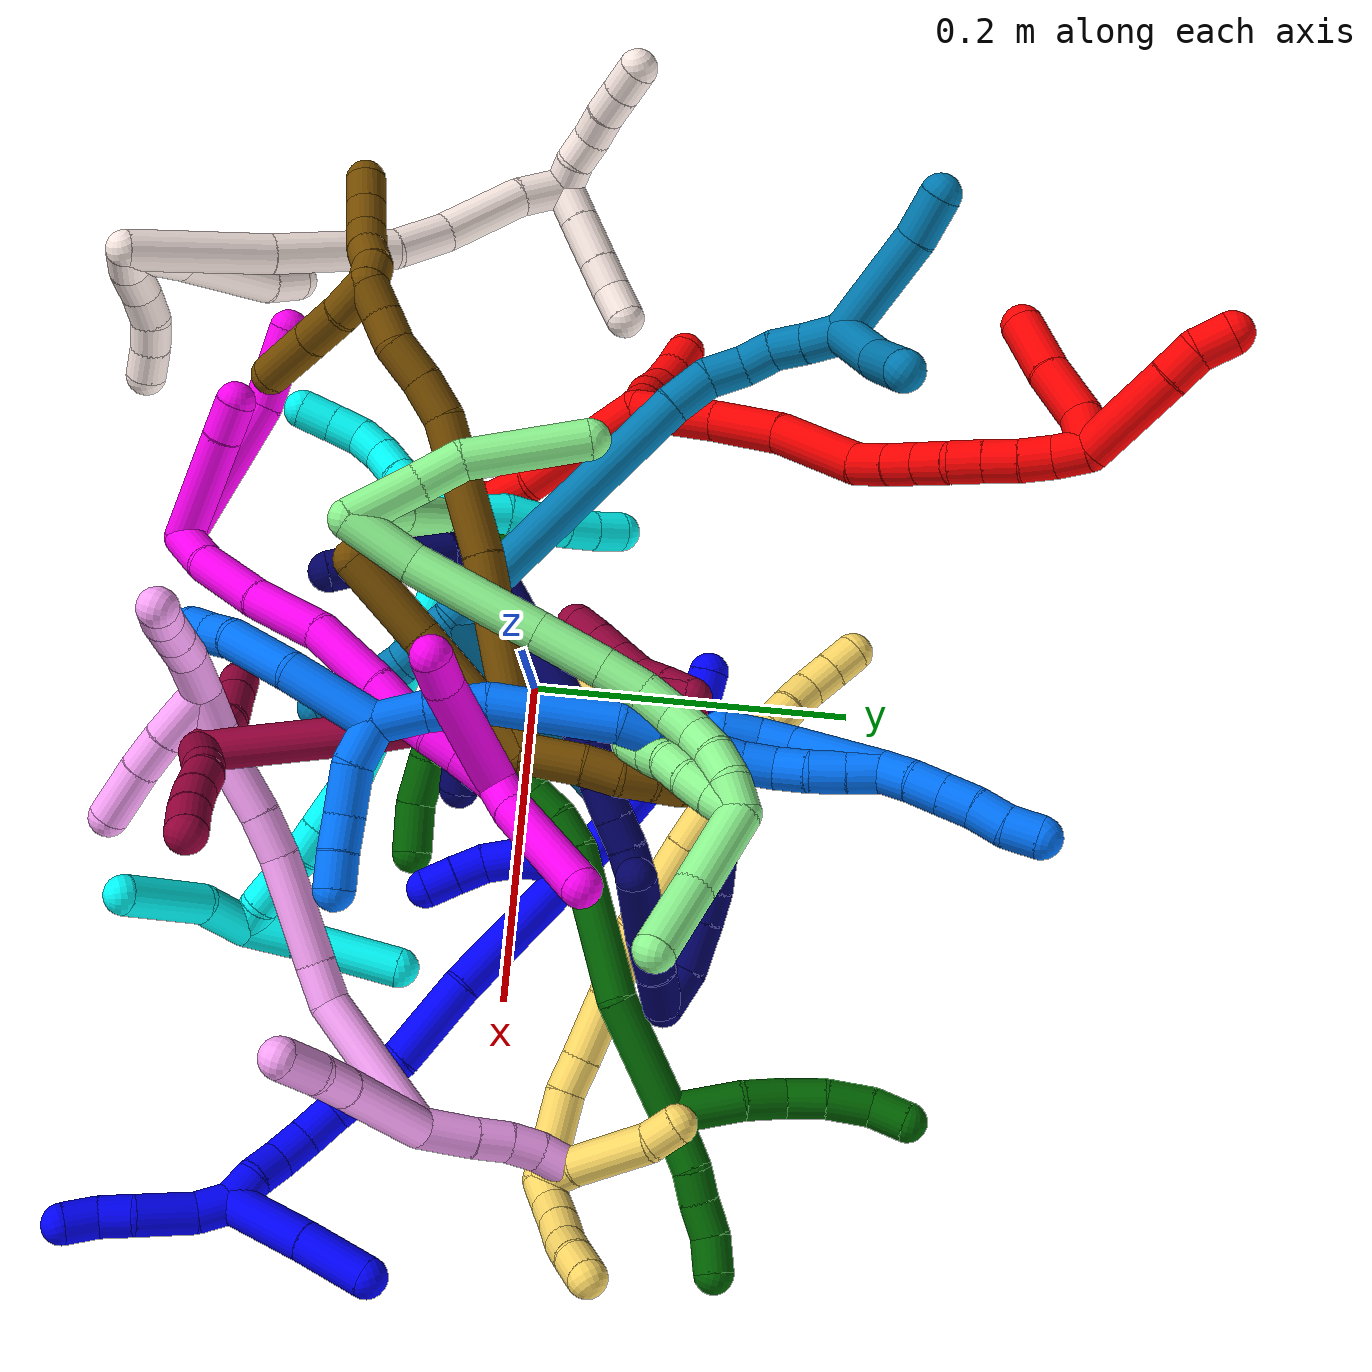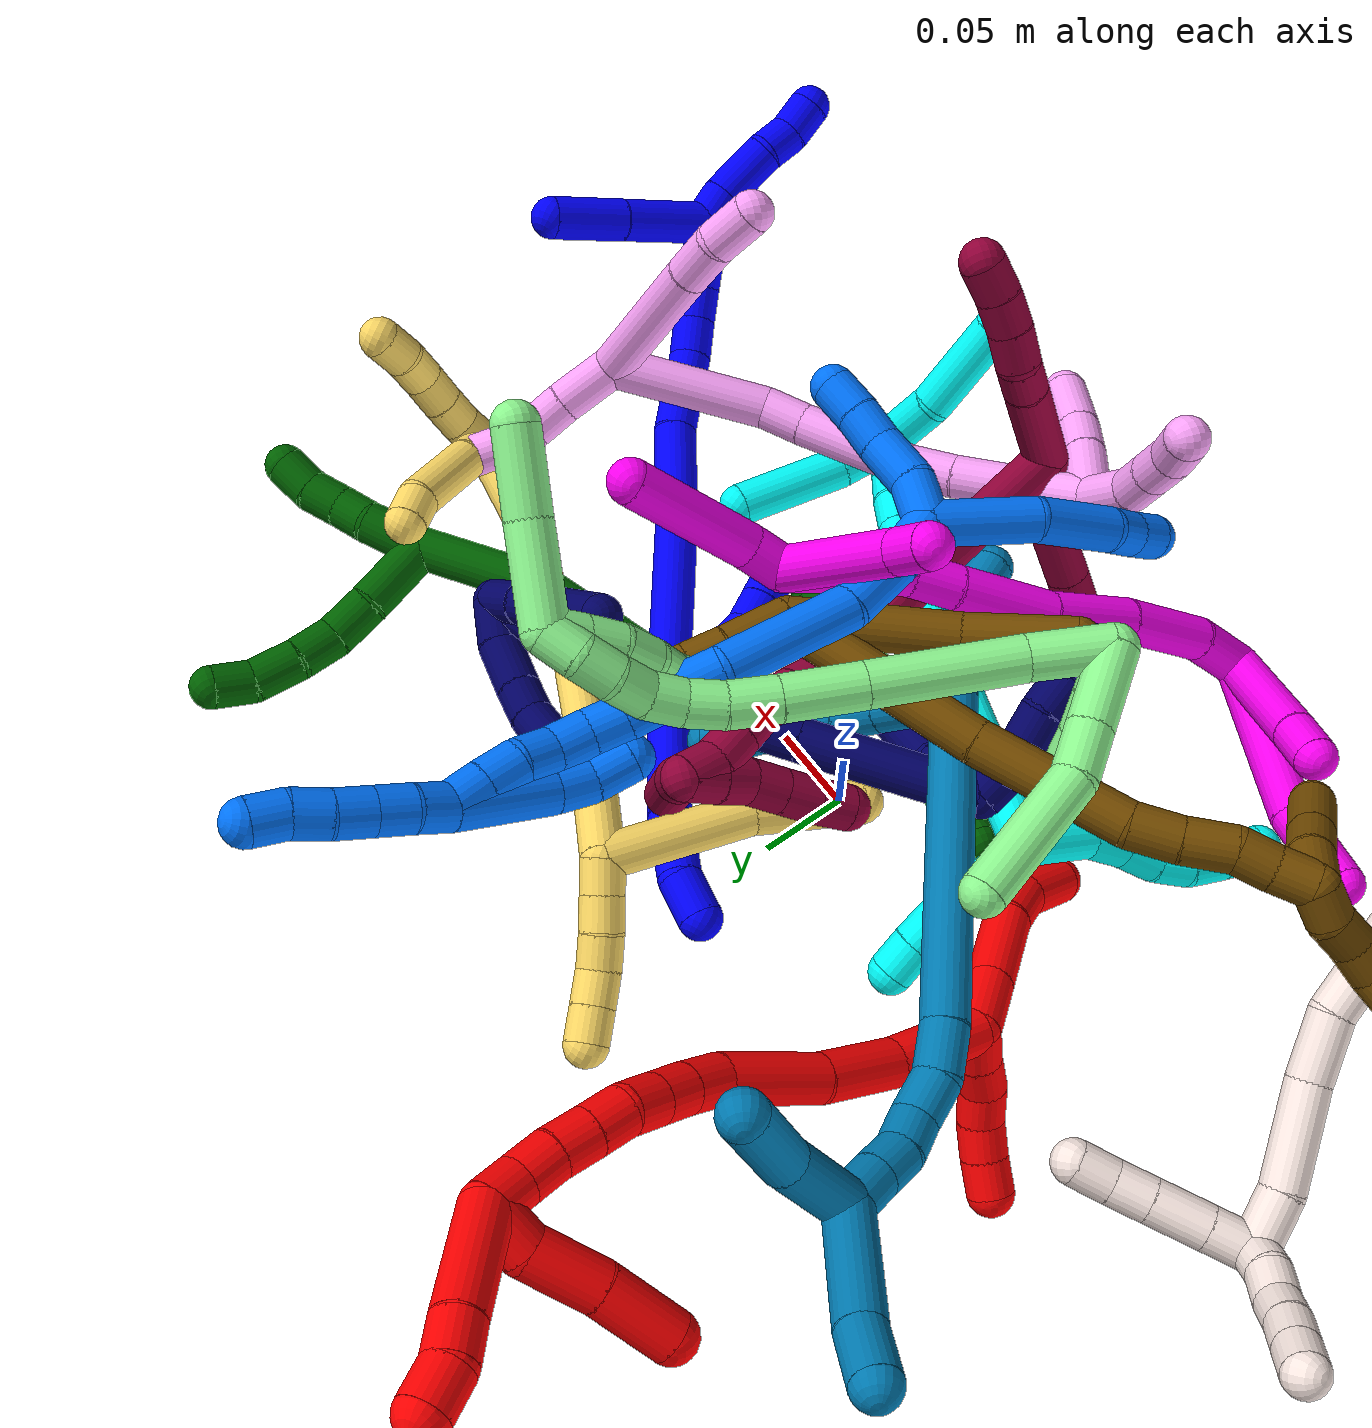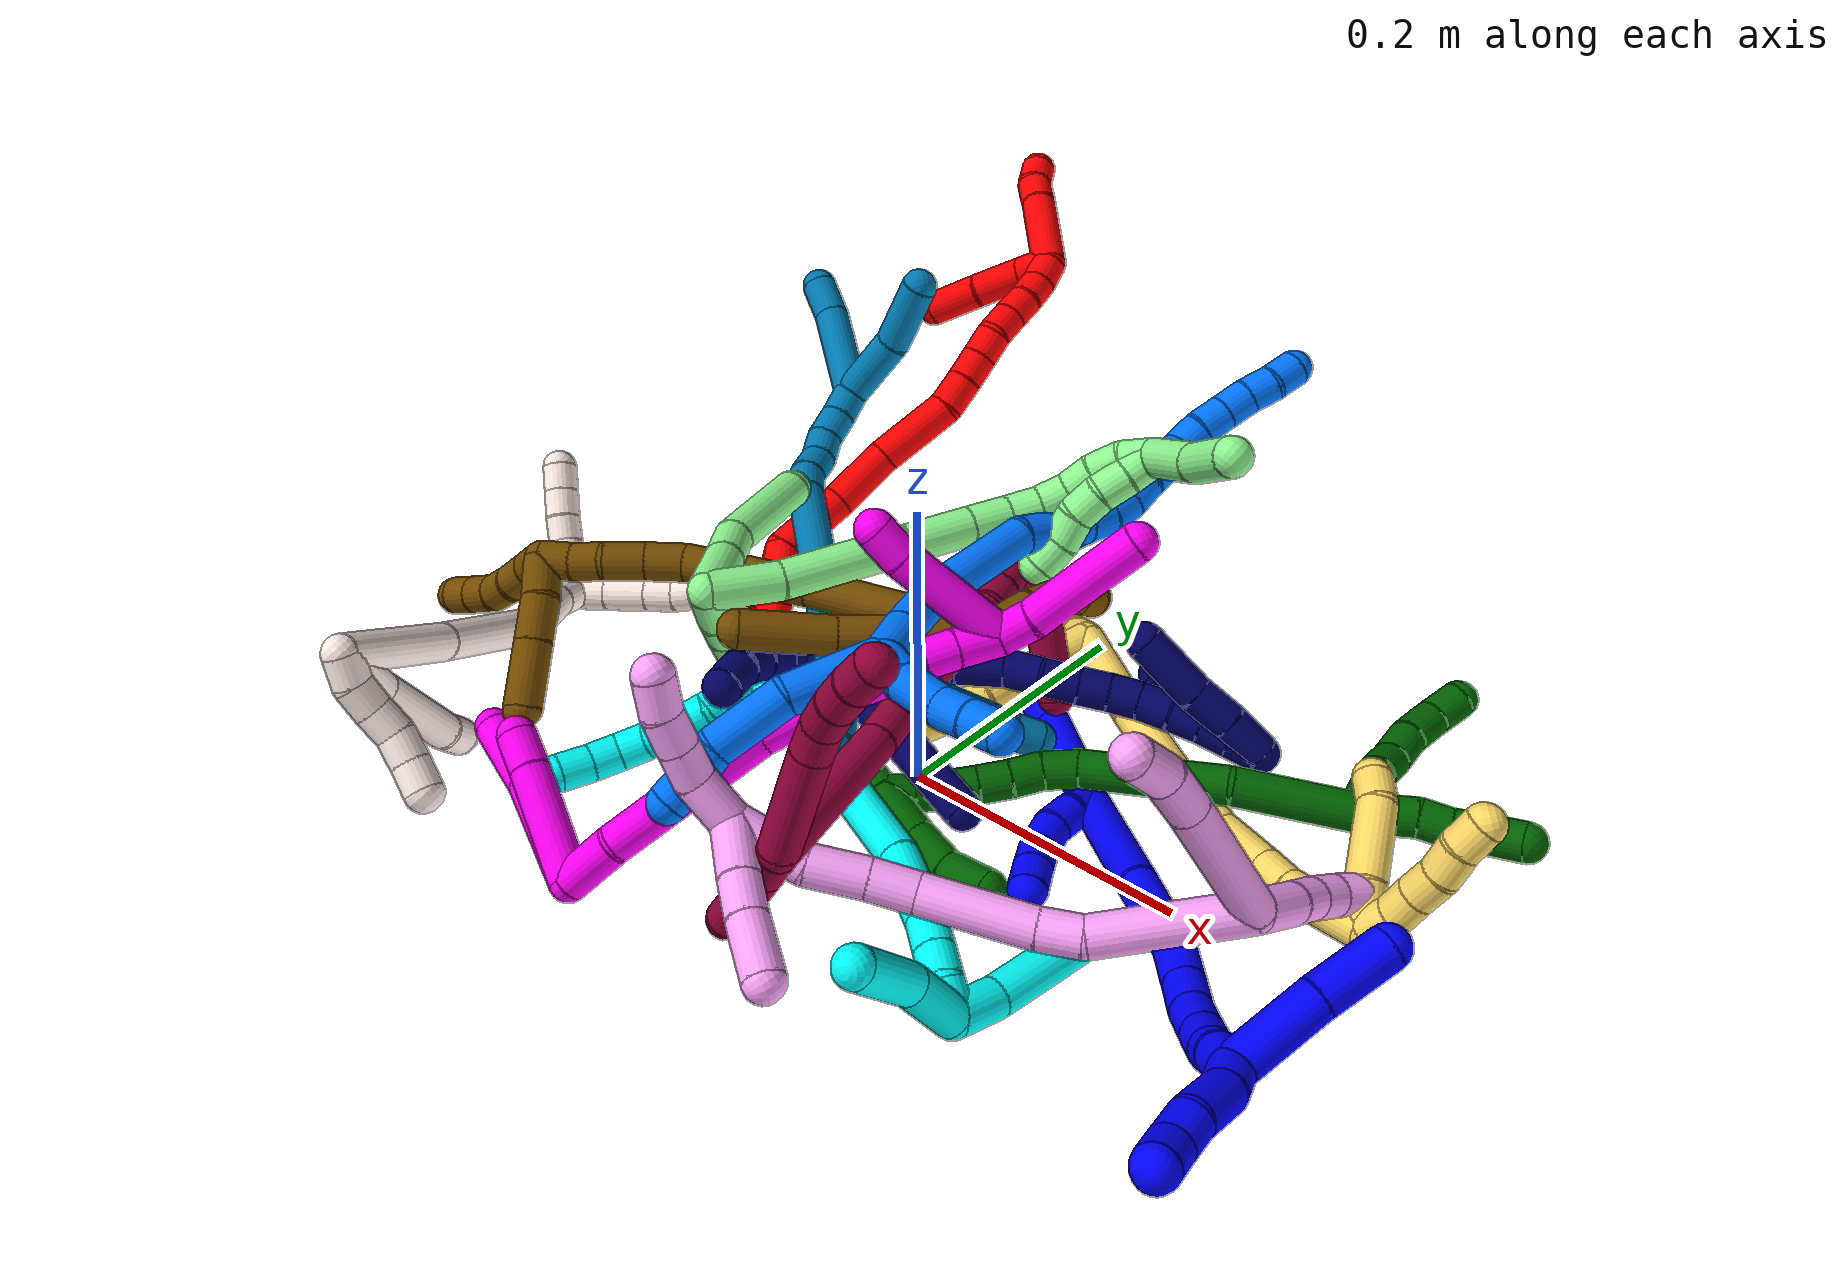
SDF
<sdf version="1.7">
 <world name="default">
  <plugin name="TubeGeneratorPlugin" filename="libtube_generator_plugin.so"/>
  <model name="photoneo_s_sensor">
   <static>1</static>
   <pose>0 0 2 1.57079 1.57079 3.14159</pose>
   <link name="link">
    <inertial><mass>0.1</mass></inertial>
    <sensor name="sensor" type="depth">
     <update_rate>30</update_rate>
     <camera>
      <horizontal_fov>1.22</horizontal_fov>
      <image><width>1920</width><height>1200</height><format>B8G8R8</format></image>
      <clip><near>0.1</near><far>4</far></clip>
      <depth_camera><output>points</output></depth_camera>
     </camera>
     <plugin name="camera_plugin" filename="libgazebo_ros_depth_camera.so">
      <baseline>0.2</baseline>
      <alwaysOn>1</alwaysOn>
      <updateRate>0.0</updateRate>
      <cameraName>camera_ir</cameraName>
      <imageTopicName>/camera/color/image_raw</imageTopicName>
      <cameraInfoTopicName>/camera/color/camera_info</cameraInfoTopicName>
      <depthImageTopicName>/camera/depth/image_raw</depthImageTopicName>
      <depthImageCameraInfoTopicName>/camera/depth/camera_info</depthImageCameraInfoTopicName>
      <pointCloudTopicName>/camera/depth/points</pointCloudTopicName>
      <frameName>fr_optical</frameName>
      <pointCloudCutoff>0.1</pointCloudCutoff>
      <pointCloudCutoffMax>2.0</pointCloudCutoffMax>
      <distortionK1>0</distortionK1>
      <distortionK2>0</distortionK2>
      <distortionK3>0</distortionK3>
      <distortionT1>0</distortionT1>
      <distortionT2>0</distortionT2>
      <CxPrime>0</CxPrime>
      <Cx>0</Cx>
      <Cy>0</Cy>
      <focalLength>0</focalLength>
      <hackBaseline>0</hackBaseline>
     </plugin>
    </sensor>
   </link>
  </model>
  <gravity>0 0 -9.8</gravity>
  <magnetic_field>6e-06 2.3e-05 -4.2e-05</magnetic_field>
  <atmosphere type="adiabatic"/>
  <physics name="default_physics" default="0" type="ode">
   <max_step_size>0.003</max_step_size>
   <real_time_factor>1</real_time_factor>
   <real_time_update_rate>1000</real_time_update_rate>
   <max_contacts>10000</max_contacts>
   <ode>
    <solver>
     <type>quick</type>
     <iters>100</iters>
     <sor>1.3</sor>
     <use_dynamic_moi_rescaling>0</use_dynamic_moi_rescaling>
    </solver>
    <constraints>
     <contact_max_correcting_vel>0</contact_max_correcting_vel>
     <contact_surface_layer>0.001</contact_surface_layer>
     <cfm>0</cfm>
     <erp>0.2</erp>
    </constraints>
   </ode>
  </physics>
  <scene><ambient>0.4 0.4 0.4 1</ambient><background>0.7 0.7 0.7 1</background><shadows>0</shadows></scene>
  <audio><device>default</device></audio>
  <spherical_coordinates>
   <surface_model>EARTH_WGS84</surface_model>
   <latitude_deg>0</latitude_deg>
   <longitude_deg>0</longitude_deg>
   <elevation>0</elevation>
   <heading_deg>0</heading_deg>
  </spherical_coordinates>
  <model name="bin">
   <static>1</static>
   <link name="bottom">
    <collision name="collision-bottom">
     <pose>0 0 -0.01 0 -0 0</pose>
     <geometry><box><size>0.8 0.6 0.02</size></box></geometry>
     <surface>
      <friction><ode><mu>100</mu><mu2>100</mu2></ode></friction>
      <contact><collide_bitmask>65535</collide_bitmask></contact>
     </surface>
    </collision>
   </link>
   <link name="west_wall">
    <collision name="collision-west_wall">
     <pose>-0.41 0 0.1 0 -0 0</pose>
     <geometry><box><size>0.02 0.6 0.2</size></box></geometry>
     <surface>
      <friction><ode><mu>100</mu><mu2>100</mu2></ode></friction>
      <contact><collide_bitmask>65535</collide_bitmask></contact>
     </surface>
    </collision>
   </link>
   <link name="east_wall">
    <collision name="collision-east_wall">
     <pose>0.41 0 0.1 0 -0 0</pose>
     <geometry><box><size>0.02 0.6 0.2</size></box></geometry>
     <surface>
      <friction><ode><mu>100</mu><mu2>100</mu2></ode></friction>
      <contact><collide_bitmask>65535</collide_bitmask></contact>
     </surface>
    </collision>
   </link>
   <link name="south_wall">
    <collision name="collision-south_wall">
     <pose>0 -0.31 0.1 0 -0 0</pose>
     <geometry><box><size>0.8 0.02 0.2</size></box></geometry>
     <surface>
      <friction><ode><mu>100</mu><mu2>100</mu2></ode></friction>
      <contact><collide_bitmask>65535</collide_bitmask></contact>
     </surface>
    </collision>
   </link>
   <link name="north_wall">
    <collision name="collision-north_wall">
     <pose>0 0.31 0.1 0 -0 0</pose>
     <geometry><box><size>0.8 0.02 0.2</size></box></geometry>
     <surface>
      <friction><ode><mu>100</mu><mu2>100</mu2></ode></friction>
      <contact><collide_bitmask>65535</collide_bitmask></contact>
     </surface>
    </collision>
   </link>
  </model>
  <model name="1">
   <static>0</static>
   <link name="1">
    <collision name="collision-cylinder-e_1_2_8">
     <pose>-0.012343 0.018475 -0.035374 -2.66028 -0.299952 1.10382</pose>
     <geometry><cylinder><radius>0.0125</radius><length>0.083547</length></cylinder></geometry>
     <surface>
      <friction><ode><mu>1.16</mu><mu2>1.16</mu2><slip1>0</slip1><slip2>0</slip2></ode></friction>
      <contact><ode><kp>1e+06</kp><kd>1</kd><max_vel>0</max_vel><min_depth>0.001</min_depth></ode></contact>
     </surface>
    </collision>
    <visual name="visual-cylinder-e_1_2_8">
     <pose>-0.012343 0.018475 -0.035374 -2.66028 -0.299952 1.10382</pose>
     <geometry><cylinder><radius>0.0125</radius><length>0.083547</length></cylinder></geometry>
     <material><ambient>0 0 1 1</ambient></material>
    </visual>
    <collision name="collision-cylinder-e_2_8_9">
     <pose>-0.031624 0.048339 -0.085962 -2.49902 -0.35003 0.976733</pose>
     <geometry><cylinder><radius>0.0125</radius><length>0.040461</length></cylinder></geometry>
     <surface>
      <friction><ode><mu>1.16</mu><mu2>1.16</mu2><slip1>0</slip1><slip2>0</slip2></ode></friction>
      <contact><ode><kp>1e+06</kp><kd>1</kd><max_vel>0</max_vel><min_depth>0.001</min_depth></ode></contact>
     </surface>
    </collision>
    <visual name="visual-cylinder-e_2_8_9">
     <pose>-0.031624 0.048339 -0.085962 -2.49902 -0.35003 0.976733</pose>
     <geometry><cylinder><radius>0.0125</radius><length>0.040461</length></cylinder></geometry>
     <material><ambient>0 0 1 1</ambient></material>
    </visual>
    <collision name="collision-cylinder-e_3_9_6">
     <pose>-0.046734 0.066432 -0.108735 -2.41599 -0.680114 1.50046</pose>
     <geometry><cylinder><radius>0.0125</radius><length>0.025992</length></cylinder></geometry>
     <surface>
      <friction><ode><mu>1.16</mu><mu2>1.16</mu2><slip1>0</slip1><slip2>0</slip2></ode></friction>
      <contact><ode><kp>1e+06</kp><kd>1</kd><max_vel>0</max_vel><min_depth>0.001</min_depth></ode></contact>
     </surface>
    </collision>
    <visual name="visual-cylinder-e_3_9_6">
     <pose>-0.046734 0.066432 -0.108735 -2.41599 -0.680114 1.50046</pose>
     <geometry><cylinder><radius>0.0125</radius><length>0.025992</length></cylinder></geometry>
     <material><ambient>0 0 1 1</ambient></material>
    </visual>
    <collision name="collision-cylinder-e_1_2_10">
     <pose>-0.003424 0.00351 0.008715 -0.382874 -0.349486 0.068405</pose>
     <geometry><cylinder><radius>0.0125</radius><length>0.02</length></cylinder></geometry>
     <surface>
      <friction><ode><mu>1.16</mu><mu2>1.16</mu2><slip1>0</slip1><slip2>0</slip2></ode></friction>
      <contact><ode><kp>1e+06</kp><kd>1</kd><max_vel>0</max_vel><min_depth>0.001</min_depth></ode></contact>
     </surface>
    </collision>
    <visual name="visual-cylinder-e_1_2_10">
     <pose>-0.003424 0.00351 0.008715 -0.382874 -0.349486 0.068405</pose>
     <geometry><cylinder><radius>0.0125</radius><length>0.02</length></cylinder></geometry>
     <material><ambient>0 0 1 1</ambient></material>
    </visual>
    <collision name="collision-cylinder-e_2_10_11">
     <pose>-0.011214 0.008169 0.026353 -0.128111 -0.451825 0.029483</pose>
     <geometry><cylinder><radius>0.0125</radius><length>0.02</length></cylinder></geometry>
     <surface>
      <friction><ode><mu>1.16</mu><mu2>1.16</mu2><slip1>0</slip1><slip2>0</slip2></ode></friction>
      <contact><ode><kp>1e+06</kp><kd>1</kd><max_vel>0</max_vel><min_depth>0.001</min_depth></ode></contact>
     </surface>
    </collision>
    <visual name="visual-cylinder-e_2_10_11">
     <pose>-0.011214 0.008169 0.026353 -0.128111 -0.451825 0.029483</pose>
     <geometry><cylinder><radius>0.0125</radius><length>0.02</length></cylinder></geometry>
     <material><ambient>0 0 1 1</ambient></material>
    </visual>
    <collision name="collision-cylinder-e_3_11_12">
     <pose>-0.018775 0.007971 0.044656 0.142721 -0.325147 -0.023448</pose>
     <geometry><cylinder><radius>0.0125</radius><length>0.02</length></cylinder></geometry>
     <surface>
      <friction><ode><mu>1.16</mu><mu2>1.16</mu2><slip1>0</slip1><slip2>0</slip2></ode></friction>
      <contact><ode><kp>1e+06</kp><kd>1</kd><max_vel>0</max_vel><min_depth>0.001</min_depth></ode></contact>
     </surface>
    </collision>
    <visual name="visual-cylinder-e_3_11_12">
     <pose>-0.018775 0.007971 0.044656 0.142721 -0.325147 -0.023448</pose>
     <geometry><cylinder><radius>0.0125</radius><length>0.02</length></cylinder></geometry>
     <material><ambient>0 0 1 1</ambient></material>
    </visual>
    <collision name="collision-cylinder-e_4_12_13">
     <pose>-0.022467 0.005247 0.063928 0.13819 -0.04981 -0.003448</pose>
     <geometry><cylinder><radius>0.0125</radius><length>0.02</length></cylinder></geometry>
     <surface>
      <friction><ode><mu>1.16</mu><mu2>1.16</mu2><slip1>0</slip1><slip2>0</slip2></ode></friction>
      <contact><ode><kp>1e+06</kp><kd>1</kd><max_vel>0</max_vel><min_depth>0.001</min_depth></ode></contact>
     </surface>
    </collision>
    <visual name="visual-cylinder-e_4_12_13">
     <pose>-0.022467 0.005247 0.063928 0.13819 -0.04981 -0.003448</pose>
     <geometry><cylinder><radius>0.0125</radius><length>0.02</length></cylinder></geometry>
     <material><ambient>0 0 1 1</ambient></material>
    </visual>
    <collision name="collision-cylinder-e_5_13_5">
     <pose>-0.023405 0.002094 0.083651 0.17889 -0.044039 -0.00395</pose>
     <geometry><cylinder><radius>0.0125</radius><length>0.02</length></cylinder></geometry>
     <surface>
      <friction><ode><mu>1.16</mu><mu2>1.16</mu2><slip1>0</slip1><slip2>0</slip2></ode></friction>
      <contact><ode><kp>1e+06</kp><kd>1</kd><max_vel>0</max_vel><min_depth>0.001</min_depth></ode></contact>
     </surface>
    </collision>
    <visual name="visual-cylinder-e_5_13_5">
     <pose>-0.023405 0.002094 0.083651 0.17889 -0.044039 -0.00395</pose>
     <geometry><cylinder><radius>0.0125</radius><length>0.02</length></cylinder></geometry>
     <material><ambient>0 0 1 1</ambient></material>
    </visual>
    <collision name="collision-cylinder-e_1_2_14">
     <pose>0.02001 -0.010342 0.047355 0.215021 0.391513 0.042796</pose>
     <geometry><cylinder><radius>0.0125</radius><length>0.104878</length></cylinder></geometry>
     <surface>
      <friction><ode><mu>1.16</mu><mu2>1.16</mu2><slip1>0</slip1><slip2>0</slip2></ode></friction>
      <contact><ode><kp>1e+06</kp><kd>1</kd><max_vel>0</max_vel><min_depth>0.001</min_depth></ode></contact>
     </surface>
    </collision>
    <visual name="visual-cylinder-e_1_2_14">
     <pose>0.02001 -0.010342 0.047355 0.215021 0.391513 0.042796</pose>
     <geometry><cylinder><radius>0.0125</radius><length>0.104878</length></cylinder></geometry>
     <material><ambient>0 0 1 1</ambient></material>
    </visual>
    <collision name="collision-cylinder-e_2_14_15">
     <pose>0.050318 -0.031342 0.119656 0.403758 0.362797 0.075043</pose>
     <geometry><cylinder><radius>0.0125</radius><length>0.058031</length></cylinder></geometry>
     <surface>
      <friction><ode><mu>1.16</mu><mu2>1.16</mu2><slip1>0</slip1><slip2>0</slip2></ode></friction>
      <contact><ode><kp>1e+06</kp><kd>1</kd><max_vel>0</max_vel><min_depth>0.001</min_depth></ode></contact>
     </surface>
    </collision>
    <visual name="visual-cylinder-e_2_14_15">
     <pose>0.050318 -0.031342 0.119656 0.403758 0.362797 0.075043</pose>
     <geometry><cylinder><radius>0.0125</radius><length>0.058031</length></cylinder></geometry>
     <material><ambient>0 0 1 1</ambient></material>
    </visual>
    <collision name="collision-cylinder-e_3_15_16">
     <pose>0.063647 -0.046373 0.158514 0.304586 0.205006 0.031573</pose>
     <geometry><cylinder><radius>0.0125</radius><length>0.029792</length></cylinder></geometry>
     <surface>
      <friction><ode><mu>1.16</mu><mu2>1.16</mu2><slip1>0</slip1><slip2>0</slip2></ode></friction>
      <contact><ode><kp>1e+06</kp><kd>1</kd><max_vel>0</max_vel><min_depth>0.001</min_depth></ode></contact>
     </surface>
    </collision>
    <visual name="visual-cylinder-e_3_15_16">
     <pose>0.063647 -0.046373 0.158514 0.304586 0.205006 0.031573</pose>
     <geometry><cylinder><radius>0.0125</radius><length>0.029792</length></cylinder></geometry>
     <material><ambient>0 0 1 1</ambient></material>
    </visual>
    <collision name="collision-cylinder-e_4_16_17">
     <pose>0.069033 -0.05344 0.183047 0.248304 0.211567 0.0265</pose>
     <geometry><cylinder><radius>0.0125</radius><length>0.022413</length></cylinder></geometry>
     <surface>
      <friction><ode><mu>1.16</mu><mu2>1.16</mu2><slip1>0</slip1><slip2>0</slip2></ode></friction>
      <contact><ode><kp>1e+06</kp><kd>1</kd><max_vel>0</max_vel><min_depth>0.001</min_depth></ode></contact>
     </surface>
    </collision>
    <visual name="visual-cylinder-e_4_16_17">
     <pose>0.069033 -0.05344 0.183047 0.248304 0.211567 0.0265</pose>
     <geometry><cylinder><radius>0.0125</radius><length>0.022413</length></cylinder></geometry>
     <material><ambient>0 0 1 1</ambient></material>
    </visual>
    <collision name="collision-cylinder-e_5_17_18">
     <pose>0.075573 -0.05743 0.204577 0.118363 0.364084 0.021813</pose>
     <geometry><cylinder><radius>0.0125</radius><length>0.023512</length></cylinder></geometry>
     <surface>
      <friction><ode><mu>1.16</mu><mu2>1.16</mu2><slip1>0</slip1><slip2>0</slip2></ode></friction>
      <contact><ode><kp>1e+06</kp><kd>1</kd><max_vel>0</max_vel><min_depth>0.001</min_depth></ode></contact>
     </surface>
    </collision>
    <visual name="visual-cylinder-e_5_17_18">
     <pose>0.075573 -0.05743 0.204577 0.118363 0.364084 0.021813</pose>
     <geometry><cylinder><radius>0.0125</radius><length>0.023512</length></cylinder></geometry>
     <material><ambient>0 0 1 1</ambient></material>
    </visual>
    <collision name="collision-cylinder-e_6_18_19">
     <pose>0.083797 -0.058684 0.225379 -0.004362 0.387484 -0.000856</pose>
     <geometry><cylinder><radius>0.0125</radius><length>0.021372</length></cylinder></geometry>
     <surface>
      <friction><ode><mu>1.16</mu><mu2>1.16</mu2><slip1>0</slip1><slip2>0</slip2></ode></friction>
      <contact><ode><kp>1e+06</kp><kd>1</kd><max_vel>0</max_vel><min_depth>0.001</min_depth></ode></contact>
     </surface>
    </collision>
    <visual name="visual-cylinder-e_6_18_19">
     <pose>0.083797 -0.058684 0.225379 -0.004362 0.387484 -0.000856</pose>
     <geometry><cylinder><radius>0.0125</radius><length>0.021372</length></cylinder></geometry>
     <material><ambient>0 0 1 1</ambient></material>
    </visual>
    <collision name="collision-cylinder-e_7_19_20">
     <pose>0.092432 -0.055908 0.243722 -0.312726 0.477735 -0.076743</pose>
     <geometry><cylinder><radius>0.0125</radius><length>0.020001</length></cylinder></geometry>
     <surface>
      <friction><ode><mu>1.16</mu><mu2>1.16</mu2><slip1>0</slip1><slip2>0</slip2></ode></friction>
      <contact><ode><kp>1e+06</kp><kd>1</kd><max_vel>0</max_vel><min_depth>0.001</min_depth></ode></contact>
     </surface>
    </collision>
    <visual name="visual-cylinder-e_7_19_20">
     <pose>0.092432 -0.055908 0.243722 -0.312726 0.477735 -0.076743</pose>
     <geometry><cylinder><radius>0.0125</radius><length>0.020001</length></cylinder></geometry>
     <material><ambient>0 0 1 1</ambient></material>
    </visual>
    <collision name="collision-cylinder-e_8_20_1">
     <pose>0.102242 -0.053134 0.260707 -0.004877 0.548189 -0.001371</pose>
     <geometry><cylinder><radius>0.0125</radius><length>0.020001</length></cylinder></geometry>
     <surface>
      <friction><ode><mu>1.16</mu><mu2>1.16</mu2><slip1>0</slip1><slip2>0</slip2></ode></friction>
      <contact><ode><kp>1e+06</kp><kd>1</kd><max_vel>0</max_vel><min_depth>0.001</min_depth></ode></contact>
     </surface>
    </collision>
    <visual name="visual-cylinder-e_8_20_1">
     <pose>0.102242 -0.053134 0.260707 -0.004877 0.548189 -0.001371</pose>
     <geometry><cylinder><radius>0.0125</radius><length>0.020001</length></cylinder></geometry>
     <material><ambient>0 0 1 1</ambient></material>
    </visual>
    <collision name="collision-cylinder-e_1_1_21">
     <pose>0.129679 -0.051543 0.253088 -3.04592 0.940123 -2.95369</pose>
     <geometry><cylinder><radius>0.0125</radius><length>0.055039</length></cylinder></geometry>
     <surface>
      <friction><ode><mu>1.16</mu><mu2>1.16</mu2><slip1>0</slip1><slip2>0</slip2></ode></friction>
      <contact><ode><kp>1e+06</kp><kd>1</kd><max_vel>0</max_vel><min_depth>0.001</min_depth></ode></contact>
     </surface>
    </collision>
    <visual name="visual-cylinder-e_1_1_21">
     <pose>0.129679 -0.051543 0.253088 -3.04592 0.940123 -2.95369</pose>
     <geometry><cylinder><radius>0.0125</radius><length>0.055039</length></cylinder></geometry>
     <material><ambient>0 0 1 1</ambient></material>
    </visual>
    <collision name="collision-cylinder-e_2_21_4">
     <pose>0.170301 -0.050079 0.224014 3.13486 0.958469 3.12863</pose>
     <geometry><cylinder><radius>0.0125</radius><length>0.044961</length></cylinder></geometry>
     <surface>
      <friction><ode><mu>1.16</mu><mu2>1.16</mu2><slip1>0</slip1><slip2>0</slip2></ode></friction>
      <contact><ode><kp>1e+06</kp><kd>1</kd><max_vel>0</max_vel><min_depth>0.001</min_depth></ode></contact>
     </surface>
    </collision>
    <visual name="visual-cylinder-e_2_21_4">
     <pose>0.170301 -0.050079 0.224014 3.13486 0.958469 3.12863</pose>
     <geometry><cylinder><radius>0.0125</radius><length>0.044961</length></cylinder></geometry>
     <material><ambient>0 0 1 1</ambient></material>
    </visual>
    <collision name="collision-cylinder-e_1_1_22">
     <pose>0.106941 -0.052266 0.279993 -0.076802 -0.0475 0.001825</pose>
     <geometry><cylinder><radius>0.0125</radius><length>0.021588</length></cylinder></geometry>
     <surface>
      <friction><ode><mu>1.16</mu><mu2>1.16</mu2><slip1>0</slip1><slip2>0</slip2></ode></friction>
      <contact><ode><kp>1e+06</kp><kd>1</kd><max_vel>0</max_vel><min_depth>0.001</min_depth></ode></contact>
     </surface>
    </collision>
    <visual name="visual-cylinder-e_1_1_22">
     <pose>0.106941 -0.052266 0.279993 -0.076802 -0.0475 0.001825</pose>
     <geometry><cylinder><radius>0.0125</radius><length>0.021588</length></cylinder></geometry>
     <material><ambient>0 0 1 1</ambient></material>
    </visual>
    <collision name="collision-cylinder-e_2_22_23">
     <pose>0.103257 -0.045698 0.307865 -0.323468 -0.173853 0.028435</pose>
     <geometry><cylinder><radius>0.0125</radius><length>0.036671</length></cylinder></geometry>
     <surface>
      <friction><ode><mu>1.16</mu><mu2>1.16</mu2><slip1>0</slip1><slip2>0</slip2></ode></friction>
      <contact><ode><kp>1e+06</kp><kd>1</kd><max_vel>0</max_vel><min_depth>0.001</min_depth></ode></contact>
     </surface>
    </collision>
    <visual name="visual-cylinder-e_2_22_23">
     <pose>0.103257 -0.045698 0.307865 -0.323468 -0.173853 0.028435</pose>
     <geometry><cylinder><radius>0.0125</radius><length>0.036671</length></cylinder></geometry>
     <material><ambient>0 0 1 1</ambient></material>
    </visual>
    <collision name="collision-cylinder-e_3_23_24">
     <pose>0.096694 -0.039272 0.334624 -0.07109 -0.337583 0.01212</pose>
     <geometry><cylinder><radius>0.0125</radius><length>0.020476</length></cylinder></geometry>
     <surface>
      <friction><ode><mu>1.16</mu><mu2>1.16</mu2><slip1>0</slip1><slip2>0</slip2></ode></friction>
      <contact><ode><kp>1e+06</kp><kd>1</kd><max_vel>0</max_vel><min_depth>0.001</min_depth></ode></contact>
     </surface>
    </collision>
    <visual name="visual-cylinder-e_3_23_24">
     <pose>0.096694 -0.039272 0.334624 -0.07109 -0.337583 0.01212</pose>
     <geometry><cylinder><radius>0.0125</radius><length>0.020476</length></cylinder></geometry>
     <material><ambient>0 0 1 1</ambient></material>
    </visual>
    <collision name="collision-cylinder-e_4_24_3">
     <pose>0.092659 -0.03612 0.354582 -0.234453 -0.060662 0.007146</pose>
     <geometry><cylinder><radius>0.0125</radius><length>0.021265</length></cylinder></geometry>
     <surface>
      <friction><ode><mu>1.16</mu><mu2>1.16</mu2><slip1>0</slip1><slip2>0</slip2></ode></friction>
      <contact><ode><kp>1e+06</kp><kd>1</kd><max_vel>0</max_vel><min_depth>0.001</min_depth></ode></contact>
     </surface>
    </collision>
    <visual name="visual-cylinder-e_4_24_3">
     <pose>0.092659 -0.03612 0.354582 -0.234453 -0.060662 0.007146</pose>
     <geometry><cylinder><radius>0.0125</radius><length>0.021265</length></cylinder></geometry>
     <material><ambient>0 0 1 1</ambient></material>
    </visual>
    <collision name="collision-sphere-3">
     <pose>0.092014 -0.033655 0.364904 0 -0 0</pose>
     <geometry><sphere><radius>0.0125</radius></sphere></geometry>
     <surface>
      <friction><ode><mu>1.16</mu><mu2>1.16</mu2><slip1>0</slip1><slip2>0</slip2></ode></friction>
      <contact><ode><kp>1e+06</kp><kd>1</kd><max_vel>0</max_vel><min_depth>0.001</min_depth></ode></contact>
     </surface>
    </collision>
    <visual name="visual-sphere-3">
     <pose>0.092014 -0.033655 0.364904 0 -0 0</pose>
     <geometry><sphere><radius>0.0125</radius></sphere></geometry>
     <material><ambient>0 0 1 1</ambient></material>
    </visual>
    <collision name="collision-sphere-24">
     <pose>0.093303 -0.038586 0.344259 0 -0 0</pose>
     <geometry><sphere><radius>0.0125</radius></sphere></geometry>
     <surface>
      <friction><ode><mu>1.16</mu><mu2>1.16</mu2><slip1>0</slip1><slip2>0</slip2></ode></friction>
      <contact><ode><kp>1e+06</kp><kd>1</kd><max_vel>0</max_vel><min_depth>0.001</min_depth></ode></contact>
     </surface>
    </collision>
    <visual name="visual-sphere-24">
     <pose>0.093303 -0.038586 0.344259 0 -0 0</pose>
     <geometry><sphere><radius>0.0125</radius></sphere></geometry>
     <material><ambient>0 0 1 1</ambient></material>
    </visual>
    <collision name="collision-sphere-23">
     <pose>0.100085 -0.039958 0.324988 0 -0 0</pose>
     <geometry><sphere><radius>0.0125</radius></sphere></geometry>
     <surface>
      <friction><ode><mu>1.16</mu><mu2>1.16</mu2><slip1>0</slip1><slip2>0</slip2></ode></friction>
      <contact><ode><kp>1e+06</kp><kd>1</kd><max_vel>0</max_vel><min_depth>0.001</min_depth></ode></contact>
     </surface>
    </collision>
    <visual name="visual-sphere-23">
     <pose>0.100085 -0.039958 0.324988 0 -0 0</pose>
     <geometry><sphere><radius>0.0125</radius></sphere></geometry>
     <material><ambient>0 0 1 1</ambient></material>
    </visual>
    <collision name="collision-sphere-22">
     <pose>0.106428 -0.051438 0.290743 0 -0 0</pose>
     <geometry><sphere><radius>0.0125</radius></sphere></geometry>
     <surface>
      <friction><ode><mu>1.16</mu><mu2>1.16</mu2><slip1>0</slip1><slip2>0</slip2></ode></friction>
      <contact><ode><kp>1e+06</kp><kd>1</kd><max_vel>0</max_vel><min_depth>0.001</min_depth></ode></contact>
     </surface>
    </collision>
    <visual name="visual-sphere-22">
     <pose>0.106428 -0.051438 0.290743 0 -0 0</pose>
     <geometry><sphere><radius>0.0125</radius></sphere></geometry>
     <material><ambient>0 0 1 1</ambient></material>
    </visual>
    <collision name="collision-sphere-4">
     <pose>0.188697 -0.050166 0.211093 0 -0 0</pose>
     <geometry><sphere><radius>0.0125</radius></sphere></geometry>
     <surface>
      <friction><ode><mu>1.16</mu><mu2>1.16</mu2><slip1>0</slip1><slip2>0</slip2></ode></friction>
      <contact><ode><kp>1e+06</kp><kd>1</kd><max_vel>0</max_vel><min_depth>0.001</min_depth></ode></contact>
     </surface>
    </collision>
    <visual name="visual-sphere-4">
     <pose>0.188697 -0.050166 0.211093 0 -0 0</pose>
     <geometry><sphere><radius>0.0125</radius></sphere></geometry>
     <material><ambient>0 0 1 1</ambient></material>
    </visual>
    <collision name="collision-sphere-21">
     <pose>0.151905 -0.049992 0.236935 0 -0 0</pose>
     <geometry><sphere><radius>0.0125</radius></sphere></geometry>
     <surface>
      <friction><ode><mu>1.16</mu><mu2>1.16</mu2><slip1>0</slip1><slip2>0</slip2></ode></friction>
      <contact><ode><kp>1e+06</kp><kd>1</kd><max_vel>0</max_vel><min_depth>0.001</min_depth></ode></contact>
     </surface>
    </collision>
    <visual name="visual-sphere-21">
     <pose>0.151905 -0.049992 0.236935 0 -0 0</pose>
     <geometry><sphere><radius>0.0125</radius></sphere></geometry>
     <material><ambient>0 0 1 1</ambient></material>
    </visual>
    <collision name="collision-sphere-1">
     <pose>0.107454 -0.053093 0.269242 0 -0 0</pose>
     <geometry><sphere><radius>0.0125</radius></sphere></geometry>
     <surface>
      <friction><ode><mu>1.16</mu><mu2>1.16</mu2><slip1>0</slip1><slip2>0</slip2></ode></friction>
      <contact><ode><kp>1e+06</kp><kd>1</kd><max_vel>0</max_vel><min_depth>0.001</min_depth></ode></contact>
     </surface>
    </collision>
    <visual name="visual-sphere-1">
     <pose>0.107454 -0.053093 0.269242 0 -0 0</pose>
     <geometry><sphere><radius>0.0125</radius></sphere></geometry>
     <material><ambient>0 0 1 1</ambient></material>
    </visual>
    <collision name="collision-sphere-11">
     <pose>-0.01558 0.009319 0.035276 0 -0 0</pose>
     <geometry><sphere><radius>0.0125</radius></sphere></geometry>
     <surface>
      <friction><ode><mu>1.16</mu><mu2>1.16</mu2><slip1>0</slip1><slip2>0</slip2></ode></friction>
      <contact><ode><kp>1e+06</kp><kd>1</kd><max_vel>0</max_vel><min_depth>0.001</min_depth></ode></contact>
     </surface>
    </collision>
    <visual name="visual-sphere-11">
     <pose>-0.01558 0.009319 0.035276 0 -0 0</pose>
     <geometry><sphere><radius>0.0125</radius></sphere></geometry>
     <material><ambient>0 0 1 1</ambient></material>
    </visual>
    <collision name="collision-sphere-10">
     <pose>-0.006848 0.00702 0.01743 0 -0 0</pose>
     <geometry><sphere><radius>0.0125</radius></sphere></geometry>
     <surface>
      <friction><ode><mu>1.16</mu><mu2>1.16</mu2><slip1>0</slip1><slip2>0</slip2></ode></friction>
      <contact><ode><kp>1e+06</kp><kd>1</kd><max_vel>0</max_vel><min_depth>0.001</min_depth></ode></contact>
     </surface>
    </collision>
    <visual name="visual-sphere-10">
     <pose>-0.006848 0.00702 0.01743 0 -0 0</pose>
     <geometry><sphere><radius>0.0125</radius></sphere></geometry>
     <material><ambient>0 0 1 1</ambient></material>
    </visual>
    <collision name="collision-sphere-6">
     <pose>-0.054907 0.073137 -0.116294 0 -0 0</pose>
     <geometry><sphere><radius>0.0125</radius></sphere></geometry>
     <surface>
      <friction><ode><mu>1.16</mu><mu2>1.16</mu2><slip1>0</slip1><slip2>0</slip2></ode></friction>
      <contact><ode><kp>1e+06</kp><kd>1</kd><max_vel>0</max_vel><min_depth>0.001</min_depth></ode></contact>
     </surface>
    </collision>
    <visual name="visual-sphere-6">
     <pose>-0.054907 0.073137 -0.116294 0 -0 0</pose>
     <geometry><sphere><radius>0.0125</radius></sphere></geometry>
     <material><ambient>0 0 1 1</ambient></material>
    </visual>
    <collision name="collision-sphere-9">
     <pose>-0.038561 0.059727 -0.101176 0 -0 0</pose>
     <geometry><sphere><radius>0.0125</radius></sphere></geometry>
     <surface>
      <friction><ode><mu>1.16</mu><mu2>1.16</mu2><slip1>0</slip1><slip2>0</slip2></ode></friction>
      <contact><ode><kp>1e+06</kp><kd>1</kd><max_vel>0</max_vel><min_depth>0.001</min_depth></ode></contact>
     </surface>
    </collision>
    <visual name="visual-sphere-9">
     <pose>-0.038561 0.059727 -0.101176 0 -0 0</pose>
     <geometry><sphere><radius>0.0125</radius></sphere></geometry>
     <material><ambient>0 0 1 1</ambient></material>
    </visual>
    <collision name="collision-sphere-2">
     <geometry><sphere><radius>0.0125</radius></sphere></geometry>
     <surface>
      <friction><ode><mu>1.16</mu><mu2>1.16</mu2><slip1>0</slip1><slip2>0</slip2></ode></friction>
      <contact><ode><kp>1e+06</kp><kd>1</kd><max_vel>0</max_vel><min_depth>0.001</min_depth></ode></contact>
     </surface>
    </collision>
    <visual name="visual-sphere-2">
     <geometry><sphere><radius>0.0125</radius></sphere></geometry>
     <material><ambient>0 0 1 1</ambient></material>
    </visual>
    <collision name="collision-sphere-19">
     <pose>0.087834 -0.058641 0.235272 0 -0 0</pose>
     <geometry><sphere><radius>0.0125</radius></sphere></geometry>
     <surface>
      <friction><ode><mu>1.16</mu><mu2>1.16</mu2><slip1>0</slip1><slip2>0</slip2></ode></friction>
      <contact><ode><kp>1e+06</kp><kd>1</kd><max_vel>0</max_vel><min_depth>0.001</min_depth></ode></contact>
     </surface>
    </collision>
    <visual name="visual-sphere-19">
     <pose>0.087834 -0.058641 0.235272 0 -0 0</pose>
     <geometry><sphere><radius>0.0125</radius></sphere></geometry>
     <material><ambient>0 0 1 1</ambient></material>
    </visual>
    <collision name="collision-sphere-8">
     <pose>-0.024686 0.036951 -0.070749 0 -0 0</pose>
     <geometry><sphere><radius>0.0125</radius></sphere></geometry>
     <surface>
      <friction><ode><mu>1.16</mu><mu2>1.16</mu2><slip1>0</slip1><slip2>0</slip2></ode></friction>
      <contact><ode><kp>1e+06</kp><kd>1</kd><max_vel>0</max_vel><min_depth>0.001</min_depth></ode></contact>
     </surface>
    </collision>
    <visual name="visual-sphere-8">
     <pose>-0.024686 0.036951 -0.070749 0 -0 0</pose>
     <geometry><sphere><radius>0.0125</radius></sphere></geometry>
     <material><ambient>0 0 1 1</ambient></material>
    </visual>
    <collision name="collision-sphere-12">
     <pose>-0.021969 0.006623 0.054035 0 -0 0</pose>
     <geometry><sphere><radius>0.0125</radius></sphere></geometry>
     <surface>
      <friction><ode><mu>1.16</mu><mu2>1.16</mu2><slip1>0</slip1><slip2>0</slip2></ode></friction>
      <contact><ode><kp>1e+06</kp><kd>1</kd><max_vel>0</max_vel><min_depth>0.001</min_depth></ode></contact>
     </surface>
    </collision>
    <visual name="visual-sphere-12">
     <pose>-0.021969 0.006623 0.054035 0 -0 0</pose>
     <geometry><sphere><radius>0.0125</radius></sphere></geometry>
     <material><ambient>0 0 1 1</ambient></material>
    </visual>
    <collision name="collision-sphere-13">
     <pose>-0.022965 0.003872 0.07382 0 -0 0</pose>
     <geometry><sphere><radius>0.0125</radius></sphere></geometry>
     <surface>
      <friction><ode><mu>1.16</mu><mu2>1.16</mu2><slip1>0</slip1><slip2>0</slip2></ode></friction>
      <contact><ode><kp>1e+06</kp><kd>1</kd><max_vel>0</max_vel><min_depth>0.001</min_depth></ode></contact>
     </surface>
    </collision>
    <visual name="visual-sphere-13">
     <pose>-0.022965 0.003872 0.07382 0 -0 0</pose>
     <geometry><sphere><radius>0.0125</radius></sphere></geometry>
     <material><ambient>0 0 1 1</ambient></material>
    </visual>
    <collision name="collision-sphere-5">
     <pose>-0.023846 0.000316 0.093482 0 -0 0</pose>
     <geometry><sphere><radius>0.0125</radius></sphere></geometry>
     <surface>
      <friction><ode><mu>1.16</mu><mu2>1.16</mu2><slip1>0</slip1><slip2>0</slip2></ode></friction>
      <contact><ode><kp>1e+06</kp><kd>1</kd><max_vel>0</max_vel><min_depth>0.001</min_depth></ode></contact>
     </surface>
    </collision>
    <visual name="visual-sphere-5">
     <pose>-0.023846 0.000316 0.093482 0 -0 0</pose>
     <geometry><sphere><radius>0.0125</radius></sphere></geometry>
     <material><ambient>0 0 1 1</ambient></material>
    </visual>
    <collision name="collision-sphere-14">
     <pose>0.04002 -0.020684 0.09471 0 -0 0</pose>
     <geometry><sphere><radius>0.0125</radius></sphere></geometry>
     <surface>
      <friction><ode><mu>1.16</mu><mu2>1.16</mu2><slip1>0</slip1><slip2>0</slip2></ode></friction>
      <contact><ode><kp>1e+06</kp><kd>1</kd><max_vel>0</max_vel><min_depth>0.001</min_depth></ode></contact>
     </surface>
    </collision>
    <visual name="visual-sphere-14">
     <pose>0.04002 -0.020684 0.09471 0 -0 0</pose>
     <geometry><sphere><radius>0.0125</radius></sphere></geometry>
     <material><ambient>0 0 1 1</ambient></material>
    </visual>
    <collision name="collision-sphere-15">
     <pose>0.060615 -0.042 0.144601 0 -0 0</pose>
     <geometry><sphere><radius>0.0125</radius></sphere></geometry>
     <surface>
      <friction><ode><mu>1.16</mu><mu2>1.16</mu2><slip1>0</slip1><slip2>0</slip2></ode></friction>
      <contact><ode><kp>1e+06</kp><kd>1</kd><max_vel>0</max_vel><min_depth>0.001</min_depth></ode></contact>
     </surface>
    </collision>
    <visual name="visual-sphere-15">
     <pose>0.060615 -0.042 0.144601 0 -0 0</pose>
     <geometry><sphere><radius>0.0125</radius></sphere></geometry>
     <material><ambient>0 0 1 1</ambient></material>
    </visual>
    <collision name="collision-sphere-16">
     <pose>0.06668 -0.050747 0.172427 0 -0 0</pose>
     <geometry><sphere><radius>0.0125</radius></sphere></geometry>
     <surface>
      <friction><ode><mu>1.16</mu><mu2>1.16</mu2><slip1>0</slip1><slip2>0</slip2></ode></friction>
      <contact><ode><kp>1e+06</kp><kd>1</kd><max_vel>0</max_vel><min_depth>0.001</min_depth></ode></contact>
     </surface>
    </collision>
    <visual name="visual-sphere-16">
     <pose>0.06668 -0.050747 0.172427 0 -0 0</pose>
     <geometry><sphere><radius>0.0125</radius></sphere></geometry>
     <material><ambient>0 0 1 1</ambient></material>
    </visual>
    <collision name="collision-sphere-17">
     <pose>0.071386 -0.056132 0.193668 0 -0 0</pose>
     <geometry><sphere><radius>0.0125</radius></sphere></geometry>
     <surface>
      <friction><ode><mu>1.16</mu><mu2>1.16</mu2><slip1>0</slip1><slip2>0</slip2></ode></friction>
      <contact><ode><kp>1e+06</kp><kd>1</kd><max_vel>0</max_vel><min_depth>0.001</min_depth></ode></contact>
     </surface>
    </collision>
    <visual name="visual-sphere-17">
     <pose>0.071386 -0.056132 0.193668 0 -0 0</pose>
     <geometry><sphere><radius>0.0125</radius></sphere></geometry>
     <material><ambient>0 0 1 1</ambient></material>
    </visual>
    <collision name="collision-sphere-18">
     <pose>0.079759 -0.058727 0.215485 0 -0 0</pose>
     <geometry><sphere><radius>0.0125</radius></sphere></geometry>
     <surface>
      <friction><ode><mu>1.16</mu><mu2>1.16</mu2><slip1>0</slip1><slip2>0</slip2></ode></friction>
      <contact><ode><kp>1e+06</kp><kd>1</kd><max_vel>0</max_vel><min_depth>0.001</min_depth></ode></contact>
     </surface>
    </collision>
    <visual name="visual-sphere-18">
     <pose>0.079759 -0.058727 0.215485 0 -0 0</pose>
     <geometry><sphere><radius>0.0125</radius></sphere></geometry>
     <material><ambient>0 0 1 1</ambient></material>
    </visual>
    <collision name="collision-sphere-20">
     <pose>0.09703 -0.053176 0.252172 0 -0 0</pose>
     <geometry><sphere><radius>0.0125</radius></sphere></geometry>
     <surface>
      <friction><ode><mu>1.16</mu><mu2>1.16</mu2><slip1>0</slip1><slip2>0</slip2></ode></friction>
      <contact><ode><kp>1e+06</kp><kd>1</kd><max_vel>0</max_vel><min_depth>0.001</min_depth></ode></contact>
     </surface>
    </collision>
    <visual name="visual-sphere-20">
     <pose>0.09703 -0.053176 0.252172 0 -0 0</pose>
     <geometry><sphere><radius>0.0125</radius></sphere></geometry>
     <material><ambient>0 0 1 1</ambient></material>
    </visual>
    <inertial>
     <pose>0.047536 -0.018623 0.121954 0 -0 0</pose>
     <mass>0.75</mass>
     <inertia>
      <ixx>0.000212</ixx>
      <ixy>0</ixy>
      <ixz>0</ixz>
      <iyy>0.000213</iyy>
      <iyz>0</iyz>
      <izz>-2.8e-05</izz>
     </inertia>
    </inertial>
   </link>
   <pose>0.111098 0.038964 0.011457 1.34727 -0.576954 0.569537</pose>
  </model>
  <model name="2">
   <static>0</static>
   <link name="2">
    <collision name="collision-cylinder-e_1_2_8">
     <pose>0.000566 0.002195 -0.017169 -3.01442 0.032681 -0.502464</pose>
     <geometry><cylinder><radius>0.0125</radius><length>0.034636</length></cylinder></geometry>
     <surface>
      <friction><ode><mu>1.16</mu><mu2>1.16</mu2><slip1>0</slip1><slip2>0</slip2></ode></friction>
      <contact><ode><kp>1e+06</kp><kd>1</kd><max_vel>0</max_vel><min_depth>0.001</min_depth></ode></contact>
     </surface>
    </collision>
    <visual name="visual-cylinder-e_1_2_8">
     <pose>0.000566 0.002195 -0.017169 -3.01442 0.032681 -0.502464</pose>
     <geometry><cylinder><radius>0.0125</radius><length>0.034636</length></cylinder></geometry>
     <material><ambient>1 0 0 1</ambient></material>
    </visual>
    <collision name="collision-cylinder-e_2_8_9">
     <pose>0.002492 0.007804 -0.058655 -3.00214 0.055341 -0.754644</pose>
     <geometry><cylinder><radius>0.0125</radius><length>0.049185</length></cylinder></geometry>
     <surface>
      <friction><ode><mu>1.16</mu><mu2>1.16</mu2><slip1>0</slip1><slip2>0</slip2></ode></friction>
      <contact><ode><kp>1e+06</kp><kd>1</kd><max_vel>0</max_vel><min_depth>0.001</min_depth></ode></contact>
     </surface>
    </collision>
    <visual name="visual-cylinder-e_2_8_9">
     <pose>0.002492 0.007804 -0.058655 -3.00214 0.055341 -0.754644</pose>
     <geometry><cylinder><radius>0.0125</radius><length>0.049185</length></cylinder></geometry>
     <material><ambient>1 0 0 1</ambient></material>
    </visual>
    <collision name="collision-cylinder-e_3_9_10">
     <pose>0.001906 0.010246 -0.098403 3.07876 -0.125204 -2.21214</pose>
     <geometry><cylinder><radius>0.0125</radius><length>0.031168</length></cylinder></geometry>
     <surface>
      <friction><ode><mu>1.16</mu><mu2>1.16</mu2><slip1>0</slip1><slip2>0</slip2></ode></friction>
      <contact><ode><kp>1e+06</kp><kd>1</kd><max_vel>0</max_vel><min_depth>0.001</min_depth></ode></contact>
     </surface>
    </collision>
    <visual name="visual-cylinder-e_3_9_10">
     <pose>0.001906 0.010246 -0.098403 3.07876 -0.125204 -2.21214</pose>
     <geometry><cylinder><radius>0.0125</radius><length>0.031168</length></cylinder></geometry>
     <material><ambient>1 0 0 1</ambient></material>
    </visual>
    <collision name="collision-cylinder-e_4_10_6">
     <pose>-0.001788 0.002361 -0.129821 2.7334 -0.100017 -0.474517</pose>
     <geometry><cylinder><radius>0.0125</radius><length>0.03501</length></cylinder></geometry>
     <surface>
      <friction><ode><mu>1.16</mu><mu2>1.16</mu2><slip1>0</slip1><slip2>0</slip2></ode></friction>
      <contact><ode><kp>1e+06</kp><kd>1</kd><max_vel>0</max_vel><min_depth>0.001</min_depth></ode></contact>
     </surface>
    </collision>
    <visual name="visual-cylinder-e_4_10_6">
     <pose>-0.001788 0.002361 -0.129821 2.7334 -0.100017 -0.474517</pose>
     <geometry><cylinder><radius>0.0125</radius><length>0.03501</length></cylinder></geometry>
     <material><ambient>1 0 0 1</ambient></material>
    </visual>
    <collision name="collision-cylinder-e_1_2_11">
     <pose>-0.00888 -0.004457 -0.001133 1.81963 -1.09292 -1.3275</pose>
     <geometry><cylinder><radius>0.0125</radius><length>0.02</length></cylinder></geometry>
     <surface>
      <friction><ode><mu>1.16</mu><mu2>1.16</mu2><slip1>0</slip1><slip2>0</slip2></ode></friction>
      <contact><ode><kp>1e+06</kp><kd>1</kd><max_vel>0</max_vel><min_depth>0.001</min_depth></ode></contact>
     </surface>
    </collision>
    <visual name="visual-cylinder-e_1_2_11">
     <pose>-0.00888 -0.004457 -0.001133 1.81963 -1.09292 -1.3275</pose>
     <geometry><cylinder><radius>0.0125</radius><length>0.02</length></cylinder></geometry>
     <material><ambient>1 0 0 1</ambient></material>
    </visual>
    <collision name="collision-cylinder-e_2_11_12">
     <pose>-0.026173 -0.014118 -0.003726 1.84455 -0.999829 -1.24895</pose>
     <geometry><cylinder><radius>0.0125</radius><length>0.02</length></cylinder></geometry>
     <surface>
      <friction><ode><mu>1.16</mu><mu2>1.16</mu2><slip1>0</slip1><slip2>0</slip2></ode></friction>
      <contact><ode><kp>1e+06</kp><kd>1</kd><max_vel>0</max_vel><min_depth>0.001</min_depth></ode></contact>
     </surface>
    </collision>
    <visual name="visual-cylinder-e_2_11_12">
     <pose>-0.026173 -0.014118 -0.003726 1.84455 -0.999829 -1.24895</pose>
     <geometry><cylinder><radius>0.0125</radius><length>0.02</length></cylinder></geometry>
     <material><ambient>1 0 0 1</ambient></material>
    </visual>
    <collision name="collision-cylinder-e_3_12_13">
     <pose>-0.043623 -0.023466 -0.004108 1.31608 -1.12818 -0.909659</pose>
     <geometry><cylinder><radius>0.0125</radius><length>0.02</length></cylinder></geometry>
     <surface>
      <friction><ode><mu>1.16</mu><mu2>1.16</mu2><slip1>0</slip1><slip2>0</slip2></ode></friction>
      <contact><ode><kp>1e+06</kp><kd>1</kd><max_vel>0</max_vel><min_depth>0.001</min_depth></ode></contact>
     </surface>
    </collision>
    <visual name="visual-cylinder-e_3_12_13">
     <pose>-0.043623 -0.023466 -0.004108 1.31608 -1.12818 -0.909659</pose>
     <geometry><cylinder><radius>0.0125</radius><length>0.02</length></cylinder></geometry>
     <material><ambient>1 0 0 1</ambient></material>
    </visual>
    <collision name="collision-cylinder-e_4_13_14">
     <pose>-0.060332 -0.033437 -0.000349 1.13967 -0.874556 -0.58203</pose>
     <geometry><cylinder><radius>0.0125</radius><length>0.02</length></cylinder></geometry>
     <surface>
      <friction><ode><mu>1.16</mu><mu2>1.16</mu2><slip1>0</slip1><slip2>0</slip2></ode></friction>
      <contact><ode><kp>1e+06</kp><kd>1</kd><max_vel>0</max_vel><min_depth>0.001</min_depth></ode></contact>
     </surface>
    </collision>
    <visual name="visual-cylinder-e_4_13_14">
     <pose>-0.060332 -0.033437 -0.000349 1.13967 -0.874556 -0.58203</pose>
     <geometry><cylinder><radius>0.0125</radius><length>0.02</length></cylinder></geometry>
     <material><ambient>1 0 0 1</ambient></material>
    </visual>
    <collision name="collision-cylinder-e_5_14_5">
     <pose>-0.074885 -0.045748 0.005589 1.1052 -0.758739 -0.48216</pose>
     <geometry><cylinder><radius>0.0125</radius><length>0.02</length></cylinder></geometry>
     <surface>
      <friction><ode><mu>1.16</mu><mu2>1.16</mu2><slip1>0</slip1><slip2>0</slip2></ode></friction>
      <contact><ode><kp>1e+06</kp><kd>1</kd><max_vel>0</max_vel><min_depth>0.001</min_depth></ode></contact>
     </surface>
    </collision>
    <visual name="visual-cylinder-e_5_14_5">
     <pose>-0.074885 -0.045748 0.005589 1.1052 -0.758739 -0.48216</pose>
     <geometry><cylinder><radius>0.0125</radius><length>0.02</length></cylinder></geometry>
     <material><ambient>1 0 0 1</ambient></material>
    </visual>
    <collision name="collision-cylinder-e_1_2_15">
     <pose>-0.003532 0.014275 0.022485 -0.565673 -0.13183 0.038364</pose>
     <geometry><cylinder><radius>0.0125</radius><length>0.053733</length></cylinder></geometry>
     <surface>
      <friction><ode><mu>1.16</mu><mu2>1.16</mu2><slip1>0</slip1><slip2>0</slip2></ode></friction>
      <contact><ode><kp>1e+06</kp><kd>1</kd><max_vel>0</max_vel><min_depth>0.001</min_depth></ode></contact>
     </surface>
    </collision>
    <visual name="visual-cylinder-e_1_2_15">
     <pose>-0.003532 0.014275 0.022485 -0.565673 -0.13183 0.038364</pose>
     <geometry><cylinder><radius>0.0125</radius><length>0.053733</length></cylinder></geometry>
     <material><ambient>1 0 0 1</ambient></material>
    </visual>
    <collision name="collision-cylinder-e_2_15_16">
     <pose>-0.00609 0.041807 0.063668 -0.616733 0.042452 -0.013524</pose>
     <geometry><cylinder><radius>0.0125</radius><length>0.045882</length></cylinder></geometry>
     <surface>
      <friction><ode><mu>1.16</mu><mu2>1.16</mu2><slip1>0</slip1><slip2>0</slip2></ode></friction>
      <contact><ode><kp>1e+06</kp><kd>1</kd><max_vel>0</max_vel><min_depth>0.001</min_depth></ode></contact>
     </surface>
    </collision>
    <visual name="visual-cylinder-e_2_15_16">
     <pose>-0.00609 0.041807 0.063668 -0.616733 0.042452 -0.013524</pose>
     <geometry><cylinder><radius>0.0125</radius><length>0.045882</length></cylinder></geometry>
     <material><ambient>1 0 0 1</ambient></material>
    </visual>
    <collision name="collision-cylinder-e_3_16_17">
     <pose>-0.002702 0.074933 0.102264 -0.784674 0.085622 -0.035447</pose>
     <geometry><cylinder><radius>0.0125</radius><length>0.056448</length></cylinder></geometry>
     <surface>
      <friction><ode><mu>1.16</mu><mu2>1.16</mu2><slip1>0</slip1><slip2>0</slip2></ode></friction>
      <contact><ode><kp>1e+06</kp><kd>1</kd><max_vel>0</max_vel><min_depth>0.001</min_depth></ode></contact>
     </surface>
    </collision>
    <visual name="visual-cylinder-e_3_16_17">
     <pose>-0.002702 0.074933 0.102264 -0.784674 0.085622 -0.035447</pose>
     <geometry><cylinder><radius>0.0125</radius><length>0.056448</length></cylinder></geometry>
     <material><ambient>1 0 0 1</ambient></material>
    </visual>
    <collision name="collision-cylinder-e_4_17_18">
     <pose>0.001707 0.100282 0.132571 -0.484499 0.168069 -0.041622</pose>
     <geometry><cylinder><radius>0.0125</radius><length>0.02386</length></cylinder></geometry>
     <surface>
      <friction><ode><mu>1.16</mu><mu2>1.16</mu2><slip1>0</slip1><slip2>0</slip2></ode></friction>
      <contact><ode><kp>1e+06</kp><kd>1</kd><max_vel>0</max_vel><min_depth>0.001</min_depth></ode></contact>
     </surface>
    </collision>
    <visual name="visual-cylinder-e_4_17_18">
     <pose>0.001707 0.100282 0.132571 -0.484499 0.168069 -0.041622</pose>
     <geometry><cylinder><radius>0.0125</radius><length>0.02386</length></cylinder></geometry>
     <material><ambient>1 0 0 1</ambient></material>
    </visual>
    <collision name="collision-cylinder-e_5_18_19">
     <pose>0.005267 0.109926 0.151938 -0.4353 0.157044 -0.034799</pose>
     <geometry><cylinder><radius>0.0125</radius><length>0.020006</length></cylinder></geometry>
     <surface>
      <friction><ode><mu>1.16</mu><mu2>1.16</mu2><slip1>0</slip1><slip2>0</slip2></ode></friction>
      <contact><ode><kp>1e+06</kp><kd>1</kd><max_vel>0</max_vel><min_depth>0.001</min_depth></ode></contact>
     </surface>
    </collision>
    <visual name="visual-cylinder-e_5_18_19">
     <pose>0.005267 0.109926 0.151938 -0.4353 0.157044 -0.034799</pose>
     <geometry><cylinder><radius>0.0125</radius><length>0.020006</length></cylinder></geometry>
     <material><ambient>1 0 0 1</ambient></material>
    </visual>
    <collision name="collision-cylinder-e_6_19_20">
     <pose>0.008395 0.118262 0.169878 -0.434613 0.156552 -0.034633</pose>
     <geometry><cylinder><radius>0.0125</radius><length>0.02005</length></cylinder></geometry>
     <surface>
      <friction><ode><mu>1.16</mu><mu2>1.16</mu2><slip1>0</slip1><slip2>0</slip2></ode></friction>
      <contact><ode><kp>1e+06</kp><kd>1</kd><max_vel>0</max_vel><min_depth>0.001</min_depth></ode></contact>
     </surface>
    </collision>
    <visual name="visual-cylinder-e_6_19_20">
     <pose>0.008395 0.118262 0.169878 -0.434613 0.156552 -0.034633</pose>
     <geometry><cylinder><radius>0.0125</radius><length>0.02005</length></cylinder></geometry>
     <material><ambient>1 0 0 1</ambient></material>
    </visual>
    <collision name="collision-cylinder-e_7_20_21">
     <pose>0.008393 0.126083 0.188045 -0.378461 -0.156965 0.030122</pose>
     <geometry><cylinder><radius>0.0125</radius><length>0.020015</length></cylinder></geometry>
     <surface>
      <friction><ode><mu>1.16</mu><mu2>1.16</mu2><slip1>0</slip1><slip2>0</slip2></ode></friction>
      <contact><ode><kp>1e+06</kp><kd>1</kd><max_vel>0</max_vel><min_depth>0.001</min_depth></ode></contact>
     </surface>
    </collision>
    <visual name="visual-cylinder-e_7_20_21">
     <pose>0.008393 0.126083 0.188045 -0.378461 -0.156965 0.030122</pose>
     <geometry><cylinder><radius>0.0125</radius><length>0.020015</length></cylinder></geometry>
     <material><ambient>1 0 0 1</ambient></material>
    </visual>
    <collision name="collision-cylinder-e_8_21_22">
     <pose>0.005132 0.133611 0.206294 -0.404028 -0.170464 0.034993</pose>
     <geometry><cylinder><radius>0.0125</radius><length>0.020004</length></cylinder></geometry>
     <surface>
      <friction><ode><mu>1.16</mu><mu2>1.16</mu2><slip1>0</slip1><slip2>0</slip2></ode></friction>
      <contact><ode><kp>1e+06</kp><kd>1</kd><max_vel>0</max_vel><min_depth>0.001</min_depth></ode></contact>
     </surface>
    </collision>
    <visual name="visual-cylinder-e_8_21_22">
     <pose>0.005132 0.133611 0.206294 -0.404028 -0.170464 0.034993</pose>
     <geometry><cylinder><radius>0.0125</radius><length>0.020004</length></cylinder></geometry>
     <material><ambient>1 0 0 1</ambient></material>
    </visual>
    <collision name="collision-cylinder-e_9_22_23">
     <pose>0.00129 0.14033 0.224701 -0.295435 -0.21621 0.032296</pose>
     <geometry><cylinder><radius>0.0125</radius><length>0.02</length></cylinder></geometry>
     <surface>
      <friction><ode><mu>1.16</mu><mu2>1.16</mu2><slip1>0</slip1><slip2>0</slip2></ode></friction>
      <contact><ode><kp>1e+06</kp><kd>1</kd><max_vel>0</max_vel><min_depth>0.001</min_depth></ode></contact>
     </surface>
    </collision>
    <visual name="visual-cylinder-e_9_22_23">
     <pose>0.00129 0.14033 0.224701 -0.295435 -0.21621 0.032296</pose>
     <geometry><cylinder><radius>0.0125</radius><length>0.02</length></cylinder></geometry>
     <material><ambient>1 0 0 1</ambient></material>
    </visual>
    <collision name="collision-cylinder-e_10_23_1">
     <pose>-0.00117 0.145526 0.24376 -0.23763 -0.031426 0.003752</pose>
     <geometry><cylinder><radius>0.0125</radius><length>0.020001</length></cylinder></geometry>
     <surface>
      <friction><ode><mu>1.16</mu><mu2>1.16</mu2><slip1>0</slip1><slip2>0</slip2></ode></friction>
      <contact><ode><kp>1e+06</kp><kd>1</kd><max_vel>0</max_vel><min_depth>0.001</min_depth></ode></contact>
     </surface>
    </collision>
    <visual name="visual-cylinder-e_10_23_1">
     <pose>-0.00117 0.145526 0.24376 -0.23763 -0.031426 0.003752</pose>
     <geometry><cylinder><radius>0.0125</radius><length>0.020001</length></cylinder></geometry>
     <material><ambient>1 0 0 1</ambient></material>
    </visual>
    <collision name="collision-cylinder-e_1_1_24">
     <pose>-0.006587 0.136656 0.253231 1.59249 -0.426644 -0.43571</pose>
     <geometry><cylinder><radius>0.0125</radius><length>0.024663</length></cylinder></geometry>
     <surface>
      <friction><ode><mu>1.16</mu><mu2>1.16</mu2><slip1>0</slip1><slip2>0</slip2></ode></friction>
      <contact><ode><kp>1e+06</kp><kd>1</kd><max_vel>0</max_vel><min_depth>0.001</min_depth></ode></contact>
     </surface>
    </collision>
    <visual name="visual-cylinder-e_1_1_24">
     <pose>-0.006587 0.136656 0.253231 1.59249 -0.426644 -0.43571</pose>
     <geometry><cylinder><radius>0.0125</radius><length>0.024663</length></cylinder></geometry>
     <material><ambient>1 0 0 1</ambient></material>
    </visual>
    <collision name="collision-cylinder-e_2_24_25">
     <pose>-0.015167 0.108266 0.248058 1.85039 -0.192277 -0.254656</pose>
     <geometry><cylinder><radius>0.0125</radius><length>0.036392</length></cylinder></geometry>
     <surface>
      <friction><ode><mu>1.16</mu><mu2>1.16</mu2><slip1>0</slip1><slip2>0</slip2></ode></friction>
      <contact><ode><kp>1e+06</kp><kd>1</kd><max_vel>0</max_vel><min_depth>0.001</min_depth></ode></contact>
     </surface>
    </collision>
    <visual name="visual-cylinder-e_2_24_25">
     <pose>-0.015167 0.108266 0.248058 1.85039 -0.192277 -0.254656</pose>
     <geometry><cylinder><radius>0.0125</radius><length>0.036392</length></cylinder></geometry>
     <material><ambient>1 0 0 1</ambient></material>
    </visual>
    <collision name="collision-cylinder-e_3_25_4">
     <pose>-0.024279 0.072853 0.239316 1.77682 -0.293574 -0.35995</pose>
     <geometry><cylinder><radius>0.0125</radius><length>0.038946</length></cylinder></geometry>
     <surface>
      <friction><ode><mu>1.16</mu><mu2>1.16</mu2><slip1>0</slip1><slip2>0</slip2></ode></friction>
      <contact><ode><kp>1e+06</kp><kd>1</kd><max_vel>0</max_vel><min_depth>0.001</min_depth></ode></contact>
     </surface>
    </collision>
    <visual name="visual-cylinder-e_3_25_4">
     <pose>-0.024279 0.072853 0.239316 1.77682 -0.293574 -0.35995</pose>
     <geometry><cylinder><radius>0.0125</radius><length>0.038946</length></cylinder></geometry>
     <material><ambient>1 0 0 1</ambient></material>
    </visual>
    <collision name="collision-cylinder-e_1_1_26">
     <pose>1.8e-05 0.139321 0.281475 0.296645 0.05125 0.007659</pose>
     <geometry><cylinder><radius>0.0125</radius><length>0.058636</length></cylinder></geometry>
     <surface>
      <friction><ode><mu>1.16</mu><mu2>1.16</mu2><slip1>0</slip1><slip2>0</slip2></ode></friction>
      <contact><ode><kp>1e+06</kp><kd>1</kd><max_vel>0</max_vel><min_depth>0.001</min_depth></ode></contact>
     </surface>
    </collision>
    <visual name="visual-cylinder-e_1_1_26">
     <pose>1.8e-05 0.139321 0.281475 0.296645 0.05125 0.007659</pose>
     <geometry><cylinder><radius>0.0125</radius><length>0.058636</length></cylinder></geometry>
     <material><ambient>1 0 0 1</ambient></material>
    </visual>
    <collision name="collision-cylinder-e_2_26_27">
     <pose>0.00113 0.127247 0.319098 0.350221 -0.038011 -0.006726</pose>
     <geometry><cylinder><radius>0.0125</radius><length>0.020505</length></cylinder></geometry>
     <surface>
      <friction><ode><mu>1.16</mu><mu2>1.16</mu2><slip1>0</slip1><slip2>0</slip2></ode></friction>
      <contact><ode><kp>1e+06</kp><kd>1</kd><max_vel>0</max_vel><min_depth>0.001</min_depth></ode></contact>
     </surface>
    </collision>
    <visual name="visual-cylinder-e_2_26_27">
     <pose>0.00113 0.127247 0.319098 0.350221 -0.038011 -0.006726</pose>
     <geometry><cylinder><radius>0.0125</radius><length>0.020505</length></cylinder></geometry>
     <material><ambient>1 0 0 1</ambient></material>
    </visual>
    <collision name="collision-cylinder-e_3_27_3">
     <pose>-0.001599 0.122973 0.338857 0.074699 -0.226229 -0.00849</pose>
     <geometry><cylinder><radius>0.0125</radius><length>0.020859</length></cylinder></geometry>
     <surface>
      <friction><ode><mu>1.16</mu><mu2>1.16</mu2><slip1>0</slip1><slip2>0</slip2></ode></friction>
      <contact><ode><kp>1e+06</kp><kd>1</kd><max_vel>0</max_vel><min_depth>0.001</min_depth></ode></contact>
     </surface>
    </collision>
    <visual name="visual-cylinder-e_3_27_3">
     <pose>-0.001599 0.122973 0.338857 0.074699 -0.226229 -0.00849</pose>
     <geometry><cylinder><radius>0.0125</radius><length>0.020859</length></cylinder></geometry>
     <material><ambient>1 0 0 1</ambient></material>
    </visual>
    <collision name="collision-sphere-3">
     <pose>-0.003938 0.122215 0.348993 0 -0 0</pose>
     <geometry><sphere><radius>0.0125</radius></sphere></geometry>
     <surface>
      <friction><ode><mu>1.16</mu><mu2>1.16</mu2><slip1>0</slip1><slip2>0</slip2></ode></friction>
      <contact><ode><kp>1e+06</kp><kd>1</kd><max_vel>0</max_vel><min_depth>0.001</min_depth></ode></contact>
     </surface>
    </collision>
    <visual name="visual-sphere-3">
     <pose>-0.003938 0.122215 0.348993 0 -0 0</pose>
     <geometry><sphere><radius>0.0125</radius></sphere></geometry>
     <material><ambient>1 0 0 1</ambient></material>
    </visual>
    <collision name="collision-sphere-27">
     <pose>0.000741 0.123732 0.328721 0 -0 0</pose>
     <geometry><sphere><radius>0.0125</radius></sphere></geometry>
     <surface>
      <friction><ode><mu>1.16</mu><mu2>1.16</mu2><slip1>0</slip1><slip2>0</slip2></ode></friction>
      <contact><ode><kp>1e+06</kp><kd>1</kd><max_vel>0</max_vel><min_depth>0.001</min_depth></ode></contact>
     </surface>
    </collision>
    <visual name="visual-sphere-27">
     <pose>0.000741 0.123732 0.328721 0 -0 0</pose>
     <geometry><sphere><radius>0.0125</radius></sphere></geometry>
     <material><ambient>1 0 0 1</ambient></material>
    </visual>
    <collision name="collision-sphere-26">
     <pose>0.00152 0.130762 0.309475 0 -0 0</pose>
     <geometry><sphere><radius>0.0125</radius></sphere></geometry>
     <surface>
      <friction><ode><mu>1.16</mu><mu2>1.16</mu2><slip1>0</slip1><slip2>0</slip2></ode></friction>
      <contact><ode><kp>1e+06</kp><kd>1</kd><max_vel>0</max_vel><min_depth>0.001</min_depth></ode></contact>
     </surface>
    </collision>
    <visual name="visual-sphere-26">
     <pose>0.00152 0.130762 0.309475 0 -0 0</pose>
     <geometry><sphere><radius>0.0125</radius></sphere></geometry>
     <material><ambient>1 0 0 1</ambient></material>
    </visual>
    <collision name="collision-sphere-4">
     <pose>-0.029914 0.054608 0.235503 0 -0 0</pose>
     <geometry><sphere><radius>0.0125</radius></sphere></geometry>
     <surface>
      <friction><ode><mu>1.16</mu><mu2>1.16</mu2><slip1>0</slip1><slip2>0</slip2></ode></friction>
      <contact><ode><kp>1e+06</kp><kd>1</kd><max_vel>0</max_vel><min_depth>0.001</min_depth></ode></contact>
     </surface>
    </collision>
    <visual name="visual-sphere-4">
     <pose>-0.029914 0.054608 0.235503 0 -0 0</pose>
     <geometry><sphere><radius>0.0125</radius></sphere></geometry>
     <material><ambient>1 0 0 1</ambient></material>
    </visual>
    <collision name="collision-sphere-25">
     <pose>-0.018644 0.091099 0.243129 0 -0 0</pose>
     <geometry><sphere><radius>0.0125</radius></sphere></geometry>
     <surface>
      <friction><ode><mu>1.16</mu><mu2>1.16</mu2><slip1>0</slip1><slip2>0</slip2></ode></friction>
      <contact><ode><kp>1e+06</kp><kd>1</kd><max_vel>0</max_vel><min_depth>0.001</min_depth></ode></contact>
     </surface>
    </collision>
    <visual name="visual-sphere-25">
     <pose>-0.018644 0.091099 0.243129 0 -0 0</pose>
     <geometry><sphere><radius>0.0125</radius></sphere></geometry>
     <material><ambient>1 0 0 1</ambient></material>
    </visual>
    <collision name="collision-sphere-24">
     <pose>-0.01169 0.125433 0.252987 0 -0 0</pose>
     <geometry><sphere><radius>0.0125</radius></sphere></geometry>
     <surface>
      <friction><ode><mu>1.16</mu><mu2>1.16</mu2><slip1>0</slip1><slip2>0</slip2></ode></friction>
      <contact><ode><kp>1e+06</kp><kd>1</kd><max_vel>0</max_vel><min_depth>0.001</min_depth></ode></contact>
     </surface>
    </collision>
    <visual name="visual-sphere-24">
     <pose>-0.01169 0.125433 0.252987 0 -0 0</pose>
     <geometry><sphere><radius>0.0125</radius></sphere></geometry>
     <material><ambient>1 0 0 1</ambient></material>
    </visual>
    <collision name="collision-sphere-1">
     <pose>-0.001484 0.147879 0.253474 0 -0 0</pose>
     <geometry><sphere><radius>0.0125</radius></sphere></geometry>
     <surface>
      <friction><ode><mu>1.16</mu><mu2>1.16</mu2><slip1>0</slip1><slip2>0</slip2></ode></friction>
      <contact><ode><kp>1e+06</kp><kd>1</kd><max_vel>0</max_vel><min_depth>0.001</min_depth></ode></contact>
     </surface>
    </collision>
    <visual name="visual-sphere-1">
     <pose>-0.001484 0.147879 0.253474 0 -0 0</pose>
     <geometry><sphere><radius>0.0125</radius></sphere></geometry>
     <material><ambient>1 0 0 1</ambient></material>
    </visual>
    <collision name="collision-sphere-23">
     <pose>-0.000855 0.143174 0.234045 0 -0 0</pose>
     <geometry><sphere><radius>0.0125</radius></sphere></geometry>
     <surface>
      <friction><ode><mu>1.16</mu><mu2>1.16</mu2><slip1>0</slip1><slip2>0</slip2></ode></friction>
      <contact><ode><kp>1e+06</kp><kd>1</kd><max_vel>0</max_vel><min_depth>0.001</min_depth></ode></contact>
     </surface>
    </collision>
    <visual name="visual-sphere-23">
     <pose>-0.000855 0.143174 0.234045 0 -0 0</pose>
     <geometry><sphere><radius>0.0125</radius></sphere></geometry>
     <material><ambient>1 0 0 1</ambient></material>
    </visual>
    <collision name="collision-sphere-22">
     <pose>0.003435 0.137486 0.215357 0 -0 0</pose>
     <geometry><sphere><radius>0.0125</radius></sphere></geometry>
     <surface>
      <friction><ode><mu>1.16</mu><mu2>1.16</mu2><slip1>0</slip1><slip2>0</slip2></ode></friction>
      <contact><ode><kp>1e+06</kp><kd>1</kd><max_vel>0</max_vel><min_depth>0.001</min_depth></ode></contact>
     </surface>
    </collision>
    <visual name="visual-sphere-22">
     <pose>0.003435 0.137486 0.215357 0 -0 0</pose>
     <geometry><sphere><radius>0.0125</radius></sphere></geometry>
     <material><ambient>1 0 0 1</ambient></material>
    </visual>
    <collision name="collision-sphere-21">
     <pose>0.006829 0.129736 0.19723 0 -0 0</pose>
     <geometry><sphere><radius>0.0125</radius></sphere></geometry>
     <surface>
      <friction><ode><mu>1.16</mu><mu2>1.16</mu2><slip1>0</slip1><slip2>0</slip2></ode></friction>
      <contact><ode><kp>1e+06</kp><kd>1</kd><max_vel>0</max_vel><min_depth>0.001</min_depth></ode></contact>
     </surface>
    </collision>
    <visual name="visual-sphere-21">
     <pose>0.006829 0.129736 0.19723 0 -0 0</pose>
     <geometry><sphere><radius>0.0125</radius></sphere></geometry>
     <material><ambient>1 0 0 1</ambient></material>
    </visual>
    <collision name="collision-sphere-11">
     <pose>-0.017759 -0.008915 -0.002265 0 -0 0</pose>
     <geometry><sphere><radius>0.0125</radius></sphere></geometry>
     <surface>
      <friction><ode><mu>1.16</mu><mu2>1.16</mu2><slip1>0</slip1><slip2>0</slip2></ode></friction>
      <contact><ode><kp>1e+06</kp><kd>1</kd><max_vel>0</max_vel><min_depth>0.001</min_depth></ode></contact>
     </surface>
    </collision>
    <visual name="visual-sphere-11">
     <pose>-0.017759 -0.008915 -0.002265 0 -0 0</pose>
     <geometry><sphere><radius>0.0125</radius></sphere></geometry>
     <material><ambient>1 0 0 1</ambient></material>
    </visual>
    <collision name="collision-sphere-6">
     <pose>-0.003536 -0.004553 -0.145808 0 -0 0</pose>
     <geometry><sphere><radius>0.0125</radius></sphere></geometry>
     <surface>
      <friction><ode><mu>1.16</mu><mu2>1.16</mu2><slip1>0</slip1><slip2>0</slip2></ode></friction>
      <contact><ode><kp>1e+06</kp><kd>1</kd><max_vel>0</max_vel><min_depth>0.001</min_depth></ode></contact>
     </surface>
    </collision>
    <visual name="visual-sphere-6">
     <pose>-0.003536 -0.004553 -0.145808 0 -0 0</pose>
     <geometry><sphere><radius>0.0125</radius></sphere></geometry>
     <material><ambient>1 0 0 1</ambient></material>
    </visual>
    <collision name="collision-sphere-10">
     <pose>-4e-05 0.009275 -0.113834 0 -0 0</pose>
     <geometry><sphere><radius>0.0125</radius></sphere></geometry>
     <surface>
      <friction><ode><mu>1.16</mu><mu2>1.16</mu2><slip1>0</slip1><slip2>0</slip2></ode></friction>
      <contact><ode><kp>1e+06</kp><kd>1</kd><max_vel>0</max_vel><min_depth>0.001</min_depth></ode></contact>
     </surface>
    </collision>
    <visual name="visual-sphere-10">
     <pose>-4e-05 0.009275 -0.113834 0 -0 0</pose>
     <geometry><sphere><radius>0.0125</radius></sphere></geometry>
     <material><ambient>1 0 0 1</ambient></material>
    </visual>
    <collision name="collision-sphere-9">
     <pose>0.003852 0.011217 -0.082971 0 -0 0</pose>
     <geometry><sphere><radius>0.0125</radius></sphere></geometry>
     <surface>
      <friction><ode><mu>1.16</mu><mu2>1.16</mu2><slip1>0</slip1><slip2>0</slip2></ode></friction>
      <contact><ode><kp>1e+06</kp><kd>1</kd><max_vel>0</max_vel><min_depth>0.001</min_depth></ode></contact>
     </surface>
    </collision>
    <visual name="visual-sphere-9">
     <pose>0.003852 0.011217 -0.082971 0 -0 0</pose>
     <geometry><sphere><radius>0.0125</radius></sphere></geometry>
     <material><ambient>1 0 0 1</ambient></material>
    </visual>
    <collision name="collision-sphere-2">
     <geometry><sphere><radius>0.0125</radius></sphere></geometry>
     <surface>
      <friction><ode><mu>1.16</mu><mu2>1.16</mu2><slip1>0</slip1><slip2>0</slip2></ode></friction>
      <contact><ode><kp>1e+06</kp><kd>1</kd><max_vel>0</max_vel><min_depth>0.001</min_depth></ode></contact>
     </surface>
    </collision>
    <visual name="visual-sphere-2">
     <geometry><sphere><radius>0.0125</radius></sphere></geometry>
     <material><ambient>1 0 0 1</ambient></material>
    </visual>
    <collision name="collision-sphere-19">
     <pose>0.006832 0.114092 0.160896 0 -0 0</pose>
     <geometry><sphere><radius>0.0125</radius></sphere></geometry>
     <surface>
      <friction><ode><mu>1.16</mu><mu2>1.16</mu2><slip1>0</slip1><slip2>0</slip2></ode></friction>
      <contact><ode><kp>1e+06</kp><kd>1</kd><max_vel>0</max_vel><min_depth>0.001</min_depth></ode></contact>
     </surface>
    </collision>
    <visual name="visual-sphere-19">
     <pose>0.006832 0.114092 0.160896 0 -0 0</pose>
     <geometry><sphere><radius>0.0125</radius></sphere></geometry>
     <material><ambient>1 0 0 1</ambient></material>
    </visual>
    <collision name="collision-sphere-8">
     <pose>0.001132 0.004391 -0.034338 0 -0 0</pose>
     <geometry><sphere><radius>0.0125</radius></sphere></geometry>
     <surface>
      <friction><ode><mu>1.16</mu><mu2>1.16</mu2><slip1>0</slip1><slip2>0</slip2></ode></friction>
      <contact><ode><kp>1e+06</kp><kd>1</kd><max_vel>0</max_vel><min_depth>0.001</min_depth></ode></contact>
     </surface>
    </collision>
    <visual name="visual-sphere-8">
     <pose>0.001132 0.004391 -0.034338 0 -0 0</pose>
     <geometry><sphere><radius>0.0125</radius></sphere></geometry>
     <material><ambient>1 0 0 1</ambient></material>
    </visual>
    <collision name="collision-sphere-12">
     <pose>-0.034587 -0.019321 -0.005187 0 -0 0</pose>
     <geometry><sphere><radius>0.0125</radius></sphere></geometry>
     <surface>
      <friction><ode><mu>1.16</mu><mu2>1.16</mu2><slip1>0</slip1><slip2>0</slip2></ode></friction>
      <contact><ode><kp>1e+06</kp><kd>1</kd><max_vel>0</max_vel><min_depth>0.001</min_depth></ode></contact>
     </surface>
    </collision>
    <visual name="visual-sphere-12">
     <pose>-0.034587 -0.019321 -0.005187 0 -0 0</pose>
     <geometry><sphere><radius>0.0125</radius></sphere></geometry>
     <material><ambient>1 0 0 1</ambient></material>
    </visual>
    <collision name="collision-sphere-13">
     <pose>-0.05266 -0.027611 -0.003029 0 -0 0</pose>
     <geometry><sphere><radius>0.0125</radius></sphere></geometry>
     <surface>
      <friction><ode><mu>1.16</mu><mu2>1.16</mu2><slip1>0</slip1><slip2>0</slip2></ode></friction>
      <contact><ode><kp>1e+06</kp><kd>1</kd><max_vel>0</max_vel><min_depth>0.001</min_depth></ode></contact>
     </surface>
    </collision>
    <visual name="visual-sphere-13">
     <pose>-0.05266 -0.027611 -0.003029 0 -0 0</pose>
     <geometry><sphere><radius>0.0125</radius></sphere></geometry>
     <material><ambient>1 0 0 1</ambient></material>
    </visual>
    <collision name="collision-sphere-14">
     <pose>-0.068005 -0.039264 0.002331 0 -0 0</pose>
     <geometry><sphere><radius>0.0125</radius></sphere></geometry>
     <surface>
      <friction><ode><mu>1.16</mu><mu2>1.16</mu2><slip1>0</slip1><slip2>0</slip2></ode></friction>
      <contact><ode><kp>1e+06</kp><kd>1</kd><max_vel>0</max_vel><min_depth>0.001</min_depth></ode></contact>
     </surface>
    </collision>
    <visual name="visual-sphere-14">
     <pose>-0.068005 -0.039264 0.002331 0 -0 0</pose>
     <geometry><sphere><radius>0.0125</radius></sphere></geometry>
     <material><ambient>1 0 0 1</ambient></material>
    </visual>
    <collision name="collision-sphere-5">
     <pose>-0.081765 -0.052233 0.008848 0 -0 0</pose>
     <geometry><sphere><radius>0.0125</radius></sphere></geometry>
     <surface>
      <friction><ode><mu>1.16</mu><mu2>1.16</mu2><slip1>0</slip1><slip2>0</slip2></ode></friction>
      <contact><ode><kp>1e+06</kp><kd>1</kd><max_vel>0</max_vel><min_depth>0.001</min_depth></ode></contact>
     </surface>
    </collision>
    <visual name="visual-sphere-5">
     <pose>-0.081765 -0.052233 0.008848 0 -0 0</pose>
     <geometry><sphere><radius>0.0125</radius></sphere></geometry>
     <material><ambient>1 0 0 1</ambient></material>
    </visual>
    <collision name="collision-sphere-15">
     <pose>-0.007063 0.02855 0.04497 0 -0 0</pose>
     <geometry><sphere><radius>0.0125</radius></sphere></geometry>
     <surface>
      <friction><ode><mu>1.16</mu><mu2>1.16</mu2><slip1>0</slip1><slip2>0</slip2></ode></friction>
      <contact><ode><kp>1e+06</kp><kd>1</kd><max_vel>0</max_vel><min_depth>0.001</min_depth></ode></contact>
     </surface>
    </collision>
    <visual name="visual-sphere-15">
     <pose>-0.007063 0.02855 0.04497 0 -0 0</pose>
     <geometry><sphere><radius>0.0125</radius></sphere></geometry>
     <material><ambient>1 0 0 1</ambient></material>
    </visual>
    <collision name="collision-sphere-16">
     <pose>-0.005116 0.055064 0.082365 0 -0 0</pose>
     <geometry><sphere><radius>0.0125</radius></sphere></geometry>
     <surface>
      <friction><ode><mu>1.16</mu><mu2>1.16</mu2><slip1>0</slip1><slip2>0</slip2></ode></friction>
      <contact><ode><kp>1e+06</kp><kd>1</kd><max_vel>0</max_vel><min_depth>0.001</min_depth></ode></contact>
     </surface>
    </collision>
    <visual name="visual-sphere-16">
     <pose>-0.005116 0.055064 0.082365 0 -0 0</pose>
     <geometry><sphere><radius>0.0125</radius></sphere></geometry>
     <material><ambient>1 0 0 1</ambient></material>
    </visual>
    <collision name="collision-sphere-17">
     <pose>-0.000289 0.094803 0.122163 0 -0 0</pose>
     <geometry><sphere><radius>0.0125</radius></sphere></geometry>
     <surface>
      <friction><ode><mu>1.16</mu><mu2>1.16</mu2><slip1>0</slip1><slip2>0</slip2></ode></friction>
      <contact><ode><kp>1e+06</kp><kd>1</kd><max_vel>0</max_vel><min_depth>0.001</min_depth></ode></contact>
     </surface>
    </collision>
    <visual name="visual-sphere-17">
     <pose>-0.000289 0.094803 0.122163 0 -0 0</pose>
     <geometry><sphere><radius>0.0125</radius></sphere></geometry>
     <material><ambient>1 0 0 1</ambient></material>
    </visual>
    <collision name="collision-sphere-18">
     <pose>0.003703 0.10576 0.142979 0 -0 0</pose>
     <geometry><sphere><radius>0.0125</radius></sphere></geometry>
     <surface>
      <friction><ode><mu>1.16</mu><mu2>1.16</mu2><slip1>0</slip1><slip2>0</slip2></ode></friction>
      <contact><ode><kp>1e+06</kp><kd>1</kd><max_vel>0</max_vel><min_depth>0.001</min_depth></ode></contact>
     </surface>
    </collision>
    <visual name="visual-sphere-18">
     <pose>0.003703 0.10576 0.142979 0 -0 0</pose>
     <geometry><sphere><radius>0.0125</radius></sphere></geometry>
     <material><ambient>1 0 0 1</ambient></material>
    </visual>
    <collision name="collision-sphere-20">
     <pose>0.009958 0.122431 0.17886 0 -0 0</pose>
     <geometry><sphere><radius>0.0125</radius></sphere></geometry>
     <surface>
      <friction><ode><mu>1.16</mu><mu2>1.16</mu2><slip1>0</slip1><slip2>0</slip2></ode></friction>
      <contact><ode><kp>1e+06</kp><kd>1</kd><max_vel>0</max_vel><min_depth>0.001</min_depth></ode></contact>
     </surface>
    </collision>
    <visual name="visual-sphere-20">
     <pose>0.009958 0.122431 0.17886 0 -0 0</pose>
     <geometry><sphere><radius>0.0125</radius></sphere></geometry>
     <material><ambient>1 0 0 1</ambient></material>
    </visual>
    <inertial>
     <pose>-0.00779 0.062294 0.107084 0 -0 0</pose>
     <mass>0.75</mass>
     <inertia><ixx>7.3e-05</ixx><ixy>0</ixy><ixz>0</ixz><iyy>2.9e-05</iyy><iyz>0</iyz><izz>1.8e-05</izz></inertia>
    </inertial>
   </link>
   <pose>-0.168736 0.049382 0.084644 0.298958 -1.05091 -1.4257</pose>
  </model>
  <model name="3">
   <static>0</static>
   <link name="3">
    <collision name="collision-cylinder-e_1_2_8">
     <pose>-0.014561 -0.009411 0.012507 0.645092 -0.749287 -0.261341</pose>
     <geometry><cylinder><radius>0.0125</radius><length>0.042755</length></cylinder></geometry>
     <surface>
      <friction><ode><mu>1.16</mu><mu2>1.16</mu2><slip1>0</slip1><slip2>0</slip2></ode></friction>
      <contact><ode><kp>1e+06</kp><kd>1</kd><max_vel>0</max_vel><min_depth>0.001</min_depth></ode></contact>
     </surface>
    </collision>
    <visual name="visual-cylinder-e_1_2_8">
     <pose>-0.014561 -0.009411 0.012507 0.645092 -0.749287 -0.261341</pose>
     <geometry><cylinder><radius>0.0125</radius><length>0.042755</length></cylinder></geometry>
     <material><ambient>0.003922 1 0.996078 1</ambient></material>
    </visual>
    <collision name="collision-cylinder-e_2_8_9">
     <pose>-0.039192 -0.022304 0.028936 0.725922 -1.09066 -0.452929</pose>
     <geometry><cylinder><radius>0.0125</radius><length>0.022709</length></cylinder></geometry>
     <surface>
      <friction><ode><mu>1.16</mu><mu2>1.16</mu2><slip1>0</slip1><slip2>0</slip2></ode></friction>
      <contact><ode><kp>1e+06</kp><kd>1</kd><max_vel>0</max_vel><min_depth>0.001</min_depth></ode></contact>
     </surface>
    </collision>
    <visual name="visual-cylinder-e_2_8_9">
     <pose>-0.039192 -0.022304 0.028936 0.725922 -1.09066 -0.452929</pose>
     <geometry><cylinder><radius>0.0125</radius><length>0.022709</length></cylinder></geometry>
     <material><ambient>0.003922 1 0.996078 1</ambient></material>
    </visual>
    <collision name="collision-cylinder-e_3_9_10">
     <pose>-0.05949 -0.029193 0.035192 0.970373 -1.18697 -0.683436</pose>
     <geometry><cylinder><radius>0.0125</radius><length>0.02206</length></cylinder></geometry>
     <surface>
      <friction><ode><mu>1.16</mu><mu2>1.16</mu2><slip1>0</slip1><slip2>0</slip2></ode></friction>
      <contact><ode><kp>1e+06</kp><kd>1</kd><max_vel>0</max_vel><min_depth>0.001</min_depth></ode></contact>
     </surface>
    </collision>
    <visual name="visual-cylinder-e_3_9_10">
     <pose>-0.05949 -0.029193 0.035192 0.970373 -1.18697 -0.683436</pose>
     <geometry><cylinder><radius>0.0125</radius><length>0.02206</length></cylinder></geometry>
     <material><ambient>0.003922 1 0.996078 1</ambient></material>
    </visual>
    <collision name="collision-cylinder-e_4_10_11">
     <pose>-0.078495 -0.034811 0.042131 0.447297 -1.04372 -0.26011</pose>
     <geometry><cylinder><radius>0.0125</radius><length>0.020311</length></cylinder></geometry>
     <surface>
      <friction><ode><mu>1.16</mu><mu2>1.16</mu2><slip1>0</slip1><slip2>0</slip2></ode></friction>
      <contact><ode><kp>1e+06</kp><kd>1</kd><max_vel>0</max_vel><min_depth>0.001</min_depth></ode></contact>
     </surface>
    </collision>
    <visual name="visual-cylinder-e_4_10_11">
     <pose>-0.078495 -0.034811 0.042131 0.447297 -1.04372 -0.26011</pose>
     <geometry><cylinder><radius>0.0125</radius><length>0.020311</length></cylinder></geometry>
     <material><ambient>0.003922 1 0.996078 1</ambient></material>
    </visual>
    <collision name="collision-cylinder-e_5_11_12">
     <pose>-0.094052 -0.038672 0.054045 0.22224 -0.735543 -0.085931</pose>
     <geometry><cylinder><radius>0.0125</radius><length>0.020209</length></cylinder></geometry>
     <surface>
      <friction><ode><mu>1.16</mu><mu2>1.16</mu2><slip1>0</slip1><slip2>0</slip2></ode></friction>
      <contact><ode><kp>1e+06</kp><kd>1</kd><max_vel>0</max_vel><min_depth>0.001</min_depth></ode></contact>
     </surface>
    </collision>
    <visual name="visual-cylinder-e_5_11_12">
     <pose>-0.094052 -0.038672 0.054045 0.22224 -0.735543 -0.085931</pose>
     <geometry><cylinder><radius>0.0125</radius><length>0.020209</length></cylinder></geometry>
     <material><ambient>0.003922 1 0.996078 1</ambient></material>
    </visual>
    <collision name="collision-cylinder-e_6_12_6">
     <pose>-0.10766 -0.041332 0.06989 0.117614 -0.671259 -0.041069</pose>
     <geometry><cylinder><radius>0.0125</radius><length>0.021956</length></cylinder></geometry>
     <surface>
      <friction><ode><mu>1.16</mu><mu2>1.16</mu2><slip1>0</slip1><slip2>0</slip2></ode></friction>
      <contact><ode><kp>1e+06</kp><kd>1</kd><max_vel>0</max_vel><min_depth>0.001</min_depth></ode></contact>
     </surface>
    </collision>
    <visual name="visual-cylinder-e_6_12_6">
     <pose>-0.10766 -0.041332 0.06989 0.117614 -0.671259 -0.041069</pose>
     <geometry><cylinder><radius>0.0125</radius><length>0.021956</length></cylinder></geometry>
     <material><ambient>0.003922 1 0.996078 1</ambient></material>
    </visual>
    <collision name="collision-cylinder-e_1_2_13">
     <pose>0.000794 0.000596 -0.009951 -3.08173 0.079448 -1.85035</pose>
     <geometry><cylinder><radius>0.0125</radius><length>0.02</length></cylinder></geometry>
     <surface>
      <friction><ode><mu>1.16</mu><mu2>1.16</mu2><slip1>0</slip1><slip2>0</slip2></ode></friction>
      <contact><ode><kp>1e+06</kp><kd>1</kd><max_vel>0</max_vel><min_depth>0.001</min_depth></ode></contact>
     </surface>
    </collision>
    <visual name="visual-cylinder-e_1_2_13">
     <pose>0.000794 0.000596 -0.009951 -3.08173 0.079448 -1.85035</pose>
     <geometry><cylinder><radius>0.0125</radius><length>0.02</length></cylinder></geometry>
     <material><ambient>0.003922 1 0.996078 1</ambient></material>
    </visual>
    <collision name="collision-cylinder-e_2_13_14">
     <pose>0.004767 0.000102 -0.029319 3.02626 0.323578 2.46166</pose>
     <geometry><cylinder><radius>0.0125</radius><length>0.02</length></cylinder></geometry>
     <surface>
      <friction><ode><mu>1.16</mu><mu2>1.16</mu2><slip1>0</slip1><slip2>0</slip2></ode></friction>
      <contact><ode><kp>1e+06</kp><kd>1</kd><max_vel>0</max_vel><min_depth>0.001</min_depth></ode></contact>
     </surface>
    </collision>
    <visual name="visual-cylinder-e_2_13_14">
     <pose>0.004767 0.000102 -0.029319 3.02626 0.323578 2.46166</pose>
     <geometry><cylinder><radius>0.0125</radius><length>0.02</length></cylinder></geometry>
     <material><ambient>0.003922 1 0.996078 1</ambient></material>
    </visual>
    <collision name="collision-cylinder-e_3_14_15">
     <pose>0.009224 -0.003564 -0.048315 2.87899 0.128058 0.903974</pose>
     <geometry><cylinder><radius>0.0125</radius><length>0.02</length></cylinder></geometry>
     <surface>
      <friction><ode><mu>1.16</mu><mu2>1.16</mu2><slip1>0</slip1><slip2>0</slip2></ode></friction>
      <contact><ode><kp>1e+06</kp><kd>1</kd><max_vel>0</max_vel><min_depth>0.001</min_depth></ode></contact>
     </surface>
    </collision>
    <visual name="visual-cylinder-e_3_14_15">
     <pose>0.009224 -0.003564 -0.048315 2.87899 0.128058 0.903974</pose>
     <geometry><cylinder><radius>0.0125</radius><length>0.02</length></cylinder></geometry>
     <material><ambient>0.003922 1 0.996078 1</ambient></material>
    </visual>
    <collision name="collision-cylinder-e_4_15_16">
     <pose>0.011246 -0.007825 -0.067722 2.97164 0.074553 0.825331</pose>
     <geometry><cylinder><radius>0.0125</radius><length>0.02</length></cylinder></geometry>
     <surface>
      <friction><ode><mu>1.16</mu><mu2>1.16</mu2><slip1>0</slip1><slip2>0</slip2></ode></friction>
      <contact><ode><kp>1e+06</kp><kd>1</kd><max_vel>0</max_vel><min_depth>0.001</min_depth></ode></contact>
     </surface>
    </collision>
    <visual name="visual-cylinder-e_4_15_16">
     <pose>0.011246 -0.007825 -0.067722 2.97164 0.074553 0.825331</pose>
     <geometry><cylinder><radius>0.0125</radius><length>0.02</length></cylinder></geometry>
     <material><ambient>0.003922 1 0.996078 1</ambient></material>
    </visual>
    <collision name="collision-cylinder-e_5_16_5">
     <pose>0.012237 -0.010894 -0.087452 3.00296 0.024637 0.351231</pose>
     <geometry><cylinder><radius>0.0125</radius><length>0.02</length></cylinder></geometry>
     <surface>
      <friction><ode><mu>1.16</mu><mu2>1.16</mu2><slip1>0</slip1><slip2>0</slip2></ode></friction>
      <contact><ode><kp>1e+06</kp><kd>1</kd><max_vel>0</max_vel><min_depth>0.001</min_depth></ode></contact>
     </surface>
    </collision>
    <visual name="visual-cylinder-e_5_16_5">
     <pose>0.012237 -0.010894 -0.087452 3.00296 0.024637 0.351231</pose>
     <geometry><cylinder><radius>0.0125</radius><length>0.02</length></cylinder></geometry>
     <material><ambient>0.003922 1 0.996078 1</ambient></material>
    </visual>
    <collision name="collision-cylinder-e_1_2_17">
     <pose>0.064008 -0.05308 0.044708 0.870802 0.745004 0.359603</pose>
     <geometry><cylinder><radius>0.0125</radius><length>0.18882</length></cylinder></geometry>
     <surface>
      <friction><ode><mu>1.16</mu><mu2>1.16</mu2><slip1>0</slip1><slip2>0</slip2></ode></friction>
      <contact><ode><kp>1e+06</kp><kd>1</kd><max_vel>0</max_vel><min_depth>0.001</min_depth></ode></contact>
     </surface>
    </collision>
    <visual name="visual-cylinder-e_1_2_17">
     <pose>0.064008 -0.05308 0.044708 0.870802 0.745004 0.359603</pose>
     <geometry><cylinder><radius>0.0125</radius><length>0.18882</length></cylinder></geometry>
     <material><ambient>0.003922 1 0.996078 1</ambient></material>
    </visual>
    <collision name="collision-cylinder-e_2_17_18">
     <pose>0.135899 -0.115327 0.097977 0.819608 0.561135 0.249064</pose>
     <geometry><cylinder><radius>0.0125</radius><length>0.029631</length></cylinder></geometry>
     <surface>
      <friction><ode><mu>1.16</mu><mu2>1.16</mu2><slip1>0</slip1><slip2>0</slip2></ode></friction>
      <contact><ode><kp>1e+06</kp><kd>1</kd><max_vel>0</max_vel><min_depth>0.001</min_depth></ode></contact>
     </surface>
    </collision>
    <visual name="visual-cylinder-e_2_17_18">
     <pose>0.135899 -0.115327 0.097977 0.819608 0.561135 0.249064</pose>
     <geometry><cylinder><radius>0.0125</radius><length>0.029631</length></cylinder></geometry>
     <material><ambient>0.003922 1 0.996078 1</ambient></material>
    </visual>
    <collision name="collision-cylinder-e_3_18_19">
     <pose>0.149272 -0.13084 0.112449 0.820821 0.564301 0.250943</pose>
     <geometry><cylinder><radius>0.0125</radius><length>0.020525</length></cylinder></geometry>
     <surface>
      <friction><ode><mu>1.16</mu><mu2>1.16</mu2><slip1>0</slip1><slip2>0</slip2></ode></friction>
      <contact><ode><kp>1e+06</kp><kd>1</kd><max_vel>0</max_vel><min_depth>0.001</min_depth></ode></contact>
     </surface>
    </collision>
    <visual name="visual-cylinder-e_3_18_19">
     <pose>0.149272 -0.13084 0.112449 0.820821 0.564301 0.250943</pose>
     <geometry><cylinder><radius>0.0125</radius><length>0.020525</length></cylinder></geometry>
     <material><ambient>0.003922 1 0.996078 1</ambient></material>
    </visual>
    <collision name="collision-cylinder-e_4_19_20">
     <pose>0.159109 -0.144277 0.124601 0.84913 0.431337 0.197427</pose>
     <geometry><cylinder><radius>0.0125</radius><length>0.020801</length></cylinder></geometry>
     <surface>
      <friction><ode><mu>1.16</mu><mu2>1.16</mu2><slip1>0</slip1><slip2>0</slip2></ode></friction>
      <contact><ode><kp>1e+06</kp><kd>1</kd><max_vel>0</max_vel><min_depth>0.001</min_depth></ode></contact>
     </surface>
    </collision>
    <visual name="visual-cylinder-e_4_19_20">
     <pose>0.159109 -0.144277 0.124601 0.84913 0.431337 0.197427</pose>
     <geometry><cylinder><radius>0.0125</radius><length>0.020801</length></cylinder></geometry>
     <material><ambient>0.003922 1 0.996078 1</ambient></material>
    </visual>
    <collision name="collision-cylinder-e_5_20_21">
     <pose>0.167658 -0.158232 0.136874 0.849733 0.431022 0.197436</pose>
     <geometry><cylinder><radius>0.0125</radius><length>0.020112</length></cylinder></geometry>
     <surface>
      <friction><ode><mu>1.16</mu><mu2>1.16</mu2><slip1>0</slip1><slip2>0</slip2></ode></friction>
      <contact><ode><kp>1e+06</kp><kd>1</kd><max_vel>0</max_vel><min_depth>0.001</min_depth></ode></contact>
     </surface>
    </collision>
    <visual name="visual-cylinder-e_5_20_21">
     <pose>0.167658 -0.158232 0.136874 0.849733 0.431022 0.197436</pose>
     <geometry><cylinder><radius>0.0125</radius><length>0.020112</length></cylinder></geometry>
     <material><ambient>0.003922 1 0.996078 1</ambient></material>
    </visual>
    <collision name="collision-cylinder-e_6_21_1">
     <pose>0.174946 -0.174017 0.146367 1.20078 0.311935 0.214507</pose>
     <geometry><cylinder><radius>0.0125</radius><length>0.020112</length></cylinder></geometry>
     <surface>
      <friction><ode><mu>1.16</mu><mu2>1.16</mu2><slip1>0</slip1><slip2>0</slip2></ode></friction>
      <contact><ode><kp>1e+06</kp><kd>1</kd><max_vel>0</max_vel><min_depth>0.001</min_depth></ode></contact>
     </surface>
    </collision>
    <visual name="visual-cylinder-e_6_21_1">
     <pose>0.174946 -0.174017 0.146367 1.20078 0.311935 0.214507</pose>
     <geometry><cylinder><radius>0.0125</radius><length>0.020112</length></cylinder></geometry>
     <material><ambient>0.003922 1 0.996078 1</ambient></material>
    </visual>
    <collision name="collision-cylinder-e_1_1_22">
     <pose>0.184473 -0.182294 0.13516 -3.09758 0.413393 -2.93245</pose>
     <geometry><cylinder><radius>0.0125</radius><length>0.032065</length></cylinder></geometry>
     <surface>
      <friction><ode><mu>1.16</mu><mu2>1.16</mu2><slip1>0</slip1><slip2>0</slip2></ode></friction>
      <contact><ode><kp>1e+06</kp><kd>1</kd><max_vel>0</max_vel><min_depth>0.001</min_depth></ode></contact>
     </surface>
    </collision>
    <visual name="visual-cylinder-e_1_1_22">
     <pose>0.184473 -0.182294 0.13516 -3.09758 0.413393 -2.93245</pose>
     <geometry><cylinder><radius>0.0125</radius><length>0.032065</length></cylinder></geometry>
     <material><ambient>0.003922 1 0.996078 1</ambient></material>
    </visual>
    <collision name="collision-cylinder-e_2_22_4">
     <pose>0.208253 -0.173829 0.09235 -2.87057 0.535749 -2.21947</pose>
     <geometry><cylinder><radius>0.0125</radius><length>0.067935</length></cylinder></geometry>
     <surface>
      <friction><ode><mu>1.16</mu><mu2>1.16</mu2><slip1>0</slip1><slip2>0</slip2></ode></friction>
      <contact><ode><kp>1e+06</kp><kd>1</kd><max_vel>0</max_vel><min_depth>0.001</min_depth></ode></contact>
     </surface>
    </collision>
    <visual name="visual-cylinder-e_2_22_4">
     <pose>0.208253 -0.173829 0.09235 -2.87057 0.535749 -2.21947</pose>
     <geometry><cylinder><radius>0.0125</radius><length>0.067935</length></cylinder></geometry>
     <material><ambient>0.003922 1 0.996078 1</ambient></material>
    </visual>
    <collision name="collision-cylinder-e_1_1_23">
     <pose>0.174705 -0.168688 0.165163 -0.748798 -0.157604 0.062036</pose>
     <geometry><cylinder><radius>0.0125</radius><length>0.042398</length></cylinder></geometry>
     <surface>
      <friction><ode><mu>1.16</mu><mu2>1.16</mu2><slip1>0</slip1><slip2>0</slip2></ode></friction>
      <contact><ode><kp>1e+06</kp><kd>1</kd><max_vel>0</max_vel><min_depth>0.001</min_depth></ode></contact>
     </surface>
    </collision>
    <visual name="visual-cylinder-e_1_1_23">
     <pose>0.174705 -0.168688 0.165163 -0.748798 -0.157604 0.062036</pose>
     <geometry><cylinder><radius>0.0125</radius><length>0.042398</length></cylinder></geometry>
     <material><ambient>0.003922 1 0.996078 1</ambient></material>
    </visual>
    <collision name="collision-cylinder-e_2_23_3">
     <pose>0.170858 -0.141781 0.206366 -0.45498 -0.018025 0.004173</pose>
     <geometry><cylinder><radius>0.0125</radius><length>0.057602</length></cylinder></geometry>
     <surface>
      <friction><ode><mu>1.16</mu><mu2>1.16</mu2><slip1>0</slip1><slip2>0</slip2></ode></friction>
      <contact><ode><kp>1e+06</kp><kd>1</kd><max_vel>0</max_vel><min_depth>0.001</min_depth></ode></contact>
     </surface>
    </collision>
    <visual name="visual-cylinder-e_2_23_3">
     <pose>0.170858 -0.141781 0.206366 -0.45498 -0.018025 0.004173</pose>
     <geometry><cylinder><radius>0.0125</radius><length>0.057602</length></cylinder></geometry>
     <material><ambient>0.003922 1 0.996078 1</ambient></material>
    </visual>
    <collision name="collision-sphere-3">
     <pose>0.170339 -0.129126 0.232233 0 -0 0</pose>
     <geometry><sphere><radius>0.0125</radius></sphere></geometry>
     <surface>
      <friction><ode><mu>1.16</mu><mu2>1.16</mu2><slip1>0</slip1><slip2>0</slip2></ode></friction>
      <contact><ode><kp>1e+06</kp><kd>1</kd><max_vel>0</max_vel><min_depth>0.001</min_depth></ode></contact>
     </surface>
    </collision>
    <visual name="visual-sphere-3">
     <pose>0.170339 -0.129126 0.232233 0 -0 0</pose>
     <geometry><sphere><radius>0.0125</radius></sphere></geometry>
     <material><ambient>0.003922 1 0.996078 1</ambient></material>
    </visual>
    <collision name="collision-sphere-23">
     <pose>0.171378 -0.154435 0.180499 0 -0 0</pose>
     <geometry><sphere><radius>0.0125</radius></sphere></geometry>
     <surface>
      <friction><ode><mu>1.16</mu><mu2>1.16</mu2><slip1>0</slip1><slip2>0</slip2></ode></friction>
      <contact><ode><kp>1e+06</kp><kd>1</kd><max_vel>0</max_vel><min_depth>0.001</min_depth></ode></contact>
     </surface>
    </collision>
    <visual name="visual-sphere-23">
     <pose>0.171378 -0.154435 0.180499 0 -0 0</pose>
     <geometry><sphere><radius>0.0125</radius></sphere></geometry>
     <material><ambient>0.003922 1 0.996078 1</ambient></material>
    </visual>
    <collision name="collision-sphere-4">
     <pose>0.225593 -0.166009 0.064208 0 -0 0</pose>
     <geometry><sphere><radius>0.0125</radius></sphere></geometry>
     <surface>
      <friction><ode><mu>1.16</mu><mu2>1.16</mu2><slip1>0</slip1><slip2>0</slip2></ode></friction>
      <contact><ode><kp>1e+06</kp><kd>1</kd><max_vel>0</max_vel><min_depth>0.001</min_depth></ode></contact>
     </surface>
    </collision>
    <visual name="visual-sphere-4">
     <pose>0.225593 -0.166009 0.064208 0 -0 0</pose>
     <geometry><sphere><radius>0.0125</radius></sphere></geometry>
     <material><ambient>0.003922 1 0.996078 1</ambient></material>
    </visual>
    <collision name="collision-sphere-22">
     <pose>0.190913 -0.181648 0.120492 0 -0 0</pose>
     <geometry><sphere><radius>0.0125</radius></sphere></geometry>
     <surface>
      <friction><ode><mu>1.16</mu><mu2>1.16</mu2><slip1>0</slip1><slip2>0</slip2></ode></friction>
      <contact><ode><kp>1e+06</kp><kd>1</kd><max_vel>0</max_vel><min_depth>0.001</min_depth></ode></contact>
     </surface>
    </collision>
    <visual name="visual-sphere-22">
     <pose>0.190913 -0.181648 0.120492 0 -0 0</pose>
     <geometry><sphere><radius>0.0125</radius></sphere></geometry>
     <material><ambient>0.003922 1 0.996078 1</ambient></material>
    </visual>
    <collision name="collision-sphere-1">
     <pose>0.178032 -0.18294 0.149828 0 -0 0</pose>
     <geometry><sphere><radius>0.0125</radius></sphere></geometry>
     <surface>
      <friction><ode><mu>1.16</mu><mu2>1.16</mu2><slip1>0</slip1><slip2>0</slip2></ode></friction>
      <contact><ode><kp>1e+06</kp><kd>1</kd><max_vel>0</max_vel><min_depth>0.001</min_depth></ode></contact>
     </surface>
    </collision>
    <visual name="visual-sphere-1">
     <pose>0.178032 -0.18294 0.149828 0 -0 0</pose>
     <geometry><sphere><radius>0.0125</radius></sphere></geometry>
     <material><ambient>0.003922 1 0.996078 1</ambient></material>
    </visual>
    <collision name="collision-sphere-21">
     <pose>0.17186 -0.165094 0.142905 0 -0 0</pose>
     <geometry><sphere><radius>0.0125</radius></sphere></geometry>
     <surface>
      <friction><ode><mu>1.16</mu><mu2>1.16</mu2><slip1>0</slip1><slip2>0</slip2></ode></friction>
      <contact><ode><kp>1e+06</kp><kd>1</kd><max_vel>0</max_vel><min_depth>0.001</min_depth></ode></contact>
     </surface>
    </collision>
    <visual name="visual-sphere-21">
     <pose>0.17186 -0.165094 0.142905 0 -0 0</pose>
     <geometry><sphere><radius>0.0125</radius></sphere></geometry>
     <material><ambient>0.003922 1 0.996078 1</ambient></material>
    </visual>
    <collision name="collision-sphere-12">
     <pose>-0.100832 -0.040323 0.061353 0 -0 0</pose>
     <geometry><sphere><radius>0.0125</radius></sphere></geometry>
     <surface>
      <friction><ode><mu>1.16</mu><mu2>1.16</mu2><slip1>0</slip1><slip2>0</slip2></ode></friction>
      <contact><ode><kp>1e+06</kp><kd>1</kd><max_vel>0</max_vel><min_depth>0.001</min_depth></ode></contact>
     </surface>
    </collision>
    <visual name="visual-sphere-12">
     <pose>-0.100832 -0.040323 0.061353 0 -0 0</pose>
     <geometry><sphere><radius>0.0125</radius></sphere></geometry>
     <material><ambient>0.003922 1 0.996078 1</ambient></material>
    </visual>
    <collision name="collision-sphere-11">
     <pose>-0.087272 -0.03702 0.046737 0 -0 0</pose>
     <geometry><sphere><radius>0.0125</radius></sphere></geometry>
     <surface>
      <friction><ode><mu>1.16</mu><mu2>1.16</mu2><slip1>0</slip1><slip2>0</slip2></ode></friction>
      <contact><ode><kp>1e+06</kp><kd>1</kd><max_vel>0</max_vel><min_depth>0.001</min_depth></ode></contact>
     </surface>
    </collision>
    <visual name="visual-sphere-11">
     <pose>-0.087272 -0.03702 0.046737 0 -0 0</pose>
     <geometry><sphere><radius>0.0125</radius></sphere></geometry>
     <material><ambient>0.003922 1 0.996078 1</ambient></material>
    </visual>
    <collision name="collision-sphere-10">
     <pose>-0.069717 -0.032601 0.037525 0 -0 0</pose>
     <geometry><sphere><radius>0.0125</radius></sphere></geometry>
     <surface>
      <friction><ode><mu>1.16</mu><mu2>1.16</mu2><slip1>0</slip1><slip2>0</slip2></ode></friction>
      <contact><ode><kp>1e+06</kp><kd>1</kd><max_vel>0</max_vel><min_depth>0.001</min_depth></ode></contact>
     </surface>
    </collision>
    <visual name="visual-sphere-10">
     <pose>-0.069717 -0.032601 0.037525 0 -0 0</pose>
     <geometry><sphere><radius>0.0125</radius></sphere></geometry>
     <material><ambient>0.003922 1 0.996078 1</ambient></material>
    </visual>
    <collision name="collision-sphere-9">
     <pose>-0.049262 -0.025785 0.032858 0 -0 0</pose>
     <geometry><sphere><radius>0.0125</radius></sphere></geometry>
     <surface>
      <friction><ode><mu>1.16</mu><mu2>1.16</mu2><slip1>0</slip1><slip2>0</slip2></ode></friction>
      <contact><ode><kp>1e+06</kp><kd>1</kd><max_vel>0</max_vel><min_depth>0.001</min_depth></ode></contact>
     </surface>
    </collision>
    <visual name="visual-sphere-9">
     <pose>-0.049262 -0.025785 0.032858 0 -0 0</pose>
     <geometry><sphere><radius>0.0125</radius></sphere></geometry>
     <material><ambient>0.003922 1 0.996078 1</ambient></material>
    </visual>
    <collision name="collision-sphere-2">
     <geometry><sphere><radius>0.0125</radius></sphere></geometry>
     <surface>
      <friction><ode><mu>1.16</mu><mu2>1.16</mu2><slip1>0</slip1><slip2>0</slip2></ode></friction>
      <contact><ode><kp>1e+06</kp><kd>1</kd><max_vel>0</max_vel><min_depth>0.001</min_depth></ode></contact>
     </surface>
    </collision>
    <visual name="visual-sphere-2">
     <geometry><sphere><radius>0.0125</radius></sphere></geometry>
     <material><ambient>0.003922 1 0.996078 1</ambient></material>
    </visual>
    <collision name="collision-sphere-19">
     <pose>0.15476 -0.137185 0.118359 0 -0 0</pose>
     <geometry><sphere><radius>0.0125</radius></sphere></geometry>
     <surface>
      <friction><ode><mu>1.16</mu><mu2>1.16</mu2><slip1>0</slip1><slip2>0</slip2></ode></friction>
      <contact><ode><kp>1e+06</kp><kd>1</kd><max_vel>0</max_vel><min_depth>0.001</min_depth></ode></contact>
     </surface>
    </collision>
    <visual name="visual-sphere-19">
     <pose>0.15476 -0.137185 0.118359 0 -0 0</pose>
     <geometry><sphere><radius>0.0125</radius></sphere></geometry>
     <material><ambient>0.003922 1 0.996078 1</ambient></material>
    </visual>
    <collision name="collision-sphere-8">
     <pose>-0.029121 -0.018822 0.025013 0 -0 0</pose>
     <geometry><sphere><radius>0.0125</radius></sphere></geometry>
     <surface>
      <friction><ode><mu>1.16</mu><mu2>1.16</mu2><slip1>0</slip1><slip2>0</slip2></ode></friction>
      <contact><ode><kp>1e+06</kp><kd>1</kd><max_vel>0</max_vel><min_depth>0.001</min_depth></ode></contact>
     </surface>
    </collision>
    <visual name="visual-sphere-8">
     <pose>-0.029121 -0.018822 0.025013 0 -0 0</pose>
     <geometry><sphere><radius>0.0125</radius></sphere></geometry>
     <material><ambient>0.003922 1 0.996078 1</ambient></material>
    </visual>
    <collision name="collision-sphere-6">
     <pose>-0.114488 -0.04234 0.078426 0 -0 0</pose>
     <geometry><sphere><radius>0.0125</radius></sphere></geometry>
     <surface>
      <friction><ode><mu>1.16</mu><mu2>1.16</mu2><slip1>0</slip1><slip2>0</slip2></ode></friction>
      <contact><ode><kp>1e+06</kp><kd>1</kd><max_vel>0</max_vel><min_depth>0.001</min_depth></ode></contact>
     </surface>
    </collision>
    <visual name="visual-sphere-6">
     <pose>-0.114488 -0.04234 0.078426 0 -0 0</pose>
     <geometry><sphere><radius>0.0125</radius></sphere></geometry>
     <material><ambient>0.003922 1 0.996078 1</ambient></material>
    </visual>
    <collision name="collision-sphere-13">
     <pose>0.001587 0.001193 -0.019901 0 -0 0</pose>
     <geometry><sphere><radius>0.0125</radius></sphere></geometry>
     <surface>
      <friction><ode><mu>1.16</mu><mu2>1.16</mu2><slip1>0</slip1><slip2>0</slip2></ode></friction>
      <contact><ode><kp>1e+06</kp><kd>1</kd><max_vel>0</max_vel><min_depth>0.001</min_depth></ode></contact>
     </surface>
    </collision>
    <visual name="visual-sphere-13">
     <pose>0.001587 0.001193 -0.019901 0 -0 0</pose>
     <geometry><sphere><radius>0.0125</radius></sphere></geometry>
     <material><ambient>0.003922 1 0.996078 1</ambient></material>
    </visual>
    <collision name="collision-sphere-14">
     <pose>0.007947 -0.000989 -0.038737 0 -0 0</pose>
     <geometry><sphere><radius>0.0125</radius></sphere></geometry>
     <surface>
      <friction><ode><mu>1.16</mu><mu2>1.16</mu2><slip1>0</slip1><slip2>0</slip2></ode></friction>
      <contact><ode><kp>1e+06</kp><kd>1</kd><max_vel>0</max_vel><min_depth>0.001</min_depth></ode></contact>
     </surface>
    </collision>
    <visual name="visual-sphere-14">
     <pose>0.007947 -0.000989 -0.038737 0 -0 0</pose>
     <geometry><sphere><radius>0.0125</radius></sphere></geometry>
     <material><ambient>0.003922 1 0.996078 1</ambient></material>
    </visual>
    <collision name="collision-sphere-15">
     <pose>0.010501 -0.006139 -0.057894 0 -0 0</pose>
     <geometry><sphere><radius>0.0125</radius></sphere></geometry>
     <surface>
      <friction><ode><mu>1.16</mu><mu2>1.16</mu2><slip1>0</slip1><slip2>0</slip2></ode></friction>
      <contact><ode><kp>1e+06</kp><kd>1</kd><max_vel>0</max_vel><min_depth>0.001</min_depth></ode></contact>
     </surface>
    </collision>
    <visual name="visual-sphere-15">
     <pose>0.010501 -0.006139 -0.057894 0 -0 0</pose>
     <geometry><sphere><radius>0.0125</radius></sphere></geometry>
     <material><ambient>0.003922 1 0.996078 1</ambient></material>
    </visual>
    <collision name="collision-sphere-16">
     <pose>0.01199 -0.009512 -0.077551 0 -0 0</pose>
     <geometry><sphere><radius>0.0125</radius></sphere></geometry>
     <surface>
      <friction><ode><mu>1.16</mu><mu2>1.16</mu2><slip1>0</slip1><slip2>0</slip2></ode></friction>
      <contact><ode><kp>1e+06</kp><kd>1</kd><max_vel>0</max_vel><min_depth>0.001</min_depth></ode></contact>
     </surface>
    </collision>
    <visual name="visual-sphere-16">
     <pose>0.01199 -0.009512 -0.077551 0 -0 0</pose>
     <geometry><sphere><radius>0.0125</radius></sphere></geometry>
     <material><ambient>0.003922 1 0.996078 1</ambient></material>
    </visual>
    <collision name="collision-sphere-5">
     <pose>0.012483 -0.012275 -0.097353 0 -0 0</pose>
     <geometry><sphere><radius>0.0125</radius></sphere></geometry>
     <surface>
      <friction><ode><mu>1.16</mu><mu2>1.16</mu2><slip1>0</slip1><slip2>0</slip2></ode></friction>
      <contact><ode><kp>1e+06</kp><kd>1</kd><max_vel>0</max_vel><min_depth>0.001</min_depth></ode></contact>
     </surface>
    </collision>
    <visual name="visual-sphere-5">
     <pose>0.012483 -0.012275 -0.097353 0 -0 0</pose>
     <geometry><sphere><radius>0.0125</radius></sphere></geometry>
     <material><ambient>0.003922 1 0.996078 1</ambient></material>
    </visual>
    <collision name="collision-sphere-17">
     <pose>0.128015 -0.10616 0.089416 0 -0 0</pose>
     <geometry><sphere><radius>0.0125</radius></sphere></geometry>
     <surface>
      <friction><ode><mu>1.16</mu><mu2>1.16</mu2><slip1>0</slip1><slip2>0</slip2></ode></friction>
      <contact><ode><kp>1e+06</kp><kd>1</kd><max_vel>0</max_vel><min_depth>0.001</min_depth></ode></contact>
     </surface>
    </collision>
    <visual name="visual-sphere-17">
     <pose>0.128015 -0.10616 0.089416 0 -0 0</pose>
     <geometry><sphere><radius>0.0125</radius></sphere></geometry>
     <material><ambient>0.003922 1 0.996078 1</ambient></material>
    </visual>
    <collision name="collision-sphere-18">
     <pose>0.143783 -0.124495 0.106538 0 -0 0</pose>
     <geometry><sphere><radius>0.0125</radius></sphere></geometry>
     <surface>
      <friction><ode><mu>1.16</mu><mu2>1.16</mu2><slip1>0</slip1><slip2>0</slip2></ode></friction>
      <contact><ode><kp>1e+06</kp><kd>1</kd><max_vel>0</max_vel><min_depth>0.001</min_depth></ode></contact>
     </surface>
    </collision>
    <visual name="visual-sphere-18">
     <pose>0.143783 -0.124495 0.106538 0 -0 0</pose>
     <geometry><sphere><radius>0.0125</radius></sphere></geometry>
     <material><ambient>0.003922 1 0.996078 1</ambient></material>
    </visual>
    <collision name="collision-sphere-20">
     <pose>0.163457 -0.15137 0.130842 0 -0 0</pose>
     <geometry><sphere><radius>0.0125</radius></sphere></geometry>
     <surface>
      <friction><ode><mu>1.16</mu><mu2>1.16</mu2><slip1>0</slip1><slip2>0</slip2></ode></friction>
      <contact><ode><kp>1e+06</kp><kd>1</kd><max_vel>0</max_vel><min_depth>0.001</min_depth></ode></contact>
     </surface>
    </collision>
    <visual name="visual-sphere-20">
     <pose>0.163457 -0.15137 0.130842 0 -0 0</pose>
     <geometry><sphere><radius>0.0125</radius></sphere></geometry>
     <material><ambient>0.003922 1 0.996078 1</ambient></material>
    </visual>
    <inertial>
     <pose>0.07836 -0.084216 0.069379 0 -0 0</pose>
     <mass>0.75</mass>
     <inertia>
      <ixx>0.000556</ixx>
      <ixy>0</ixy>
      <ixz>0</ixz>
      <iyy>0.000628</iyy>
      <iyz>0</iyz>
      <izz>-7.1e-05</izz>
     </inertia>
    </inertial>
   </link>
   <pose>-0.098422 -0.043765 0.061563 1.16591 -0.340063 0.373793</pose>
  </model>
  <model name="4">
   <static>0</static>
   <link name="4">
    <collision name="collision-cylinder-e_1_2_8">
     <pose>-0.000795 -0.044937 -0.012543 1.84299 -0.017038 -0.022444</pose>
     <geometry><cylinder><radius>0.0125</radius><length>0.093322</length></cylinder></geometry>
     <surface>
      <friction><ode><mu>1.16</mu><mu2>1.16</mu2><slip1>0</slip1><slip2>0</slip2></ode></friction>
      <contact><ode><kp>1e+06</kp><kd>1</kd><max_vel>0</max_vel><min_depth>0.001</min_depth></ode></contact>
     </surface>
    </collision>
    <visual name="visual-cylinder-e_1_2_8">
     <pose>-0.000795 -0.044937 -0.012543 1.84299 -0.017038 -0.022444</pose>
     <geometry><cylinder><radius>0.0125</radius><length>0.093322</length></cylinder></geometry>
     <material><ambient>1 0.65098 0.996078 1</ambient></material>
    </visual>
    <collision name="collision-cylinder-e_2_8_9">
     <pose>-0.0017 -0.103609 -0.029601 1.88841 -0.007606 -0.010507</pose>
     <geometry><cylinder><radius>0.0125</radius><length>0.028919</length></cylinder></geometry>
     <surface>
      <friction><ode><mu>1.16</mu><mu2>1.16</mu2><slip1>0</slip1><slip2>0</slip2></ode></friction>
      <contact><ode><kp>1e+06</kp><kd>1</kd><max_vel>0</max_vel><min_depth>0.001</min_depth></ode></contact>
     </surface>
    </collision>
    <visual name="visual-cylinder-e_2_8_9">
     <pose>-0.0017 -0.103609 -0.029601 1.88841 -0.007606 -0.010507</pose>
     <geometry><cylinder><radius>0.0125</radius><length>0.028919</length></cylinder></geometry>
     <material><ambient>1 0.65098 0.996078 1</ambient></material>
    </visual>
    <collision name="collision-cylinder-e_3_9_6">
     <pose>-0.001526 -0.128928 -0.041758 2.15397 0.020479 0.038042</pose>
     <geometry><cylinder><radius>0.0125</radius><length>0.027759</length></cylinder></geometry>
     <surface>
      <friction><ode><mu>1.16</mu><mu2>1.16</mu2><slip1>0</slip1><slip2>0</slip2></ode></friction>
      <contact><ode><kp>1e+06</kp><kd>1</kd><max_vel>0</max_vel><min_depth>0.001</min_depth></ode></contact>
     </surface>
    </collision>
    <visual name="visual-cylinder-e_3_9_6">
     <pose>-0.001526 -0.128928 -0.041758 2.15397 0.020479 0.038042</pose>
     <geometry><cylinder><radius>0.0125</radius><length>0.027759</length></cylinder></geometry>
     <material><ambient>1 0.65098 0.996078 1</ambient></material>
    </visual>
    <collision name="collision-cylinder-e_1_2_10">
     <pose>-0.003424 0.009822 0.014595 -0.592379 -0.19225 0.058832</pose>
     <geometry><cylinder><radius>0.0125</radius><length>0.035844</length></cylinder></geometry>
     <surface>
      <friction><ode><mu>1.16</mu><mu2>1.16</mu2><slip1>0</slip1><slip2>0</slip2></ode></friction>
      <contact><ode><kp>1e+06</kp><kd>1</kd><max_vel>0</max_vel><min_depth>0.001</min_depth></ode></contact>
     </surface>
    </collision>
    <visual name="visual-cylinder-e_1_2_10">
     <pose>-0.003424 0.009822 0.014595 -0.592379 -0.19225 0.058832</pose>
     <geometry><cylinder><radius>0.0125</radius><length>0.035844</length></cylinder></geometry>
     <material><ambient>1 0.65098 0.996078 1</ambient></material>
    </visual>
    <collision name="collision-cylinder-e_2_10_11">
     <pose>-0.009645 0.025989 0.038118 -0.617765 -0.250002 0.08015</pose>
     <geometry><cylinder><radius>0.0125</radius><length>0.022608</length></cylinder></geometry>
     <surface>
      <friction><ode><mu>1.16</mu><mu2>1.16</mu2><slip1>0</slip1><slip2>0</slip2></ode></friction>
      <contact><ode><kp>1e+06</kp><kd>1</kd><max_vel>0</max_vel><min_depth>0.001</min_depth></ode></contact>
     </surface>
    </collision>
    <visual name="visual-cylinder-e_2_10_11">
     <pose>-0.009645 0.025989 0.038118 -0.617765 -0.250002 0.08015</pose>
     <geometry><cylinder><radius>0.0125</radius><length>0.022608</length></cylinder></geometry>
     <material><ambient>1 0.65098 0.996078 1</ambient></material>
    </visual>
    <collision name="collision-cylinder-e_3_11_12">
     <pose>-0.013387 0.038108 0.055709 -0.588008 -0.090526 0.027426</pose>
     <geometry><cylinder><radius>0.0125</radius><length>0.02091</length></cylinder></geometry>
     <surface>
      <friction><ode><mu>1.16</mu><mu2>1.16</mu2><slip1>0</slip1><slip2>0</slip2></ode></friction>
      <contact><ode><kp>1e+06</kp><kd>1</kd><max_vel>0</max_vel><min_depth>0.001</min_depth></ode></contact>
     </surface>
    </collision>
    <visual name="visual-cylinder-e_3_11_12">
     <pose>-0.013387 0.038108 0.055709 -0.588008 -0.090526 0.027426</pose>
     <geometry><cylinder><radius>0.0125</radius><length>0.02091</length></cylinder></geometry>
     <material><ambient>1 0.65098 0.996078 1</ambient></material>
    </visual>
    <collision name="collision-cylinder-e_4_12_5">
     <pose>-0.013242 0.049012 0.07326 -0.523324 0.105879 -0.028379</pose>
     <geometry><cylinder><radius>0.0125</radius><length>0.020637</length></cylinder></geometry>
     <surface>
      <friction><ode><mu>1.16</mu><mu2>1.16</mu2><slip1>0</slip1><slip2>0</slip2></ode></friction>
      <contact><ode><kp>1e+06</kp><kd>1</kd><max_vel>0</max_vel><min_depth>0.001</min_depth></ode></contact>
     </surface>
    </collision>
    <visual name="visual-cylinder-e_4_12_5">
     <pose>-0.013242 0.049012 0.07326 -0.523324 0.105879 -0.028379</pose>
     <geometry><cylinder><radius>0.0125</radius><length>0.020637</length></cylinder></geometry>
     <material><ambient>1 0.65098 0.996078 1</ambient></material>
    </visual>
    <collision name="collision-cylinder-e_1_2_13">
     <pose>-0.025041 -0.003984 -0.039149 3.04018 -0.566715 -2.79651</pose>
     <geometry><cylinder><radius>0.0125</radius><length>0.093286</length></cylinder></geometry>
     <surface>
      <friction><ode><mu>1.16</mu><mu2>1.16</mu2><slip1>0</slip1><slip2>0</slip2></ode></friction>
      <contact><ode><kp>1e+06</kp><kd>1</kd><max_vel>0</max_vel><min_depth>0.001</min_depth></ode></contact>
     </surface>
    </collision>
    <visual name="visual-cylinder-e_1_2_13">
     <pose>-0.025041 -0.003984 -0.039149 3.04018 -0.566715 -2.79651</pose>
     <geometry><cylinder><radius>0.0125</radius><length>0.093286</length></cylinder></geometry>
     <material><ambient>1 0.65098 0.996078 1</ambient></material>
    </visual>
    <collision name="collision-cylinder-e_2_13_14">
     <pose>-0.059721 -0.011078 -0.08638 2.77415 -0.838869 -2.35191</pose>
     <geometry><cylinder><radius>0.0125</radius><length>0.025915</length></cylinder></geometry>
     <surface>
      <friction><ode><mu>1.16</mu><mu2>1.16</mu2><slip1>0</slip1><slip2>0</slip2></ode></friction>
      <contact><ode><kp>1e+06</kp><kd>1</kd><max_vel>0</max_vel><min_depth>0.001</min_depth></ode></contact>
     </surface>
    </collision>
    <visual name="visual-cylinder-e_2_13_14">
     <pose>-0.059721 -0.011078 -0.08638 2.77415 -0.838869 -2.35191</pose>
     <geometry><cylinder><radius>0.0125</radius><length>0.025915</length></cylinder></geometry>
     <material><ambient>1 0.65098 0.996078 1</ambient></material>
    </visual>
    <collision name="collision-cylinder-e_3_14_15">
     <pose>-0.094967 -0.026327 -0.114324 2.59307 -0.833012 -2.00867</pose>
     <geometry><cylinder><radius>0.0125</radius><length>0.069211</length></cylinder></geometry>
     <surface>
      <friction><ode><mu>1.16</mu><mu2>1.16</mu2><slip1>0</slip1><slip2>0</slip2></ode></friction>
      <contact><ode><kp>1e+06</kp><kd>1</kd><max_vel>0</max_vel><min_depth>0.001</min_depth></ode></contact>
     </surface>
    </collision>
    <visual name="visual-cylinder-e_3_14_15">
     <pose>-0.094967 -0.026327 -0.114324 2.59307 -0.833012 -2.00867</pose>
     <geometry><cylinder><radius>0.0125</radius><length>0.069211</length></cylinder></geometry>
     <material><ambient>1 0.65098 0.996078 1</ambient></material>
    </visual>
    <collision name="collision-cylinder-e_4_15_16">
     <pose>-0.129886 -0.044848 -0.142981 2.51371 -0.708479 -1.70067</pose>
     <geometry><cylinder><radius>0.0125</radius><length>0.028623</length></cylinder></geometry>
     <surface>
      <friction><ode><mu>1.16</mu><mu2>1.16</mu2><slip1>0</slip1><slip2>0</slip2></ode></friction>
      <contact><ode><kp>1e+06</kp><kd>1</kd><max_vel>0</max_vel><min_depth>0.001</min_depth></ode></contact>
     </surface>
    </collision>
    <visual name="visual-cylinder-e_4_15_16">
     <pose>-0.129886 -0.044848 -0.142981 2.51371 -0.708479 -1.70067</pose>
     <geometry><cylinder><radius>0.0125</radius><length>0.028623</length></cylinder></geometry>
     <material><ambient>1 0.65098 0.996078 1</ambient></material>
    </visual>
    <collision name="collision-cylinder-e_5_16_17">
     <pose>-0.149849 -0.059062 -0.164021 2.57268 -0.632445 -1.68307</pose>
     <geometry><cylinder><radius>0.0125</radius><length>0.036038</length></cylinder></geometry>
     <surface>
      <friction><ode><mu>1.16</mu><mu2>1.16</mu2><slip1>0</slip1><slip2>0</slip2></ode></friction>
      <contact><ode><kp>1e+06</kp><kd>1</kd><max_vel>0</max_vel><min_depth>0.001</min_depth></ode></contact>
     </surface>
    </collision>
    <visual name="visual-cylinder-e_5_16_17">
     <pose>-0.149849 -0.059062 -0.164021 2.57268 -0.632445 -1.68307</pose>
     <geometry><cylinder><radius>0.0125</radius><length>0.036038</length></cylinder></geometry>
     <material><ambient>1 0.65098 0.996078 1</ambient></material>
    </visual>
    <collision name="collision-cylinder-e_6_17_18">
     <pose>-0.167667 -0.074042 -0.181473 2.20023 -0.680844 -1.21626</pose>
     <geometry><cylinder><radius>0.0125</radius><length>0.022769</length></cylinder></geometry>
     <surface>
      <friction><ode><mu>1.16</mu><mu2>1.16</mu2><slip1>0</slip1><slip2>0</slip2></ode></friction>
      <contact><ode><kp>1e+06</kp><kd>1</kd><max_vel>0</max_vel><min_depth>0.001</min_depth></ode></contact>
     </surface>
    </collision>
    <visual name="visual-cylinder-e_6_17_18">
     <pose>-0.167667 -0.074042 -0.181473 2.20023 -0.680844 -1.21626</pose>
     <geometry><cylinder><radius>0.0125</radius><length>0.022769</length></cylinder></geometry>
     <material><ambient>1 0.65098 0.996078 1</ambient></material>
    </visual>
    <collision name="collision-cylinder-e_7_18_1">
     <pose>-0.18224 -0.088956 -0.192226 2.1911 -0.660209 -1.17489</pose>
     <geometry><cylinder><radius>0.0125</radius><length>0.024157</length></cylinder></geometry>
     <surface>
      <friction><ode><mu>1.16</mu><mu2>1.16</mu2><slip1>0</slip1><slip2>0</slip2></ode></friction>
      <contact><ode><kp>1e+06</kp><kd>1</kd><max_vel>0</max_vel><min_depth>0.001</min_depth></ode></contact>
     </surface>
    </collision>
    <visual name="visual-cylinder-e_7_18_1">
     <pose>-0.18224 -0.088956 -0.192226 2.1911 -0.660209 -1.17489</pose>
     <geometry><cylinder><radius>0.0125</radius><length>0.024157</length></cylinder></geometry>
     <material><ambient>1 0.65098 0.996078 1</ambient></material>
    </visual>
    <collision name="collision-cylinder-e_1_1_19">
     <pose>-0.173835 -0.090791 -0.206148 -2.52563 0.995156 -2.082</pose>
     <geometry><cylinder><radius>0.0125</radius><length>0.037701</length></cylinder></geometry>
     <surface>
      <friction><ode><mu>1.16</mu><mu2>1.16</mu2><slip1>0</slip1><slip2>0</slip2></ode></friction>
      <contact><ode><kp>1e+06</kp><kd>1</kd><max_vel>0</max_vel><min_depth>0.001</min_depth></ode></contact>
     </surface>
    </collision>
    <visual name="visual-cylinder-e_1_1_19">
     <pose>-0.173835 -0.090791 -0.206148 -2.52563 0.995156 -2.082</pose>
     <geometry><cylinder><radius>0.0125</radius><length>0.037701</length></cylinder></geometry>
     <material><ambient>1 0.65098 0.996078 1</ambient></material>
    </visual>
    <collision name="collision-cylinder-e_2_19_20">
     <pose>-0.147605 -0.080312 -0.219502 -2.40107 0.996246 -1.90186</pose>
     <geometry><cylinder><radius>0.0125</radius><length>0.02482</length></cylinder></geometry>
     <surface>
      <friction><ode><mu>1.16</mu><mu2>1.16</mu2><slip1>0</slip1><slip2>0</slip2></ode></friction>
      <contact><ode><kp>1e+06</kp><kd>1</kd><max_vel>0</max_vel><min_depth>0.001</min_depth></ode></contact>
     </surface>
    </collision>
    <visual name="visual-cylinder-e_2_19_20">
     <pose>-0.147605 -0.080312 -0.219502 -2.40107 0.996246 -1.90186</pose>
     <geometry><cylinder><radius>0.0125</radius><length>0.02482</length></cylinder></geometry>
     <material><ambient>1 0.65098 0.996078 1</ambient></material>
    </visual>
    <collision name="collision-cylinder-e_3_20_4">
     <pose>-0.121247 -0.068329 -0.230946 -2.28672 1.01725 -1.77155</pose>
     <geometry><cylinder><radius>0.0125</radius><length>0.037479</length></cylinder></geometry>
     <surface>
      <friction><ode><mu>1.16</mu><mu2>1.16</mu2><slip1>0</slip1><slip2>0</slip2></ode></friction>
      <contact><ode><kp>1e+06</kp><kd>1</kd><max_vel>0</max_vel><min_depth>0.001</min_depth></ode></contact>
     </surface>
    </collision>
    <visual name="visual-cylinder-e_3_20_4">
     <pose>-0.121247 -0.068329 -0.230946 -2.28672 1.01725 -1.77155</pose>
     <geometry><cylinder><radius>0.0125</radius><length>0.037479</length></cylinder></geometry>
     <material><ambient>1 0.65098 0.996078 1</ambient></material>
    </visual>
    <collision name="collision-cylinder-e_1_1_21">
     <pose>-0.195956 -0.111056 -0.201199 1.80541 -0.404347 -0.508248</pose>
     <geometry><cylinder><radius>0.0125</radius><length>0.032066</length></cylinder></geometry>
     <surface>
      <friction><ode><mu>1.16</mu><mu2>1.16</mu2><slip1>0</slip1><slip2>0</slip2></ode></friction>
      <contact><ode><kp>1e+06</kp><kd>1</kd><max_vel>0</max_vel><min_depth>0.001</min_depth></ode></contact>
     </surface>
    </collision>
    <visual name="visual-cylinder-e_1_1_21">
     <pose>-0.195956 -0.111056 -0.201199 1.80541 -0.404347 -0.508248</pose>
     <geometry><cylinder><radius>0.0125</radius><length>0.032066</length></cylinder></geometry>
     <material><ambient>1 0.65098 0.996078 1</ambient></material>
    </visual>
    <collision name="collision-cylinder-e_2_21_22">
     <pose>-0.203608 -0.136854 -0.205083 1.61072 -0.116737 -0.121481</pose>
     <geometry><cylinder><radius>0.0125</radius><length>0.0231</length></cylinder></geometry>
     <surface>
      <friction><ode><mu>1.16</mu><mu2>1.16</mu2><slip1>0</slip1><slip2>0</slip2></ode></friction>
      <contact><ode><kp>1e+06</kp><kd>1</kd><max_vel>0</max_vel><min_depth>0.001</min_depth></ode></contact>
     </surface>
    </collision>
    <visual name="visual-cylinder-e_2_21_22">
     <pose>-0.203608 -0.136854 -0.205083 1.61072 -0.116737 -0.121481</pose>
     <geometry><cylinder><radius>0.0125</radius><length>0.0231</length></cylinder></geometry>
     <material><ambient>1 0.65098 0.996078 1</ambient></material>
    </visual>
    <collision name="collision-cylinder-e_3_22_23">
     <pose>-0.206242 -0.159245 -0.20595 1.60818 -0.117242 -0.121699</pose>
     <geometry><cylinder><radius>0.0125</radius><length>0.022024</length></cylinder></geometry>
     <surface>
      <friction><ode><mu>1.16</mu><mu2>1.16</mu2><slip1>0</slip1><slip2>0</slip2></ode></friction>
      <contact><ode><kp>1e+06</kp><kd>1</kd><max_vel>0</max_vel><min_depth>0.001</min_depth></ode></contact>
     </surface>
    </collision>
    <visual name="visual-cylinder-e_3_22_23">
     <pose>-0.206242 -0.159245 -0.20595 1.60818 -0.117242 -0.121699</pose>
     <geometry><cylinder><radius>0.0125</radius><length>0.022024</length></cylinder></geometry>
     <material><ambient>1 0.65098 0.996078 1</ambient></material>
    </visual>
    <collision name="collision-cylinder-e_4_23_3">
     <pose>-0.208412 -0.181356 -0.204292 1.38805 -0.077373 -0.064394</pose>
     <geometry><cylinder><radius>0.0125</radius><length>0.02281</length></cylinder></geometry>
     <surface>
      <friction><ode><mu>1.16</mu><mu2>1.16</mu2><slip1>0</slip1><slip2>0</slip2></ode></friction>
      <contact><ode><kp>1e+06</kp><kd>1</kd><max_vel>0</max_vel><min_depth>0.001</min_depth></ode></contact>
     </surface>
    </collision>
    <visual name="visual-cylinder-e_4_23_3">
     <pose>-0.208412 -0.181356 -0.204292 1.38805 -0.077373 -0.064394</pose>
     <geometry><cylinder><radius>0.0125</radius><length>0.02281</length></cylinder></geometry>
     <material><ambient>1 0.65098 0.996078 1</ambient></material>
    </visual>
    <collision name="collision-sphere-3">
     <pose>-0.209293 -0.192537 -0.202226 0 -0 0</pose>
     <geometry><sphere><radius>0.0125</radius></sphere></geometry>
     <surface>
      <friction><ode><mu>1.16</mu><mu2>1.16</mu2><slip1>0</slip1><slip2>0</slip2></ode></friction>
      <contact><ode><kp>1e+06</kp><kd>1</kd><max_vel>0</max_vel><min_depth>0.001</min_depth></ode></contact>
     </surface>
    </collision>
    <visual name="visual-sphere-3">
     <pose>-0.209293 -0.192537 -0.202226 0 -0 0</pose>
     <geometry><sphere><radius>0.0125</radius></sphere></geometry>
     <material><ambient>1 0.65098 0.996078 1</ambient></material>
    </visual>
    <collision name="collision-sphere-23">
     <pose>-0.20753 -0.170174 -0.206359 0 -0 0</pose>
     <geometry><sphere><radius>0.0125</radius></sphere></geometry>
     <surface>
      <friction><ode><mu>1.16</mu><mu2>1.16</mu2><slip1>0</slip1><slip2>0</slip2></ode></friction>
      <contact><ode><kp>1e+06</kp><kd>1</kd><max_vel>0</max_vel><min_depth>0.001</min_depth></ode></contact>
     </surface>
    </collision>
    <visual name="visual-sphere-23">
     <pose>-0.20753 -0.170174 -0.206359 0 -0 0</pose>
     <geometry><sphere><radius>0.0125</radius></sphere></geometry>
     <material><ambient>1 0.65098 0.996078 1</ambient></material>
    </visual>
    <collision name="collision-sphere-22">
     <pose>-0.204954 -0.148317 -0.205541 0 -0 0</pose>
     <geometry><sphere><radius>0.0125</radius></sphere></geometry>
     <surface>
      <friction><ode><mu>1.16</mu><mu2>1.16</mu2><slip1>0</slip1><slip2>0</slip2></ode></friction>
      <contact><ode><kp>1e+06</kp><kd>1</kd><max_vel>0</max_vel><min_depth>0.001</min_depth></ode></contact>
     </surface>
    </collision>
    <visual name="visual-sphere-22">
     <pose>-0.204954 -0.148317 -0.205541 0 -0 0</pose>
     <geometry><sphere><radius>0.0125</radius></sphere></geometry>
     <material><ambient>1 0.65098 0.996078 1</ambient></material>
    </visual>
    <collision name="collision-sphere-21">
     <pose>-0.202263 -0.125392 -0.204625 0 -0 0</pose>
     <geometry><sphere><radius>0.0125</radius></sphere></geometry>
     <surface>
      <friction><ode><mu>1.16</mu><mu2>1.16</mu2><slip1>0</slip1><slip2>0</slip2></ode></friction>
      <contact><ode><kp>1e+06</kp><kd>1</kd><max_vel>0</max_vel><min_depth>0.001</min_depth></ode></contact>
     </surface>
    </collision>
    <visual name="visual-sphere-21">
     <pose>-0.202263 -0.125392 -0.204625 0 -0 0</pose>
     <geometry><sphere><radius>0.0125</radius></sphere></geometry>
     <material><ambient>1 0.65098 0.996078 1</ambient></material>
    </visual>
    <collision name="collision-sphere-4">
     <pose>-0.105306 -0.060896 -0.237411 0 -0 0</pose>
     <geometry><sphere><radius>0.0125</radius></sphere></geometry>
     <surface>
      <friction><ode><mu>1.16</mu><mu2>1.16</mu2><slip1>0</slip1><slip2>0</slip2></ode></friction>
      <contact><ode><kp>1e+06</kp><kd>1</kd><max_vel>0</max_vel><min_depth>0.001</min_depth></ode></contact>
     </surface>
    </collision>
    <visual name="visual-sphere-4">
     <pose>-0.105306 -0.060896 -0.237411 0 -0 0</pose>
     <geometry><sphere><radius>0.0125</radius></sphere></geometry>
     <material><ambient>1 0.65098 0.996078 1</ambient></material>
    </visual>
    <collision name="collision-sphere-20">
     <pose>-0.137188 -0.075762 -0.22448 0 -0 0</pose>
     <geometry><sphere><radius>0.0125</radius></sphere></geometry>
     <surface>
      <friction><ode><mu>1.16</mu><mu2>1.16</mu2><slip1>0</slip1><slip2>0</slip2></ode></friction>
      <contact><ode><kp>1e+06</kp><kd>1</kd><max_vel>0</max_vel><min_depth>0.001</min_depth></ode></contact>
     </surface>
    </collision>
    <visual name="visual-sphere-20">
     <pose>-0.137188 -0.075762 -0.22448 0 -0 0</pose>
     <geometry><sphere><radius>0.0125</radius></sphere></geometry>
     <material><ambient>1 0.65098 0.996078 1</ambient></material>
    </visual>
    <collision name="collision-sphere-11">
     <pose>-0.012442 0.032333 0.047046 0 -0 0</pose>
     <geometry><sphere><radius>0.0125</radius></sphere></geometry>
     <surface>
      <friction><ode><mu>1.16</mu><mu2>1.16</mu2><slip1>0</slip1><slip2>0</slip2></ode></friction>
      <contact><ode><kp>1e+06</kp><kd>1</kd><max_vel>0</max_vel><min_depth>0.001</min_depth></ode></contact>
     </surface>
    </collision>
    <visual name="visual-sphere-11">
     <pose>-0.012442 0.032333 0.047046 0 -0 0</pose>
     <geometry><sphere><radius>0.0125</radius></sphere></geometry>
     <material><ambient>1 0.65098 0.996078 1</ambient></material>
    </visual>
    <collision name="collision-sphere-10">
     <pose>-0.006849 0.019645 0.029189 0 -0 0</pose>
     <geometry><sphere><radius>0.0125</radius></sphere></geometry>
     <surface>
      <friction><ode><mu>1.16</mu><mu2>1.16</mu2><slip1>0</slip1><slip2>0</slip2></ode></friction>
      <contact><ode><kp>1e+06</kp><kd>1</kd><max_vel>0</max_vel><min_depth>0.001</min_depth></ode></contact>
     </surface>
    </collision>
    <visual name="visual-sphere-10">
     <pose>-0.006849 0.019645 0.029189 0 -0 0</pose>
     <geometry><sphere><radius>0.0125</radius></sphere></geometry>
     <material><ambient>1 0.65098 0.996078 1</ambient></material>
    </visual>
    <collision name="collision-sphere-6">
     <pose>-0.001241 -0.140511 -0.0494 0 -0 0</pose>
     <geometry><sphere><radius>0.0125</radius></sphere></geometry>
     <surface>
      <friction><ode><mu>1.16</mu><mu2>1.16</mu2><slip1>0</slip1><slip2>0</slip2></ode></friction>
      <contact><ode><kp>1e+06</kp><kd>1</kd><max_vel>0</max_vel><min_depth>0.001</min_depth></ode></contact>
     </surface>
    </collision>
    <visual name="visual-sphere-6">
     <pose>-0.001241 -0.140511 -0.0494 0 -0 0</pose>
     <geometry><sphere><radius>0.0125</radius></sphere></geometry>
     <material><ambient>1 0.65098 0.996078 1</ambient></material>
    </visual>
    <collision name="collision-sphere-9">
     <pose>-0.00181 -0.117345 -0.034117 0 -0 0</pose>
     <geometry><sphere><radius>0.0125</radius></sphere></geometry>
     <surface>
      <friction><ode><mu>1.16</mu><mu2>1.16</mu2><slip1>0</slip1><slip2>0</slip2></ode></friction>
      <contact><ode><kp>1e+06</kp><kd>1</kd><max_vel>0</max_vel><min_depth>0.001</min_depth></ode></contact>
     </surface>
    </collision>
    <visual name="visual-sphere-9">
     <pose>-0.00181 -0.117345 -0.034117 0 -0 0</pose>
     <geometry><sphere><radius>0.0125</radius></sphere></geometry>
     <material><ambient>1 0.65098 0.996078 1</ambient></material>
    </visual>
    <collision name="collision-sphere-2">
     <geometry><sphere><radius>0.0125</radius></sphere></geometry>
     <surface>
      <friction><ode><mu>1.16</mu><mu2>1.16</mu2><slip1>0</slip1><slip2>0</slip2></ode></friction>
      <contact><ode><kp>1e+06</kp><kd>1</kd><max_vel>0</max_vel><min_depth>0.001</min_depth></ode></contact>
     </surface>
    </collision>
    <visual name="visual-sphere-2">
     <geometry><sphere><radius>0.0125</radius></sphere></geometry>
     <material><ambient>1 0.65098 0.996078 1</ambient></material>
    </visual>
    <collision name="collision-sphere-19">
     <pose>-0.158022 -0.084862 -0.214524 0 -0 0</pose>
     <geometry><sphere><radius>0.0125</radius></sphere></geometry>
     <surface>
      <friction><ode><mu>1.16</mu><mu2>1.16</mu2><slip1>0</slip1><slip2>0</slip2></ode></friction>
      <contact><ode><kp>1e+06</kp><kd>1</kd><max_vel>0</max_vel><min_depth>0.001</min_depth></ode></contact>
     </surface>
    </collision>
    <visual name="visual-sphere-19">
     <pose>-0.158022 -0.084862 -0.214524 0 -0 0</pose>
     <geometry><sphere><radius>0.0125</radius></sphere></geometry>
     <material><ambient>1 0.65098 0.996078 1</ambient></material>
    </visual>
    <collision name="collision-sphere-8">
     <pose>-0.00159 -0.089873 -0.025086 0 -0 0</pose>
     <geometry><sphere><radius>0.0125</radius></sphere></geometry>
     <surface>
      <friction><ode><mu>1.16</mu><mu2>1.16</mu2><slip1>0</slip1><slip2>0</slip2></ode></friction>
      <contact><ode><kp>1e+06</kp><kd>1</kd><max_vel>0</max_vel><min_depth>0.001</min_depth></ode></contact>
     </surface>
    </collision>
    <visual name="visual-sphere-8">
     <pose>-0.00159 -0.089873 -0.025086 0 -0 0</pose>
     <geometry><sphere><radius>0.0125</radius></sphere></geometry>
     <material><ambient>1 0.65098 0.996078 1</ambient></material>
    </visual>
    <collision name="collision-sphere-12">
     <pose>-0.014332 0.043884 0.064373 0 -0 0</pose>
     <geometry><sphere><radius>0.0125</radius></sphere></geometry>
     <surface>
      <friction><ode><mu>1.16</mu><mu2>1.16</mu2><slip1>0</slip1><slip2>0</slip2></ode></friction>
      <contact><ode><kp>1e+06</kp><kd>1</kd><max_vel>0</max_vel><min_depth>0.001</min_depth></ode></contact>
     </surface>
    </collision>
    <visual name="visual-sphere-12">
     <pose>-0.014332 0.043884 0.064373 0 -0 0</pose>
     <geometry><sphere><radius>0.0125</radius></sphere></geometry>
     <material><ambient>1 0.65098 0.996078 1</ambient></material>
    </visual>
    <collision name="collision-sphere-5">
     <pose>-0.012152 0.05414 0.082148 0 -0 0</pose>
     <geometry><sphere><radius>0.0125</radius></sphere></geometry>
     <surface>
      <friction><ode><mu>1.16</mu><mu2>1.16</mu2><slip1>0</slip1><slip2>0</slip2></ode></friction>
      <contact><ode><kp>1e+06</kp><kd>1</kd><max_vel>0</max_vel><min_depth>0.001</min_depth></ode></contact>
     </surface>
    </collision>
    <visual name="visual-sphere-5">
     <pose>-0.012152 0.05414 0.082148 0 -0 0</pose>
     <geometry><sphere><radius>0.0125</radius></sphere></geometry>
     <material><ambient>1 0.65098 0.996078 1</ambient></material>
    </visual>
    <collision name="collision-sphere-13">
     <pose>-0.050082 -0.007967 -0.078298 0 -0 0</pose>
     <geometry><sphere><radius>0.0125</radius></sphere></geometry>
     <surface>
      <friction><ode><mu>1.16</mu><mu2>1.16</mu2><slip1>0</slip1><slip2>0</slip2></ode></friction>
      <contact><ode><kp>1e+06</kp><kd>1</kd><max_vel>0</max_vel><min_depth>0.001</min_depth></ode></contact>
     </surface>
    </collision>
    <visual name="visual-sphere-13">
     <pose>-0.050082 -0.007967 -0.078298 0 -0 0</pose>
     <geometry><sphere><radius>0.0125</radius></sphere></geometry>
     <material><ambient>1 0.65098 0.996078 1</ambient></material>
    </visual>
    <collision name="collision-sphere-14">
     <pose>-0.06936 -0.014189 -0.094461 0 -0 0</pose>
     <geometry><sphere><radius>0.0125</radius></sphere></geometry>
     <surface>
      <friction><ode><mu>1.16</mu><mu2>1.16</mu2><slip1>0</slip1><slip2>0</slip2></ode></friction>
      <contact><ode><kp>1e+06</kp><kd>1</kd><max_vel>0</max_vel><min_depth>0.001</min_depth></ode></contact>
     </surface>
    </collision>
    <visual name="visual-sphere-14">
     <pose>-0.06936 -0.014189 -0.094461 0 -0 0</pose>
     <geometry><sphere><radius>0.0125</radius></sphere></geometry>
     <material><ambient>1 0.65098 0.996078 1</ambient></material>
    </visual>
    <collision name="collision-sphere-15">
     <pose>-0.120573 -0.038464 -0.134186 0 -0 0</pose>
     <geometry><sphere><radius>0.0125</radius></sphere></geometry>
     <surface>
      <friction><ode><mu>1.16</mu><mu2>1.16</mu2><slip1>0</slip1><slip2>0</slip2></ode></friction>
      <contact><ode><kp>1e+06</kp><kd>1</kd><max_vel>0</max_vel><min_depth>0.001</min_depth></ode></contact>
     </surface>
    </collision>
    <visual name="visual-sphere-15">
     <pose>-0.120573 -0.038464 -0.134186 0 -0 0</pose>
     <geometry><sphere><radius>0.0125</radius></sphere></geometry>
     <material><ambient>1 0.65098 0.996078 1</ambient></material>
    </visual>
    <collision name="collision-sphere-16">
     <pose>-0.139198 -0.051232 -0.151776 0 -0 0</pose>
     <geometry><sphere><radius>0.0125</radius></sphere></geometry>
     <surface>
      <friction><ode><mu>1.16</mu><mu2>1.16</mu2><slip1>0</slip1><slip2>0</slip2></ode></friction>
      <contact><ode><kp>1e+06</kp><kd>1</kd><max_vel>0</max_vel><min_depth>0.001</min_depth></ode></contact>
     </surface>
    </collision>
    <visual name="visual-sphere-16">
     <pose>-0.139198 -0.051232 -0.151776 0 -0 0</pose>
     <geometry><sphere><radius>0.0125</radius></sphere></geometry>
     <material><ambient>1 0.65098 0.996078 1</ambient></material>
    </visual>
    <collision name="collision-sphere-17">
     <pose>-0.160501 -0.066891 -0.176265 0 -0 0</pose>
     <geometry><sphere><radius>0.0125</radius></sphere></geometry>
     <surface>
      <friction><ode><mu>1.16</mu><mu2>1.16</mu2><slip1>0</slip1><slip2>0</slip2></ode></friction>
      <contact><ode><kp>1e+06</kp><kd>1</kd><max_vel>0</max_vel><min_depth>0.001</min_depth></ode></contact>
     </surface>
    </collision>
    <visual name="visual-sphere-17">
     <pose>-0.160501 -0.066891 -0.176265 0 -0 0</pose>
     <geometry><sphere><radius>0.0125</radius></sphere></geometry>
     <material><ambient>1 0.65098 0.996078 1</ambient></material>
    </visual>
    <collision name="collision-sphere-18">
     <pose>-0.174833 -0.081193 -0.186681 0 -0 0</pose>
     <geometry><sphere><radius>0.0125</radius></sphere></geometry>
     <surface>
      <friction><ode><mu>1.16</mu><mu2>1.16</mu2><slip1>0</slip1><slip2>0</slip2></ode></friction>
      <contact><ode><kp>1e+06</kp><kd>1</kd><max_vel>0</max_vel><min_depth>0.001</min_depth></ode></contact>
     </surface>
    </collision>
    <visual name="visual-sphere-18">
     <pose>-0.174833 -0.081193 -0.186681 0 -0 0</pose>
     <geometry><sphere><radius>0.0125</radius></sphere></geometry>
     <material><ambient>1 0.65098 0.996078 1</ambient></material>
    </visual>
    <collision name="collision-sphere-1">
     <pose>-0.189648 -0.096719 -0.197772 0 -0 0</pose>
     <geometry><sphere><radius>0.0125</radius></sphere></geometry>
     <surface>
      <friction><ode><mu>1.16</mu><mu2>1.16</mu2><slip1>0</slip1><slip2>0</slip2></ode></friction>
      <contact><ode><kp>1e+06</kp><kd>1</kd><max_vel>0</max_vel><min_depth>0.001</min_depth></ode></contact>
     </surface>
    </collision>
    <visual name="visual-sphere-1">
     <pose>-0.189648 -0.096719 -0.197772 0 -0 0</pose>
     <geometry><sphere><radius>0.0125</radius></sphere></geometry>
     <material><ambient>1 0.65098 0.996078 1</ambient></material>
    </visual>
    <inertial>
     <pose>-0.085198 -0.053456 -0.098622 0 -0 0</pose>
     <mass>0.75</mass>
     <inertia>
      <ixx>-4.3e-05</ixx>
      <ixy>0</ixy>
      <ixz>0</ixz>
      <iyy>1.6e-05</iyy>
      <iyz>0</iyz>
      <izz>0.000143</izz>
     </inertia>
    </inertial>
   </link>
   <pose>0.277106 -0.040209 0.073921 -1.35654 -0.143131 -0.272534</pose>
  </model>
  <model name="5">
   <static>0</static>
   <link name="5">
    <collision name="collision-cylinder-e_1_2_8">
     <pose>0.025383 -0.012055 -0.03306 2.79194 0.6249 2.14084</pose>
     <geometry><cylinder><radius>0.0125</radius><length>0.086776</length></cylinder></geometry>
     <surface>
      <friction><ode><mu>1.16</mu><mu2>1.16</mu2><slip1>0</slip1><slip2>0</slip2></ode></friction>
      <contact><ode><kp>1e+06</kp><kd>1</kd><max_vel>0</max_vel><min_depth>0.001</min_depth></ode></contact>
     </surface>
    </collision>
    <visual name="visual-cylinder-e_1_2_8">
     <pose>0.025383 -0.012055 -0.03306 2.79194 0.6249 2.14084</pose>
     <geometry><cylinder><radius>0.0125</radius><length>0.086776</length></cylinder></geometry>
     <material><ambient>1 0.858824 0.4 1</ambient></material>
    </visual>
    <collision name="collision-cylinder-e_2_8_6">
     <pose>0.064166 -0.032214 -0.093579 2.8546 0.43777 1.9895</pose>
     <geometry><cylinder><radius>0.0125</radius><length>0.063224</length></cylinder></geometry>
     <surface>
      <friction><ode><mu>1.16</mu><mu2>1.16</mu2><slip1>0</slip1><slip2>0</slip2></ode></friction>
      <contact><ode><kp>1e+06</kp><kd>1</kd><max_vel>0</max_vel><min_depth>0.001</min_depth></ode></contact>
     </surface>
    </collision>
    <visual name="visual-cylinder-e_2_8_6">
     <pose>0.064166 -0.032214 -0.093579 2.8546 0.43777 1.9895</pose>
     <geometry><cylinder><radius>0.0125</radius><length>0.063224</length></cylinder></geometry>
     <material><ambient>1 0.858824 0.4 1</ambient></material>
    </visual>
    <collision name="collision-cylinder-e_1_2_9">
     <pose>-0.007591 0.005217 -0.003893 -2.21186 -0.862001 1.48412</pose>
     <geometry><cylinder><radius>0.0125</radius><length>0.02</length></cylinder></geometry>
     <surface>
      <friction><ode><mu>1.16</mu><mu2>1.16</mu2><slip1>0</slip1><slip2>0</slip2></ode></friction>
      <contact><ode><kp>1e+06</kp><kd>1</kd><max_vel>0</max_vel><min_depth>0.001</min_depth></ode></contact>
     </surface>
    </collision>
    <visual name="visual-cylinder-e_1_2_9">
     <pose>-0.007591 0.005217 -0.003893 -2.21186 -0.862001 1.48412</pose>
     <geometry><cylinder><radius>0.0125</radius><length>0.02</length></cylinder></geometry>
     <material><ambient>1 0.858824 0.4 1</ambient></material>
    </visual>
    <collision name="collision-cylinder-e_2_9_10">
     <pose>-0.022852 0.015557 -0.01165 -2.2171 -0.874045 1.50638</pose>
     <geometry><cylinder><radius>0.0125</radius><length>0.02</length></cylinder></geometry>
     <surface>
      <friction><ode><mu>1.16</mu><mu2>1.16</mu2><slip1>0</slip1><slip2>0</slip2></ode></friction>
      <contact><ode><kp>1e+06</kp><kd>1</kd><max_vel>0</max_vel><min_depth>0.001</min_depth></ode></contact>
     </surface>
    </collision>
    <visual name="visual-cylinder-e_2_9_10">
     <pose>-0.022852 0.015557 -0.01165 -2.2171 -0.874045 1.50638</pose>
     <geometry><cylinder><radius>0.0125</radius><length>0.02</length></cylinder></geometry>
     <material><ambient>1 0.858824 0.4 1</ambient></material>
    </visual>
    <collision name="collision-cylinder-e_3_10_11">
     <pose>-0.037569 0.02688 -0.018963 -2.0783 -0.782053 1.22274</pose>
     <geometry><cylinder><radius>0.0125</radius><length>0.02</length></cylinder></geometry>
     <surface>
      <friction><ode><mu>1.16</mu><mu2>1.16</mu2><slip1>0</slip1><slip2>0</slip2></ode></friction>
      <contact><ode><kp>1e+06</kp><kd>1</kd><max_vel>0</max_vel><min_depth>0.001</min_depth></ode></contact>
     </surface>
    </collision>
    <visual name="visual-cylinder-e_3_10_11">
     <pose>-0.037569 0.02688 -0.018963 -2.0783 -0.782053 1.22274</pose>
     <geometry><cylinder><radius>0.0125</radius><length>0.02</length></cylinder></geometry>
     <material><ambient>1 0.858824 0.4 1</ambient></material>
    </visual>
    <collision name="collision-cylinder-e_4_11_12">
     <pose>-0.053401 0.037326 -0.024603 -2.0474 -1.07264 1.54641</pose>
     <geometry><cylinder><radius>0.0125</radius><length>0.02</length></cylinder></geometry>
     <surface>
      <friction><ode><mu>1.16</mu><mu2>1.16</mu2><slip1>0</slip1><slip2>0</slip2></ode></friction>
      <contact><ode><kp>1e+06</kp><kd>1</kd><max_vel>0</max_vel><min_depth>0.001</min_depth></ode></contact>
     </surface>
    </collision>
    <visual name="visual-cylinder-e_4_11_12">
     <pose>-0.053401 0.037326 -0.024603 -2.0474 -1.07264 1.54641</pose>
     <geometry><cylinder><radius>0.0125</radius><length>0.02</length></cylinder></geometry>
     <material><ambient>1 0.858824 0.4 1</ambient></material>
    </visual>
    <collision name="collision-cylinder-e_5_12_5">
     <pose>-0.070966 0.045823 -0.028992 -2.04774 -1.07181 1.54584</pose>
     <geometry><cylinder><radius>0.0125</radius><length>0.02</length></cylinder></geometry>
     <surface>
      <friction><ode><mu>1.16</mu><mu2>1.16</mu2><slip1>0</slip1><slip2>0</slip2></ode></friction>
      <contact><ode><kp>1e+06</kp><kd>1</kd><max_vel>0</max_vel><min_depth>0.001</min_depth></ode></contact>
     </surface>
    </collision>
    <visual name="visual-cylinder-e_5_12_5">
     <pose>-0.070966 0.045823 -0.028992 -2.04774 -1.07181 1.54584</pose>
     <geometry><cylinder><radius>0.0125</radius><length>0.02</length></cylinder></geometry>
     <material><ambient>1 0.858824 0.4 1</ambient></material>
    </visual>
    <collision name="collision-cylinder-e_1_2_13">
     <pose>0.034358 0.001359 0.012594 -0.107475 1.21759 -0.074961</pose>
     <geometry><cylinder><radius>0.0125</radius><length>0.073238</length></cylinder></geometry>
     <surface>
      <friction><ode><mu>1.16</mu><mu2>1.16</mu2><slip1>0</slip1><slip2>0</slip2></ode></friction>
      <contact><ode><kp>1e+06</kp><kd>1</kd><max_vel>0</max_vel><min_depth>0.001</min_depth></ode></contact>
     </surface>
    </collision>
    <visual name="visual-cylinder-e_1_2_13">
     <pose>0.034358 0.001359 0.012594 -0.107475 1.21759 -0.074961</pose>
     <geometry><cylinder><radius>0.0125</radius><length>0.073238</length></cylinder></geometry>
     <material><ambient>1 0.858824 0.4 1</ambient></material>
    </visual>
    <collision name="collision-cylinder-e_2_13_14">
     <pose>0.095739 0.003865 0.036549 -0.100623 1.17095 -0.066747</pose>
     <geometry><cylinder><radius>0.0125</radius><length>0.058673</length></cylinder></geometry>
     <surface>
      <friction><ode><mu>1.16</mu><mu2>1.16</mu2><slip1>0</slip1><slip2>0</slip2></ode></friction>
      <contact><ode><kp>1e+06</kp><kd>1</kd><max_vel>0</max_vel><min_depth>0.001</min_depth></ode></contact>
     </surface>
    </collision>
    <visual name="visual-cylinder-e_2_13_14">
     <pose>0.095739 0.003865 0.036549 -0.100623 1.17095 -0.066747</pose>
     <geometry><cylinder><radius>0.0125</radius><length>0.058673</length></cylinder></geometry>
     <material><ambient>1 0.858824 0.4 1</ambient></material>
    </visual>
    <collision name="collision-cylinder-e_3_14_15">
     <pose>0.143388 0.009721 0.059285 -0.392545 1.03273 -0.224822</pose>
     <geometry><cylinder><radius>0.0125</radius><length>0.048041</length></cylinder></geometry>
     <surface>
      <friction><ode><mu>1.16</mu><mu2>1.16</mu2><slip1>0</slip1><slip2>0</slip2></ode></friction>
      <contact><ode><kp>1e+06</kp><kd>1</kd><max_vel>0</max_vel><min_depth>0.001</min_depth></ode></contact>
     </surface>
    </collision>
    <visual name="visual-cylinder-e_3_14_15">
     <pose>0.143388 0.009721 0.059285 -0.392545 1.03273 -0.224822</pose>
     <geometry><cylinder><radius>0.0125</radius><length>0.048041</length></cylinder></geometry>
     <material><ambient>1 0.858824 0.4 1</ambient></material>
    </visual>
    <collision name="collision-cylinder-e_4_15_16">
     <pose>0.181279 0.013065 0.082481 0.114888 0.967266 0.060392</pose>
     <geometry><cylinder><radius>0.0125</radius><length>0.04194</length></cylinder></geometry>
     <surface>
      <friction><ode><mu>1.16</mu><mu2>1.16</mu2><slip1>0</slip1><slip2>0</slip2></ode></friction>
      <contact><ode><kp>1e+06</kp><kd>1</kd><max_vel>0</max_vel><min_depth>0.001</min_depth></ode></contact>
     </surface>
    </collision>
    <visual name="visual-cylinder-e_4_15_16">
     <pose>0.181279 0.013065 0.082481 0.114888 0.967266 0.060392</pose>
     <geometry><cylinder><radius>0.0125</radius><length>0.04194</length></cylinder></geometry>
     <material><ambient>1 0.858824 0.4 1</ambient></material>
    </visual>
    <collision name="collision-cylinder-e_5_16_17">
     <pose>0.207974 0.010717 0.100406 0.15995 0.99064 0.086542</pose>
     <geometry><cylinder><radius>0.0125</radius><length>0.022549</length></cylinder></geometry>
     <surface>
      <friction><ode><mu>1.16</mu><mu2>1.16</mu2><slip1>0</slip1><slip2>0</slip2></ode></friction>
      <contact><ode><kp>1e+06</kp><kd>1</kd><max_vel>0</max_vel><min_depth>0.001</min_depth></ode></contact>
     </surface>
    </collision>
    <visual name="visual-cylinder-e_5_16_17">
     <pose>0.207974 0.010717 0.100406 0.15995 0.99064 0.086542</pose>
     <geometry><cylinder><radius>0.0125</radius><length>0.022549</length></cylinder></geometry>
     <material><ambient>1 0.858824 0.4 1</ambient></material>
    </visual>
    <collision name="collision-cylinder-e_6_17_1">
     <pose>0.237297 0.00809 0.125828 0.084799 0.798165 0.035778</pose>
     <geometry><cylinder><radius>0.0125</radius><length>0.055561</length></cylinder></geometry>
     <surface>
      <friction><ode><mu>1.16</mu><mu2>1.16</mu2><slip1>0</slip1><slip2>0</slip2></ode></friction>
      <contact><ode><kp>1e+06</kp><kd>1</kd><max_vel>0</max_vel><min_depth>0.001</min_depth></ode></contact>
     </surface>
    </collision>
    <visual name="visual-cylinder-e_6_17_1">
     <pose>0.237297 0.00809 0.125828 0.084799 0.798165 0.035778</pose>
     <geometry><cylinder><radius>0.0125</radius><length>0.055561</length></cylinder></geometry>
     <material><ambient>1 0.858824 0.4 1</ambient></material>
    </visual>
    <collision name="collision-cylinder-e_1_1_18">
     <pose>0.256855 0.002457 0.154313 0.410796 -0.033415 -0.006962</pose>
     <geometry><cylinder><radius>0.0125</radius><length>0.02</length></cylinder></geometry>
     <surface>
      <friction><ode><mu>1.16</mu><mu2>1.16</mu2><slip1>0</slip1><slip2>0</slip2></ode></friction>
      <contact><ode><kp>1e+06</kp><kd>1</kd><max_vel>0</max_vel><min_depth>0.001</min_depth></ode></contact>
     </surface>
    </collision>
    <visual name="visual-cylinder-e_1_1_18">
     <pose>0.256855 0.002457 0.154313 0.410796 -0.033415 -0.006962</pose>
     <geometry><cylinder><radius>0.0125</radius><length>0.02</length></cylinder></geometry>
     <material><ambient>1 0.858824 0.4 1</ambient></material>
    </visual>
    <collision name="collision-cylinder-e_2_18_19">
     <pose>0.255023 -0.007601 0.171283 0.66059 -0.150386 -0.051646</pose>
     <geometry><cylinder><radius>0.0125</radius><length>0.02</length></cylinder></geometry>
     <surface>
      <friction><ode><mu>1.16</mu><mu2>1.16</mu2><slip1>0</slip1><slip2>0</slip2></ode></friction>
      <contact><ode><kp>1e+06</kp><kd>1</kd><max_vel>0</max_vel><min_depth>0.001</min_depth></ode></contact>
     </surface>
    </collision>
    <visual name="visual-cylinder-e_2_18_19">
     <pose>0.255023 -0.007601 0.171283 0.66059 -0.150386 -0.051646</pose>
     <geometry><cylinder><radius>0.0125</radius><length>0.02</length></cylinder></geometry>
     <material><ambient>1 0.858824 0.4 1</ambient></material>
    </visual>
    <collision name="collision-cylinder-e_3_19_20">
     <pose>0.252525 -0.019728 0.186981 0.654954 -0.10011 -0.034033</pose>
     <geometry><cylinder><radius>0.0125</radius><length>0.02</length></cylinder></geometry>
     <surface>
      <friction><ode><mu>1.16</mu><mu2>1.16</mu2><slip1>0</slip1><slip2>0</slip2></ode></friction>
      <contact><ode><kp>1e+06</kp><kd>1</kd><max_vel>0</max_vel><min_depth>0.001</min_depth></ode></contact>
     </surface>
    </collision>
    <visual name="visual-cylinder-e_3_19_20">
     <pose>0.252525 -0.019728 0.186981 0.654954 -0.10011 -0.034033</pose>
     <geometry><cylinder><radius>0.0125</radius><length>0.02</length></cylinder></geometry>
     <material><ambient>1 0.858824 0.4 1</ambient></material>
    </visual>
    <collision name="collision-cylinder-e_4_20_21">
     <pose>0.248701 -0.03245 0.201776 0.767488 -0.286386 -0.116297</pose>
     <geometry><cylinder><radius>0.0125</radius><length>0.02</length></cylinder></geometry>
     <surface>
      <friction><ode><mu>1.16</mu><mu2>1.16</mu2><slip1>0</slip1><slip2>0</slip2></ode></friction>
      <contact><ode><kp>1e+06</kp><kd>1</kd><max_vel>0</max_vel><min_depth>0.001</min_depth></ode></contact>
     </surface>
    </collision>
    <visual name="visual-cylinder-e_4_20_21">
     <pose>0.248701 -0.03245 0.201776 0.767488 -0.286386 -0.116297</pose>
     <geometry><cylinder><radius>0.0125</radius><length>0.02</length></cylinder></geometry>
     <material><ambient>1 0.858824 0.4 1</ambient></material>
    </visual>
    <collision name="collision-cylinder-e_5_21_4">
     <pose>0.243339 -0.044274 0.216858 0.563145 -0.256556 -0.074586</pose>
     <geometry><cylinder><radius>0.0125</radius><length>0.02</length></cylinder></geometry>
     <surface>
      <friction><ode><mu>1.16</mu><mu2>1.16</mu2><slip1>0</slip1><slip2>0</slip2></ode></friction>
      <contact><ode><kp>1e+06</kp><kd>1</kd><max_vel>0</max_vel><min_depth>0.001</min_depth></ode></contact>
     </surface>
    </collision>
    <visual name="visual-cylinder-e_5_21_4">
     <pose>0.243339 -0.044274 0.216858 0.563145 -0.256556 -0.074586</pose>
     <geometry><cylinder><radius>0.0125</radius><length>0.02</length></cylinder></geometry>
     <material><ambient>1 0.858824 0.4 1</ambient></material>
    </visual>
    <collision name="collision-cylinder-e_1_1_22">
     <pose>0.244309 0.003082 0.148518 0.78509 -1.21673 -0.561503</pose>
     <geometry><cylinder><radius>0.0125</radius><length>0.027465</length></cylinder></geometry>
     <surface>
      <friction><ode><mu>1.16</mu><mu2>1.16</mu2><slip1>0</slip1><slip2>0</slip2></ode></friction>
      <contact><ode><kp>1e+06</kp><kd>1</kd><max_vel>0</max_vel><min_depth>0.001</min_depth></ode></contact>
     </surface>
    </collision>
    <visual name="visual-cylinder-e_1_1_22">
     <pose>0.244309 0.003082 0.148518 0.78509 -1.21673 -0.561503</pose>
     <geometry><cylinder><radius>0.0125</radius><length>0.027465</length></cylinder></geometry>
     <material><ambient>1 0.858824 0.4 1</ambient></material>
    </visual>
    <collision name="collision-cylinder-e_2_22_23">
     <pose>0.206495 -0.001853 0.159805 0.19566 -1.25763 -0.142518</pose>
     <geometry><cylinder><radius>0.0125</radius><length>0.052416</length></cylinder></geometry>
     <surface>
      <friction><ode><mu>1.16</mu><mu2>1.16</mu2><slip1>0</slip1><slip2>0</slip2></ode></friction>
      <contact><ode><kp>1e+06</kp><kd>1</kd><max_vel>0</max_vel><min_depth>0.001</min_depth></ode></contact>
     </surface>
    </collision>
    <visual name="visual-cylinder-e_2_22_23">
     <pose>0.206495 -0.001853 0.159805 0.19566 -1.25763 -0.142518</pose>
     <geometry><cylinder><radius>0.0125</radius><length>0.052416</length></cylinder></geometry>
     <material><ambient>1 0.858824 0.4 1</ambient></material>
    </visual>
    <collision name="collision-cylinder-e_3_23_3">
     <pose>0.171536 -0.002634 0.167958 -1.28398 -1.48888 1.20631</pose>
     <geometry><cylinder><radius>0.0125</radius><length>0.020119</length></cylinder></geometry>
     <surface>
      <friction><ode><mu>1.16</mu><mu2>1.16</mu2><slip1>0</slip1><slip2>0</slip2></ode></friction>
      <contact><ode><kp>1e+06</kp><kd>1</kd><max_vel>0</max_vel><min_depth>0.001</min_depth></ode></contact>
     </surface>
    </collision>
    <visual name="visual-cylinder-e_3_23_3">
     <pose>0.171536 -0.002634 0.167958 -1.28398 -1.48888 1.20631</pose>
     <geometry><cylinder><radius>0.0125</radius><length>0.020119</length></cylinder></geometry>
     <material><ambient>1 0.858824 0.4 1</ambient></material>
    </visual>
    <collision name="collision-sphere-3">
     <pose>0.16151 -0.001844 0.168191 0 -0 0</pose>
     <geometry><sphere><radius>0.0125</radius></sphere></geometry>
     <surface>
      <friction><ode><mu>1.16</mu><mu2>1.16</mu2><slip1>0</slip1><slip2>0</slip2></ode></friction>
      <contact><ode><kp>1e+06</kp><kd>1</kd><max_vel>0</max_vel><min_depth>0.001</min_depth></ode></contact>
     </surface>
    </collision>
    <visual name="visual-sphere-3">
     <pose>0.16151 -0.001844 0.168191 0 -0 0</pose>
     <geometry><sphere><radius>0.0125</radius></sphere></geometry>
     <material><ambient>1 0.858824 0.4 1</ambient></material>
    </visual>
    <collision name="collision-sphere-23">
     <pose>0.181561 -0.003423 0.167725 0 -0 0</pose>
     <geometry><sphere><radius>0.0125</radius></sphere></geometry>
     <surface>
      <friction><ode><mu>1.16</mu><mu2>1.16</mu2><slip1>0</slip1><slip2>0</slip2></ode></friction>
      <contact><ode><kp>1e+06</kp><kd>1</kd><max_vel>0</max_vel><min_depth>0.001</min_depth></ode></contact>
     </surface>
    </collision>
    <visual name="visual-sphere-23">
     <pose>0.181561 -0.003423 0.167725 0 -0 0</pose>
     <geometry><sphere><radius>0.0125</radius></sphere></geometry>
     <material><ambient>1 0.858824 0.4 1</ambient></material>
    </visual>
    <collision name="collision-sphere-22">
     <pose>0.231428 -0.000284 0.151885 0 -0 0</pose>
     <geometry><sphere><radius>0.0125</radius></sphere></geometry>
     <surface>
      <friction><ode><mu>1.16</mu><mu2>1.16</mu2><slip1>0</slip1><slip2>0</slip2></ode></friction>
      <contact><ode><kp>1e+06</kp><kd>1</kd><max_vel>0</max_vel><min_depth>0.001</min_depth></ode></contact>
     </surface>
    </collision>
    <visual name="visual-sphere-22">
     <pose>0.231428 -0.000284 0.151885 0 -0 0</pose>
     <geometry><sphere><radius>0.0125</radius></sphere></geometry>
     <material><ambient>1 0.858824 0.4 1</ambient></material>
    </visual>
    <collision name="collision-sphere-4">
     <pose>0.240801 -0.049438 0.225037 0 -0 0</pose>
     <geometry><sphere><radius>0.0125</radius></sphere></geometry>
     <surface>
      <friction><ode><mu>1.16</mu><mu2>1.16</mu2><slip1>0</slip1><slip2>0</slip2></ode></friction>
      <contact><ode><kp>1e+06</kp><kd>1</kd><max_vel>0</max_vel><min_depth>0.001</min_depth></ode></contact>
     </surface>
    </collision>
    <visual name="visual-sphere-4">
     <pose>0.240801 -0.049438 0.225037 0 -0 0</pose>
     <geometry><sphere><radius>0.0125</radius></sphere></geometry>
     <material><ambient>1 0.858824 0.4 1</ambient></material>
    </visual>
    <collision name="collision-sphere-21">
     <pose>0.245876 -0.03911 0.208679 0 -0 0</pose>
     <geometry><sphere><radius>0.0125</radius></sphere></geometry>
     <surface>
      <friction><ode><mu>1.16</mu><mu2>1.16</mu2><slip1>0</slip1><slip2>0</slip2></ode></friction>
      <contact><ode><kp>1e+06</kp><kd>1</kd><max_vel>0</max_vel><min_depth>0.001</min_depth></ode></contact>
     </surface>
    </collision>
    <visual name="visual-sphere-21">
     <pose>0.245876 -0.03911 0.208679 0 -0 0</pose>
     <geometry><sphere><radius>0.0125</radius></sphere></geometry>
     <material><ambient>1 0.858824 0.4 1</ambient></material>
    </visual>
    <collision name="collision-sphere-20">
     <pose>0.251526 -0.025789 0.194872 0 -0 0</pose>
     <geometry><sphere><radius>0.0125</radius></sphere></geometry>
     <surface>
      <friction><ode><mu>1.16</mu><mu2>1.16</mu2><slip1>0</slip1><slip2>0</slip2></ode></friction>
      <contact><ode><kp>1e+06</kp><kd>1</kd><max_vel>0</max_vel><min_depth>0.001</min_depth></ode></contact>
     </surface>
    </collision>
    <visual name="visual-sphere-20">
     <pose>0.251526 -0.025789 0.194872 0 -0 0</pose>
     <geometry><sphere><radius>0.0125</radius></sphere></geometry>
     <material><ambient>1 0.858824 0.4 1</ambient></material>
    </visual>
    <collision name="collision-sphere-11">
     <pose>-0.044616 0.033081 -0.022411 0 -0 0</pose>
     <geometry><sphere><radius>0.0125</radius></sphere></geometry>
     <surface>
      <friction><ode><mu>1.16</mu><mu2>1.16</mu2><slip1>0</slip1><slip2>0</slip2></ode></friction>
      <contact><ode><kp>1e+06</kp><kd>1</kd><max_vel>0</max_vel><min_depth>0.001</min_depth></ode></contact>
     </surface>
    </collision>
    <visual name="visual-sphere-11">
     <pose>-0.044616 0.033081 -0.022411 0 -0 0</pose>
     <geometry><sphere><radius>0.0125</radius></sphere></geometry>
     <material><ambient>1 0.858824 0.4 1</ambient></material>
    </visual>
    <collision name="collision-sphere-10">
     <pose>-0.030522 0.02068 -0.015515 0 -0 0</pose>
     <geometry><sphere><radius>0.0125</radius></sphere></geometry>
     <surface>
      <friction><ode><mu>1.16</mu><mu2>1.16</mu2><slip1>0</slip1><slip2>0</slip2></ode></friction>
      <contact><ode><kp>1e+06</kp><kd>1</kd><max_vel>0</max_vel><min_depth>0.001</min_depth></ode></contact>
     </surface>
    </collision>
    <visual name="visual-sphere-10">
     <pose>-0.030522 0.02068 -0.015515 0 -0 0</pose>
     <geometry><sphere><radius>0.0125</radius></sphere></geometry>
     <material><ambient>1 0.858824 0.4 1</ambient></material>
    </visual>
    <collision name="collision-sphere-6">
     <pose>0.077567 -0.040318 -0.121039 0 -0 0</pose>
     <geometry><sphere><radius>0.0125</radius></sphere></geometry>
     <surface>
      <friction><ode><mu>1.16</mu><mu2>1.16</mu2><slip1>0</slip1><slip2>0</slip2></ode></friction>
      <contact><ode><kp>1e+06</kp><kd>1</kd><max_vel>0</max_vel><min_depth>0.001</min_depth></ode></contact>
     </surface>
    </collision>
    <visual name="visual-sphere-6">
     <pose>0.077567 -0.040318 -0.121039 0 -0 0</pose>
     <geometry><sphere><radius>0.0125</radius></sphere></geometry>
     <material><ambient>1 0.858824 0.4 1</ambient></material>
    </visual>
    <collision name="collision-sphere-9">
     <pose>-0.015183 0.010434 -0.007786 0 -0 0</pose>
     <geometry><sphere><radius>0.0125</radius></sphere></geometry>
     <surface>
      <friction><ode><mu>1.16</mu><mu2>1.16</mu2><slip1>0</slip1><slip2>0</slip2></ode></friction>
      <contact><ode><kp>1e+06</kp><kd>1</kd><max_vel>0</max_vel><min_depth>0.001</min_depth></ode></contact>
     </surface>
    </collision>
    <visual name="visual-sphere-9">
     <pose>-0.015183 0.010434 -0.007786 0 -0 0</pose>
     <geometry><sphere><radius>0.0125</radius></sphere></geometry>
     <material><ambient>1 0.858824 0.4 1</ambient></material>
    </visual>
    <collision name="collision-sphere-2">
     <geometry><sphere><radius>0.0125</radius></sphere></geometry>
     <surface>
      <friction><ode><mu>1.16</mu><mu2>1.16</mu2><slip1>0</slip1><slip2>0</slip2></ode></friction>
      <contact><ode><kp>1e+06</kp><kd>1</kd><max_vel>0</max_vel><min_depth>0.001</min_depth></ode></contact>
     </surface>
    </collision>
    <visual name="visual-sphere-2">
     <geometry><sphere><radius>0.0125</radius></sphere></geometry>
     <material><ambient>1 0.858824 0.4 1</ambient></material>
    </visual>
    <collision name="collision-sphere-19">
     <pose>0.253525 -0.013668 0.17909 0 -0 0</pose>
     <geometry><sphere><radius>0.0125</radius></sphere></geometry>
     <surface>
      <friction><ode><mu>1.16</mu><mu2>1.16</mu2><slip1>0</slip1><slip2>0</slip2></ode></friction>
      <contact><ode><kp>1e+06</kp><kd>1</kd><max_vel>0</max_vel><min_depth>0.001</min_depth></ode></contact>
     </surface>
    </collision>
    <visual name="visual-sphere-19">
     <pose>0.253525 -0.013668 0.17909 0 -0 0</pose>
     <geometry><sphere><radius>0.0125</radius></sphere></geometry>
     <material><ambient>1 0.858824 0.4 1</ambient></material>
    </visual>
    <collision name="collision-sphere-8">
     <pose>0.050766 -0.024109 -0.066119 0 -0 0</pose>
     <geometry><sphere><radius>0.0125</radius></sphere></geometry>
     <surface>
      <friction><ode><mu>1.16</mu><mu2>1.16</mu2><slip1>0</slip1><slip2>0</slip2></ode></friction>
      <contact><ode><kp>1e+06</kp><kd>1</kd><max_vel>0</max_vel><min_depth>0.001</min_depth></ode></contact>
     </surface>
    </collision>
    <visual name="visual-sphere-8">
     <pose>0.050766 -0.024109 -0.066119 0 -0 0</pose>
     <geometry><sphere><radius>0.0125</radius></sphere></geometry>
     <material><ambient>1 0.858824 0.4 1</ambient></material>
    </visual>
    <collision name="collision-sphere-12">
     <pose>-0.062186 0.041572 -0.026795 0 -0 0</pose>
     <geometry><sphere><radius>0.0125</radius></sphere></geometry>
     <surface>
      <friction><ode><mu>1.16</mu><mu2>1.16</mu2><slip1>0</slip1><slip2>0</slip2></ode></friction>
      <contact><ode><kp>1e+06</kp><kd>1</kd><max_vel>0</max_vel><min_depth>0.001</min_depth></ode></contact>
     </surface>
    </collision>
    <visual name="visual-sphere-12">
     <pose>-0.062186 0.041572 -0.026795 0 -0 0</pose>
     <geometry><sphere><radius>0.0125</radius></sphere></geometry>
     <material><ambient>1 0.858824 0.4 1</ambient></material>
    </visual>
    <collision name="collision-sphere-5">
     <pose>-0.079747 0.050075 -0.031189 0 -0 0</pose>
     <geometry><sphere><radius>0.0125</radius></sphere></geometry>
     <surface>
      <friction><ode><mu>1.16</mu><mu2>1.16</mu2><slip1>0</slip1><slip2>0</slip2></ode></friction>
      <contact><ode><kp>1e+06</kp><kd>1</kd><max_vel>0</max_vel><min_depth>0.001</min_depth></ode></contact>
     </surface>
    </collision>
    <visual name="visual-sphere-5">
     <pose>-0.079747 0.050075 -0.031189 0 -0 0</pose>
     <geometry><sphere><radius>0.0125</radius></sphere></geometry>
     <material><ambient>1 0.858824 0.4 1</ambient></material>
    </visual>
    <collision name="collision-sphere-13">
     <pose>0.068717 0.002717 0.025187 0 -0 0</pose>
     <geometry><sphere><radius>0.0125</radius></sphere></geometry>
     <surface>
      <friction><ode><mu>1.16</mu><mu2>1.16</mu2><slip1>0</slip1><slip2>0</slip2></ode></friction>
      <contact><ode><kp>1e+06</kp><kd>1</kd><max_vel>0</max_vel><min_depth>0.001</min_depth></ode></contact>
     </surface>
    </collision>
    <visual name="visual-sphere-13">
     <pose>0.068717 0.002717 0.025187 0 -0 0</pose>
     <geometry><sphere><radius>0.0125</radius></sphere></geometry>
     <material><ambient>1 0.858824 0.4 1</ambient></material>
    </visual>
    <collision name="collision-sphere-14">
     <pose>0.122761 0.005012 0.047911 0 -0 0</pose>
     <geometry><sphere><radius>0.0125</radius></sphere></geometry>
     <surface>
      <friction><ode><mu>1.16</mu><mu2>1.16</mu2><slip1>0</slip1><slip2>0</slip2></ode></friction>
      <contact><ode><kp>1e+06</kp><kd>1</kd><max_vel>0</max_vel><min_depth>0.001</min_depth></ode></contact>
     </surface>
    </collision>
    <visual name="visual-sphere-14">
     <pose>0.122761 0.005012 0.047911 0 -0 0</pose>
     <geometry><sphere><radius>0.0125</radius></sphere></geometry>
     <material><ambient>1 0.858824 0.4 1</ambient></material>
    </visual>
    <collision name="collision-sphere-15">
     <pose>0.164014 0.01443 0.070658 0 -0 0</pose>
     <geometry><sphere><radius>0.0125</radius></sphere></geometry>
     <surface>
      <friction><ode><mu>1.16</mu><mu2>1.16</mu2><slip1>0</slip1><slip2>0</slip2></ode></friction>
      <contact><ode><kp>1e+06</kp><kd>1</kd><max_vel>0</max_vel><min_depth>0.001</min_depth></ode></contact>
     </surface>
    </collision>
    <visual name="visual-sphere-15">
     <pose>0.164014 0.01443 0.070658 0 -0 0</pose>
     <geometry><sphere><radius>0.0125</radius></sphere></geometry>
     <material><ambient>1 0.858824 0.4 1</ambient></material>
    </visual>
    <collision name="collision-sphere-16">
     <pose>0.198545 0.011701 0.094304 0 -0 0</pose>
     <geometry><sphere><radius>0.0125</radius></sphere></geometry>
     <surface>
      <friction><ode><mu>1.16</mu><mu2>1.16</mu2><slip1>0</slip1><slip2>0</slip2></ode></friction>
      <contact><ode><kp>1e+06</kp><kd>1</kd><max_vel>0</max_vel><min_depth>0.001</min_depth></ode></contact>
     </surface>
    </collision>
    <visual name="visual-sphere-16">
     <pose>0.198545 0.011701 0.094304 0 -0 0</pose>
     <geometry><sphere><radius>0.0125</radius></sphere></geometry>
     <material><ambient>1 0.858824 0.4 1</ambient></material>
    </visual>
    <collision name="collision-sphere-17">
     <pose>0.217404 0.009732 0.106507 0 -0 0</pose>
     <geometry><sphere><radius>0.0125</radius></sphere></geometry>
     <surface>
      <friction><ode><mu>1.16</mu><mu2>1.16</mu2><slip1>0</slip1><slip2>0</slip2></ode></friction>
      <contact><ode><kp>1e+06</kp><kd>1</kd><max_vel>0</max_vel><min_depth>0.001</min_depth></ode></contact>
     </surface>
    </collision>
    <visual name="visual-sphere-17">
     <pose>0.217404 0.009732 0.106507 0 -0 0</pose>
     <geometry><sphere><radius>0.0125</radius></sphere></geometry>
     <material><ambient>1 0.858824 0.4 1</ambient></material>
    </visual>
    <collision name="collision-sphere-1">
     <pose>0.257189 0.006448 0.14515 0 -0 0</pose>
     <geometry><sphere><radius>0.0125</radius></sphere></geometry>
     <surface>
      <friction><ode><mu>1.16</mu><mu2>1.16</mu2><slip1>0</slip1><slip2>0</slip2></ode></friction>
      <contact><ode><kp>1e+06</kp><kd>1</kd><max_vel>0</max_vel><min_depth>0.001</min_depth></ode></contact>
     </surface>
    </collision>
    <visual name="visual-sphere-1">
     <pose>0.257189 0.006448 0.14515 0 -0 0</pose>
     <geometry><sphere><radius>0.0125</radius></sphere></geometry>
     <material><ambient>1 0.858824 0.4 1</ambient></material>
    </visual>
    <collision name="collision-sphere-18">
     <pose>0.256521 -0.001535 0.163476 0 -0 0</pose>
     <geometry><sphere><radius>0.0125</radius></sphere></geometry>
     <surface>
      <friction><ode><mu>1.16</mu><mu2>1.16</mu2><slip1>0</slip1><slip2>0</slip2></ode></friction>
      <contact><ode><kp>1e+06</kp><kd>1</kd><max_vel>0</max_vel><min_depth>0.001</min_depth></ode></contact>
     </surface>
    </collision>
    <visual name="visual-sphere-18">
     <pose>0.256521 -0.001535 0.163476 0 -0 0</pose>
     <geometry><sphere><radius>0.0125</radius></sphere></geometry>
     <material><ambient>1 0.858824 0.4 1</ambient></material>
    </visual>
    <inertial>
     <pose>0.118699 -0.000709 0.056721 0 -0 0</pose>
     <mass>0.75</mass>
     <inertia>
      <ixx>9.2e-05</ixx>
      <ixy>0</ixy>
      <ixz>0</ixz>
      <iyy>0.000227</iyy>
      <iyz>0</iyz>
      <izz>-7.1e-05</izz>
     </inertia>
    </inertial>
   </link>
   <pose>0.030016 0.138923 0.050536 -1.22106 0.266333 -0.847623</pose>
  </model>
  <model name="6">
   <static>0</static>
   <link name="6">
    <collision name="collision-cylinder-e_1_2_8">
     <pose>-0.009755 0.018397 0.009539 -1.09247 -0.439989 0.270229</pose>
     <geometry><cylinder><radius>0.0125</radius><length>0.045808</length></cylinder></geometry>
     <surface>
      <friction><ode><mu>1.16</mu><mu2>1.16</mu2><slip1>0</slip1><slip2>0</slip2></ode></friction>
      <contact><ode><kp>1e+06</kp><kd>1</kd><max_vel>0</max_vel><min_depth>0.001</min_depth></ode></contact>
     </surface>
    </collision>
    <visual name="visual-cylinder-e_1_2_8">
     <pose>-0.009755 0.018397 0.009539 -1.09247 -0.439989 0.270229</pose>
     <geometry><cylinder><radius>0.0125</radius><length>0.045808</length></cylinder></geometry>
     <material><ambient>0 0.392157 0.003922 1</ambient></material>
    </visual>
    <collision name="collision-cylinder-e_2_8_9">
     <pose>-0.027087 0.047462 0.022631 -1.24921 -0.5929 0.433471</pose>
     <geometry><cylinder><radius>0.0125</radius><length>0.027119</length></cylinder></geometry>
     <surface>
      <friction><ode><mu>1.16</mu><mu2>1.16</mu2><slip1>0</slip1><slip2>0</slip2></ode></friction>
      <contact><ode><kp>1e+06</kp><kd>1</kd><max_vel>0</max_vel><min_depth>0.001</min_depth></ode></contact>
     </surface>
    </collision>
    <visual name="visual-cylinder-e_2_8_9">
     <pose>-0.027087 0.047462 0.022631 -1.24921 -0.5929 0.433471</pose>
     <geometry><cylinder><radius>0.0125</radius><length>0.027119</length></cylinder></geometry>
     <material><ambient>0 0.392157 0.003922 1</ambient></material>
    </visual>
    <collision name="collision-cylinder-e_3_9_10">
     <pose>-0.03805 0.069907 0.029619 -1.28711 -0.269285 0.202521</pose>
     <geometry><cylinder><radius>0.0125</radius><length>0.025451</length></cylinder></geometry>
     <surface>
      <friction><ode><mu>1.16</mu><mu2>1.16</mu2><slip1>0</slip1><slip2>0</slip2></ode></friction>
      <contact><ode><kp>1e+06</kp><kd>1</kd><max_vel>0</max_vel><min_depth>0.001</min_depth></ode></contact>
     </surface>
    </collision>
    <visual name="visual-cylinder-e_3_9_10">
     <pose>-0.03805 0.069907 0.029619 -1.28711 -0.269285 0.202521</pose>
     <geometry><cylinder><radius>0.0125</radius><length>0.025451</length></cylinder></geometry>
     <material><ambient>0 0.392157 0.003922 1</ambient></material>
    </visual>
    <collision name="collision-cylinder-e_4_10_11">
     <pose>-0.045901 0.094886 0.034528 -1.45948 -0.324348 0.29062</pose>
     <geometry><cylinder><radius>0.0125</radius><length>0.028029</length></cylinder></geometry>
     <surface>
      <friction><ode><mu>1.16</mu><mu2>1.16</mu2><slip1>0</slip1><slip2>0</slip2></ode></friction>
      <contact><ode><kp>1e+06</kp><kd>1</kd><max_vel>0</max_vel><min_depth>0.001</min_depth></ode></contact>
     </surface>
    </collision>
    <visual name="visual-cylinder-e_4_10_11">
     <pose>-0.045901 0.094886 0.034528 -1.45948 -0.324348 0.29062</pose>
     <geometry><cylinder><radius>0.0125</radius><length>0.028029</length></cylinder></geometry>
     <material><ambient>0 0.392157 0.003922 1</ambient></material>
    </visual>
    <collision name="collision-cylinder-e_5_11_6">
     <pose>-0.050806 0.11985 0.03522 -1.63735 -0.037129 0.039685</pose>
     <geometry><cylinder><radius>0.0125</radius><length>0.023593</length></cylinder></geometry>
     <surface>
      <friction><ode><mu>1.16</mu><mu2>1.16</mu2><slip1>0</slip1><slip2>0</slip2></ode></friction>
      <contact><ode><kp>1e+06</kp><kd>1</kd><max_vel>0</max_vel><min_depth>0.001</min_depth></ode></contact>
     </surface>
    </collision>
    <visual name="visual-cylinder-e_5_11_6">
     <pose>-0.050806 0.11985 0.03522 -1.63735 -0.037129 0.039685</pose>
     <geometry><cylinder><radius>0.0125</radius><length>0.023593</length></cylinder></geometry>
     <material><ambient>0 0.392157 0.003922 1</ambient></material>
    </visual>
    <collision name="collision-cylinder-e_1_2_12">
     <pose>-3e-05 0.011544 -0.013617 -2.4384 -0.001672 0.004557</pose>
     <geometry><cylinder><radius>0.0125</radius><length>0.035704</length></cylinder></geometry>
     <surface>
      <friction><ode><mu>1.16</mu><mu2>1.16</mu2><slip1>0</slip1><slip2>0</slip2></ode></friction>
      <contact><ode><kp>1e+06</kp><kd>1</kd><max_vel>0</max_vel><min_depth>0.001</min_depth></ode></contact>
     </surface>
    </collision>
    <visual name="visual-cylinder-e_1_2_12">
     <pose>-3e-05 0.011544 -0.013617 -2.4384 -0.001672 0.004557</pose>
     <geometry><cylinder><radius>0.0125</radius><length>0.035704</length></cylinder></geometry>
     <material><ambient>0 0.392157 0.003922 1</ambient></material>
    </visual>
    <collision name="collision-cylinder-e_2_12_13">
     <pose>-0.00124 0.027715 -0.036033 -2.65745 -0.118216 0.47046</pose>
     <geometry><cylinder><radius>0.0125</radius><length>0.020022</length></cylinder></geometry>
     <surface>
      <friction><ode><mu>1.16</mu><mu2>1.16</mu2><slip1>0</slip1><slip2>0</slip2></ode></friction>
      <contact><ode><kp>1e+06</kp><kd>1</kd><max_vel>0</max_vel><min_depth>0.001</min_depth></ode></contact>
     </surface>
    </collision>
    <visual name="visual-cylinder-e_2_12_13">
     <pose>-0.00124 0.027715 -0.036033 -2.65745 -0.118216 0.47046</pose>
     <geometry><cylinder><radius>0.0125</radius><length>0.020022</length></cylinder></geometry>
     <material><ambient>0 0.392157 0.003922 1</ambient></material>
    </visual>
    <collision name="collision-cylinder-e_3_13_14">
     <pose>-0.002623 0.038766 -0.053772 -2.51859 -0.018317 0.056876</pose>
     <geometry><cylinder><radius>0.0125</radius><length>0.022023</length></cylinder></geometry>
     <surface>
      <friction><ode><mu>1.16</mu><mu2>1.16</mu2><slip1>0</slip1><slip2>0</slip2></ode></friction>
      <contact><ode><kp>1e+06</kp><kd>1</kd><max_vel>0</max_vel><min_depth>0.001</min_depth></ode></contact>
     </surface>
    </collision>
    <visual name="visual-cylinder-e_3_13_14">
     <pose>-0.002623 0.038766 -0.053772 -2.51859 -0.018317 0.056876</pose>
     <geometry><cylinder><radius>0.0125</radius><length>0.022023</length></cylinder></geometry>
     <material><ambient>0 0.392157 0.003922 1</ambient></material>
    </visual>
    <collision name="collision-cylinder-e_4_14_5">
     <pose>-0.00086 0.049952 -0.072575 -2.69169 0.177455 -0.741581</pose>
     <geometry><cylinder><radius>0.0125</radius><length>0.022252</length></cylinder></geometry>
     <surface>
      <friction><ode><mu>1.16</mu><mu2>1.16</mu2><slip1>0</slip1><slip2>0</slip2></ode></friction>
      <contact><ode><kp>1e+06</kp><kd>1</kd><max_vel>0</max_vel><min_depth>0.001</min_depth></ode></contact>
     </surface>
    </collision>
    <visual name="visual-cylinder-e_4_14_5">
     <pose>-0.00086 0.049952 -0.072575 -2.69169 0.177455 -0.741581</pose>
     <geometry><cylinder><radius>0.0125</radius><length>0.022252</length></cylinder></geometry>
     <material><ambient>0 0.392157 0.003922 1</ambient></material>
    </visual>
    <collision name="collision-cylinder-e_1_2_15">
     <pose>0.007849 -0.023624 0.02937 0.677383 0.205298 0.072543</pose>
     <geometry><cylinder><radius>0.0125</radius><length>0.077002</length></cylinder></geometry>
     <surface>
      <friction><ode><mu>1.16</mu><mu2>1.16</mu2><slip1>0</slip1><slip2>0</slip2></ode></friction>
      <contact><ode><kp>1e+06</kp><kd>1</kd><max_vel>0</max_vel><min_depth>0.001</min_depth></ode></contact>
     </surface>
    </collision>
    <visual name="visual-cylinder-e_1_2_15">
     <pose>0.007849 -0.023624 0.02937 0.677383 0.205298 0.072543</pose>
     <geometry><cylinder><radius>0.0125</radius><length>0.077002</length></cylinder></geometry>
     <material><ambient>0 0.392157 0.003922 1</ambient></material>
    </visual>
    <collision name="collision-cylinder-e_2_15_16">
     <pose>0.011062 -0.074629 0.098204 0.606583 -0.096215 -0.030131</pose>
     <geometry><cylinder><radius>0.0125</radius><length>0.096511</length></cylinder></geometry>
     <surface>
      <friction><ode><mu>1.16</mu><mu2>1.16</mu2><slip1>0</slip1><slip2>0</slip2></ode></friction>
      <contact><ode><kp>1e+06</kp><kd>1</kd><max_vel>0</max_vel><min_depth>0.001</min_depth></ode></contact>
     </surface>
    </collision>
    <visual name="visual-cylinder-e_2_15_16">
     <pose>0.011062 -0.074629 0.098204 0.606583 -0.096215 -0.030131</pose>
     <geometry><cylinder><radius>0.0125</radius><length>0.096511</length></cylinder></geometry>
     <material><ambient>0 0.392157 0.003922 1</ambient></material>
    </visual>
    <collision name="collision-cylinder-e_3_16_17">
     <pose>0.006773 -0.111033 0.14526 0.871233 0.029445 0.013706</pose>
     <geometry><cylinder><radius>0.0125</radius><length>0.023594</length></cylinder></geometry>
     <surface>
      <friction><ode><mu>1.16</mu><mu2>1.16</mu2><slip1>0</slip1><slip2>0</slip2></ode></friction>
      <contact><ode><kp>1e+06</kp><kd>1</kd><max_vel>0</max_vel><min_depth>0.001</min_depth></ode></contact>
     </surface>
    </collision>
    <visual name="visual-cylinder-e_3_16_17">
     <pose>0.006773 -0.111033 0.14526 0.871233 0.029445 0.013706</pose>
     <geometry><cylinder><radius>0.0125</radius><length>0.023594</length></cylinder></geometry>
     <material><ambient>0 0.392157 0.003922 1</ambient></material>
    </visual>
    <collision name="collision-cylinder-e_4_17_18">
     <pose>0.007721 -0.129573 0.157273 1.13601 0.057163 0.036485</pose>
     <geometry><cylinder><radius>0.0125</radius><length>0.021022</length></cylinder></geometry>
     <surface>
      <friction><ode><mu>1.16</mu><mu2>1.16</mu2><slip1>0</slip1><slip2>0</slip2></ode></friction>
      <contact><ode><kp>1e+06</kp><kd>1</kd><max_vel>0</max_vel><min_depth>0.001</min_depth></ode></contact>
     </surface>
    </collision>
    <visual name="visual-cylinder-e_4_17_18">
     <pose>0.007721 -0.129573 0.157273 1.13601 0.057163 0.036485</pose>
     <geometry><cylinder><radius>0.0125</radius><length>0.021022</length></cylinder></geometry>
     <material><ambient>0 0.392157 0.003922 1</ambient></material>
    </visual>
    <collision name="collision-cylinder-e_5_18_19">
     <pose>0.0091 -0.148123 0.166763 1.05932 0.074967 0.043904</pose>
     <geometry><cylinder><radius>0.0125</radius><length>0.020775</length></cylinder></geometry>
     <surface>
      <friction><ode><mu>1.16</mu><mu2>1.16</mu2><slip1>0</slip1><slip2>0</slip2></ode></friction>
      <contact><ode><kp>1e+06</kp><kd>1</kd><max_vel>0</max_vel><min_depth>0.001</min_depth></ode></contact>
     </surface>
    </collision>
    <visual name="visual-cylinder-e_5_18_19">
     <pose>0.0091 -0.148123 0.166763 1.05932 0.074967 0.043904</pose>
     <geometry><cylinder><radius>0.0125</radius><length>0.020775</length></cylinder></geometry>
     <material><ambient>0 0.392157 0.003922 1</ambient></material>
    </visual>
    <collision name="collision-cylinder-e_6_19_20">
     <pose>0.010986 -0.166056 0.176936 1.05021 0.107623 0.062392</pose>
     <geometry><cylinder><radius>0.0125</radius><length>0.020638</length></cylinder></geometry>
     <surface>
      <friction><ode><mu>1.16</mu><mu2>1.16</mu2><slip1>0</slip1><slip2>0</slip2></ode></friction>
      <contact><ode><kp>1e+06</kp><kd>1</kd><max_vel>0</max_vel><min_depth>0.001</min_depth></ode></contact>
     </surface>
    </collision>
    <visual name="visual-cylinder-e_6_19_20">
     <pose>0.010986 -0.166056 0.176936 1.05021 0.107623 0.062392</pose>
     <geometry><cylinder><radius>0.0125</radius><length>0.020638</length></cylinder></geometry>
     <material><ambient>0 0.392157 0.003922 1</ambient></material>
    </visual>
    <collision name="collision-cylinder-e_7_20_21">
     <pose>0.01339 -0.183439 0.187527 0.996597 0.127508 0.069443</pose>
     <geometry><cylinder><radius>0.0125</radius><length>0.020372</length></cylinder></geometry>
     <surface>
      <friction><ode><mu>1.16</mu><mu2>1.16</mu2><slip1>0</slip1><slip2>0</slip2></ode></friction>
      <contact><ode><kp>1e+06</kp><kd>1</kd><max_vel>0</max_vel><min_depth>0.001</min_depth></ode></contact>
     </surface>
    </collision>
    <visual name="visual-cylinder-e_7_20_21">
     <pose>0.01339 -0.183439 0.187527 0.996597 0.127508 0.069443</pose>
     <geometry><cylinder><radius>0.0125</radius><length>0.020372</length></cylinder></geometry>
     <material><ambient>0 0.392157 0.003922 1</ambient></material>
    </visual>
    <collision name="collision-cylinder-e_8_21_1">
     <pose>0.018187 -0.199982 0.197876 1.02811 0.356202 0.202603</pose>
     <geometry><cylinder><radius>0.0125</radius><length>0.020087</length></cylinder></geometry>
     <surface>
      <friction><ode><mu>1.16</mu><mu2>1.16</mu2><slip1>0</slip1><slip2>0</slip2></ode></friction>
      <contact><ode><kp>1e+06</kp><kd>1</kd><max_vel>0</max_vel><min_depth>0.001</min_depth></ode></contact>
     </surface>
    </collision>
    <visual name="visual-cylinder-e_8_21_1">
     <pose>0.018187 -0.199982 0.197876 1.02811 0.356202 0.202603</pose>
     <geometry><cylinder><radius>0.0125</radius><length>0.020087</length></cylinder></geometry>
     <material><ambient>0 0.392157 0.003922 1</ambient></material>
    </visual>
    <collision name="collision-cylinder-e_1_1_22">
     <pose>0.020365 -0.209487 0.183659 3.06605 -0.069119 -1.48201</pose>
     <geometry><cylinder><radius>0.0125</radius><length>0.038356</length></cylinder></geometry>
     <surface>
      <friction><ode><mu>1.16</mu><mu2>1.16</mu2><slip1>0</slip1><slip2>0</slip2></ode></friction>
      <contact><ode><kp>1e+06</kp><kd>1</kd><max_vel>0</max_vel><min_depth>0.001</min_depth></ode></contact>
     </surface>
    </collision>
    <visual name="visual-cylinder-e_1_1_22">
     <pose>0.020365 -0.209487 0.183659 3.06605 -0.069119 -1.48201</pose>
     <geometry><cylinder><radius>0.0125</radius><length>0.038356</length></cylinder></geometry>
     <material><ambient>0 0.392157 0.003922 1</ambient></material>
    </visual>
    <collision name="collision-cylinder-e_2_22_23">
     <pose>0.018815 -0.211276 0.149455 3.11873 -0.014919 -1.15633</pose>
     <geometry><cylinder><radius>0.0125</radius><length>0.030264</length></cylinder></geometry>
     <surface>
      <friction><ode><mu>1.16</mu><mu2>1.16</mu2><slip1>0</slip1><slip2>0</slip2></ode></friction>
      <contact><ode><kp>1e+06</kp><kd>1</kd><max_vel>0</max_vel><min_depth>0.001</min_depth></ode></contact>
     </surface>
    </collision>
    <visual name="visual-cylinder-e_2_22_23">
     <pose>0.018815 -0.211276 0.149455 3.11873 -0.014919 -1.15633</pose>
     <geometry><cylinder><radius>0.0125</radius><length>0.030264</length></cylinder></geometry>
     <material><ambient>0 0.392157 0.003922 1</ambient></material>
    </visual>
    <collision name="collision-cylinder-e_3_23_4">
     <pose>0.020656 -0.207418 0.119354 -2.86788 0.132094 -0.895488</pose>
     <geometry><cylinder><radius>0.0125</radius><length>0.03138</length></cylinder></geometry>
     <surface>
      <friction><ode><mu>1.16</mu><mu2>1.16</mu2><slip1>0</slip1><slip2>0</slip2></ode></friction>
      <contact><ode><kp>1e+06</kp><kd>1</kd><max_vel>0</max_vel><min_depth>0.001</min_depth></ode></contact>
     </surface>
    </collision>
    <visual name="visual-cylinder-e_3_23_4">
     <pose>0.020656 -0.207418 0.119354 -2.86788 0.132094 -0.895488</pose>
     <geometry><cylinder><radius>0.0125</radius><length>0.03138</length></cylinder></geometry>
     <material><ambient>0 0.392157 0.003922 1</ambient></material>
    </visual>
    <collision name="collision-cylinder-e_1_1_24">
     <pose>0.021842 -0.206599 0.221908 -0.07517 0.007926 -0.000298</pose>
     <geometry><cylinder><radius>0.0125</radius><length>0.038451</length></cylinder></geometry>
     <surface>
      <friction><ode><mu>1.16</mu><mu2>1.16</mu2><slip1>0</slip1><slip2>0</slip2></ode></friction>
      <contact><ode><kp>1e+06</kp><kd>1</kd><max_vel>0</max_vel><min_depth>0.001</min_depth></ode></contact>
     </surface>
    </collision>
    <visual name="visual-cylinder-e_1_1_24">
     <pose>0.021842 -0.206599 0.221908 -0.07517 0.007926 -0.000298</pose>
     <geometry><cylinder><radius>0.0125</radius><length>0.038451</length></cylinder></geometry>
     <material><ambient>0 0.392157 0.003922 1</ambient></material>
    </visual>
    <collision name="collision-cylinder-e_2_24_25">
     <pose>0.022049 -0.204217 0.251074 -0.093611 0.005453 -0.000255</pose>
     <geometry><cylinder><radius>0.0125</radius><length>0.02008</length></cylinder></geometry>
     <surface>
      <friction><ode><mu>1.16</mu><mu2>1.16</mu2><slip1>0</slip1><slip2>0</slip2></ode></friction>
      <contact><ode><kp>1e+06</kp><kd>1</kd><max_vel>0</max_vel><min_depth>0.001</min_depth></ode></contact>
     </surface>
    </collision>
    <visual name="visual-cylinder-e_2_24_25">
     <pose>0.022049 -0.204217 0.251074 -0.093611 0.005453 -0.000255</pose>
     <geometry><cylinder><radius>0.0125</radius><length>0.02008</length></cylinder></geometry>
     <material><ambient>0 0.392157 0.003922 1</ambient></material>
    </visual>
    <collision name="collision-cylinder-e_3_25_26">
     <pose>0.02241 -0.202144 0.271637 -0.106893 0.028783 -0.00154</pose>
     <geometry><cylinder><radius>0.0125</radius><length>0.021264</length></cylinder></geometry>
     <surface>
      <friction><ode><mu>1.16</mu><mu2>1.16</mu2><slip1>0</slip1><slip2>0</slip2></ode></friction>
      <contact><ode><kp>1e+06</kp><kd>1</kd><max_vel>0</max_vel><min_depth>0.001</min_depth></ode></contact>
     </surface>
    </collision>
    <visual name="visual-cylinder-e_3_25_26">
     <pose>0.02241 -0.202144 0.271637 -0.106893 0.028783 -0.00154</pose>
     <geometry><cylinder><radius>0.0125</radius><length>0.021264</length></cylinder></geometry>
     <material><ambient>0 0.392157 0.003922 1</ambient></material>
    </visual>
    <collision name="collision-cylinder-e_4_26_3">
     <pose>0.023063 -0.200907 0.2923 -0.01024 0.034382 -0.000176</pose>
     <geometry><cylinder><radius>0.0125</radius><length>0.020205</length></cylinder></geometry>
     <surface>
      <friction><ode><mu>1.16</mu><mu2>1.16</mu2><slip1>0</slip1><slip2>0</slip2></ode></friction>
      <contact><ode><kp>1e+06</kp><kd>1</kd><max_vel>0</max_vel><min_depth>0.001</min_depth></ode></contact>
     </surface>
    </collision>
    <visual name="visual-cylinder-e_4_26_3">
     <pose>0.023063 -0.200907 0.2923 -0.01024 0.034382 -0.000176</pose>
     <geometry><cylinder><radius>0.0125</radius><length>0.020205</length></cylinder></geometry>
     <material><ambient>0 0.392157 0.003922 1</ambient></material>
    </visual>
    <collision name="collision-sphere-3">
     <pose>0.02341 -0.200804 0.302396 0 -0 0</pose>
     <geometry><sphere><radius>0.0125</radius></sphere></geometry>
     <surface>
      <friction><ode><mu>1.16</mu><mu2>1.16</mu2><slip1>0</slip1><slip2>0</slip2></ode></friction>
      <contact><ode><kp>1e+06</kp><kd>1</kd><max_vel>0</max_vel><min_depth>0.001</min_depth></ode></contact>
     </surface>
    </collision>
    <visual name="visual-sphere-3">
     <pose>0.02341 -0.200804 0.302396 0 -0 0</pose>
     <geometry><sphere><radius>0.0125</radius></sphere></geometry>
     <material><ambient>0 0.392157 0.003922 1</ambient></material>
    </visual>
    <collision name="collision-sphere-26">
     <pose>0.022716 -0.20101 0.282203 0 -0 0</pose>
     <geometry><sphere><radius>0.0125</radius></sphere></geometry>
     <surface>
      <friction><ode><mu>1.16</mu><mu2>1.16</mu2><slip1>0</slip1><slip2>0</slip2></ode></friction>
      <contact><ode><kp>1e+06</kp><kd>1</kd><max_vel>0</max_vel><min_depth>0.001</min_depth></ode></contact>
     </surface>
    </collision>
    <visual name="visual-sphere-26">
     <pose>0.022716 -0.20101 0.282203 0 -0 0</pose>
     <geometry><sphere><radius>0.0125</radius></sphere></geometry>
     <material><ambient>0 0.392157 0.003922 1</ambient></material>
    </visual>
    <collision name="collision-sphere-25">
     <pose>0.022104 -0.203278 0.26107 0 -0 0</pose>
     <geometry><sphere><radius>0.0125</radius></sphere></geometry>
     <surface>
      <friction><ode><mu>1.16</mu><mu2>1.16</mu2><slip1>0</slip1><slip2>0</slip2></ode></friction>
      <contact><ode><kp>1e+06</kp><kd>1</kd><max_vel>0</max_vel><min_depth>0.001</min_depth></ode></contact>
     </surface>
    </collision>
    <visual name="visual-sphere-25">
     <pose>0.022104 -0.203278 0.26107 0 -0 0</pose>
     <geometry><sphere><radius>0.0125</radius></sphere></geometry>
     <material><ambient>0 0.392157 0.003922 1</ambient></material>
    </visual>
    <collision name="collision-sphere-24">
     <pose>0.021994 -0.205155 0.241078 0 -0 0</pose>
     <geometry><sphere><radius>0.0125</radius></sphere></geometry>
     <surface>
      <friction><ode><mu>1.16</mu><mu2>1.16</mu2><slip1>0</slip1><slip2>0</slip2></ode></friction>
      <contact><ode><kp>1e+06</kp><kd>1</kd><max_vel>0</max_vel><min_depth>0.001</min_depth></ode></contact>
     </surface>
    </collision>
    <visual name="visual-sphere-24">
     <pose>0.021994 -0.205155 0.241078 0 -0 0</pose>
     <geometry><sphere><radius>0.0125</radius></sphere></geometry>
     <material><ambient>0 0.392157 0.003922 1</ambient></material>
    </visual>
    <collision name="collision-sphere-4">
     <pose>0.022722 -0.203214 0.10438 0 -0 0</pose>
     <geometry><sphere><radius>0.0125</radius></sphere></geometry>
     <surface>
      <friction><ode><mu>1.16</mu><mu2>1.16</mu2><slip1>0</slip1><slip2>0</slip2></ode></friction>
      <contact><ode><kp>1e+06</kp><kd>1</kd><max_vel>0</max_vel><min_depth>0.001</min_depth></ode></contact>
     </surface>
    </collision>
    <visual name="visual-sphere-4">
     <pose>0.022722 -0.203214 0.10438 0 -0 0</pose>
     <geometry><sphere><radius>0.0125</radius></sphere></geometry>
     <material><ambient>0 0.392157 0.003922 1</ambient></material>
    </visual>
    <collision name="collision-sphere-23">
     <pose>0.018589 -0.211622 0.134329 0 -0 0</pose>
     <geometry><sphere><radius>0.0125</radius></sphere></geometry>
     <surface>
      <friction><ode><mu>1.16</mu><mu2>1.16</mu2><slip1>0</slip1><slip2>0</slip2></ode></friction>
      <contact><ode><kp>1e+06</kp><kd>1</kd><max_vel>0</max_vel><min_depth>0.001</min_depth></ode></contact>
     </surface>
    </collision>
    <visual name="visual-sphere-23">
     <pose>0.018589 -0.211622 0.134329 0 -0 0</pose>
     <geometry><sphere><radius>0.0125</radius></sphere></geometry>
     <material><ambient>0 0.392157 0.003922 1</ambient></material>
    </visual>
    <collision name="collision-sphere-22">
     <pose>0.019041 -0.21093 0.164581 0 -0 0</pose>
     <geometry><sphere><radius>0.0125</radius></sphere></geometry>
     <surface>
      <friction><ode><mu>1.16</mu><mu2>1.16</mu2><slip1>0</slip1><slip2>0</slip2></ode></friction>
      <contact><ode><kp>1e+06</kp><kd>1</kd><max_vel>0</max_vel><min_depth>0.001</min_depth></ode></contact>
     </surface>
    </collision>
    <visual name="visual-sphere-22">
     <pose>0.019041 -0.21093 0.164581 0 -0 0</pose>
     <geometry><sphere><radius>0.0125</radius></sphere></geometry>
     <material><ambient>0 0.392157 0.003922 1</ambient></material>
    </visual>
    <collision name="collision-sphere-1">
     <pose>0.02169 -0.208043 0.202737 0 -0 0</pose>
     <geometry><sphere><radius>0.0125</radius></sphere></geometry>
     <surface>
      <friction><ode><mu>1.16</mu><mu2>1.16</mu2><slip1>0</slip1><slip2>0</slip2></ode></friction>
      <contact><ode><kp>1e+06</kp><kd>1</kd><max_vel>0</max_vel><min_depth>0.001</min_depth></ode></contact>
     </surface>
    </collision>
    <visual name="visual-sphere-1">
     <pose>0.02169 -0.208043 0.202737 0 -0 0</pose>
     <geometry><sphere><radius>0.0125</radius></sphere></geometry>
     <material><ambient>0 0.392157 0.003922 1</ambient></material>
    </visual>
    <collision name="collision-sphere-21">
     <pose>0.014685 -0.191922 0.193014 0 -0 0</pose>
     <geometry><sphere><radius>0.0125</radius></sphere></geometry>
     <surface>
      <friction><ode><mu>1.16</mu><mu2>1.16</mu2><slip1>0</slip1><slip2>0</slip2></ode></friction>
      <contact><ode><kp>1e+06</kp><kd>1</kd><max_vel>0</max_vel><min_depth>0.001</min_depth></ode></contact>
     </surface>
    </collision>
    <visual name="visual-sphere-21">
     <pose>0.014685 -0.191922 0.193014 0 -0 0</pose>
     <geometry><sphere><radius>0.0125</radius></sphere></geometry>
     <material><ambient>0 0.392157 0.003922 1</ambient></material>
    </visual>
    <collision name="collision-sphere-6">
     <pose>-0.051244 0.131612 0.034436 0 -0 0</pose>
     <geometry><sphere><radius>0.0125</radius></sphere></geometry>
     <surface>
      <friction><ode><mu>1.16</mu><mu2>1.16</mu2><slip1>0</slip1><slip2>0</slip2></ode></friction>
      <contact><ode><kp>1e+06</kp><kd>1</kd><max_vel>0</max_vel><min_depth>0.001</min_depth></ode></contact>
     </surface>
    </collision>
    <visual name="visual-sphere-6">
     <pose>-0.051244 0.131612 0.034436 0 -0 0</pose>
     <geometry><sphere><radius>0.0125</radius></sphere></geometry>
     <material><ambient>0 0.392157 0.003922 1</ambient></material>
    </visual>
    <collision name="collision-sphere-11">
     <pose>-0.050368 0.108087 0.036004 0 -0 0</pose>
     <geometry><sphere><radius>0.0125</radius></sphere></geometry>
     <surface>
      <friction><ode><mu>1.16</mu><mu2>1.16</mu2><slip1>0</slip1><slip2>0</slip2></ode></friction>
      <contact><ode><kp>1e+06</kp><kd>1</kd><max_vel>0</max_vel><min_depth>0.001</min_depth></ode></contact>
     </surface>
    </collision>
    <visual name="visual-sphere-11">
     <pose>-0.050368 0.108087 0.036004 0 -0 0</pose>
     <geometry><sphere><radius>0.0125</radius></sphere></geometry>
     <material><ambient>0 0.392157 0.003922 1</ambient></material>
    </visual>
    <collision name="collision-sphere-10">
     <pose>-0.041435 0.081684 0.033053 0 -0 0</pose>
     <geometry><sphere><radius>0.0125</radius></sphere></geometry>
     <surface>
      <friction><ode><mu>1.16</mu><mu2>1.16</mu2><slip1>0</slip1><slip2>0</slip2></ode></friction>
      <contact><ode><kp>1e+06</kp><kd>1</kd><max_vel>0</max_vel><min_depth>0.001</min_depth></ode></contact>
     </surface>
    </collision>
    <visual name="visual-sphere-10">
     <pose>-0.041435 0.081684 0.033053 0 -0 0</pose>
     <geometry><sphere><radius>0.0125</radius></sphere></geometry>
     <material><ambient>0 0.392157 0.003922 1</ambient></material>
    </visual>
    <collision name="collision-sphere-9">
     <pose>-0.034664 0.058131 0.026186 0 -0 0</pose>
     <geometry><sphere><radius>0.0125</radius></sphere></geometry>
     <surface>
      <friction><ode><mu>1.16</mu><mu2>1.16</mu2><slip1>0</slip1><slip2>0</slip2></ode></friction>
      <contact><ode><kp>1e+06</kp><kd>1</kd><max_vel>0</max_vel><min_depth>0.001</min_depth></ode></contact>
     </surface>
    </collision>
    <visual name="visual-sphere-9">
     <pose>-0.034664 0.058131 0.026186 0 -0 0</pose>
     <geometry><sphere><radius>0.0125</radius></sphere></geometry>
     <material><ambient>0 0.392157 0.003922 1</ambient></material>
    </visual>
    <collision name="collision-sphere-2">
     <geometry><sphere><radius>0.0125</radius></sphere></geometry>
     <surface>
      <friction><ode><mu>1.16</mu><mu2>1.16</mu2><slip1>0</slip1><slip2>0</slip2></ode></friction>
      <contact><ode><kp>1e+06</kp><kd>1</kd><max_vel>0</max_vel><min_depth>0.001</min_depth></ode></contact>
     </surface>
    </collision>
    <visual name="visual-sphere-2">
     <geometry><sphere><radius>0.0125</radius></sphere></geometry>
     <material><ambient>0 0.392157 0.003922 1</ambient></material>
    </visual>
    <collision name="collision-sphere-19">
     <pose>0.009878 -0.157155 0.171833 0 -0 0</pose>
     <geometry><sphere><radius>0.0125</radius></sphere></geometry>
     <surface>
      <friction><ode><mu>1.16</mu><mu2>1.16</mu2><slip1>0</slip1><slip2>0</slip2></ode></friction>
      <contact><ode><kp>1e+06</kp><kd>1</kd><max_vel>0</max_vel><min_depth>0.001</min_depth></ode></contact>
     </surface>
    </collision>
    <visual name="visual-sphere-19">
     <pose>0.009878 -0.157155 0.171833 0 -0 0</pose>
     <geometry><sphere><radius>0.0125</radius></sphere></geometry>
     <material><ambient>0 0.392157 0.003922 1</ambient></material>
    </visual>
    <collision name="collision-sphere-8">
     <pose>-0.019511 0.036793 0.019077 0 -0 0</pose>
     <geometry><sphere><radius>0.0125</radius></sphere></geometry>
     <surface>
      <friction><ode><mu>1.16</mu><mu2>1.16</mu2><slip1>0</slip1><slip2>0</slip2></ode></friction>
      <contact><ode><kp>1e+06</kp><kd>1</kd><max_vel>0</max_vel><min_depth>0.001</min_depth></ode></contact>
     </surface>
    </collision>
    <visual name="visual-sphere-8">
     <pose>-0.019511 0.036793 0.019077 0 -0 0</pose>
     <geometry><sphere><radius>0.0125</radius></sphere></geometry>
     <material><ambient>0 0.392157 0.003922 1</ambient></material>
    </visual>
    <collision name="collision-sphere-12">
     <pose>-6e-05 0.023088 -0.027234 0 -0 0</pose>
     <geometry><sphere><radius>0.0125</radius></sphere></geometry>
     <surface>
      <friction><ode><mu>1.16</mu><mu2>1.16</mu2><slip1>0</slip1><slip2>0</slip2></ode></friction>
      <contact><ode><kp>1e+06</kp><kd>1</kd><max_vel>0</max_vel><min_depth>0.001</min_depth></ode></contact>
     </surface>
    </collision>
    <visual name="visual-sphere-12">
     <pose>-6e-05 0.023088 -0.027234 0 -0 0</pose>
     <geometry><sphere><radius>0.0125</radius></sphere></geometry>
     <material><ambient>0 0.392157 0.003922 1</ambient></material>
    </visual>
    <collision name="collision-sphere-13">
     <pose>-0.002421 0.032342 -0.044831 0 -0 0</pose>
     <geometry><sphere><radius>0.0125</radius></sphere></geometry>
     <surface>
      <friction><ode><mu>1.16</mu><mu2>1.16</mu2><slip1>0</slip1><slip2>0</slip2></ode></friction>
      <contact><ode><kp>1e+06</kp><kd>1</kd><max_vel>0</max_vel><min_depth>0.001</min_depth></ode></contact>
     </surface>
    </collision>
    <visual name="visual-sphere-13">
     <pose>-0.002421 0.032342 -0.044831 0 -0 0</pose>
     <geometry><sphere><radius>0.0125</radius></sphere></geometry>
     <material><ambient>0 0.392157 0.003922 1</ambient></material>
    </visual>
    <collision name="collision-sphere-14">
     <pose>-0.002824 0.04519 -0.062714 0 -0 0</pose>
     <geometry><sphere><radius>0.0125</radius></sphere></geometry>
     <surface>
      <friction><ode><mu>1.16</mu><mu2>1.16</mu2><slip1>0</slip1><slip2>0</slip2></ode></friction>
      <contact><ode><kp>1e+06</kp><kd>1</kd><max_vel>0</max_vel><min_depth>0.001</min_depth></ode></contact>
     </surface>
    </collision>
    <visual name="visual-sphere-14">
     <pose>-0.002824 0.04519 -0.062714 0 -0 0</pose>
     <geometry><sphere><radius>0.0125</radius></sphere></geometry>
     <material><ambient>0 0.392157 0.003922 1</ambient></material>
    </visual>
    <collision name="collision-sphere-5">
     <pose>0.001104 0.054715 -0.082436 0 -0 0</pose>
     <geometry><sphere><radius>0.0125</radius></sphere></geometry>
     <surface>
      <friction><ode><mu>1.16</mu><mu2>1.16</mu2><slip1>0</slip1><slip2>0</slip2></ode></friction>
      <contact><ode><kp>1e+06</kp><kd>1</kd><max_vel>0</max_vel><min_depth>0.001</min_depth></ode></contact>
     </surface>
    </collision>
    <visual name="visual-sphere-5">
     <pose>0.001104 0.054715 -0.082436 0 -0 0</pose>
     <geometry><sphere><radius>0.0125</radius></sphere></geometry>
     <material><ambient>0 0.392157 0.003922 1</ambient></material>
    </visual>
    <collision name="collision-sphere-15">
     <pose>0.015698 -0.047248 0.058741 0 -0 0</pose>
     <geometry><sphere><radius>0.0125</radius></sphere></geometry>
     <surface>
      <friction><ode><mu>1.16</mu><mu2>1.16</mu2><slip1>0</slip1><slip2>0</slip2></ode></friction>
      <contact><ode><kp>1e+06</kp><kd>1</kd><max_vel>0</max_vel><min_depth>0.001</min_depth></ode></contact>
     </surface>
    </collision>
    <visual name="visual-sphere-15">
     <pose>0.015698 -0.047248 0.058741 0 -0 0</pose>
     <geometry><sphere><radius>0.0125</radius></sphere></geometry>
     <material><ambient>0 0.392157 0.003922 1</ambient></material>
    </visual>
    <collision name="collision-sphere-16">
     <pose>0.006426 -0.102011 0.137668 0 -0 0</pose>
     <geometry><sphere><radius>0.0125</radius></sphere></geometry>
     <surface>
      <friction><ode><mu>1.16</mu><mu2>1.16</mu2><slip1>0</slip1><slip2>0</slip2></ode></friction>
      <contact><ode><kp>1e+06</kp><kd>1</kd><max_vel>0</max_vel><min_depth>0.001</min_depth></ode></contact>
     </surface>
    </collision>
    <visual name="visual-sphere-16">
     <pose>0.006426 -0.102011 0.137668 0 -0 0</pose>
     <geometry><sphere><radius>0.0125</radius></sphere></geometry>
     <material><ambient>0 0.392157 0.003922 1</ambient></material>
    </visual>
    <collision name="collision-sphere-17">
     <pose>0.007121 -0.120055 0.152853 0 -0 0</pose>
     <geometry><sphere><radius>0.0125</radius></sphere></geometry>
     <surface>
      <friction><ode><mu>1.16</mu><mu2>1.16</mu2><slip1>0</slip1><slip2>0</slip2></ode></friction>
      <contact><ode><kp>1e+06</kp><kd>1</kd><max_vel>0</max_vel><min_depth>0.001</min_depth></ode></contact>
     </surface>
    </collision>
    <visual name="visual-sphere-17">
     <pose>0.007121 -0.120055 0.152853 0 -0 0</pose>
     <geometry><sphere><radius>0.0125</radius></sphere></geometry>
     <material><ambient>0 0.392157 0.003922 1</ambient></material>
    </visual>
    <collision name="collision-sphere-18">
     <pose>0.008322 -0.13909 0.161693 0 -0 0</pose>
     <geometry><sphere><radius>0.0125</radius></sphere></geometry>
     <surface>
      <friction><ode><mu>1.16</mu><mu2>1.16</mu2><slip1>0</slip1><slip2>0</slip2></ode></friction>
      <contact><ode><kp>1e+06</kp><kd>1</kd><max_vel>0</max_vel><min_depth>0.001</min_depth></ode></contact>
     </surface>
    </collision>
    <visual name="visual-sphere-18">
     <pose>0.008322 -0.13909 0.161693 0 -0 0</pose>
     <geometry><sphere><radius>0.0125</radius></sphere></geometry>
     <material><ambient>0 0.392157 0.003922 1</ambient></material>
    </visual>
    <collision name="collision-sphere-20">
     <pose>0.012094 -0.174956 0.182039 0 -0 0</pose>
     <geometry><sphere><radius>0.0125</radius></sphere></geometry>
     <surface>
      <friction><ode><mu>1.16</mu><mu2>1.16</mu2><slip1>0</slip1><slip2>0</slip2></ode></friction>
      <contact><ode><kp>1e+06</kp><kd>1</kd><max_vel>0</max_vel><min_depth>0.001</min_depth></ode></contact>
     </surface>
    </collision>
    <visual name="visual-sphere-20">
     <pose>0.012094 -0.174956 0.182039 0 -0 0</pose>
     <geometry><sphere><radius>0.0125</radius></sphere></geometry>
     <material><ambient>0 0.392157 0.003922 1</ambient></material>
    </visual>
    <inertial>
     <pose>0.003378 -0.076847 0.098066 0 -0 0</pose>
     <mass>0.75</mass>
     <inertia>
      <ixx>0.000161</ixx>
      <ixy>0</ixy>
      <ixz>0</ixz>
      <iyy>0.000102</iyy>
      <iyz>0</iyz>
      <izz>7.1e-05</izz>
     </inertia>
    </inertial>
   </link>
   <pose>0.257224 0.109941 0.039722 1.09346 -1.19485 -1.3031</pose>
  </model>
  <model name="7">
   <static>0</static>
   <link name="7">
    <collision name="collision-cylinder-e_1_2_8">
     <pose>0.018029 0.003896 -0.002849 -2.20229 1.30921 -1.97308</pose>
     <geometry><cylinder><radius>0.0125</radius><length>0.037328</length></cylinder></geometry>
     <surface>
      <friction><ode><mu>1.16</mu><mu2>1.16</mu2><slip1>0</slip1><slip2>0</slip2></ode></friction>
      <contact><ode><kp>1e+06</kp><kd>1</kd><max_vel>0</max_vel><min_depth>0.001</min_depth></ode></contact>
     </surface>
    </collision>
    <visual name="visual-cylinder-e_1_2_8">
     <pose>0.018029 0.003896 -0.002849 -2.20229 1.30921 -1.97308</pose>
     <geometry><cylinder><radius>0.0125</radius><length>0.037328</length></cylinder></geometry>
     <material><ambient>0.003922 0 0.403922 1</ambient></material>
    </visual>
    <collision name="collision-cylinder-e_2_8_9">
     <pose>0.057294 0.009553 -0.014419 -2.94225 1.17407 -2.84319</pose>
     <geometry><cylinder><radius>0.0125</radius><length>0.046048</length></cylinder></geometry>
     <surface>
      <friction><ode><mu>1.16</mu><mu2>1.16</mu2><slip1>0</slip1><slip2>0</slip2></ode></friction>
      <contact><ode><kp>1e+06</kp><kd>1</kd><max_vel>0</max_vel><min_depth>0.001</min_depth></ode></contact>
     </surface>
    </collision>
    <visual name="visual-cylinder-e_2_8_9">
     <pose>0.057294 0.009553 -0.014419 -2.94225 1.17407 -2.84319</pose>
     <geometry><cylinder><radius>0.0125</radius><length>0.046048</length></cylinder></geometry>
     <material><ambient>0.003922 0 0.403922 1</ambient></material>
    </visual>
    <collision name="collision-cylinder-e_3_9_6">
     <pose>0.107859 0.016954 -0.037893 -2.77656 1.07682 -2.54216</pose>
     <geometry><cylinder><radius>0.0125</radius><length>0.066624</length></cylinder></geometry>
     <surface>
      <friction><ode><mu>1.16</mu><mu2>1.16</mu2><slip1>0</slip1><slip2>0</slip2></ode></friction>
      <contact><ode><kp>1e+06</kp><kd>1</kd><max_vel>0</max_vel><min_depth>0.001</min_depth></ode></contact>
     </surface>
    </collision>
    <visual name="visual-cylinder-e_3_9_6">
     <pose>0.107859 0.016954 -0.037893 -2.77656 1.07682 -2.54216</pose>
     <geometry><cylinder><radius>0.0125</radius><length>0.066624</length></cylinder></geometry>
     <material><ambient>0.003922 0 0.403922 1</ambient></material>
    </visual>
    <collision name="collision-cylinder-e_1_2_10">
     <pose>0.000132 -0.010577 -0.003003 1.84744 0.012047 0.015943</pose>
     <geometry><cylinder><radius>0.0125</radius><length>0.021992</length></cylinder></geometry>
     <surface>
      <friction><ode><mu>1.16</mu><mu2>1.16</mu2><slip1>0</slip1><slip2>0</slip2></ode></friction>
      <contact><ode><kp>1e+06</kp><kd>1</kd><max_vel>0</max_vel><min_depth>0.001</min_depth></ode></contact>
     </surface>
    </collision>
    <visual name="visual-cylinder-e_1_2_10">
     <pose>0.000132 -0.010577 -0.003003 1.84744 0.012047 0.015943</pose>
     <geometry><cylinder><radius>0.0125</radius><length>0.021992</length></cylinder></geometry>
     <material><ambient>0.003922 0 0.403922 1</ambient></material>
    </visual>
    <collision name="collision-cylinder-e_2_10_11">
     <pose>0.004389 -0.03711 -0.008192 1.70694 0.250698 0.286912</pose>
     <geometry><cylinder><radius>0.0125</radius><length>0.03325</length></cylinder></geometry>
     <surface>
      <friction><ode><mu>1.16</mu><mu2>1.16</mu2><slip1>0</slip1><slip2>0</slip2></ode></friction>
      <contact><ode><kp>1e+06</kp><kd>1</kd><max_vel>0</max_vel><min_depth>0.001</min_depth></ode></contact>
     </surface>
    </collision>
    <visual name="visual-cylinder-e_2_10_11">
     <pose>0.004389 -0.03711 -0.008192 1.70694 0.250698 0.286912</pose>
     <geometry><cylinder><radius>0.0125</radius><length>0.03325</length></cylinder></geometry>
     <material><ambient>0.003922 0 0.403922 1</ambient></material>
    </visual>
    <collision name="collision-cylinder-e_3_11_12">
     <pose>0.010334 -0.063164 -0.013395 1.86112 0.171025 0.229146</pose>
     <geometry><cylinder><radius>0.0125</radius><length>0.021389</length></cylinder></geometry>
     <surface>
      <friction><ode><mu>1.16</mu><mu2>1.16</mu2><slip1>0</slip1><slip2>0</slip2></ode></friction>
      <contact><ode><kp>1e+06</kp><kd>1</kd><max_vel>0</max_vel><min_depth>0.001</min_depth></ode></contact>
     </surface>
    </collision>
    <visual name="visual-cylinder-e_3_11_12">
     <pose>0.010334 -0.063164 -0.013395 1.86112 0.171025 0.229146</pose>
     <geometry><cylinder><radius>0.0125</radius><length>0.021389</length></cylinder></geometry>
     <material><ambient>0.003922 0 0.403922 1</ambient></material>
    </visual>
    <collision name="collision-cylinder-e_4_12_5">
     <pose>0.015127 -0.082456 -0.02298 2.19114 0.2573 0.49261</pose>
     <geometry><cylinder><radius>0.0125</radius><length>0.023369</length></cylinder></geometry>
     <surface>
      <friction><ode><mu>1.16</mu><mu2>1.16</mu2><slip1>0</slip1><slip2>0</slip2></ode></friction>
      <contact><ode><kp>1e+06</kp><kd>1</kd><max_vel>0</max_vel><min_depth>0.001</min_depth></ode></contact>
     </surface>
    </collision>
    <visual name="visual-cylinder-e_4_12_5">
     <pose>0.015127 -0.082456 -0.02298 2.19114 0.2573 0.49261</pose>
     <geometry><cylinder><radius>0.0125</radius><length>0.023369</length></cylinder></geometry>
     <material><ambient>0.003922 0 0.403922 1</ambient></material>
    </visual>
    <collision name="collision-cylinder-e_1_2_13">
     <pose>0.042971 0.021121 0.014202 -0.978825 1.03606 -0.589467</pose>
     <geometry><cylinder><radius>0.0125</radius><length>0.099886</length></cylinder></geometry>
     <surface>
      <friction><ode><mu>1.16</mu><mu2>1.16</mu2><slip1>0</slip1><slip2>0</slip2></ode></friction>
      <contact><ode><kp>1e+06</kp><kd>1</kd><max_vel>0</max_vel><min_depth>0.001</min_depth></ode></contact>
     </surface>
    </collision>
    <visual name="visual-cylinder-e_1_2_13">
     <pose>0.042971 0.021121 0.014202 -0.978825 1.03606 -0.589467</pose>
     <geometry><cylinder><radius>0.0125</radius><length>0.099886</length></cylinder></geometry>
     <material><ambient>0.003922 0 0.403922 1</ambient></material>
    </visual>
    <collision name="collision-cylinder-e_2_13_14">
     <pose>0.099726 0.048824 0.033076 -0.953496 1.04103 -0.575697</pose>
     <geometry><cylinder><radius>0.0125</radius><length>0.031948</length></cylinder></geometry>
     <surface>
      <friction><ode><mu>1.16</mu><mu2>1.16</mu2><slip1>0</slip1><slip2>0</slip2></ode></friction>
      <contact><ode><kp>1e+06</kp><kd>1</kd><max_vel>0</max_vel><min_depth>0.001</min_depth></ode></contact>
     </surface>
    </collision>
    <visual name="visual-cylinder-e_2_13_14">
     <pose>0.099726 0.048824 0.033076 -0.953496 1.04103 -0.575697</pose>
     <geometry><cylinder><radius>0.0125</radius><length>0.031948</length></cylinder></geometry>
     <material><ambient>0.003922 0 0.403922 1</ambient></material>
    </visual>
    <collision name="collision-cylinder-e_3_14_15">
     <pose>0.125293 0.058282 0.03919 -1.10616 1.30423 -0.880977</pose>
     <geometry><cylinder><radius>0.0125</radius><length>0.024427</length></cylinder></geometry>
     <surface>
      <friction><ode><mu>1.16</mu><mu2>1.16</mu2><slip1>0</slip1><slip2>0</slip2></ode></friction>
      <contact><ode><kp>1e+06</kp><kd>1</kd><max_vel>0</max_vel><min_depth>0.001</min_depth></ode></contact>
     </surface>
    </collision>
    <visual name="visual-cylinder-e_3_14_15">
     <pose>0.125293 0.058282 0.03919 -1.10616 1.30423 -0.880977</pose>
     <geometry><cylinder><radius>0.0125</radius><length>0.024427</length></cylinder></geometry>
     <material><ambient>0.003922 0 0.403922 1</ambient></material>
    </visual>
    <collision name="collision-cylinder-e_4_15_16">
     <pose>0.14755 0.066157 0.041853 -1.33115 1.11419 -0.909662</pose>
     <geometry><cylinder><radius>0.0125</radius><length>0.023341</length></cylinder></geometry>
     <surface>
      <friction><ode><mu>1.16</mu><mu2>1.16</mu2><slip1>0</slip1><slip2>0</slip2></ode></friction>
      <contact><ode><kp>1e+06</kp><kd>1</kd><max_vel>0</max_vel><min_depth>0.001</min_depth></ode></contact>
     </surface>
    </collision>
    <visual name="visual-cylinder-e_4_15_16">
     <pose>0.14755 0.066157 0.041853 -1.33115 1.11419 -0.909662</pose>
     <geometry><cylinder><radius>0.0125</radius><length>0.023341</length></cylinder></geometry>
     <material><ambient>0.003922 0 0.403922 1</ambient></material>
    </visual>
    <collision name="collision-cylinder-e_5_16_17">
     <pose>0.166925 0.075547 0.044403 -1.27709 1.09482 -0.849792</pose>
     <geometry><cylinder><radius>0.0125</radius><length>0.020028</length></cylinder></geometry>
     <surface>
      <friction><ode><mu>1.16</mu><mu2>1.16</mu2><slip1>0</slip1><slip2>0</slip2></ode></friction>
      <contact><ode><kp>1e+06</kp><kd>1</kd><max_vel>0</max_vel><min_depth>0.001</min_depth></ode></contact>
     </surface>
    </collision>
    <visual name="visual-cylinder-e_5_16_17">
     <pose>0.166925 0.075547 0.044403 -1.27709 1.09482 -0.849792</pose>
     <geometry><cylinder><radius>0.0125</radius><length>0.020028</length></cylinder></geometry>
     <material><ambient>0.003922 0 0.403922 1</ambient></material>
    </visual>
    <collision name="collision-cylinder-e_6_17_18">
     <pose>0.185222 0.083247 0.046627 -1.3063 1.22109 -0.983171</pose>
     <geometry><cylinder><radius>0.0125</radius><length>0.020001</length></cylinder></geometry>
     <surface>
      <friction><ode><mu>1.16</mu><mu2>1.16</mu2><slip1>0</slip1><slip2>0</slip2></ode></friction>
      <contact><ode><kp>1e+06</kp><kd>1</kd><max_vel>0</max_vel><min_depth>0.001</min_depth></ode></contact>
     </surface>
    </collision>
    <visual name="visual-cylinder-e_6_17_18">
     <pose>0.185222 0.083247 0.046627 -1.3063 1.22109 -0.983171</pose>
     <geometry><cylinder><radius>0.0125</radius><length>0.020001</length></cylinder></geometry>
     <material><ambient>0.003922 0 0.403922 1</ambient></material>
    </visual>
    <collision name="collision-cylinder-e_7_18_19">
     <pose>0.204434 0.08926 0.047488 -1.58373 1.30181 -1.3143</pose>
     <geometry><cylinder><radius>0.0125</radius><length>0.020367</length></cylinder></geometry>
     <surface>
      <friction><ode><mu>1.16</mu><mu2>1.16</mu2><slip1>0</slip1><slip2>0</slip2></ode></friction>
      <contact><ode><kp>1e+06</kp><kd>1</kd><max_vel>0</max_vel><min_depth>0.001</min_depth></ode></contact>
     </surface>
    </collision>
    <visual name="visual-cylinder-e_7_18_19">
     <pose>0.204434 0.08926 0.047488 -1.58373 1.30181 -1.3143</pose>
     <geometry><cylinder><radius>0.0125</radius><length>0.020367</length></cylinder></geometry>
     <material><ambient>0.003922 0 0.403922 1</ambient></material>
    </visual>
    <collision name="collision-cylinder-e_8_19_20">
     <pose>0.223486 0.095798 0.047183 -1.64102 1.17658 -1.2423</pose>
     <geometry><cylinder><radius>0.0125</radius><length>0.020002</length></cylinder></geometry>
     <surface>
      <friction><ode><mu>1.16</mu><mu2>1.16</mu2><slip1>0</slip1><slip2>0</slip2></ode></friction>
      <contact><ode><kp>1e+06</kp><kd>1</kd><max_vel>0</max_vel><min_depth>0.001</min_depth></ode></contact>
     </surface>
    </collision>
    <visual name="visual-cylinder-e_8_19_20">
     <pose>0.223486 0.095798 0.047183 -1.64102 1.17658 -1.2423</pose>
     <geometry><cylinder><radius>0.0125</radius><length>0.020002</length></cylinder></geometry>
     <material><ambient>0.003922 0 0.403922 1</ambient></material>
    </visual>
    <collision name="collision-cylinder-e_9_20_21">
     <pose>0.242129 0.102833 0.045817 -1.90074 1.22532 -1.55434</pose>
     <geometry><cylinder><radius>0.0125</radius><length>0.02</length></cylinder></geometry>
     <surface>
      <friction><ode><mu>1.16</mu><mu2>1.16</mu2><slip1>0</slip1><slip2>0</slip2></ode></friction>
      <contact><ode><kp>1e+06</kp><kd>1</kd><max_vel>0</max_vel><min_depth>0.001</min_depth></ode></contact>
     </surface>
    </collision>
    <visual name="visual-cylinder-e_9_20_21">
     <pose>0.242129 0.102833 0.045817 -1.90074 1.22532 -1.55434</pose>
     <geometry><cylinder><radius>0.0125</radius><length>0.02</length></cylinder></geometry>
     <material><ambient>0.003922 0 0.403922 1</ambient></material>
    </visual>
    <collision name="collision-cylinder-e_10_21_1">
     <pose>0.260912 0.109333 0.043598 -1.89868 1.21519 -1.54137</pose>
     <geometry><cylinder><radius>0.0125</radius><length>0.02</length></cylinder></geometry>
     <surface>
      <friction><ode><mu>1.16</mu><mu2>1.16</mu2><slip1>0</slip1><slip2>0</slip2></ode></friction>
      <contact><ode><kp>1e+06</kp><kd>1</kd><max_vel>0</max_vel><min_depth>0.001</min_depth></ode></contact>
     </surface>
    </collision>
    <visual name="visual-cylinder-e_10_21_1">
     <pose>0.260912 0.109333 0.043598 -1.89868 1.21519 -1.54137</pose>
     <geometry><cylinder><radius>0.0125</radius><length>0.02</length></cylinder></geometry>
     <material><ambient>0.003922 0 0.403922 1</ambient></material>
    </visual>
    <collision name="collision-cylinder-e_1_1_22">
     <pose>0.259161 0.119373 0.045201 -1.1869 -0.991868 0.699886</pose>
     <geometry><cylinder><radius>0.0125</radius><length>0.026584</length></cylinder></geometry>
     <surface>
      <friction><ode><mu>1.16</mu><mu2>1.16</mu2><slip1>0</slip1><slip2>0</slip2></ode></friction>
      <contact><ode><kp>1e+06</kp><kd>1</kd><max_vel>0</max_vel><min_depth>0.001</min_depth></ode></contact>
     </surface>
    </collision>
    <visual name="visual-cylinder-e_1_1_22">
     <pose>0.259161 0.119373 0.045201 -1.1869 -0.991868 0.699886</pose>
     <geometry><cylinder><radius>0.0125</radius><length>0.026584</length></cylinder></geometry>
     <material><ambient>0.003922 0 0.403922 1</ambient></material>
    </visual>
    <collision name="collision-cylinder-e_2_22_23">
     <pose>0.233219 0.129053 0.052001 -0.624407 -1.24383 0.454709</pose>
     <geometry><cylinder><radius>0.0125</radius><length>0.031288</length></cylinder></geometry>
     <surface>
      <friction><ode><mu>1.16</mu><mu2>1.16</mu2><slip1>0</slip1><slip2>0</slip2></ode></friction>
      <contact><ode><kp>1e+06</kp><kd>1</kd><max_vel>0</max_vel><min_depth>0.001</min_depth></ode></contact>
     </surface>
    </collision>
    <visual name="visual-cylinder-e_2_22_23">
     <pose>0.233219 0.129053 0.052001 -0.624407 -1.24383 0.454709</pose>
     <geometry><cylinder><radius>0.0125</radius><length>0.031288</length></cylinder></geometry>
     <material><ambient>0.003922 0 0.403922 1</ambient></material>
    </visual>
    <collision name="collision-cylinder-e_3_23_24">
     <pose>0.20875 0.133522 0.058604 -0.544943 -1.27378 0.407645</pose>
     <geometry><cylinder><radius>0.0125</radius><length>0.020193</length></cylinder></geometry>
     <surface>
      <friction><ode><mu>1.16</mu><mu2>1.16</mu2><slip1>0</slip1><slip2>0</slip2></ode></friction>
      <contact><ode><kp>1e+06</kp><kd>1</kd><max_vel>0</max_vel><min_depth>0.001</min_depth></ode></contact>
     </surface>
    </collision>
    <visual name="visual-cylinder-e_3_23_24">
     <pose>0.20875 0.133522 0.058604 -0.544943 -1.27378 0.407645</pose>
     <geometry><cylinder><radius>0.0125</radius><length>0.020193</length></cylinder></geometry>
     <material><ambient>0.003922 0 0.403922 1</ambient></material>
    </visual>
    <collision name="collision-cylinder-e_4_24_4">
     <pose>0.188646 0.134004 0.06429 0.321008 -1.2624 -0.235583</pose>
     <geometry><cylinder><radius>0.0125</radius><length>0.021935</length></cylinder></geometry>
     <surface>
      <friction><ode><mu>1.16</mu><mu2>1.16</mu2><slip1>0</slip1><slip2>0</slip2></ode></friction>
      <contact><ode><kp>1e+06</kp><kd>1</kd><max_vel>0</max_vel><min_depth>0.001</min_depth></ode></contact>
     </surface>
    </collision>
    <visual name="visual-cylinder-e_4_24_4">
     <pose>0.188646 0.134004 0.06429 0.321008 -1.2624 -0.235583</pose>
     <geometry><cylinder><radius>0.0125</radius><length>0.021935</length></cylinder></geometry>
     <material><ambient>0.003922 0 0.403922 1</ambient></material>
    </visual>
    <collision name="collision-cylinder-e_1_1_25">
     <pose>0.260396 0.104838 0.048299 0.929099 -0.793736 -0.414034</pose>
     <geometry><cylinder><radius>0.0125</radius><length>0.027744</length></cylinder></geometry>
     <surface>
      <friction><ode><mu>1.16</mu><mu2>1.16</mu2><slip1>0</slip1><slip2>0</slip2></ode></friction>
      <contact><ode><kp>1e+06</kp><kd>1</kd><max_vel>0</max_vel><min_depth>0.001</min_depth></ode></contact>
     </surface>
    </collision>
    <visual name="visual-cylinder-e_1_1_25">
     <pose>0.260396 0.104838 0.048299 0.929099 -0.793736 -0.414034</pose>
     <geometry><cylinder><radius>0.0125</radius><length>0.027744</length></cylinder></geometry>
     <material><ambient>0.003922 0 0.403922 1</ambient></material>
    </visual>
    <collision name="collision-cylinder-e_2_25_26">
     <pose>0.239838 0.089353 0.058793 1.02503 -0.870028 -0.511492</pose>
     <geometry><cylinder><radius>0.0125</radius><length>0.027914</length></cylinder></geometry>
     <surface>
      <friction><ode><mu>1.16</mu><mu2>1.16</mu2><slip1>0</slip1><slip2>0</slip2></ode></friction>
      <contact><ode><kp>1e+06</kp><kd>1</kd><max_vel>0</max_vel><min_depth>0.001</min_depth></ode></contact>
     </surface>
    </collision>
    <visual name="visual-cylinder-e_2_25_26">
     <pose>0.239838 0.089353 0.058793 1.02503 -0.870028 -0.511492</pose>
     <geometry><cylinder><radius>0.0125</radius><length>0.027914</length></cylinder></geometry>
     <material><ambient>0.003922 0 0.403922 1</ambient></material>
    </visual>
    <collision name="collision-cylinder-e_3_26_3">
     <pose>0.213088 0.069897 0.073187 0.880123 -0.81153 -0.399178</pose>
     <geometry><cylinder><radius>0.0125</radius><length>0.044342</length></cylinder></geometry>
     <surface>
      <friction><ode><mu>1.16</mu><mu2>1.16</mu2><slip1>0</slip1><slip2>0</slip2></ode></friction>
      <contact><ode><kp>1e+06</kp><kd>1</kd><max_vel>0</max_vel><min_depth>0.001</min_depth></ode></contact>
     </surface>
    </collision>
    <visual name="visual-cylinder-e_3_26_3">
     <pose>0.213088 0.069897 0.073187 0.880123 -0.81153 -0.399178</pose>
     <geometry><cylinder><radius>0.0125</radius><length>0.044342</length></cylinder></geometry>
     <material><ambient>0.003922 0 0.403922 1</ambient></material>
    </visual>
    <collision name="collision-sphere-3">
     <pose>0.197007 0.058132 0.08291 0 -0 0</pose>
     <geometry><sphere><radius>0.0125</radius></sphere></geometry>
     <surface>
      <friction><ode><mu>1.16</mu><mu2>1.16</mu2><slip1>0</slip1><slip2>0</slip2></ode></friction>
      <contact><ode><kp>1e+06</kp><kd>1</kd><max_vel>0</max_vel><min_depth>0.001</min_depth></ode></contact>
     </surface>
    </collision>
    <visual name="visual-sphere-3">
     <pose>0.197007 0.058132 0.08291 0 -0 0</pose>
     <geometry><sphere><radius>0.0125</radius></sphere></geometry>
     <material><ambient>0.003922 0 0.403922 1</ambient></material>
    </visual>
    <collision name="collision-sphere-26">
     <pose>0.22917 0.081661 0.063464 0 -0 0</pose>
     <geometry><sphere><radius>0.0125</radius></sphere></geometry>
     <surface>
      <friction><ode><mu>1.16</mu><mu2>1.16</mu2><slip1>0</slip1><slip2>0</slip2></ode></friction>
      <contact><ode><kp>1e+06</kp><kd>1</kd><max_vel>0</max_vel><min_depth>0.001</min_depth></ode></contact>
     </surface>
    </collision>
    <visual name="visual-sphere-26">
     <pose>0.22917 0.081661 0.063464 0 -0 0</pose>
     <geometry><sphere><radius>0.0125</radius></sphere></geometry>
     <material><ambient>0.003922 0 0.403922 1</ambient></material>
    </visual>
    <collision name="collision-sphere-25">
     <pose>0.250506 0.097046 0.054121 0 -0 0</pose>
     <geometry><sphere><radius>0.0125</radius></sphere></geometry>
     <surface>
      <friction><ode><mu>1.16</mu><mu2>1.16</mu2><slip1>0</slip1><slip2>0</slip2></ode></friction>
      <contact><ode><kp>1e+06</kp><kd>1</kd><max_vel>0</max_vel><min_depth>0.001</min_depth></ode></contact>
     </surface>
    </collision>
    <visual name="visual-sphere-25">
     <pose>0.250506 0.097046 0.054121 0 -0 0</pose>
     <geometry><sphere><radius>0.0125</radius></sphere></geometry>
     <material><ambient>0.003922 0 0.403922 1</ambient></material>
    </visual>
    <collision name="collision-sphere-4">
     <pose>0.178195 0.132953 0.067449 0 -0 0</pose>
     <geometry><sphere><radius>0.0125</radius></sphere></geometry>
     <surface>
      <friction><ode><mu>1.16</mu><mu2>1.16</mu2><slip1>0</slip1><slip2>0</slip2></ode></friction>
      <contact><ode><kp>1e+06</kp><kd>1</kd><max_vel>0</max_vel><min_depth>0.001</min_depth></ode></contact>
     </surface>
    </collision>
    <visual name="visual-sphere-4">
     <pose>0.178195 0.132953 0.067449 0 -0 0</pose>
     <geometry><sphere><radius>0.0125</radius></sphere></geometry>
     <material><ambient>0.003922 0 0.403922 1</ambient></material>
    </visual>
    <collision name="collision-sphere-24">
     <pose>0.199096 0.135054 0.061131 0 -0 0</pose>
     <geometry><sphere><radius>0.0125</radius></sphere></geometry>
     <surface>
      <friction><ode><mu>1.16</mu><mu2>1.16</mu2><slip1>0</slip1><slip2>0</slip2></ode></friction>
      <contact><ode><kp>1e+06</kp><kd>1</kd><max_vel>0</max_vel><min_depth>0.001</min_depth></ode></contact>
     </surface>
    </collision>
    <visual name="visual-sphere-24">
     <pose>0.199096 0.135054 0.061131 0 -0 0</pose>
     <geometry><sphere><radius>0.0125</radius></sphere></geometry>
     <material><ambient>0.003922 0 0.403922 1</ambient></material>
    </visual>
    <collision name="collision-sphere-23">
     <pose>0.218404 0.131991 0.056077 0 -0 0</pose>
     <geometry><sphere><radius>0.0125</radius></sphere></geometry>
     <surface>
      <friction><ode><mu>1.16</mu><mu2>1.16</mu2><slip1>0</slip1><slip2>0</slip2></ode></friction>
      <contact><ode><kp>1e+06</kp><kd>1</kd><max_vel>0</max_vel><min_depth>0.001</min_depth></ode></contact>
     </surface>
    </collision>
    <visual name="visual-sphere-23">
     <pose>0.218404 0.131991 0.056077 0 -0 0</pose>
     <geometry><sphere><radius>0.0125</radius></sphere></geometry>
     <material><ambient>0.003922 0 0.403922 1</ambient></material>
    </visual>
    <collision name="collision-sphere-22">
     <pose>0.248035 0.126116 0.047925 0 -0 0</pose>
     <geometry><sphere><radius>0.0125</radius></sphere></geometry>
     <surface>
      <friction><ode><mu>1.16</mu><mu2>1.16</mu2><slip1>0</slip1><slip2>0</slip2></ode></friction>
      <contact><ode><kp>1e+06</kp><kd>1</kd><max_vel>0</max_vel><min_depth>0.001</min_depth></ode></contact>
     </surface>
    </collision>
    <visual name="visual-sphere-22">
     <pose>0.248035 0.126116 0.047925 0 -0 0</pose>
     <geometry><sphere><radius>0.0125</radius></sphere></geometry>
     <material><ambient>0.003922 0 0.403922 1</ambient></material>
    </visual>
    <collision name="collision-sphere-1">
     <pose>0.270287 0.11263 0.042477 0 -0 0</pose>
     <geometry><sphere><radius>0.0125</radius></sphere></geometry>
     <surface>
      <friction><ode><mu>1.16</mu><mu2>1.16</mu2><slip1>0</slip1><slip2>0</slip2></ode></friction>
      <contact><ode><kp>1e+06</kp><kd>1</kd><max_vel>0</max_vel><min_depth>0.001</min_depth></ode></contact>
     </surface>
    </collision>
    <visual name="visual-sphere-1">
     <pose>0.270287 0.11263 0.042477 0 -0 0</pose>
     <geometry><sphere><radius>0.0125</radius></sphere></geometry>
     <material><ambient>0.003922 0 0.403922 1</ambient></material>
    </visual>
    <collision name="collision-sphere-21">
     <pose>0.251538 0.106037 0.04472 0 -0 0</pose>
     <geometry><sphere><radius>0.0125</radius></sphere></geometry>
     <surface>
      <friction><ode><mu>1.16</mu><mu2>1.16</mu2><slip1>0</slip1><slip2>0</slip2></ode></friction>
      <contact><ode><kp>1e+06</kp><kd>1</kd><max_vel>0</max_vel><min_depth>0.001</min_depth></ode></contact>
     </surface>
    </collision>
    <visual name="visual-sphere-21">
     <pose>0.251538 0.106037 0.04472 0 -0 0</pose>
     <geometry><sphere><radius>0.0125</radius></sphere></geometry>
     <material><ambient>0.003922 0 0.403922 1</ambient></material>
    </visual>
    <collision name="collision-sphere-11">
     <pose>0.008514 -0.053067 -0.010378 0 -0 0</pose>
     <geometry><sphere><radius>0.0125</radius></sphere></geometry>
     <surface>
      <friction><ode><mu>1.16</mu><mu2>1.16</mu2><slip1>0</slip1><slip2>0</slip2></ode></friction>
      <contact><ode><kp>1e+06</kp><kd>1</kd><max_vel>0</max_vel><min_depth>0.001</min_depth></ode></contact>
     </surface>
    </collision>
    <visual name="visual-sphere-11">
     <pose>0.008514 -0.053067 -0.010378 0 -0 0</pose>
     <geometry><sphere><radius>0.0125</radius></sphere></geometry>
     <material><ambient>0.003922 0 0.403922 1</ambient></material>
    </visual>
    <collision name="collision-sphere-10">
     <pose>0.000265 -0.021154 -0.006006 0 -0 0</pose>
     <geometry><sphere><radius>0.0125</radius></sphere></geometry>
     <surface>
      <friction><ode><mu>1.16</mu><mu2>1.16</mu2><slip1>0</slip1><slip2>0</slip2></ode></friction>
      <contact><ode><kp>1e+06</kp><kd>1</kd><max_vel>0</max_vel><min_depth>0.001</min_depth></ode></contact>
     </surface>
    </collision>
    <visual name="visual-sphere-10">
     <pose>0.000265 -0.021154 -0.006006 0 -0 0</pose>
     <geometry><sphere><radius>0.0125</radius></sphere></geometry>
     <material><ambient>0.003922 0 0.403922 1</ambient></material>
    </visual>
    <collision name="collision-sphere-6">
     <pose>0.137189 0.022592 -0.052647 0 -0 0</pose>
     <geometry><sphere><radius>0.0125</radius></sphere></geometry>
     <surface>
      <friction><ode><mu>1.16</mu><mu2>1.16</mu2><slip1>0</slip1><slip2>0</slip2></ode></friction>
      <contact><ode><kp>1e+06</kp><kd>1</kd><max_vel>0</max_vel><min_depth>0.001</min_depth></ode></contact>
     </surface>
    </collision>
    <visual name="visual-sphere-6">
     <pose>0.137189 0.022592 -0.052647 0 -0 0</pose>
     <geometry><sphere><radius>0.0125</radius></sphere></geometry>
     <material><ambient>0.003922 0 0.403922 1</ambient></material>
    </visual>
    <collision name="collision-sphere-9">
     <pose>0.07853 0.011315 -0.02314 0 -0 0</pose>
     <geometry><sphere><radius>0.0125</radius></sphere></geometry>
     <surface>
      <friction><ode><mu>1.16</mu><mu2>1.16</mu2><slip1>0</slip1><slip2>0</slip2></ode></friction>
      <contact><ode><kp>1e+06</kp><kd>1</kd><max_vel>0</max_vel><min_depth>0.001</min_depth></ode></contact>
     </surface>
    </collision>
    <visual name="visual-sphere-9">
     <pose>0.07853 0.011315 -0.02314 0 -0 0</pose>
     <geometry><sphere><radius>0.0125</radius></sphere></geometry>
     <material><ambient>0.003922 0 0.403922 1</ambient></material>
    </visual>
    <collision name="collision-sphere-2">
     <geometry><sphere><radius>0.0125</radius></sphere></geometry>
     <surface>
      <friction><ode><mu>1.16</mu><mu2>1.16</mu2><slip1>0</slip1><slip2>0</slip2></ode></friction>
      <contact><ode><kp>1e+06</kp><kd>1</kd><max_vel>0</max_vel><min_depth>0.001</min_depth></ode></contact>
     </surface>
    </collision>
    <visual name="visual-sphere-2">
     <geometry><sphere><radius>0.0125</radius></sphere></geometry>
     <material><ambient>0.003922 0 0.403922 1</ambient></material>
    </visual>
    <collision name="collision-sphere-19">
     <pose>0.214252 0.091966 0.047453 0 -0 0</pose>
     <geometry><sphere><radius>0.0125</radius></sphere></geometry>
     <surface>
      <friction><ode><mu>1.16</mu><mu2>1.16</mu2><slip1>0</slip1><slip2>0</slip2></ode></friction>
      <contact><ode><kp>1e+06</kp><kd>1</kd><max_vel>0</max_vel><min_depth>0.001</min_depth></ode></contact>
     </surface>
    </collision>
    <visual name="visual-sphere-19">
     <pose>0.214252 0.091966 0.047453 0 -0 0</pose>
     <geometry><sphere><radius>0.0125</radius></sphere></geometry>
     <material><ambient>0.003922 0 0.403922 1</ambient></material>
    </visual>
    <collision name="collision-sphere-8">
     <pose>0.036058 0.007792 -0.005699 0 -0 0</pose>
     <geometry><sphere><radius>0.0125</radius></sphere></geometry>
     <surface>
      <friction><ode><mu>1.16</mu><mu2>1.16</mu2><slip1>0</slip1><slip2>0</slip2></ode></friction>
      <contact><ode><kp>1e+06</kp><kd>1</kd><max_vel>0</max_vel><min_depth>0.001</min_depth></ode></contact>
     </surface>
    </collision>
    <visual name="visual-sphere-8">
     <pose>0.036058 0.007792 -0.005699 0 -0 0</pose>
     <geometry><sphere><radius>0.0125</radius></sphere></geometry>
     <material><ambient>0.003922 0 0.403922 1</ambient></material>
    </visual>
    <collision name="collision-sphere-12">
     <pose>0.012154 -0.073262 -0.016412 0 -0 0</pose>
     <geometry><sphere><radius>0.0125</radius></sphere></geometry>
     <surface>
      <friction><ode><mu>1.16</mu><mu2>1.16</mu2><slip1>0</slip1><slip2>0</slip2></ode></friction>
      <contact><ode><kp>1e+06</kp><kd>1</kd><max_vel>0</max_vel><min_depth>0.001</min_depth></ode></contact>
     </surface>
    </collision>
    <visual name="visual-sphere-12">
     <pose>0.012154 -0.073262 -0.016412 0 -0 0</pose>
     <geometry><sphere><radius>0.0125</radius></sphere></geometry>
     <material><ambient>0.003922 0 0.403922 1</ambient></material>
    </visual>
    <collision name="collision-sphere-5">
     <pose>0.018101 -0.091651 -0.029549 0 -0 0</pose>
     <geometry><sphere><radius>0.0125</radius></sphere></geometry>
     <surface>
      <friction><ode><mu>1.16</mu><mu2>1.16</mu2><slip1>0</slip1><slip2>0</slip2></ode></friction>
      <contact><ode><kp>1e+06</kp><kd>1</kd><max_vel>0</max_vel><min_depth>0.001</min_depth></ode></contact>
     </surface>
    </collision>
    <visual name="visual-sphere-5">
     <pose>0.018101 -0.091651 -0.029549 0 -0 0</pose>
     <geometry><sphere><radius>0.0125</radius></sphere></geometry>
     <material><ambient>0.003922 0 0.403922 1</ambient></material>
    </visual>
    <collision name="collision-sphere-13">
     <pose>0.085942 0.042241 0.028404 0 -0 0</pose>
     <geometry><sphere><radius>0.0125</radius></sphere></geometry>
     <surface>
      <friction><ode><mu>1.16</mu><mu2>1.16</mu2><slip1>0</slip1><slip2>0</slip2></ode></friction>
      <contact><ode><kp>1e+06</kp><kd>1</kd><max_vel>0</max_vel><min_depth>0.001</min_depth></ode></contact>
     </surface>
    </collision>
    <visual name="visual-sphere-13">
     <pose>0.085942 0.042241 0.028404 0 -0 0</pose>
     <geometry><sphere><radius>0.0125</radius></sphere></geometry>
     <material><ambient>0.003922 0 0.403922 1</ambient></material>
    </visual>
    <collision name="collision-sphere-14">
     <pose>0.113511 0.055406 0.037749 0 -0 0</pose>
     <geometry><sphere><radius>0.0125</radius></sphere></geometry>
     <surface>
      <friction><ode><mu>1.16</mu><mu2>1.16</mu2><slip1>0</slip1><slip2>0</slip2></ode></friction>
      <contact><ode><kp>1e+06</kp><kd>1</kd><max_vel>0</max_vel><min_depth>0.001</min_depth></ode></contact>
     </surface>
    </collision>
    <visual name="visual-sphere-14">
     <pose>0.113511 0.055406 0.037749 0 -0 0</pose>
     <geometry><sphere><radius>0.0125</radius></sphere></geometry>
     <material><ambient>0.003922 0 0.403922 1</ambient></material>
    </visual>
    <collision name="collision-sphere-15">
     <pose>0.137075 0.061159 0.040632 0 -0 0</pose>
     <geometry><sphere><radius>0.0125</radius></sphere></geometry>
     <surface>
      <friction><ode><mu>1.16</mu><mu2>1.16</mu2><slip1>0</slip1><slip2>0</slip2></ode></friction>
      <contact><ode><kp>1e+06</kp><kd>1</kd><max_vel>0</max_vel><min_depth>0.001</min_depth></ode></contact>
     </surface>
    </collision>
    <visual name="visual-sphere-15">
     <pose>0.137075 0.061159 0.040632 0 -0 0</pose>
     <geometry><sphere><radius>0.0125</radius></sphere></geometry>
     <material><ambient>0.003922 0 0.403922 1</ambient></material>
    </visual>
    <collision name="collision-sphere-16">
     <pose>0.158024 0.071155 0.043075 0 -0 0</pose>
     <geometry><sphere><radius>0.0125</radius></sphere></geometry>
     <surface>
      <friction><ode><mu>1.16</mu><mu2>1.16</mu2><slip1>0</slip1><slip2>0</slip2></ode></friction>
      <contact><ode><kp>1e+06</kp><kd>1</kd><max_vel>0</max_vel><min_depth>0.001</min_depth></ode></contact>
     </surface>
    </collision>
    <visual name="visual-sphere-16">
     <pose>0.158024 0.071155 0.043075 0 -0 0</pose>
     <geometry><sphere><radius>0.0125</radius></sphere></geometry>
     <material><ambient>0.003922 0 0.403922 1</ambient></material>
    </visual>
    <collision name="collision-sphere-17">
     <pose>0.175826 0.079939 0.045731 0 -0 0</pose>
     <geometry><sphere><radius>0.0125</radius></sphere></geometry>
     <surface>
      <friction><ode><mu>1.16</mu><mu2>1.16</mu2><slip1>0</slip1><slip2>0</slip2></ode></friction>
      <contact><ode><kp>1e+06</kp><kd>1</kd><max_vel>0</max_vel><min_depth>0.001</min_depth></ode></contact>
     </surface>
    </collision>
    <visual name="visual-sphere-17">
     <pose>0.175826 0.079939 0.045731 0 -0 0</pose>
     <geometry><sphere><radius>0.0125</radius></sphere></geometry>
     <material><ambient>0.003922 0 0.403922 1</ambient></material>
    </visual>
    <collision name="collision-sphere-18">
     <pose>0.194617 0.086554 0.047523 0 -0 0</pose>
     <geometry><sphere><radius>0.0125</radius></sphere></geometry>
     <surface>
      <friction><ode><mu>1.16</mu><mu2>1.16</mu2><slip1>0</slip1><slip2>0</slip2></ode></friction>
      <contact><ode><kp>1e+06</kp><kd>1</kd><max_vel>0</max_vel><min_depth>0.001</min_depth></ode></contact>
     </surface>
    </collision>
    <visual name="visual-sphere-18">
     <pose>0.194617 0.086554 0.047523 0 -0 0</pose>
     <geometry><sphere><radius>0.0125</radius></sphere></geometry>
     <material><ambient>0.003922 0 0.403922 1</ambient></material>
    </visual>
    <collision name="collision-sphere-20">
     <pose>0.23272 0.09963 0.046914 0 -0 0</pose>
     <geometry><sphere><radius>0.0125</radius></sphere></geometry>
     <surface>
      <friction><ode><mu>1.16</mu><mu2>1.16</mu2><slip1>0</slip1><slip2>0</slip2></ode></friction>
      <contact><ode><kp>1e+06</kp><kd>1</kd><max_vel>0</max_vel><min_depth>0.001</min_depth></ode></contact>
     </surface>
    </collision>
    <visual name="visual-sphere-20">
     <pose>0.23272 0.09963 0.046914 0 -0 0</pose>
     <geometry><sphere><radius>0.0125</radius></sphere></geometry>
     <material><ambient>0.003922 0 0.403922 1</ambient></material>
    </visual>
    <inertial>
     <pose>0.129138 0.04815 0.02283 0 -0 0</pose>
     <mass>0.75</mass>
     <inertia>
      <ixx>2.8e-05</ixx>
      <ixy>0</ixy>
      <ixz>0</ixz>
      <iyy>0.000111</iyy>
      <iyz>0</iyz>
      <izz>-0.000144</izz>
     </inertia>
    </inertial>
   </link>
   <pose>-0.069796 -0.034901 0.082494 -0.663189 -0.041229 0.073757</pose>
  </model>
  <model name="8">
   <static>0</static>
   <link name="8">
    <collision name="collision-cylinder-e_1_2_8">
     <pose>0.023971 0.021354 -0.010602 -2.03162 0.788124 -1.18155</pose>
     <geometry><cylinder><radius>0.0125</radius><length>0.067616</length></cylinder></geometry>
     <surface>
      <friction><ode><mu>1.16</mu><mu2>1.16</mu2><slip1>0</slip1><slip2>0</slip2></ode></friction>
      <contact><ode><kp>1e+06</kp><kd>1</kd><max_vel>0</max_vel><min_depth>0.001</min_depth></ode></contact>
     </surface>
    </collision>
    <visual name="visual-cylinder-e_1_2_8">
     <pose>0.023971 0.021354 -0.010602 -2.03162 0.788124 -1.18155</pose>
     <geometry><cylinder><radius>0.0125</radius><length>0.067616</length></cylinder></geometry>
     <material><ambient>0.584314 0 0.227451 1</ambient></material>
    </visual>
    <collision name="collision-cylinder-e_2_8_9">
     <pose>0.054809 0.048769 -0.02526 -2.1606 0.755319 -1.27781</pose>
     <geometry><cylinder><radius>0.0125</radius><length>0.020036</length></cylinder></geometry>
     <surface>
      <friction><ode><mu>1.16</mu><mu2>1.16</mu2><slip1>0</slip1><slip2>0</slip2></ode></friction>
      <contact><ode><kp>1e+06</kp><kd>1</kd><max_vel>0</max_vel><min_depth>0.001</min_depth></ode></contact>
     </surface>
    </collision>
    <visual name="visual-cylinder-e_2_8_9">
     <pose>0.054809 0.048769 -0.02526 -2.1606 0.755319 -1.27781</pose>
     <geometry><cylinder><radius>0.0125</radius><length>0.020036</length></cylinder></geometry>
     <material><ambient>0.584314 0 0.227451 1</ambient></material>
    </visual>
    <collision name="collision-cylinder-e_3_9_10">
     <pose>0.068176 0.059757 -0.036493 -2.53995 0.641335 -1.63894</pose>
     <geometry><cylinder><radius>0.0125</radius><length>0.021726</length></cylinder></geometry>
     <surface>
      <friction><ode><mu>1.16</mu><mu2>1.16</mu2><slip1>0</slip1><slip2>0</slip2></ode></friction>
      <contact><ode><kp>1e+06</kp><kd>1</kd><max_vel>0</max_vel><min_depth>0.001</min_depth></ode></contact>
     </surface>
    </collision>
    <visual name="visual-cylinder-e_3_9_10">
     <pose>0.068176 0.059757 -0.036493 -2.53995 0.641335 -1.63894</pose>
     <geometry><cylinder><radius>0.0125</radius><length>0.021726</length></cylinder></geometry>
     <material><ambient>0.584314 0 0.227451 1</ambient></material>
    </visual>
    <collision name="collision-cylinder-e_4_10_11">
     <pose>0.079995 0.06985 -0.050425 -2.48881 0.558963 -1.40649</pose>
     <geometry><cylinder><radius>0.0125</radius><length>0.020065</length></cylinder></geometry>
     <surface>
      <friction><ode><mu>1.16</mu><mu2>1.16</mu2><slip1>0</slip1><slip2>0</slip2></ode></friction>
      <contact><ode><kp>1e+06</kp><kd>1</kd><max_vel>0</max_vel><min_depth>0.001</min_depth></ode></contact>
     </surface>
    </collision>
    <visual name="visual-cylinder-e_4_10_11">
     <pose>0.079995 0.06985 -0.050425 -2.48881 0.558963 -1.40649</pose>
     <geometry><cylinder><radius>0.0125</radius><length>0.020065</length></cylinder></geometry>
     <material><ambient>0.584314 0 0.227451 1</ambient></material>
    </visual>
    <collision name="collision-cylinder-e_5_11_6">
     <pose>0.089925 0.080892 -0.064245 -2.44768 0.465043 -1.15964</pose>
     <geometry><cylinder><radius>0.0125</radius><length>0.020557</length></cylinder></geometry>
     <surface>
      <friction><ode><mu>1.16</mu><mu2>1.16</mu2><slip1>0</slip1><slip2>0</slip2></ode></friction>
      <contact><ode><kp>1e+06</kp><kd>1</kd><max_vel>0</max_vel><min_depth>0.001</min_depth></ode></contact>
     </surface>
    </collision>
    <visual name="visual-cylinder-e_5_11_6">
     <pose>0.089925 0.080892 -0.064245 -2.44768 0.465043 -1.15964</pose>
     <geometry><cylinder><radius>0.0125</radius><length>0.020557</length></cylinder></geometry>
     <material><ambient>0.584314 0 0.227451 1</ambient></material>
    </visual>
    <collision name="collision-cylinder-e_1_2_12">
     <pose>-0.012522 -0.00493 0.01552 0.307591 -0.655519 -0.105323</pose>
     <geometry><cylinder><radius>0.0125</radius><length>0.041084</length></cylinder></geometry>
     <surface>
      <friction><ode><mu>1.16</mu><mu2>1.16</mu2><slip1>0</slip1><slip2>0</slip2></ode></friction>
      <contact><ode><kp>1e+06</kp><kd>1</kd><max_vel>0</max_vel><min_depth>0.001</min_depth></ode></contact>
     </surface>
    </collision>
    <visual name="visual-cylinder-e_1_2_12">
     <pose>-0.012522 -0.00493 0.01552 0.307591 -0.655519 -0.105323</pose>
     <geometry><cylinder><radius>0.0125</radius><length>0.041084</length></cylinder></geometry>
     <material><ambient>0.584314 0 0.227451 1</ambient></material>
    </visual>
    <collision name="collision-cylinder-e_2_12_13">
     <pose>-0.03533 -0.019584 0.042369 0.709248 -0.6033 -0.229409</pose>
     <geometry><cylinder><radius>0.0125</radius><length>0.036262</length></cylinder></geometry>
     <surface>
      <friction><ode><mu>1.16</mu><mu2>1.16</mu2><slip1>0</slip1><slip2>0</slip2></ode></friction>
      <contact><ode><kp>1e+06</kp><kd>1</kd><max_vel>0</max_vel><min_depth>0.001</min_depth></ode></contact>
     </surface>
    </collision>
    <visual name="visual-cylinder-e_2_12_13">
     <pose>-0.03533 -0.019584 0.042369 0.709248 -0.6033 -0.229409</pose>
     <geometry><cylinder><radius>0.0125</radius><length>0.036262</length></cylinder></geometry>
     <material><ambient>0.584314 0 0.227451 1</ambient></material>
    </visual>
    <collision name="collision-cylinder-e_3_13_5">
     <pose>-0.051917 -0.035181 0.061055 0.67385 -0.589817 -0.212009</pose>
     <geometry><cylinder><radius>0.0125</radius><length>0.022655</length></cylinder></geometry>
     <surface>
      <friction><ode><mu>1.16</mu><mu2>1.16</mu2><slip1>0</slip1><slip2>0</slip2></ode></friction>
      <contact><ode><kp>1e+06</kp><kd>1</kd><max_vel>0</max_vel><min_depth>0.001</min_depth></ode></contact>
     </surface>
    </collision>
    <visual name="visual-cylinder-e_3_13_5">
     <pose>-0.051917 -0.035181 0.061055 0.67385 -0.589817 -0.212009</pose>
     <geometry><cylinder><radius>0.0125</radius><length>0.022655</length></cylinder></geometry>
     <material><ambient>0.584314 0 0.227451 1</ambient></material>
    </visual>
    <collision name="collision-cylinder-e_1_2_14">
     <pose>-0.010588 0.044446 0.025619 -1.0479 -0.203536 0.117878</pose>
     <geometry><cylinder><radius>0.0125</radius><length>0.104764</length></cylinder></geometry>
     <surface>
      <friction><ode><mu>1.16</mu><mu2>1.16</mu2><slip1>0</slip1><slip2>0</slip2></ode></friction>
      <contact><ode><kp>1e+06</kp><kd>1</kd><max_vel>0</max_vel><min_depth>0.001</min_depth></ode></contact>
     </surface>
    </collision>
    <visual name="visual-cylinder-e_1_2_14">
     <pose>-0.010588 0.044446 0.025619 -1.0479 -0.203536 0.117878</pose>
     <geometry><cylinder><radius>0.0125</radius><length>0.104764</length></cylinder></geometry>
     <material><ambient>0.584314 0 0.227451 1</ambient></material>
    </visual>
    <collision name="collision-cylinder-e_2_14_15">
     <pose>-0.025661 0.112485 0.066522 -0.995971 -0.158189 0.086132</pose>
     <geometry><cylinder><radius>0.0125</radius><length>0.056934</length></cylinder></geometry>
     <surface>
      <friction><ode><mu>1.16</mu><mu2>1.16</mu2><slip1>0</slip1><slip2>0</slip2></ode></friction>
      <contact><ode><kp>1e+06</kp><kd>1</kd><max_vel>0</max_vel><min_depth>0.001</min_depth></ode></contact>
     </surface>
    </collision>
    <visual name="visual-cylinder-e_2_14_15">
     <pose>-0.025661 0.112485 0.066522 -0.995971 -0.158189 0.086132</pose>
     <geometry><cylinder><radius>0.0125</radius><length>0.056934</length></cylinder></geometry>
     <material><ambient>0.584314 0 0.227451 1</ambient></material>
    </visual>
    <collision name="collision-cylinder-e_3_15_16">
     <pose>-0.032949 0.150429 0.089831 -1.06091 -0.1689 0.09922</pose>
     <geometry><cylinder><radius>0.0125</radius><length>0.033359</length></cylinder></geometry>
     <surface>
      <friction><ode><mu>1.16</mu><mu2>1.16</mu2><slip1>0</slip1><slip2>0</slip2></ode></friction>
      <contact><ode><kp>1e+06</kp><kd>1</kd><max_vel>0</max_vel><min_depth>0.001</min_depth></ode></contact>
     </surface>
    </collision>
    <visual name="visual-cylinder-e_3_15_16">
     <pose>-0.032949 0.150429 0.089831 -1.06091 -0.1689 0.09922</pose>
     <geometry><cylinder><radius>0.0125</radius><length>0.033359</length></cylinder></geometry>
     <material><ambient>0.584314 0 0.227451 1</ambient></material>
    </visual>
    <collision name="collision-cylinder-e_4_16_17">
     <pose>-0.036064 0.17558 0.101229 -1.26806 -0.027501 0.020223</pose>
     <geometry><cylinder><radius>0.0125</radius><length>0.022637</length></cylinder></geometry>
     <surface>
      <friction><ode><mu>1.16</mu><mu2>1.16</mu2><slip1>0</slip1><slip2>0</slip2></ode></friction>
      <contact><ode><kp>1e+06</kp><kd>1</kd><max_vel>0</max_vel><min_depth>0.001</min_depth></ode></contact>
     </surface>
    </collision>
    <visual name="visual-cylinder-e_4_16_17">
     <pose>-0.036064 0.17558 0.101229 -1.26806 -0.027501 0.020223</pose>
     <geometry><cylinder><radius>0.0125</radius><length>0.022637</length></cylinder></geometry>
     <material><ambient>0.584314 0 0.227451 1</ambient></material>
    </visual>
    <collision name="collision-cylinder-e_5_17_18">
     <pose>-0.037112 0.196469 0.108113 -1.23594 -0.068892 0.048982</pose>
     <geometry><cylinder><radius>0.0125</radius><length>0.021417</length></cylinder></geometry>
     <surface>
      <friction><ode><mu>1.16</mu><mu2>1.16</mu2><slip1>0</slip1><slip2>0</slip2></ode></friction>
      <contact><ode><kp>1e+06</kp><kd>1</kd><max_vel>0</max_vel><min_depth>0.001</min_depth></ode></contact>
     </surface>
    </collision>
    <visual name="visual-cylinder-e_5_17_18">
     <pose>-0.037112 0.196469 0.108113 -1.23594 -0.068892 0.048982</pose>
     <geometry><cylinder><radius>0.0125</radius><length>0.021417</length></cylinder></geometry>
     <material><ambient>0.584314 0 0.227451 1</ambient></material>
    </visual>
    <collision name="collision-cylinder-e_6_18_19">
     <pose>-0.039486 0.214836 0.117403 -0.961244 -0.160767 0.083956</pose>
     <geometry><cylinder><radius>0.0125</radius><length>0.020452</length></cylinder></geometry>
     <surface>
      <friction><ode><mu>1.16</mu><mu2>1.16</mu2><slip1>0</slip1><slip2>0</slip2></ode></friction>
      <contact><ode><kp>1e+06</kp><kd>1</kd><max_vel>0</max_vel><min_depth>0.001</min_depth></ode></contact>
     </surface>
    </collision>
    <visual name="visual-cylinder-e_6_18_19">
     <pose>-0.039486 0.214836 0.117403 -0.961244 -0.160767 0.083956</pose>
     <geometry><cylinder><radius>0.0125</radius><length>0.020452</length></cylinder></geometry>
     <material><ambient>0.584314 0 0.227451 1</ambient></material>
    </visual>
    <collision name="collision-cylinder-e_7_19_20">
     <pose>-0.042619 0.231389 0.128895 -0.966614 -0.14761 0.077571</pose>
     <geometry><cylinder><radius>0.0125</radius><length>0.020337</length></cylinder></geometry>
     <surface>
      <friction><ode><mu>1.16</mu><mu2>1.16</mu2><slip1>0</slip1><slip2>0</slip2></ode></friction>
      <contact><ode><kp>1e+06</kp><kd>1</kd><max_vel>0</max_vel><min_depth>0.001</min_depth></ode></contact>
     </surface>
    </collision>
    <visual name="visual-cylinder-e_7_19_20">
     <pose>-0.042619 0.231389 0.128895 -0.966614 -0.14761 0.077571</pose>
     <geometry><cylinder><radius>0.0125</radius><length>0.020337</length></cylinder></geometry>
     <material><ambient>0.584314 0 0.227451 1</ambient></material>
    </visual>
    <collision name="collision-cylinder-e_8_20_1">
     <pose>-0.04459 0.249316 0.137379 -1.29128 -0.047313 0.035646</pose>
     <geometry><cylinder><radius>0.0125</radius><length>0.0201</length></cylinder></geometry>
     <surface>
      <friction><ode><mu>1.16</mu><mu2>1.16</mu2><slip1>0</slip1><slip2>0</slip2></ode></friction>
      <contact><ode><kp>1e+06</kp><kd>1</kd><max_vel>0</max_vel><min_depth>0.001</min_depth></ode></contact>
     </surface>
    </collision>
    <visual name="visual-cylinder-e_8_20_1">
     <pose>-0.04459 0.249316 0.137379 -1.29128 -0.047313 0.035646</pose>
     <geometry><cylinder><radius>0.0125</radius><length>0.0201</length></cylinder></geometry>
     <material><ambient>0.584314 0 0.227451 1</ambient></material>
    </visual>
    <collision name="collision-cylinder-e_1_1_21">
     <pose>-0.046534 0.249201 0.141735 1.40974 -0.147386 -0.125436</pose>
     <geometry><cylinder><radius>0.0125</radius><length>0.02</length></cylinder></geometry>
     <surface>
      <friction><ode><mu>1.16</mu><mu2>1.16</mu2><slip1>0</slip1><slip2>0</slip2></ode></friction>
      <contact><ode><kp>1e+06</kp><kd>1</kd><max_vel>0</max_vel><min_depth>0.001</min_depth></ode></contact>
     </surface>
    </collision>
    <visual name="visual-cylinder-e_1_1_21">
     <pose>-0.046534 0.249201 0.141735 1.40974 -0.147386 -0.125436</pose>
     <geometry><cylinder><radius>0.0125</radius><length>0.02</length></cylinder></geometry>
     <material><ambient>0.584314 0 0.227451 1</ambient></material>
    </visual>
    <collision name="collision-cylinder-e_2_21_22">
     <pose>-0.049356 0.22959 0.144414 1.46023 -0.13583 -0.121622</pose>
     <geometry><cylinder><radius>0.0125</radius><length>0.02</length></cylinder></geometry>
     <surface>
      <friction><ode><mu>1.16</mu><mu2>1.16</mu2><slip1>0</slip1><slip2>0</slip2></ode></friction>
      <contact><ode><kp>1e+06</kp><kd>1</kd><max_vel>0</max_vel><min_depth>0.001</min_depth></ode></contact>
     </surface>
    </collision>
    <visual name="visual-cylinder-e_2_21_22">
     <pose>-0.049356 0.22959 0.144414 1.46023 -0.13583 -0.121622</pose>
     <geometry><cylinder><radius>0.0125</radius><length>0.02</length></cylinder></geometry>
     <material><ambient>0.584314 0 0.227451 1</ambient></material>
    </visual>
    <collision name="collision-cylinder-e_3_22_23">
     <pose>-0.051116 0.210516 0.149342 1.17695 -0.040594 -0.027093</pose>
     <geometry><cylinder><radius>0.0125</radius><length>0.02</length></cylinder></geometry>
     <surface>
      <friction><ode><mu>1.16</mu><mu2>1.16</mu2><slip1>0</slip1><slip2>0</slip2></ode></friction>
      <contact><ode><kp>1e+06</kp><kd>1</kd><max_vel>0</max_vel><min_depth>0.001</min_depth></ode></contact>
     </surface>
    </collision>
    <visual name="visual-cylinder-e_3_22_23">
     <pose>-0.051116 0.210516 0.149342 1.17695 -0.040594 -0.027093</pose>
     <geometry><cylinder><radius>0.0125</radius><length>0.02</length></cylinder></geometry>
     <material><ambient>0.584314 0 0.227451 1</ambient></material>
    </visual>
    <collision name="collision-cylinder-e_4_23_24">
     <pose>-0.051695 0.192074 0.157055 1.17239 -0.017272 -0.01147</pose>
     <geometry><cylinder><radius>0.0125</radius><length>0.02</length></cylinder></geometry>
     <surface>
      <friction><ode><mu>1.16</mu><mu2>1.16</mu2><slip1>0</slip1><slip2>0</slip2></ode></friction>
      <contact><ode><kp>1e+06</kp><kd>1</kd><max_vel>0</max_vel><min_depth>0.001</min_depth></ode></contact>
     </surface>
    </collision>
    <visual name="visual-cylinder-e_4_23_24">
     <pose>-0.051695 0.192074 0.157055 1.17239 -0.017272 -0.01147</pose>
     <geometry><cylinder><radius>0.0125</radius><length>0.02</length></cylinder></geometry>
     <material><ambient>0.584314 0 0.227451 1</ambient></material>
    </visual>
    <collision name="collision-cylinder-e_5_24_4">
     <pose>-0.051761 0.173423 0.164244 1.23339 0.010617 0.007526</pose>
     <geometry><cylinder><radius>0.0125</radius><length>0.02</length></cylinder></geometry>
     <surface>
      <friction><ode><mu>1.16</mu><mu2>1.16</mu2><slip1>0</slip1><slip2>0</slip2></ode></friction>
      <contact><ode><kp>1e+06</kp><kd>1</kd><max_vel>0</max_vel><min_depth>0.001</min_depth></ode></contact>
     </surface>
    </collision>
    <visual name="visual-cylinder-e_5_24_4">
     <pose>-0.051761 0.173423 0.164244 1.23339 0.010617 0.007526</pose>
     <geometry><cylinder><radius>0.0125</radius><length>0.02</length></cylinder></geometry>
     <material><ambient>0.584314 0 0.227451 1</ambient></material>
    </visual>
    <collision name="collision-cylinder-e_1_1_25">
     <pose>-0.055665 0.254391 0.137821 2.04153 -1.11997 -1.59302</pose>
     <geometry><cylinder><radius>0.0125</radius><length>0.023554</length></cylinder></geometry>
     <surface>
      <friction><ode><mu>1.16</mu><mu2>1.16</mu2><slip1>0</slip1><slip2>0</slip2></ode></friction>
      <contact><ode><kp>1e+06</kp><kd>1</kd><max_vel>0</max_vel><min_depth>0.001</min_depth></ode></contact>
     </surface>
    </collision>
    <visual name="visual-cylinder-e_1_1_25">
     <pose>-0.055665 0.254391 0.137821 2.04153 -1.11997 -1.59302</pose>
     <geometry><cylinder><radius>0.0125</radius><length>0.023554</length></cylinder></geometry>
     <material><ambient>0.584314 0 0.227451 1</ambient></material>
    </visual>
    <collision name="collision-cylinder-e_2_25_3">
     <pose>-0.100612 0.233838 0.130399 1.87941 -1.11652 -1.41431</pose>
     <geometry><cylinder><radius>0.0125</radius><length>0.076446</length></cylinder></geometry>
     <surface>
      <friction><ode><mu>1.16</mu><mu2>1.16</mu2><slip1>0</slip1><slip2>0</slip2></ode></friction>
      <contact><ode><kp>1e+06</kp><kd>1</kd><max_vel>0</max_vel><min_depth>0.001</min_depth></ode></contact>
     </surface>
    </collision>
    <visual name="visual-cylinder-e_2_25_3">
     <pose>-0.100612 0.233838 0.130399 1.87941 -1.11652 -1.41431</pose>
     <geometry><cylinder><radius>0.0125</radius><length>0.076446</length></cylinder></geometry>
     <material><ambient>0.584314 0 0.227451 1</ambient></material>
    </visual>
    <collision name="collision-sphere-3">
     <pose>-0.134958 0.217857 0.125304 0 -0 0</pose>
     <geometry><sphere><radius>0.0125</radius></sphere></geometry>
     <surface>
      <friction><ode><mu>1.16</mu><mu2>1.16</mu2><slip1>0</slip1><slip2>0</slip2></ode></friction>
      <contact><ode><kp>1e+06</kp><kd>1</kd><max_vel>0</max_vel><min_depth>0.001</min_depth></ode></contact>
     </surface>
    </collision>
    <visual name="visual-sphere-3">
     <pose>-0.134958 0.217857 0.125304 0 -0 0</pose>
     <geometry><sphere><radius>0.0125</radius></sphere></geometry>
     <material><ambient>0.584314 0 0.227451 1</ambient></material>
    </visual>
    <collision name="collision-sphere-25">
     <pose>-0.066266 0.249818 0.135494 0 -0 0</pose>
     <geometry><sphere><radius>0.0125</radius></sphere></geometry>
     <surface>
      <friction><ode><mu>1.16</mu><mu2>1.16</mu2><slip1>0</slip1><slip2>0</slip2></ode></friction>
      <contact><ode><kp>1e+06</kp><kd>1</kd><max_vel>0</max_vel><min_depth>0.001</min_depth></ode></contact>
     </surface>
    </collision>
    <visual name="visual-sphere-25">
     <pose>-0.066266 0.249818 0.135494 0 -0 0</pose>
     <geometry><sphere><radius>0.0125</radius></sphere></geometry>
     <material><ambient>0.584314 0 0.227451 1</ambient></material>
    </visual>
    <collision name="collision-sphere-4">
     <pose>-0.051655 0.163987 0.167554 0 -0 0</pose>
     <geometry><sphere><radius>0.0125</radius></sphere></geometry>
     <surface>
      <friction><ode><mu>1.16</mu><mu2>1.16</mu2><slip1>0</slip1><slip2>0</slip2></ode></friction>
      <contact><ode><kp>1e+06</kp><kd>1</kd><max_vel>0</max_vel><min_depth>0.001</min_depth></ode></contact>
     </surface>
    </collision>
    <visual name="visual-sphere-4">
     <pose>-0.051655 0.163987 0.167554 0 -0 0</pose>
     <geometry><sphere><radius>0.0125</radius></sphere></geometry>
     <material><ambient>0.584314 0 0.227451 1</ambient></material>
    </visual>
    <collision name="collision-sphere-24">
     <pose>-0.051867 0.182858 0.160934 0 -0 0</pose>
     <geometry><sphere><radius>0.0125</radius></sphere></geometry>
     <surface>
      <friction><ode><mu>1.16</mu><mu2>1.16</mu2><slip1>0</slip1><slip2>0</slip2></ode></friction>
      <contact><ode><kp>1e+06</kp><kd>1</kd><max_vel>0</max_vel><min_depth>0.001</min_depth></ode></contact>
     </surface>
    </collision>
    <visual name="visual-sphere-24">
     <pose>-0.051867 0.182858 0.160934 0 -0 0</pose>
     <geometry><sphere><radius>0.0125</radius></sphere></geometry>
     <material><ambient>0.584314 0 0.227451 1</ambient></material>
    </visual>
    <collision name="collision-sphere-23">
     <pose>-0.051522 0.201289 0.153176 0 -0 0</pose>
     <geometry><sphere><radius>0.0125</radius></sphere></geometry>
     <surface>
      <friction><ode><mu>1.16</mu><mu2>1.16</mu2><slip1>0</slip1><slip2>0</slip2></ode></friction>
      <contact><ode><kp>1e+06</kp><kd>1</kd><max_vel>0</max_vel><min_depth>0.001</min_depth></ode></contact>
     </surface>
    </collision>
    <visual name="visual-sphere-23">
     <pose>-0.051522 0.201289 0.153176 0 -0 0</pose>
     <geometry><sphere><radius>0.0125</radius></sphere></geometry>
     <material><ambient>0.584314 0 0.227451 1</ambient></material>
    </visual>
    <collision name="collision-sphere-22">
     <pose>-0.05071 0.219743 0.145507 0 -0 0</pose>
     <geometry><sphere><radius>0.0125</radius></sphere></geometry>
     <surface>
      <friction><ode><mu>1.16</mu><mu2>1.16</mu2><slip1>0</slip1><slip2>0</slip2></ode></friction>
      <contact><ode><kp>1e+06</kp><kd>1</kd><max_vel>0</max_vel><min_depth>0.001</min_depth></ode></contact>
     </surface>
    </collision>
    <visual name="visual-sphere-22">
     <pose>-0.05071 0.219743 0.145507 0 -0 0</pose>
     <geometry><sphere><radius>0.0125</radius></sphere></geometry>
     <material><ambient>0.584314 0 0.227451 1</ambient></material>
    </visual>
    <collision name="collision-sphere-21">
     <pose>-0.048002 0.239438 0.143321 0 -0 0</pose>
     <geometry><sphere><radius>0.0125</radius></sphere></geometry>
     <surface>
      <friction><ode><mu>1.16</mu><mu2>1.16</mu2><slip1>0</slip1><slip2>0</slip2></ode></friction>
      <contact><ode><kp>1e+06</kp><kd>1</kd><max_vel>0</max_vel><min_depth>0.001</min_depth></ode></contact>
     </surface>
    </collision>
    <visual name="visual-sphere-21">
     <pose>-0.048002 0.239438 0.143321 0 -0 0</pose>
     <geometry><sphere><radius>0.0125</radius></sphere></geometry>
     <material><ambient>0.584314 0 0.227451 1</ambient></material>
    </visual>
    <collision name="collision-sphere-1">
     <pose>-0.045065 0.258965 0.140148 0 -0 0</pose>
     <geometry><sphere><radius>0.0125</radius></sphere></geometry>
     <surface>
      <friction><ode><mu>1.16</mu><mu2>1.16</mu2><slip1>0</slip1><slip2>0</slip2></ode></friction>
      <contact><ode><kp>1e+06</kp><kd>1</kd><max_vel>0</max_vel><min_depth>0.001</min_depth></ode></contact>
     </surface>
    </collision>
    <visual name="visual-sphere-1">
     <pose>-0.045065 0.258965 0.140148 0 -0 0</pose>
     <geometry><sphere><radius>0.0125</radius></sphere></geometry>
     <material><ambient>0.584314 0 0.227451 1</ambient></material>
    </visual>
    <collision name="collision-sphere-6">
     <pose>0.094535 0.086767 -0.071307 0 -0 0</pose>
     <geometry><sphere><radius>0.0125</radius></sphere></geometry>
     <surface>
      <friction><ode><mu>1.16</mu><mu2>1.16</mu2><slip1>0</slip1><slip2>0</slip2></ode></friction>
      <contact><ode><kp>1e+06</kp><kd>1</kd><max_vel>0</max_vel><min_depth>0.001</min_depth></ode></contact>
     </surface>
    </collision>
    <visual name="visual-sphere-6">
     <pose>0.094535 0.086767 -0.071307 0 -0 0</pose>
     <geometry><sphere><radius>0.0125</radius></sphere></geometry>
     <material><ambient>0.584314 0 0.227451 1</ambient></material>
    </visual>
    <collision name="collision-sphere-11">
     <pose>0.085315 0.075016 -0.057182 0 -0 0</pose>
     <geometry><sphere><radius>0.0125</radius></sphere></geometry>
     <surface>
      <friction><ode><mu>1.16</mu><mu2>1.16</mu2><slip1>0</slip1><slip2>0</slip2></ode></friction>
      <contact><ode><kp>1e+06</kp><kd>1</kd><max_vel>0</max_vel><min_depth>0.001</min_depth></ode></contact>
     </surface>
    </collision>
    <visual name="visual-sphere-11">
     <pose>0.085315 0.075016 -0.057182 0 -0 0</pose>
     <geometry><sphere><radius>0.0125</radius></sphere></geometry>
     <material><ambient>0.584314 0 0.227451 1</ambient></material>
    </visual>
    <collision name="collision-sphere-10">
     <pose>0.074675 0.064684 -0.043669 0 -0 0</pose>
     <geometry><sphere><radius>0.0125</radius></sphere></geometry>
     <surface>
      <friction><ode><mu>1.16</mu><mu2>1.16</mu2><slip1>0</slip1><slip2>0</slip2></ode></friction>
      <contact><ode><kp>1e+06</kp><kd>1</kd><max_vel>0</max_vel><min_depth>0.001</min_depth></ode></contact>
     </surface>
    </collision>
    <visual name="visual-sphere-10">
     <pose>0.074675 0.064684 -0.043669 0 -0 0</pose>
     <geometry><sphere><radius>0.0125</radius></sphere></geometry>
     <material><ambient>0.584314 0 0.227451 1</ambient></material>
    </visual>
    <collision name="collision-sphere-9">
     <pose>0.061677 0.05483 -0.029317 0 -0 0</pose>
     <geometry><sphere><radius>0.0125</radius></sphere></geometry>
     <surface>
      <friction><ode><mu>1.16</mu><mu2>1.16</mu2><slip1>0</slip1><slip2>0</slip2></ode></friction>
      <contact><ode><kp>1e+06</kp><kd>1</kd><max_vel>0</max_vel><min_depth>0.001</min_depth></ode></contact>
     </surface>
    </collision>
    <visual name="visual-sphere-9">
     <pose>0.061677 0.05483 -0.029317 0 -0 0</pose>
     <geometry><sphere><radius>0.0125</radius></sphere></geometry>
     <material><ambient>0.584314 0 0.227451 1</ambient></material>
    </visual>
    <collision name="collision-sphere-2">
     <geometry><sphere><radius>0.0125</radius></sphere></geometry>
     <surface>
      <friction><ode><mu>1.16</mu><mu2>1.16</mu2><slip1>0</slip1><slip2>0</slip2></ode></friction>
      <contact><ode><kp>1e+06</kp><kd>1</kd><max_vel>0</max_vel><min_depth>0.001</min_depth></ode></contact>
     </surface>
    </collision>
    <visual name="visual-sphere-2">
     <geometry><sphere><radius>0.0125</radius></sphere></geometry>
     <material><ambient>0.584314 0 0.227451 1</ambient></material>
    </visual>
    <collision name="collision-sphere-19">
     <pose>-0.041123 0.223112 0.123181 0 -0 0</pose>
     <geometry><sphere><radius>0.0125</radius></sphere></geometry>
     <surface>
      <friction><ode><mu>1.16</mu><mu2>1.16</mu2><slip1>0</slip1><slip2>0</slip2></ode></friction>
      <contact><ode><kp>1e+06</kp><kd>1</kd><max_vel>0</max_vel><min_depth>0.001</min_depth></ode></contact>
     </surface>
    </collision>
    <visual name="visual-sphere-19">
     <pose>-0.041123 0.223112 0.123181 0 -0 0</pose>
     <geometry><sphere><radius>0.0125</radius></sphere></geometry>
     <material><ambient>0.584314 0 0.227451 1</ambient></material>
    </visual>
    <collision name="collision-sphere-8">
     <pose>0.047942 0.042707 -0.021203 0 -0 0</pose>
     <geometry><sphere><radius>0.0125</radius></sphere></geometry>
     <surface>
      <friction><ode><mu>1.16</mu><mu2>1.16</mu2><slip1>0</slip1><slip2>0</slip2></ode></friction>
      <contact><ode><kp>1e+06</kp><kd>1</kd><max_vel>0</max_vel><min_depth>0.001</min_depth></ode></contact>
     </surface>
    </collision>
    <visual name="visual-sphere-8">
     <pose>0.047942 0.042707 -0.021203 0 -0 0</pose>
     <geometry><sphere><radius>0.0125</radius></sphere></geometry>
     <material><ambient>0.584314 0 0.227451 1</ambient></material>
    </visual>
    <collision name="collision-sphere-12">
     <pose>-0.025043 -0.00986 0.03104 0 -0 0</pose>
     <geometry><sphere><radius>0.0125</radius></sphere></geometry>
     <surface>
      <friction><ode><mu>1.16</mu><mu2>1.16</mu2><slip1>0</slip1><slip2>0</slip2></ode></friction>
      <contact><ode><kp>1e+06</kp><kd>1</kd><max_vel>0</max_vel><min_depth>0.001</min_depth></ode></contact>
     </surface>
    </collision>
    <visual name="visual-sphere-12">
     <pose>-0.025043 -0.00986 0.03104 0 -0 0</pose>
     <geometry><sphere><radius>0.0125</radius></sphere></geometry>
     <material><ambient>0.584314 0 0.227451 1</ambient></material>
    </visual>
    <collision name="collision-sphere-13">
     <pose>-0.045617 -0.029307 0.053699 0 -0 0</pose>
     <geometry><sphere><radius>0.0125</radius></sphere></geometry>
     <surface>
      <friction><ode><mu>1.16</mu><mu2>1.16</mu2><slip1>0</slip1><slip2>0</slip2></ode></friction>
      <contact><ode><kp>1e+06</kp><kd>1</kd><max_vel>0</max_vel><min_depth>0.001</min_depth></ode></contact>
     </surface>
    </collision>
    <visual name="visual-sphere-13">
     <pose>-0.045617 -0.029307 0.053699 0 -0 0</pose>
     <geometry><sphere><radius>0.0125</radius></sphere></geometry>
     <material><ambient>0.584314 0 0.227451 1</ambient></material>
    </visual>
    <collision name="collision-sphere-5">
     <pose>-0.058218 -0.041055 0.068411 0 -0 0</pose>
     <geometry><sphere><radius>0.0125</radius></sphere></geometry>
     <surface>
      <friction><ode><mu>1.16</mu><mu2>1.16</mu2><slip1>0</slip1><slip2>0</slip2></ode></friction>
      <contact><ode><kp>1e+06</kp><kd>1</kd><max_vel>0</max_vel><min_depth>0.001</min_depth></ode></contact>
     </surface>
    </collision>
    <visual name="visual-sphere-5">
     <pose>-0.058218 -0.041055 0.068411 0 -0 0</pose>
     <geometry><sphere><radius>0.0125</radius></sphere></geometry>
     <material><ambient>0.584314 0 0.227451 1</ambient></material>
    </visual>
    <collision name="collision-sphere-14">
     <pose>-0.021176 0.088891 0.051238 0 -0 0</pose>
     <geometry><sphere><radius>0.0125</radius></sphere></geometry>
     <surface>
      <friction><ode><mu>1.16</mu><mu2>1.16</mu2><slip1>0</slip1><slip2>0</slip2></ode></friction>
      <contact><ode><kp>1e+06</kp><kd>1</kd><max_vel>0</max_vel><min_depth>0.001</min_depth></ode></contact>
     </surface>
    </collision>
    <visual name="visual-sphere-14">
     <pose>-0.021176 0.088891 0.051238 0 -0 0</pose>
     <geometry><sphere><radius>0.0125</radius></sphere></geometry>
     <material><ambient>0.584314 0 0.227451 1</ambient></material>
    </visual>
    <collision name="collision-sphere-15">
     <pose>-0.030145 0.136078 0.081806 0 -0 0</pose>
     <geometry><sphere><radius>0.0125</radius></sphere></geometry>
     <surface>
      <friction><ode><mu>1.16</mu><mu2>1.16</mu2><slip1>0</slip1><slip2>0</slip2></ode></friction>
      <contact><ode><kp>1e+06</kp><kd>1</kd><max_vel>0</max_vel><min_depth>0.001</min_depth></ode></contact>
     </surface>
    </collision>
    <visual name="visual-sphere-15">
     <pose>-0.030145 0.136078 0.081806 0 -0 0</pose>
     <geometry><sphere><radius>0.0125</radius></sphere></geometry>
     <material><ambient>0.584314 0 0.227451 1</ambient></material>
    </visual>
    <collision name="collision-sphere-16">
     <pose>-0.035753 0.16478 0.097856 0 -0 0</pose>
     <geometry><sphere><radius>0.0125</radius></sphere></geometry>
     <surface>
      <friction><ode><mu>1.16</mu><mu2>1.16</mu2><slip1>0</slip1><slip2>0</slip2></ode></friction>
      <contact><ode><kp>1e+06</kp><kd>1</kd><max_vel>0</max_vel><min_depth>0.001</min_depth></ode></contact>
     </surface>
    </collision>
    <visual name="visual-sphere-16">
     <pose>-0.035753 0.16478 0.097856 0 -0 0</pose>
     <geometry><sphere><radius>0.0125</radius></sphere></geometry>
     <material><ambient>0.584314 0 0.227451 1</ambient></material>
    </visual>
    <collision name="collision-sphere-17">
     <pose>-0.036375 0.186379 0.104602 0 -0 0</pose>
     <geometry><sphere><radius>0.0125</radius></sphere></geometry>
     <surface>
      <friction><ode><mu>1.16</mu><mu2>1.16</mu2><slip1>0</slip1><slip2>0</slip2></ode></friction>
      <contact><ode><kp>1e+06</kp><kd>1</kd><max_vel>0</max_vel><min_depth>0.001</min_depth></ode></contact>
     </surface>
    </collision>
    <visual name="visual-sphere-17">
     <pose>-0.036375 0.186379 0.104602 0 -0 0</pose>
     <geometry><sphere><radius>0.0125</radius></sphere></geometry>
     <material><ambient>0.584314 0 0.227451 1</ambient></material>
    </visual>
    <collision name="collision-sphere-18">
     <pose>-0.037849 0.206559 0.111624 0 -0 0</pose>
     <geometry><sphere><radius>0.0125</radius></sphere></geometry>
     <surface>
      <friction><ode><mu>1.16</mu><mu2>1.16</mu2><slip1>0</slip1><slip2>0</slip2></ode></friction>
      <contact><ode><kp>1e+06</kp><kd>1</kd><max_vel>0</max_vel><min_depth>0.001</min_depth></ode></contact>
     </surface>
    </collision>
    <visual name="visual-sphere-18">
     <pose>-0.037849 0.206559 0.111624 0 -0 0</pose>
     <geometry><sphere><radius>0.0125</radius></sphere></geometry>
     <material><ambient>0.584314 0 0.227451 1</ambient></material>
    </visual>
    <collision name="collision-sphere-20">
     <pose>-0.044114 0.239666 0.134609 0 -0 0</pose>
     <geometry><sphere><radius>0.0125</radius></sphere></geometry>
     <surface>
      <friction><ode><mu>1.16</mu><mu2>1.16</mu2><slip1>0</slip1><slip2>0</slip2></ode></friction>
      <contact><ode><kp>1e+06</kp><kd>1</kd><max_vel>0</max_vel><min_depth>0.001</min_depth></ode></contact>
     </surface>
    </collision>
    <visual name="visual-sphere-20">
     <pose>-0.044114 0.239666 0.134609 0 -0 0</pose>
     <geometry><sphere><radius>0.0125</radius></sphere></geometry>
     <material><ambient>0.584314 0 0.227451 1</ambient></material>
    </visual>
    <inertial>
     <pose>-0.022908 0.11788 0.065891 0 -0 0</pose>
     <mass>0.75</mass>
     <inertia>
      <ixx>0.000118</ixx>
      <ixy>0</ixy>
      <ixz>0</ixz>
      <iyy>0.000112</iyy>
      <iyz>0</iyz>
      <izz>-4.2e-05</izz>
     </inertia>
    </inertial>
   </link>
   <pose>0.066686 -0.192097 0.096488 2.06619 -1.08504 -2.36451</pose>
  </model>
  <model name="9">
   <static>0</static>
   <link name="9">
    <collision name="collision-cylinder-e_1_2_8">
     <pose>-0.008077 0.019144 -0.008073 -1.96984 -0.370758 0.550833</pose>
     <geometry><cylinder><radius>0.0125</radius><length>0.044583</length></cylinder></geometry>
     <surface>
      <friction><ode><mu>1.16</mu><mu2>1.16</mu2><slip1>0</slip1><slip2>0</slip2></ode></friction>
      <contact><ode><kp>1e+06</kp><kd>1</kd><max_vel>0</max_vel><min_depth>0.001</min_depth></ode></contact>
     </surface>
    </collision>
    <visual name="visual-cylinder-e_1_2_8">
     <pose>-0.008077 0.019144 -0.008073 -1.96984 -0.370758 0.550833</pose>
     <geometry><cylinder><radius>0.0125</radius><length>0.044583</length></cylinder></geometry>
     <material><ambient>0 0.490196 0.709804 1</ambient></material>
    </visual>
    <collision name="collision-cylinder-e_2_8_9">
     <pose>-0.020274 0.048685 -0.020054 -1.93044 -0.355263 0.507415</pose>
     <geometry><cylinder><radius>0.0125</radius><length>0.023694</length></cylinder></geometry>
     <surface>
      <friction><ode><mu>1.16</mu><mu2>1.16</mu2><slip1>0</slip1><slip2>0</slip2></ode></friction>
      <contact><ode><kp>1e+06</kp><kd>1</kd><max_vel>0</max_vel><min_depth>0.001</min_depth></ode></contact>
     </surface>
    </collision>
    <visual name="visual-cylinder-e_2_8_9">
     <pose>-0.020274 0.048685 -0.020054 -1.93044 -0.355263 0.507415</pose>
     <geometry><cylinder><radius>0.0125</radius><length>0.023694</length></cylinder></geometry>
     <material><ambient>0 0.490196 0.709804 1</ambient></material>
    </visual>
    <collision name="collision-cylinder-e_3_9_10">
     <pose>-0.02817 0.068157 -0.027998 -1.98919 -0.363221 0.550877</pose>
     <geometry><cylinder><radius>0.0125</radius><length>0.021249</length></cylinder></geometry>
     <surface>
      <friction><ode><mu>1.16</mu><mu2>1.16</mu2><slip1>0</slip1><slip2>0</slip2></ode></friction>
      <contact><ode><kp>1e+06</kp><kd>1</kd><max_vel>0</max_vel><min_depth>0.001</min_depth></ode></contact>
     </surface>
    </collision>
    <visual name="visual-cylinder-e_3_9_10">
     <pose>-0.02817 0.068157 -0.027998 -1.98919 -0.363221 0.550877</pose>
     <geometry><cylinder><radius>0.0125</radius><length>0.021249</length></cylinder></geometry>
     <material><ambient>0 0.490196 0.709804 1</ambient></material>
    </visual>
    <collision name="collision-cylinder-e_4_10_11">
     <pose>-0.035627 0.086034 -0.035431 -1.93912 -0.372071 0.535578</pose>
     <geometry><cylinder><radius>0.0125</radius><length>0.020258</length></cylinder></geometry>
     <surface>
      <friction><ode><mu>1.16</mu><mu2>1.16</mu2><slip1>0</slip1><slip2>0</slip2></ode></friction>
      <contact><ode><kp>1e+06</kp><kd>1</kd><max_vel>0</max_vel><min_depth>0.001</min_depth></ode></contact>
     </surface>
    </collision>
    <visual name="visual-cylinder-e_4_10_11">
     <pose>-0.035627 0.086034 -0.035431 -1.93912 -0.372071 0.535578</pose>
     <geometry><cylinder><radius>0.0125</radius><length>0.020258</length></cylinder></geometry>
     <material><ambient>0 0.490196 0.709804 1</ambient></material>
    </visual>
    <collision name="collision-cylinder-e_5_11_12">
     <pose>-0.043521 0.103415 -0.042065 -1.9316 -0.430695 0.612733</pose>
     <geometry><cylinder><radius>0.0125</radius><length>0.020178</length></cylinder></geometry>
     <surface>
      <friction><ode><mu>1.16</mu><mu2>1.16</mu2><slip1>0</slip1><slip2>0</slip2></ode></friction>
      <contact><ode><kp>1e+06</kp><kd>1</kd><max_vel>0</max_vel><min_depth>0.001</min_depth></ode></contact>
     </surface>
    </collision>
    <visual name="visual-cylinder-e_5_11_12">
     <pose>-0.043521 0.103415 -0.042065 -1.9316 -0.430695 0.612733</pose>
     <geometry><cylinder><radius>0.0125</radius><length>0.020178</length></cylinder></geometry>
     <material><ambient>0 0.490196 0.709804 1</ambient></material>
    </visual>
    <collision name="collision-cylinder-e_6_12_6">
     <pose>-0.050485 0.121103 -0.048434 -1.90201 -0.278171 0.387429</pose>
     <geometry><cylinder><radius>0.0125</radius><length>0.020038</length></cylinder></geometry>
     <surface>
      <friction><ode><mu>1.16</mu><mu2>1.16</mu2><slip1>0</slip1><slip2>0</slip2></ode></friction>
      <contact><ode><kp>1e+06</kp><kd>1</kd><max_vel>0</max_vel><min_depth>0.001</min_depth></ode></contact>
     </surface>
    </collision>
    <visual name="visual-cylinder-e_6_12_6">
     <pose>-0.050485 0.121103 -0.048434 -1.90201 -0.278171 0.387429</pose>
     <geometry><cylinder><radius>0.0125</radius><length>0.020038</length></cylinder></geometry>
     <material><ambient>0 0.490196 0.709804 1</ambient></material>
    </visual>
    <collision name="collision-cylinder-e_1_2_13">
     <pose>0.00212 -0.004018 -0.019875 2.94211 0.104162 0.960466</pose>
     <geometry><cylinder><radius>0.0125</radius><length>0.040776</length></cylinder></geometry>
     <surface>
      <friction><ode><mu>1.16</mu><mu2>1.16</mu2><slip1>0</slip1><slip2>0</slip2></ode></friction>
      <contact><ode><kp>1e+06</kp><kd>1</kd><max_vel>0</max_vel><min_depth>0.001</min_depth></ode></contact>
     </surface>
    </collision>
    <visual name="visual-cylinder-e_1_2_13">
     <pose>0.00212 -0.004018 -0.019875 2.94211 0.104162 0.960466</pose>
     <geometry><cylinder><radius>0.0125</radius><length>0.040776</length></cylinder></geometry>
     <material><ambient>0 0.490196 0.709804 1</ambient></material>
    </visual>
    <collision name="collision-cylinder-e_2_13_14">
     <pose>0.008566 -0.012719 -0.053709 2.8179 0.285785 1.44463</pose>
     <geometry><cylinder><radius>0.0125</radius><length>0.030691</length></cylinder></geometry>
     <surface>
      <friction><ode><mu>1.16</mu><mu2>1.16</mu2><slip1>0</slip1><slip2>0</slip2></ode></friction>
      <contact><ode><kp>1e+06</kp><kd>1</kd><max_vel>0</max_vel><min_depth>0.001</min_depth></ode></contact>
     </surface>
    </collision>
    <visual name="visual-cylinder-e_2_13_14">
     <pose>0.008566 -0.012719 -0.053709 2.8179 0.285785 1.44463</pose>
     <geometry><cylinder><radius>0.0125</radius><length>0.030691</length></cylinder></geometry>
     <material><ambient>0 0.490196 0.709804 1</ambient></material>
    </visual>
    <collision name="collision-cylinder-e_3_14_5">
     <pose>0.015877 -0.025275 -0.079185 2.54201 0.210807 0.659526</pose>
     <geometry><cylinder><radius>0.0125</radius><length>0.028534</length></cylinder></geometry>
     <surface>
      <friction><ode><mu>1.16</mu><mu2>1.16</mu2><slip1>0</slip1><slip2>0</slip2></ode></friction>
      <contact><ode><kp>1e+06</kp><kd>1</kd><max_vel>0</max_vel><min_depth>0.001</min_depth></ode></contact>
     </surface>
    </collision>
    <visual name="visual-cylinder-e_3_14_5">
     <pose>0.015877 -0.025275 -0.079185 2.54201 0.210807 0.659526</pose>
     <geometry><cylinder><radius>0.0125</radius><length>0.028534</length></cylinder></geometry>
     <material><ambient>0 0.490196 0.709804 1</ambient></material>
    </visual>
    <collision name="collision-cylinder-e_1_2_15">
     <pose>-0.035283 0.014323 0.084035 -0.168816 -0.392425 0.033632</pose>
     <geometry><cylinder><radius>0.0125</radius><length>0.18452</length></cylinder></geometry>
     <surface>
      <friction><ode><mu>1.16</mu><mu2>1.16</mu2><slip1>0</slip1><slip2>0</slip2></ode></friction>
      <contact><ode><kp>1e+06</kp><kd>1</kd><max_vel>0</max_vel><min_depth>0.001</min_depth></ode></contact>
     </surface>
    </collision>
    <visual name="visual-cylinder-e_1_2_15">
     <pose>-0.035283 0.014323 0.084035 -0.168816 -0.392425 0.033632</pose>
     <geometry><cylinder><radius>0.0125</radius><length>0.18452</length></cylinder></geometry>
     <material><ambient>0 0.490196 0.709804 1</ambient></material>
    </visual>
    <collision name="collision-cylinder-e_2_15_16">
     <pose>-0.075842 0.032167 0.179973 -0.287647 -0.401906 0.058985</pose>
     <geometry><cylinder><radius>0.0125</radius><length>0.026976</length></cylinder></geometry>
     <surface>
      <friction><ode><mu>1.16</mu><mu2>1.16</mu2><slip1>0</slip1><slip2>0</slip2></ode></friction>
      <contact><ode><kp>1e+06</kp><kd>1</kd><max_vel>0</max_vel><min_depth>0.001</min_depth></ode></contact>
     </surface>
    </collision>
    <visual name="visual-cylinder-e_2_15_16">
     <pose>-0.075842 0.032167 0.179973 -0.287647 -0.401906 0.058985</pose>
     <geometry><cylinder><radius>0.0125</radius><length>0.026976</length></cylinder></geometry>
     <material><ambient>0 0.490196 0.709804 1</ambient></material>
    </visual>
    <collision name="collision-cylinder-e_3_16_17">
     <pose>-0.084818 0.042405 0.200932 -0.63816 -0.317097 0.105548</pose>
     <geometry><cylinder><radius>0.0125</radius><length>0.023732</length></cylinder></geometry>
     <surface>
      <friction><ode><mu>1.16</mu><mu2>1.16</mu2><slip1>0</slip1><slip2>0</slip2></ode></friction>
      <contact><ode><kp>1e+06</kp><kd>1</kd><max_vel>0</max_vel><min_depth>0.001</min_depth></ode></contact>
     </surface>
    </collision>
    <visual name="visual-cylinder-e_3_16_17">
     <pose>-0.084818 0.042405 0.200932 -0.63816 -0.317097 0.105548</pose>
     <geometry><cylinder><radius>0.0125</radius><length>0.023732</length></cylinder></geometry>
     <material><ambient>0 0.490196 0.709804 1</ambient></material>
    </visual>
    <collision name="collision-cylinder-e_4_17_18">
     <pose>-0.088862 0.053651 0.219291 -0.453082 -0.033244 0.007663</pose>
     <geometry><cylinder><radius>0.0125</radius><length>0.020708</length></cylinder></geometry>
     <surface>
      <friction><ode><mu>1.16</mu><mu2>1.16</mu2><slip1>0</slip1><slip2>0</slip2></ode></friction>
      <contact><ode><kp>1e+06</kp><kd>1</kd><max_vel>0</max_vel><min_depth>0.001</min_depth></ode></contact>
     </surface>
    </collision>
    <visual name="visual-cylinder-e_4_17_18">
     <pose>-0.088862 0.053651 0.219291 -0.453082 -0.033244 0.007663</pose>
     <geometry><cylinder><radius>0.0125</radius><length>0.020708</length></cylinder></geometry>
     <material><ambient>0 0.490196 0.709804 1</ambient></material>
    </visual>
    <collision name="collision-cylinder-e_5_18_19">
     <pose>-0.087684 0.064799 0.236334 -0.707449 0.148435 -0.054897</pose>
     <geometry><cylinder><radius>0.0125</radius><length>0.020593</length></cylinder></geometry>
     <surface>
      <friction><ode><mu>1.16</mu><mu2>1.16</mu2><slip1>0</slip1><slip2>0</slip2></ode></friction>
      <contact><ode><kp>1e+06</kp><kd>1</kd><max_vel>0</max_vel><min_depth>0.001</min_depth></ode></contact>
     </surface>
    </collision>
    <visual name="visual-cylinder-e_5_18_19">
     <pose>-0.087684 0.064799 0.236334 -0.707449 0.148435 -0.054897</pose>
     <geometry><cylinder><radius>0.0125</radius><length>0.020593</length></cylinder></geometry>
     <material><ambient>0 0.490196 0.709804 1</ambient></material>
    </visual>
    <collision name="collision-cylinder-e_6_19_1">
     <pose>-0.08437 0.078414 0.253324 -0.647607 0.153151 -0.051489</pose>
     <geometry><cylinder><radius>0.0125</radius><length>0.023472</length></cylinder></geometry>
     <surface>
      <friction><ode><mu>1.16</mu><mu2>1.16</mu2><slip1>0</slip1><slip2>0</slip2></ode></friction>
      <contact><ode><kp>1e+06</kp><kd>1</kd><max_vel>0</max_vel><min_depth>0.001</min_depth></ode></contact>
     </surface>
    </collision>
    <visual name="visual-cylinder-e_6_19_1">
     <pose>-0.08437 0.078414 0.253324 -0.647607 0.153151 -0.051489</pose>
     <geometry><cylinder><radius>0.0125</radius><length>0.023472</length></cylinder></geometry>
     <material><ambient>0 0.490196 0.709804 1</ambient></material>
    </visual>
    <collision name="collision-cylinder-e_1_1_20">
     <pose>-0.061173 0.098919 0.267032 -1.25204 0.984342 -0.73968</pose>
     <geometry><cylinder><radius>0.0125</radius><length>0.051404</length></cylinder></geometry>
     <surface>
      <friction><ode><mu>1.16</mu><mu2>1.16</mu2><slip1>0</slip1><slip2>0</slip2></ode></friction>
      <contact><ode><kp>1e+06</kp><kd>1</kd><max_vel>0</max_vel><min_depth>0.001</min_depth></ode></contact>
     </surface>
    </collision>
    <visual name="visual-cylinder-e_1_1_20">
     <pose>-0.061173 0.098919 0.267032 -1.25204 0.984342 -0.73968</pose>
     <geometry><cylinder><radius>0.0125</radius><length>0.051404</length></cylinder></geometry>
     <material><ambient>0 0.490196 0.709804 1</ambient></material>
    </visual>
    <collision name="collision-cylinder-e_2_20_4">
     <pose>-0.017715 0.120224 0.278074 -0.869577 1.13729 -0.577035</pose>
     <geometry><cylinder><radius>0.0125</radius><length>0.048596</length></cylinder></geometry>
     <surface>
      <friction><ode><mu>1.16</mu><mu2>1.16</mu2><slip1>0</slip1><slip2>0</slip2></ode></friction>
      <contact><ode><kp>1e+06</kp><kd>1</kd><max_vel>0</max_vel><min_depth>0.001</min_depth></ode></contact>
     </surface>
    </collision>
    <visual name="visual-cylinder-e_2_20_4">
     <pose>-0.017715 0.120224 0.278074 -0.869577 1.13729 -0.577035</pose>
     <geometry><cylinder><radius>0.0125</radius><length>0.048596</length></cylinder></geometry>
     <material><ambient>0 0.490196 0.709804 1</ambient></material>
    </visual>
    <collision name="collision-cylinder-e_1_1_21">
     <pose>-0.08122 0.086094 0.29804 -0.019245 0.038318 -0.000369</pose>
     <geometry><cylinder><radius>0.0125</radius><length>0.070997</length></cylinder></geometry>
     <surface>
      <friction><ode><mu>1.16</mu><mu2>1.16</mu2><slip1>0</slip1><slip2>0</slip2></ode></friction>
      <contact><ode><kp>1e+06</kp><kd>1</kd><max_vel>0</max_vel><min_depth>0.001</min_depth></ode></contact>
     </surface>
    </collision>
    <visual name="visual-cylinder-e_1_1_21">
     <pose>-0.08122 0.086094 0.29804 -0.019245 0.038318 -0.000369</pose>
     <geometry><cylinder><radius>0.0125</radius><length>0.070997</length></cylinder></geometry>
     <material><ambient>0 0.490196 0.709804 1</ambient></material>
    </visual>
    <collision name="collision-cylinder-e_2_21_3">
     <pose>-0.078861 0.085154 0.347882 0.112401 0.068967 0.003882</pose>
     <geometry><cylinder><radius>0.0125</radius><length>0.029003</length></cylinder></geometry>
     <surface>
      <friction><ode><mu>1.16</mu><mu2>1.16</mu2><slip1>0</slip1><slip2>0</slip2></ode></friction>
      <contact><ode><kp>1e+06</kp><kd>1</kd><max_vel>0</max_vel><min_depth>0.001</min_depth></ode></contact>
     </surface>
    </collision>
    <visual name="visual-cylinder-e_2_21_3">
     <pose>-0.078861 0.085154 0.347882 0.112401 0.068967 0.003882</pose>
     <geometry><cylinder><radius>0.0125</radius><length>0.029003</length></cylinder></geometry>
     <material><ambient>0 0.490196 0.709804 1</ambient></material>
    </visual>
    <collision name="collision-sphere-3">
     <pose>-0.077862 0.083531 0.362258 0 -0 0</pose>
     <geometry><sphere><radius>0.0125</radius></sphere></geometry>
     <surface>
      <friction><ode><mu>1.16</mu><mu2>1.16</mu2><slip1>0</slip1><slip2>0</slip2></ode></friction>
      <contact><ode><kp>1e+06</kp><kd>1</kd><max_vel>0</max_vel><min_depth>0.001</min_depth></ode></contact>
     </surface>
    </collision>
    <visual name="visual-sphere-3">
     <pose>-0.077862 0.083531 0.362258 0 -0 0</pose>
     <geometry><sphere><radius>0.0125</radius></sphere></geometry>
     <material><ambient>0 0.490196 0.709804 1</ambient></material>
    </visual>
    <collision name="collision-sphere-21">
     <pose>-0.07986 0.086777 0.333506 0 -0 0</pose>
     <geometry><sphere><radius>0.0125</radius></sphere></geometry>
     <surface>
      <friction><ode><mu>1.16</mu><mu2>1.16</mu2><slip1>0</slip1><slip2>0</slip2></ode></friction>
      <contact><ode><kp>1e+06</kp><kd>1</kd><max_vel>0</max_vel><min_depth>0.001</min_depth></ode></contact>
     </surface>
    </collision>
    <visual name="visual-sphere-21">
     <pose>-0.07986 0.086777 0.333506 0 -0 0</pose>
     <geometry><sphere><radius>0.0125</radius></sphere></geometry>
     <material><ambient>0 0.490196 0.709804 1</ambient></material>
    </visual>
    <collision name="collision-sphere-4">
     <pose>0.004336 0.128022 0.284659 0 -0 0</pose>
     <geometry><sphere><radius>0.0125</radius></sphere></geometry>
     <surface>
      <friction><ode><mu>1.16</mu><mu2>1.16</mu2><slip1>0</slip1><slip2>0</slip2></ode></friction>
      <contact><ode><kp>1e+06</kp><kd>1</kd><max_vel>0</max_vel><min_depth>0.001</min_depth></ode></contact>
     </surface>
    </collision>
    <visual name="visual-sphere-4">
     <pose>0.004336 0.128022 0.284659 0 -0 0</pose>
     <geometry><sphere><radius>0.0125</radius></sphere></geometry>
     <material><ambient>0 0.490196 0.709804 1</ambient></material>
    </visual>
    <collision name="collision-sphere-20">
     <pose>-0.039766 0.112426 0.271489 0 -0 0</pose>
     <geometry><sphere><radius>0.0125</radius></sphere></geometry>
     <surface>
      <friction><ode><mu>1.16</mu><mu2>1.16</mu2><slip1>0</slip1><slip2>0</slip2></ode></friction>
      <contact><ode><kp>1e+06</kp><kd>1</kd><max_vel>0</max_vel><min_depth>0.001</min_depth></ode></contact>
     </surface>
    </collision>
    <visual name="visual-sphere-20">
     <pose>-0.039766 0.112426 0.271489 0 -0 0</pose>
     <geometry><sphere><radius>0.0125</radius></sphere></geometry>
     <material><ambient>0 0.490196 0.709804 1</ambient></material>
    </visual>
    <collision name="collision-sphere-12">
     <pose>-0.047733 0.111992 -0.045301 0 -0 0</pose>
     <geometry><sphere><radius>0.0125</radius></sphere></geometry>
     <surface>
      <friction><ode><mu>1.16</mu><mu2>1.16</mu2><slip1>0</slip1><slip2>0</slip2></ode></friction>
      <contact><ode><kp>1e+06</kp><kd>1</kd><max_vel>0</max_vel><min_depth>0.001</min_depth></ode></contact>
     </surface>
    </collision>
    <visual name="visual-sphere-12">
     <pose>-0.047733 0.111992 -0.045301 0 -0 0</pose>
     <geometry><sphere><radius>0.0125</radius></sphere></geometry>
     <material><ambient>0 0.490196 0.709804 1</ambient></material>
    </visual>
    <collision name="collision-sphere-11">
     <pose>-0.039309 0.094837 -0.038828 0 -0 0</pose>
     <geometry><sphere><radius>0.0125</radius></sphere></geometry>
     <surface>
      <friction><ode><mu>1.16</mu><mu2>1.16</mu2><slip1>0</slip1><slip2>0</slip2></ode></friction>
      <contact><ode><kp>1e+06</kp><kd>1</kd><max_vel>0</max_vel><min_depth>0.001</min_depth></ode></contact>
     </surface>
    </collision>
    <visual name="visual-sphere-11">
     <pose>-0.039309 0.094837 -0.038828 0 -0 0</pose>
     <geometry><sphere><radius>0.0125</radius></sphere></geometry>
     <material><ambient>0 0.490196 0.709804 1</ambient></material>
    </visual>
    <collision name="collision-sphere-10">
     <pose>-0.031944 0.077231 -0.032033 0 -0 0</pose>
     <geometry><sphere><radius>0.0125</radius></sphere></geometry>
     <surface>
      <friction><ode><mu>1.16</mu><mu2>1.16</mu2><slip1>0</slip1><slip2>0</slip2></ode></friction>
      <contact><ode><kp>1e+06</kp><kd>1</kd><max_vel>0</max_vel><min_depth>0.001</min_depth></ode></contact>
     </surface>
    </collision>
    <visual name="visual-sphere-10">
     <pose>-0.031944 0.077231 -0.032033 0 -0 0</pose>
     <geometry><sphere><radius>0.0125</radius></sphere></geometry>
     <material><ambient>0 0.490196 0.709804 1</ambient></material>
    </visual>
    <collision name="collision-sphere-9">
     <pose>-0.024395 0.059082 -0.023963 0 -0 0</pose>
     <geometry><sphere><radius>0.0125</radius></sphere></geometry>
     <surface>
      <friction><ode><mu>1.16</mu><mu2>1.16</mu2><slip1>0</slip1><slip2>0</slip2></ode></friction>
      <contact><ode><kp>1e+06</kp><kd>1</kd><max_vel>0</max_vel><min_depth>0.001</min_depth></ode></contact>
     </surface>
    </collision>
    <visual name="visual-sphere-9">
     <pose>-0.024395 0.059082 -0.023963 0 -0 0</pose>
     <geometry><sphere><radius>0.0125</radius></sphere></geometry>
     <material><ambient>0 0.490196 0.709804 1</ambient></material>
    </visual>
    <collision name="collision-sphere-2">
     <geometry><sphere><radius>0.0125</radius></sphere></geometry>
     <surface>
      <friction><ode><mu>1.16</mu><mu2>1.16</mu2><slip1>0</slip1><slip2>0</slip2></ode></friction>
      <contact><ode><kp>1e+06</kp><kd>1</kd><max_vel>0</max_vel><min_depth>0.001</min_depth></ode></contact>
     </surface>
    </collision>
    <visual name="visual-sphere-2">
     <geometry><sphere><radius>0.0125</radius></sphere></geometry>
     <material><ambient>0 0.490196 0.709804 1</ambient></material>
    </visual>
    <collision name="collision-sphere-19">
     <pose>-0.086161 0.071417 0.244074 0 -0 0</pose>
     <geometry><sphere><radius>0.0125</radius></sphere></geometry>
     <surface>
      <friction><ode><mu>1.16</mu><mu2>1.16</mu2><slip1>0</slip1><slip2>0</slip2></ode></friction>
      <contact><ode><kp>1e+06</kp><kd>1</kd><max_vel>0</max_vel><min_depth>0.001</min_depth></ode></contact>
     </surface>
    </collision>
    <visual name="visual-sphere-19">
     <pose>-0.086161 0.071417 0.244074 0 -0 0</pose>
     <geometry><sphere><radius>0.0125</radius></sphere></geometry>
     <material><ambient>0 0.490196 0.709804 1</ambient></material>
    </visual>
    <collision name="collision-sphere-8">
     <pose>-0.016153 0.038289 -0.016145 0 -0 0</pose>
     <geometry><sphere><radius>0.0125</radius></sphere></geometry>
     <surface>
      <friction><ode><mu>1.16</mu><mu2>1.16</mu2><slip1>0</slip1><slip2>0</slip2></ode></friction>
      <contact><ode><kp>1e+06</kp><kd>1</kd><max_vel>0</max_vel><min_depth>0.001</min_depth></ode></contact>
     </surface>
    </collision>
    <visual name="visual-sphere-8">
     <pose>-0.016153 0.038289 -0.016145 0 -0 0</pose>
     <geometry><sphere><radius>0.0125</radius></sphere></geometry>
     <material><ambient>0 0.490196 0.709804 1</ambient></material>
    </visual>
    <collision name="collision-sphere-6">
     <pose>-0.053236 0.130213 -0.051567 0 -0 0</pose>
     <geometry><sphere><radius>0.0125</radius></sphere></geometry>
     <surface>
      <friction><ode><mu>1.16</mu><mu2>1.16</mu2><slip1>0</slip1><slip2>0</slip2></ode></friction>
      <contact><ode><kp>1e+06</kp><kd>1</kd><max_vel>0</max_vel><min_depth>0.001</min_depth></ode></contact>
     </surface>
    </collision>
    <visual name="visual-sphere-6">
     <pose>-0.053236 0.130213 -0.051567 0 -0 0</pose>
     <geometry><sphere><radius>0.0125</radius></sphere></geometry>
     <material><ambient>0 0.490196 0.709804 1</ambient></material>
    </visual>
    <collision name="collision-sphere-13">
     <pose>0.00424 -0.008036 -0.039751 0 -0 0</pose>
     <geometry><sphere><radius>0.0125</radius></sphere></geometry>
     <surface>
      <friction><ode><mu>1.16</mu><mu2>1.16</mu2><slip1>0</slip1><slip2>0</slip2></ode></friction>
      <contact><ode><kp>1e+06</kp><kd>1</kd><max_vel>0</max_vel><min_depth>0.001</min_depth></ode></contact>
     </surface>
    </collision>
    <visual name="visual-sphere-13">
     <pose>0.00424 -0.008036 -0.039751 0 -0 0</pose>
     <geometry><sphere><radius>0.0125</radius></sphere></geometry>
     <material><ambient>0 0.490196 0.709804 1</ambient></material>
    </visual>
    <collision name="collision-sphere-14">
     <pose>0.012892 -0.017402 -0.067667 0 -0 0</pose>
     <geometry><sphere><radius>0.0125</radius></sphere></geometry>
     <surface>
      <friction><ode><mu>1.16</mu><mu2>1.16</mu2><slip1>0</slip1><slip2>0</slip2></ode></friction>
      <contact><ode><kp>1e+06</kp><kd>1</kd><max_vel>0</max_vel><min_depth>0.001</min_depth></ode></contact>
     </surface>
    </collision>
    <visual name="visual-sphere-14">
     <pose>0.012892 -0.017402 -0.067667 0 -0 0</pose>
     <geometry><sphere><radius>0.0125</radius></sphere></geometry>
     <material><ambient>0 0.490196 0.709804 1</ambient></material>
    </visual>
    <collision name="collision-sphere-5">
     <pose>0.018862 -0.033147 -0.090702 0 -0 0</pose>
     <geometry><sphere><radius>0.0125</radius></sphere></geometry>
     <surface>
      <friction><ode><mu>1.16</mu><mu2>1.16</mu2><slip1>0</slip1><slip2>0</slip2></ode></friction>
      <contact><ode><kp>1e+06</kp><kd>1</kd><max_vel>0</max_vel><min_depth>0.001</min_depth></ode></contact>
     </surface>
    </collision>
    <visual name="visual-sphere-5">
     <pose>0.018862 -0.033147 -0.090702 0 -0 0</pose>
     <geometry><sphere><radius>0.0125</radius></sphere></geometry>
     <material><ambient>0 0.490196 0.709804 1</ambient></material>
    </visual>
    <collision name="collision-sphere-15">
     <pose>-0.070566 0.028646 0.16807 0 -0 0</pose>
     <geometry><sphere><radius>0.0125</radius></sphere></geometry>
     <surface>
      <friction><ode><mu>1.16</mu><mu2>1.16</mu2><slip1>0</slip1><slip2>0</slip2></ode></friction>
      <contact><ode><kp>1e+06</kp><kd>1</kd><max_vel>0</max_vel><min_depth>0.001</min_depth></ode></contact>
     </surface>
    </collision>
    <visual name="visual-sphere-15">
     <pose>-0.070566 0.028646 0.16807 0 -0 0</pose>
     <geometry><sphere><radius>0.0125</radius></sphere></geometry>
     <material><ambient>0 0.490196 0.709804 1</ambient></material>
    </visual>
    <collision name="collision-sphere-16">
     <pose>-0.081118 0.035689 0.191876 0 -0 0</pose>
     <geometry><sphere><radius>0.0125</radius></sphere></geometry>
     <surface>
      <friction><ode><mu>1.16</mu><mu2>1.16</mu2><slip1>0</slip1><slip2>0</slip2></ode></friction>
      <contact><ode><kp>1e+06</kp><kd>1</kd><max_vel>0</max_vel><min_depth>0.001</min_depth></ode></contact>
     </surface>
    </collision>
    <visual name="visual-sphere-16">
     <pose>-0.081118 0.035689 0.191876 0 -0 0</pose>
     <geometry><sphere><radius>0.0125</radius></sphere></geometry>
     <material><ambient>0 0.490196 0.709804 1</ambient></material>
    </visual>
    <collision name="collision-sphere-17">
     <pose>-0.088518 0.049121 0.209987 0 -0 0</pose>
     <geometry><sphere><radius>0.0125</radius></sphere></geometry>
     <surface>
      <friction><ode><mu>1.16</mu><mu2>1.16</mu2><slip1>0</slip1><slip2>0</slip2></ode></friction>
      <contact><ode><kp>1e+06</kp><kd>1</kd><max_vel>0</max_vel><min_depth>0.001</min_depth></ode></contact>
     </surface>
    </collision>
    <visual name="visual-sphere-17">
     <pose>-0.088518 0.049121 0.209987 0 -0 0</pose>
     <geometry><sphere><radius>0.0125</radius></sphere></geometry>
     <material><ambient>0 0.490196 0.709804 1</ambient></material>
    </visual>
    <collision name="collision-sphere-18">
     <pose>-0.089206 0.058181 0.228595 0 -0 0</pose>
     <geometry><sphere><radius>0.0125</radius></sphere></geometry>
     <surface>
      <friction><ode><mu>1.16</mu><mu2>1.16</mu2><slip1>0</slip1><slip2>0</slip2></ode></friction>
      <contact><ode><kp>1e+06</kp><kd>1</kd><max_vel>0</max_vel><min_depth>0.001</min_depth></ode></contact>
     </surface>
    </collision>
    <visual name="visual-sphere-18">
     <pose>-0.089206 0.058181 0.228595 0 -0 0</pose>
     <geometry><sphere><radius>0.0125</radius></sphere></geometry>
     <material><ambient>0 0.490196 0.709804 1</ambient></material>
    </visual>
    <collision name="collision-sphere-1">
     <pose>-0.08258 0.085411 0.262574 0 -0 0</pose>
     <geometry><sphere><radius>0.0125</radius></sphere></geometry>
     <surface>
      <friction><ode><mu>1.16</mu><mu2>1.16</mu2><slip1>0</slip1><slip2>0</slip2></ode></friction>
      <contact><ode><kp>1e+06</kp><kd>1</kd><max_vel>0</max_vel><min_depth>0.001</min_depth></ode></contact>
     </surface>
    </collision>
    <visual name="visual-sphere-1">
     <pose>-0.08258 0.085411 0.262574 0 -0 0</pose>
     <geometry><sphere><radius>0.0125</radius></sphere></geometry>
     <material><ambient>0 0.490196 0.709804 1</ambient></material>
    </visual>
    <inertial>
     <pose>-0.042003 0.048998 0.120383 0 -0 0</pose>
     <mass>0.75</mass>
     <inertia>
      <ixx>0.000592</ixx>
      <ixy>0</ixy>
      <ixz>0</ixz>
      <iyy>0.000626</iyy>
      <iyz>0</iyz>
      <izz>9.5e-05</izz>
     </inertia>
    </inertial>
   </link>
   <pose>-0.025684 -0.049105 0.110189 -0.106917 -1.11359 -0.454723</pose>
  </model>
  <model name="10">
   <static>0</static>
   <link name="10">
    <collision name="collision-cylinder-e_1_2_8">
     <pose>-0.018322 0.021084 0.04032 -0.481811 -0.382819 0.095144</pose>
     <geometry><cylinder><radius>0.0125</radius><length>0.098101</length></cylinder></geometry>
     <surface>
      <friction><ode><mu>1.16</mu><mu2>1.16</mu2><slip1>0</slip1><slip2>0</slip2></ode></friction>
      <contact><ode><kp>1e+06</kp><kd>1</kd><max_vel>0</max_vel><min_depth>0.001</min_depth></ode></contact>
     </surface>
    </collision>
    <visual name="visual-cylinder-e_1_2_8">
     <pose>-0.018322 0.021084 0.04032 -0.481811 -0.382819 0.095144</pose>
     <geometry><cylinder><radius>0.0125</radius><length>0.098101</length></cylinder></geometry>
     <material><ambient>1 0 0.964706 1</ambient></material>
    </visual>
    <collision name="collision-cylinder-e_2_8_6">
     <pose>-0.044265 0.046923 0.104986 -0.192871 -0.298077 0.029048</pose>
     <geometry><cylinder><radius>0.0125</radius><length>0.051899</length></cylinder></geometry>
     <surface>
      <friction><ode><mu>1.16</mu><mu2>1.16</mu2><slip1>0</slip1><slip2>0</slip2></ode></friction>
      <contact><ode><kp>1e+06</kp><kd>1</kd><max_vel>0</max_vel><min_depth>0.001</min_depth></ode></contact>
     </surface>
    </collision>
    <visual name="visual-cylinder-e_2_8_6">
     <pose>-0.044265 0.046923 0.104986 -0.192871 -0.298077 0.029048</pose>
     <geometry><cylinder><radius>0.0125</radius><length>0.051899</length></cylinder></geometry>
     <material><ambient>1 0 0.964706 1</ambient></material>
    </visual>
    <collision name="collision-cylinder-e_1_2_9">
     <pose>-0.000259 0.004686 0.037329 -0.124886 -0.006894 0.000431</pose>
     <geometry><cylinder><radius>0.0125</radius><length>0.075245</length></cylinder></geometry>
     <surface>
      <friction><ode><mu>1.16</mu><mu2>1.16</mu2><slip1>0</slip1><slip2>0</slip2></ode></friction>
      <contact><ode><kp>1e+06</kp><kd>1</kd><max_vel>0</max_vel><min_depth>0.001</min_depth></ode></contact>
     </surface>
    </collision>
    <visual name="visual-cylinder-e_1_2_9">
     <pose>-0.000259 0.004686 0.037329 -0.124886 -0.006894 0.000431</pose>
     <geometry><cylinder><radius>0.0125</radius><length>0.075245</length></cylinder></geometry>
     <material><ambient>1 0 0.964706 1</ambient></material>
    </visual>
    <collision name="collision-cylinder-e_2_9_5">
     <pose>-0.001351 0.011218 0.086868 -0.149975 -0.067317 0.005059</pose>
     <geometry><cylinder><radius>0.0125</radius><length>0.024755</length></cylinder></geometry>
     <surface>
      <friction><ode><mu>1.16</mu><mu2>1.16</mu2><slip1>0</slip1><slip2>0</slip2></ode></friction>
      <contact><ode><kp>1e+06</kp><kd>1</kd><max_vel>0</max_vel><min_depth>0.001</min_depth></ode></contact>
     </surface>
    </collision>
    <visual name="visual-cylinder-e_2_9_5">
     <pose>-0.001351 0.011218 0.086868 -0.149975 -0.067317 0.005059</pose>
     <geometry><cylinder><radius>0.0125</radius><length>0.024755</length></cylinder></geometry>
     <material><ambient>1 0 0.964706 1</ambient></material>
    </visual>
    <collision name="collision-cylinder-e_1_2_10">
     <pose>0.018654 0.003182 0.002129 -0.981148 1.36838 -0.821701</pose>
     <geometry><cylinder><radius>0.0125</radius><length>0.038086</length></cylinder></geometry>
     <surface>
      <friction><ode><mu>1.16</mu><mu2>1.16</mu2><slip1>0</slip1><slip2>0</slip2></ode></friction>
      <contact><ode><kp>1e+06</kp><kd>1</kd><max_vel>0</max_vel><min_depth>0.001</min_depth></ode></contact>
     </surface>
    </collision>
    <visual name="visual-cylinder-e_1_2_10">
     <pose>0.018654 0.003182 0.002129 -0.981148 1.36838 -0.821701</pose>
     <geometry><cylinder><radius>0.0125</radius><length>0.038086</length></cylinder></geometry>
     <material><ambient>1 0 0.964706 1</ambient></material>
    </visual>
    <collision name="collision-cylinder-e_2_10_11">
     <pose>0.061663 0.017264 0.007483 -1.28306 1.1341 -0.887964</pose>
     <geometry><cylinder><radius>0.0125</radius><length>0.053753</length></cylinder></geometry>
     <surface>
      <friction><ode><mu>1.16</mu><mu2>1.16</mu2><slip1>0</slip1><slip2>0</slip2></ode></friction>
      <contact><ode><kp>1e+06</kp><kd>1</kd><max_vel>0</max_vel><min_depth>0.001</min_depth></ode></contact>
     </surface>
    </collision>
    <visual name="visual-cylinder-e_2_10_11">
     <pose>0.061663 0.017264 0.007483 -1.28306 1.1341 -0.887964</pose>
     <geometry><cylinder><radius>0.0125</radius><length>0.053753</length></cylinder></geometry>
     <material><ambient>1 0 0.964706 1</ambient></material>
    </visual>
    <collision name="collision-cylinder-e_3_11_12">
     <pose>0.108827 0.042102 0.014824 -1.28374 1.00352 -0.778272</pose>
     <geometry><cylinder><radius>0.0125</radius><length>0.054093</length></cylinder></geometry>
     <surface>
      <friction><ode><mu>1.16</mu><mu2>1.16</mu2><slip1>0</slip1><slip2>0</slip2></ode></friction>
      <contact><ode><kp>1e+06</kp><kd>1</kd><max_vel>0</max_vel><min_depth>0.001</min_depth></ode></contact>
     </surface>
    </collision>
    <visual name="visual-cylinder-e_3_11_12">
     <pose>0.108827 0.042102 0.014824 -1.28374 1.00352 -0.778272</pose>
     <geometry><cylinder><radius>0.0125</radius><length>0.054093</length></cylinder></geometry>
     <material><ambient>1 0 0.964706 1</ambient></material>
    </visual>
    <collision name="collision-cylinder-e_4_12_13">
     <pose>0.157719 0.068204 0.017926 -1.65388 1.13311 -1.20972</pose>
     <geometry><cylinder><radius>0.0125</radius><length>0.057592</length></cylinder></geometry>
     <surface>
      <friction><ode><mu>1.16</mu><mu2>1.16</mu2><slip1>0</slip1><slip2>0</slip2></ode></friction>
      <contact><ode><kp>1e+06</kp><kd>1</kd><max_vel>0</max_vel><min_depth>0.001</min_depth></ode></contact>
     </surface>
    </collision>
    <visual name="visual-cylinder-e_4_12_13">
     <pose>0.157719 0.068204 0.017926 -1.65388 1.13311 -1.20972</pose>
     <geometry><cylinder><radius>0.0125</radius><length>0.057592</length></cylinder></geometry>
     <material><ambient>1 0 0.964706 1</ambient></material>
    </visual>
    <collision name="collision-cylinder-e_5_13_14">
     <pose>0.195844 0.086169 0.015109 -1.87226 1.10352 -1.39261</pose>
     <geometry><cylinder><radius>0.0125</radius><length>0.026978</length></cylinder></geometry>
     <surface>
      <friction><ode><mu>1.16</mu><mu2>1.16</mu2><slip1>0</slip1><slip2>0</slip2></ode></friction>
      <contact><ode><kp>1e+06</kp><kd>1</kd><max_vel>0</max_vel><min_depth>0.001</min_depth></ode></contact>
     </surface>
    </collision>
    <visual name="visual-cylinder-e_5_13_14">
     <pose>0.195844 0.086169 0.015109 -1.87226 1.10352 -1.39261</pose>
     <geometry><cylinder><radius>0.0125</radius><length>0.026978</length></cylinder></geometry>
     <material><ambient>1 0 0.964706 1</ambient></material>
    </visual>
    <collision name="collision-cylinder-e_6_14_15">
     <pose>0.216318 0.0975 0.012729 -1.67461 0.987896 -1.07714</pose>
     <geometry><cylinder><radius>0.0125</radius><length>0.020197</length></cylinder></geometry>
     <surface>
      <friction><ode><mu>1.16</mu><mu2>1.16</mu2><slip1>0</slip1><slip2>0</slip2></ode></friction>
      <contact><ode><kp>1e+06</kp><kd>1</kd><max_vel>0</max_vel><min_depth>0.001</min_depth></ode></contact>
     </surface>
    </collision>
    <visual name="visual-cylinder-e_6_14_15">
     <pose>0.216318 0.0975 0.012729 -1.67461 0.987896 -1.07714</pose>
     <geometry><cylinder><radius>0.0125</radius><length>0.020197</length></cylinder></geometry>
     <material><ambient>1 0 0.964706 1</ambient></material>
    </visual>
    <collision name="collision-cylinder-e_7_15_16">
     <pose>0.232473 0.110261 0.011003 -1.7284 0.812076 -0.933129</pose>
     <geometry><cylinder><radius>0.0125</radius><length>0.021287</length></cylinder></geometry>
     <surface>
      <friction><ode><mu>1.16</mu><mu2>1.16</mu2><slip1>0</slip1><slip2>0</slip2></ode></friction>
      <contact><ode><kp>1e+06</kp><kd>1</kd><max_vel>0</max_vel><min_depth>0.001</min_depth></ode></contact>
     </surface>
    </collision>
    <visual name="visual-cylinder-e_7_15_16">
     <pose>0.232473 0.110261 0.011003 -1.7284 0.812076 -0.933129</pose>
     <geometry><cylinder><radius>0.0125</radius><length>0.021287</length></cylinder></geometry>
     <material><ambient>1 0 0.964706 1</ambient></material>
    </visual>
    <collision name="collision-cylinder-e_8_16_1">
     <pose>0.250437 0.126773 0.007572 -1.81186 0.819872 -1.01232</pose>
     <geometry><cylinder><radius>0.0125</radius><length>0.028013</length></cylinder></geometry>
     <surface>
      <friction><ode><mu>1.16</mu><mu2>1.16</mu2><slip1>0</slip1><slip2>0</slip2></ode></friction>
      <contact><ode><kp>1e+06</kp><kd>1</kd><max_vel>0</max_vel><min_depth>0.001</min_depth></ode></contact>
     </surface>
    </collision>
    <visual name="visual-cylinder-e_8_16_1">
     <pose>0.250437 0.126773 0.007572 -1.81186 0.819872 -1.01232</pose>
     <geometry><cylinder><radius>0.0125</radius><length>0.028013</length></cylinder></geometry>
     <material><ambient>1 0 0.964706 1</ambient></material>
    </visual>
    <collision name="collision-cylinder-e_1_1_17">
     <pose>0.272258 0.137913 0.004186 -2.10701 1.38616 -1.94032</pose>
     <geometry><cylinder><radius>0.0125</radius><length>0.023563</length></cylinder></geometry>
     <surface>
      <friction><ode><mu>1.16</mu><mu2>1.16</mu2><slip1>0</slip1><slip2>0</slip2></ode></friction>
      <contact><ode><kp>1e+06</kp><kd>1</kd><max_vel>0</max_vel><min_depth>0.001</min_depth></ode></contact>
     </surface>
    </collision>
    <visual name="visual-cylinder-e_1_1_17">
     <pose>0.272258 0.137913 0.004186 -2.10701 1.38616 -1.94032</pose>
     <geometry><cylinder><radius>0.0125</radius><length>0.023563</length></cylinder></geometry>
     <material><ambient>1 0 0.964706 1</ambient></material>
    </visual>
    <collision name="collision-cylinder-e_2_17_4">
     <pose>0.321165 0.147582 0.005618 -1.25665 1.35425 -1.05727</pose>
     <geometry><cylinder><radius>0.0125</radius><length>0.076437</length></cylinder></geometry>
     <surface>
      <friction><ode><mu>1.16</mu><mu2>1.16</mu2><slip1>0</slip1><slip2>0</slip2></ode></friction>
      <contact><ode><kp>1e+06</kp><kd>1</kd><max_vel>0</max_vel><min_depth>0.001</min_depth></ode></contact>
     </surface>
    </collision>
    <visual name="visual-cylinder-e_2_17_4">
     <pose>0.321165 0.147582 0.005618 -1.25665 1.35425 -1.05727</pose>
     <geometry><cylinder><radius>0.0125</radius><length>0.076437</length></cylinder></geometry>
     <material><ambient>1 0 0.964706 1</ambient></material>
    </visual>
    <collision name="collision-cylinder-e_1_1_18">
     <pose>0.256929 0.112249 0.035527 0.666944 -0.097069 -0.033649</pose>
     <geometry><cylinder><radius>0.0125</radius><length>0.077327</length></cylinder></geometry>
     <surface>
      <friction><ode><mu>1.16</mu><mu2>1.16</mu2><slip1>0</slip1><slip2>0</slip2></ode></friction>
      <contact><ode><kp>1e+06</kp><kd>1</kd><max_vel>0</max_vel><min_depth>0.001</min_depth></ode></contact>
     </surface>
    </collision>
    <visual name="visual-cylinder-e_1_1_18">
     <pose>0.256929 0.112249 0.035527 0.666944 -0.097069 -0.033649</pose>
     <geometry><cylinder><radius>0.0125</radius><length>0.077327</length></cylinder></geometry>
     <material><ambient>1 0 0.964706 1</ambient></material>
    </visual>
    <collision name="collision-cylinder-e_2_18_3">
     <pose>0.253511 0.08225 0.07525 0.57845 0.029056 0.008647</pose>
     <geometry><cylinder><radius>0.0125</radius><length>0.022673</length></cylinder></geometry>
     <surface>
      <friction><ode><mu>1.16</mu><mu2>1.16</mu2><slip1>0</slip1><slip2>0</slip2></ode></friction>
      <contact><ode><kp>1e+06</kp><kd>1</kd><max_vel>0</max_vel><min_depth>0.001</min_depth></ode></contact>
     </surface>
    </collision>
    <visual name="visual-cylinder-e_2_18_3">
     <pose>0.253511 0.08225 0.07525 0.57845 0.029056 0.008647</pose>
     <geometry><cylinder><radius>0.0125</radius><length>0.022673</length></cylinder></geometry>
     <material><ambient>1 0 0.964706 1</ambient></material>
    </visual>
    <collision name="collision-sphere-3">
     <pose>0.253841 0.076055 0.084738 0 -0 0</pose>
     <geometry><sphere><radius>0.0125</radius></sphere></geometry>
     <surface>
      <friction><ode><mu>1.16</mu><mu2>1.16</mu2><slip1>0</slip1><slip2>0</slip2></ode></friction>
      <contact><ode><kp>1e+06</kp><kd>1</kd><max_vel>0</max_vel><min_depth>0.001</min_depth></ode></contact>
     </surface>
    </collision>
    <visual name="visual-sphere-3">
     <pose>0.253841 0.076055 0.084738 0 -0 0</pose>
     <geometry><sphere><radius>0.0125</radius></sphere></geometry>
     <material><ambient>1 0 0.964706 1</ambient></material>
    </visual>
    <collision name="collision-sphere-10">
     <pose>0.037308 0.006364 0.004258 0 -0 0</pose>
     <geometry><sphere><radius>0.0125</radius></sphere></geometry>
     <surface>
      <friction><ode><mu>1.16</mu><mu2>1.16</mu2><slip1>0</slip1><slip2>0</slip2></ode></friction>
      <contact><ode><kp>1e+06</kp><kd>1</kd><max_vel>0</max_vel><min_depth>0.001</min_depth></ode></contact>
     </surface>
    </collision>
    <visual name="visual-sphere-10">
     <pose>0.037308 0.006364 0.004258 0 -0 0</pose>
     <geometry><sphere><radius>0.0125</radius></sphere></geometry>
     <material><ambient>1 0 0.964706 1</ambient></material>
    </visual>
    <collision name="collision-sphere-5">
     <pose>-0.002184 0.013063 0.099079 0 -0 0</pose>
     <geometry><sphere><radius>0.0125</radius></sphere></geometry>
     <surface>
      <friction><ode><mu>1.16</mu><mu2>1.16</mu2><slip1>0</slip1><slip2>0</slip2></ode></friction>
      <contact><ode><kp>1e+06</kp><kd>1</kd><max_vel>0</max_vel><min_depth>0.001</min_depth></ode></contact>
     </surface>
    </collision>
    <visual name="visual-sphere-5">
     <pose>-0.002184 0.013063 0.099079 0 -0 0</pose>
     <geometry><sphere><radius>0.0125</radius></sphere></geometry>
     <material><ambient>1 0 0.964706 1</ambient></material>
    </visual>
    <collision name="collision-sphere-6">
     <pose>-0.051886 0.051677 0.129331 0 -0 0</pose>
     <geometry><sphere><radius>0.0125</radius></sphere></geometry>
     <surface>
      <friction><ode><mu>1.16</mu><mu2>1.16</mu2><slip1>0</slip1><slip2>0</slip2></ode></friction>
      <contact><ode><kp>1e+06</kp><kd>1</kd><max_vel>0</max_vel><min_depth>0.001</min_depth></ode></contact>
     </surface>
    </collision>
    <visual name="visual-sphere-6">
     <pose>-0.051886 0.051677 0.129331 0 -0 0</pose>
     <geometry><sphere><radius>0.0125</radius></sphere></geometry>
     <material><ambient>1 0 0.964706 1</ambient></material>
    </visual>
    <collision name="collision-sphere-9">
     <pose>-0.000519 0.009373 0.074658 0 -0 0</pose>
     <geometry><sphere><radius>0.0125</radius></sphere></geometry>
     <surface>
      <friction><ode><mu>1.16</mu><mu2>1.16</mu2><slip1>0</slip1><slip2>0</slip2></ode></friction>
      <contact><ode><kp>1e+06</kp><kd>1</kd><max_vel>0</max_vel><min_depth>0.001</min_depth></ode></contact>
     </surface>
    </collision>
    <visual name="visual-sphere-9">
     <pose>-0.000519 0.009373 0.074658 0 -0 0</pose>
     <geometry><sphere><radius>0.0125</radius></sphere></geometry>
     <material><ambient>1 0 0.964706 1</ambient></material>
    </visual>
    <collision name="collision-sphere-2">
     <geometry><sphere><radius>0.0125</radius></sphere></geometry>
     <surface>
      <friction><ode><mu>1.16</mu><mu2>1.16</mu2><slip1>0</slip1><slip2>0</slip2></ode></friction>
      <contact><ode><kp>1e+06</kp><kd>1</kd><max_vel>0</max_vel><min_depth>0.001</min_depth></ode></contact>
     </surface>
    </collision>
    <visual name="visual-sphere-2">
     <geometry><sphere><radius>0.0125</radius></sphere></geometry>
     <material><ambient>1 0 0.964706 1</ambient></material>
    </visual>
    <collision name="collision-sphere-8">
     <pose>-0.036644 0.042168 0.08064 0 -0 0</pose>
     <geometry><sphere><radius>0.0125</radius></sphere></geometry>
     <surface>
      <friction><ode><mu>1.16</mu><mu2>1.16</mu2><slip1>0</slip1><slip2>0</slip2></ode></friction>
      <contact><ode><kp>1e+06</kp><kd>1</kd><max_vel>0</max_vel><min_depth>0.001</min_depth></ode></contact>
     </surface>
    </collision>
    <visual name="visual-sphere-8">
     <pose>-0.036644 0.042168 0.08064 0 -0 0</pose>
     <geometry><sphere><radius>0.0125</radius></sphere></geometry>
     <material><ambient>1 0 0.964706 1</ambient></material>
    </visual>
    <collision name="collision-sphere-11">
     <pose>0.086017 0.028164 0.010709 0 -0 0</pose>
     <geometry><sphere><radius>0.0125</radius></sphere></geometry>
     <surface>
      <friction><ode><mu>1.16</mu><mu2>1.16</mu2><slip1>0</slip1><slip2>0</slip2></ode></friction>
      <contact><ode><kp>1e+06</kp><kd>1</kd><max_vel>0</max_vel><min_depth>0.001</min_depth></ode></contact>
     </surface>
    </collision>
    <visual name="visual-sphere-11">
     <pose>0.086017 0.028164 0.010709 0 -0 0</pose>
     <geometry><sphere><radius>0.0125</radius></sphere></geometry>
     <material><ambient>1 0 0.964706 1</ambient></material>
    </visual>
    <collision name="collision-sphere-12">
     <pose>0.131637 0.056041 0.018939 0 -0 0</pose>
     <geometry><sphere><radius>0.0125</radius></sphere></geometry>
     <surface>
      <friction><ode><mu>1.16</mu><mu2>1.16</mu2><slip1>0</slip1><slip2>0</slip2></ode></friction>
      <contact><ode><kp>1e+06</kp><kd>1</kd><max_vel>0</max_vel><min_depth>0.001</min_depth></ode></contact>
     </surface>
    </collision>
    <visual name="visual-sphere-12">
     <pose>0.131637 0.056041 0.018939 0 -0 0</pose>
     <geometry><sphere><radius>0.0125</radius></sphere></geometry>
     <material><ambient>1 0 0.964706 1</ambient></material>
    </visual>
    <collision name="collision-sphere-13">
     <pose>0.183801 0.080367 0.016913 0 -0 0</pose>
     <geometry><sphere><radius>0.0125</radius></sphere></geometry>
     <surface>
      <friction><ode><mu>1.16</mu><mu2>1.16</mu2><slip1>0</slip1><slip2>0</slip2></ode></friction>
      <contact><ode><kp>1e+06</kp><kd>1</kd><max_vel>0</max_vel><min_depth>0.001</min_depth></ode></contact>
     </surface>
    </collision>
    <visual name="visual-sphere-13">
     <pose>0.183801 0.080367 0.016913 0 -0 0</pose>
     <geometry><sphere><radius>0.0125</radius></sphere></geometry>
     <material><ambient>1 0 0.964706 1</ambient></material>
    </visual>
    <collision name="collision-sphere-14">
     <pose>0.207887 0.091971 0.013305 0 -0 0</pose>
     <geometry><sphere><radius>0.0125</radius></sphere></geometry>
     <surface>
      <friction><ode><mu>1.16</mu><mu2>1.16</mu2><slip1>0</slip1><slip2>0</slip2></ode></friction>
      <contact><ode><kp>1e+06</kp><kd>1</kd><max_vel>0</max_vel><min_depth>0.001</min_depth></ode></contact>
     </surface>
    </collision>
    <visual name="visual-sphere-14">
     <pose>0.207887 0.091971 0.013305 0 -0 0</pose>
     <geometry><sphere><radius>0.0125</radius></sphere></geometry>
     <material><ambient>1 0 0.964706 1</ambient></material>
    </visual>
    <collision name="collision-sphere-15">
     <pose>0.224749 0.103029 0.012153 0 -0 0</pose>
     <geometry><sphere><radius>0.0125</radius></sphere></geometry>
     <surface>
      <friction><ode><mu>1.16</mu><mu2>1.16</mu2><slip1>0</slip1><slip2>0</slip2></ode></friction>
      <contact><ode><kp>1e+06</kp><kd>1</kd><max_vel>0</max_vel><min_depth>0.001</min_depth></ode></contact>
     </surface>
    </collision>
    <visual name="visual-sphere-15">
     <pose>0.224749 0.103029 0.012153 0 -0 0</pose>
     <geometry><sphere><radius>0.0125</radius></sphere></geometry>
     <material><ambient>1 0 0.964706 1</ambient></material>
    </visual>
    <collision name="collision-sphere-16">
     <pose>0.240197 0.117493 0.009854 0 -0 0</pose>
     <geometry><sphere><radius>0.0125</radius></sphere></geometry>
     <surface>
      <friction><ode><mu>1.16</mu><mu2>1.16</mu2><slip1>0</slip1><slip2>0</slip2></ode></friction>
      <contact><ode><kp>1e+06</kp><kd>1</kd><max_vel>0</max_vel><min_depth>0.001</min_depth></ode></contact>
     </surface>
    </collision>
    <visual name="visual-sphere-16">
     <pose>0.240197 0.117493 0.009854 0 -0 0</pose>
     <geometry><sphere><radius>0.0125</radius></sphere></geometry>
     <material><ambient>1 0 0.964706 1</ambient></material>
    </visual>
    <collision name="collision-sphere-1">
     <pose>0.260676 0.136054 0.005291 0 -0 0</pose>
     <geometry><sphere><radius>0.0125</radius></sphere></geometry>
     <surface>
      <friction><ode><mu>1.16</mu><mu2>1.16</mu2><slip1>0</slip1><slip2>0</slip2></ode></friction>
      <contact><ode><kp>1e+06</kp><kd>1</kd><max_vel>0</max_vel><min_depth>0.001</min_depth></ode></contact>
     </surface>
    </collision>
    <visual name="visual-sphere-1">
     <pose>0.260676 0.136054 0.005291 0 -0 0</pose>
     <geometry><sphere><radius>0.0125</radius></sphere></geometry>
     <material><ambient>1 0 0.964706 1</ambient></material>
    </visual>
    <collision name="collision-sphere-18">
     <pose>0.253182 0.088445 0.065762 0 -0 0</pose>
     <geometry><sphere><radius>0.0125</radius></sphere></geometry>
     <surface>
      <friction><ode><mu>1.16</mu><mu2>1.16</mu2><slip1>0</slip1><slip2>0</slip2></ode></friction>
      <contact><ode><kp>1e+06</kp><kd>1</kd><max_vel>0</max_vel><min_depth>0.001</min_depth></ode></contact>
     </surface>
    </collision>
    <visual name="visual-sphere-18">
     <pose>0.253182 0.088445 0.065762 0 -0 0</pose>
     <geometry><sphere><radius>0.0125</radius></sphere></geometry>
     <material><ambient>1 0 0.964706 1</ambient></material>
    </visual>
    <collision name="collision-sphere-17">
     <pose>0.283839 0.139772 0.003081 0 -0 0</pose>
     <geometry><sphere><radius>0.0125</radius></sphere></geometry>
     <surface>
      <friction><ode><mu>1.16</mu><mu2>1.16</mu2><slip1>0</slip1><slip2>0</slip2></ode></friction>
      <contact><ode><kp>1e+06</kp><kd>1</kd><max_vel>0</max_vel><min_depth>0.001</min_depth></ode></contact>
     </surface>
    </collision>
    <visual name="visual-sphere-17">
     <pose>0.283839 0.139772 0.003081 0 -0 0</pose>
     <geometry><sphere><radius>0.0125</radius></sphere></geometry>
     <material><ambient>1 0 0.964706 1</ambient></material>
    </visual>
    <collision name="collision-sphere-4">
     <pose>0.358491 0.155392 0.008156 0 -0 0</pose>
     <geometry><sphere><radius>0.0125</radius></sphere></geometry>
     <surface>
      <friction><ode><mu>1.16</mu><mu2>1.16</mu2><slip1>0</slip1><slip2>0</slip2></ode></friction>
      <contact><ode><kp>1e+06</kp><kd>1</kd><max_vel>0</max_vel><min_depth>0.001</min_depth></ode></contact>
     </surface>
    </collision>
    <visual name="visual-sphere-4">
     <pose>0.358491 0.155392 0.008156 0 -0 0</pose>
     <geometry><sphere><radius>0.0125</radius></sphere></geometry>
     <material><ambient>1 0 0.964706 1</ambient></material>
    </visual>
    <inertial>
     <pose>0.124058 0.063541 0.030364 0 -0 0</pose>
     <mass>0.75</mass>
     <inertia>
      <ixx>0.000191</ixx>
      <ixy>0</ixy>
      <ixz>0</ixz>
      <iyy>0.000241</iyy>
      <iyz>0</iyz>
      <izz>-8.6e-05</izz>
     </inertia>
    </inertial>
   </link>
   <pose>-0.073231 -0.230947 0.020144 -0.636562 -0.772188 0.552687</pose>
  </model>
  <model name="11">
   <static>0</static>
   <link name="11">
    <collision name="collision-cylinder-e_1_2_8">
     <pose>-0.018063 0.006832 -0.016185 -2.74216 -0.799315 2.24783</pose>
     <geometry><cylinder><radius>0.0125</radius><length>0.050394</length></cylinder></geometry>
     <surface>
      <friction><ode><mu>1.16</mu><mu2>1.16</mu2><slip1>0</slip1><slip2>0</slip2></ode></friction>
      <contact><ode><kp>1e+06</kp><kd>1</kd><max_vel>0</max_vel><min_depth>0.001</min_depth></ode></contact>
     </surface>
    </collision>
    <visual name="visual-cylinder-e_1_2_8">
     <pose>-0.018063 0.006832 -0.016185 -2.74216 -0.799315 2.24783</pose>
     <geometry><cylinder><radius>0.0125</radius><length>0.050394</length></cylinder></geometry>
     <material><ambient>1 0.933333 0.909804 1</ambient></material>
    </visual>
    <collision name="collision-cylinder-e_2_8_9">
     <pose>-0.059787 0.027061 -0.057349 -2.64931 -0.695553 1.9295</pose>
     <geometry><cylinder><radius>0.0125</radius><length>0.073847</length></cylinder></geometry>
     <surface>
      <friction><ode><mu>1.16</mu><mu2>1.16</mu2><slip1>0</slip1><slip2>0</slip2></ode></friction>
      <contact><ode><kp>1e+06</kp><kd>1</kd><max_vel>0</max_vel><min_depth>0.001</min_depth></ode></contact>
     </surface>
    </collision>
    <visual name="visual-cylinder-e_2_8_9">
     <pose>-0.059787 0.027061 -0.057349 -2.64931 -0.695553 1.9295</pose>
     <geometry><cylinder><radius>0.0125</radius><length>0.073847</length></cylinder></geometry>
     <material><ambient>1 0.933333 0.909804 1</ambient></material>
    </visual>
    <collision name="collision-cylinder-e_3_9_6">
     <pose>-0.093194 0.046467 -0.088229 -2.3471 -0.858205 1.65736</pose>
     <geometry><cylinder><radius>0.0125</radius><length>0.025759</length></cylinder></geometry>
     <surface>
      <friction><ode><mu>1.16</mu><mu2>1.16</mu2><slip1>0</slip1><slip2>0</slip2></ode></friction>
      <contact><ode><kp>1e+06</kp><kd>1</kd><max_vel>0</max_vel><min_depth>0.001</min_depth></ode></contact>
     </surface>
    </collision>
    <visual name="visual-cylinder-e_3_9_6">
     <pose>-0.093194 0.046467 -0.088229 -2.3471 -0.858205 1.65736</pose>
     <geometry><cylinder><radius>0.0125</radius><length>0.025759</length></cylinder></geometry>
     <material><ambient>1 0.933333 0.909804 1</ambient></material>
    </visual>
    <collision name="collision-cylinder-e_1_2_10">
     <pose>-0.003152 -0.00326 -0.008913 2.79092 -0.320622 -1.47964</pose>
     <geometry><cylinder><radius>0.0125</radius><length>0.02</length></cylinder></geometry>
     <surface>
      <friction><ode><mu>1.16</mu><mu2>1.16</mu2><slip1>0</slip1><slip2>0</slip2></ode></friction>
      <contact><ode><kp>1e+06</kp><kd>1</kd><max_vel>0</max_vel><min_depth>0.001</min_depth></ode></contact>
     </surface>
    </collision>
    <visual name="visual-cylinder-e_1_2_10">
     <pose>-0.003152 -0.00326 -0.008913 2.79092 -0.320622 -1.47964</pose>
     <geometry><cylinder><radius>0.0125</radius><length>0.02</length></cylinder></geometry>
     <material><ambient>1 0.933333 0.909804 1</ambient></material>
    </visual>
    <collision name="collision-cylinder-e_2_10_11">
     <pose>-0.008414 -0.006801 -0.027596 3.1129 -0.212701 -2.87439</pose>
     <geometry><cylinder><radius>0.0125</radius><length>0.02</length></cylinder></geometry>
     <surface>
      <friction><ode><mu>1.16</mu><mu2>1.16</mu2><slip1>0</slip1><slip2>0</slip2></ode></friction>
      <contact><ode><kp>1e+06</kp><kd>1</kd><max_vel>0</max_vel><min_depth>0.001</min_depth></ode></contact>
     </surface>
    </collision>
    <visual name="visual-cylinder-e_2_10_11">
     <pose>-0.008414 -0.006801 -0.027596 3.1129 -0.212701 -2.87439</pose>
     <geometry><cylinder><radius>0.0125</radius><length>0.02</length></cylinder></geometry>
     <material><ambient>1 0.933333 0.909804 1</ambient></material>
    </visual>
    <collision name="collision-cylinder-e_3_11_12">
     <pose>-0.010851 -0.007339 -0.047358 3.11585 -0.032594 -1.80462</pose>
     <geometry><cylinder><radius>0.0125</radius><length>0.02</length></cylinder></geometry>
     <surface>
      <friction><ode><mu>1.16</mu><mu2>1.16</mu2><slip1>0</slip1><slip2>0</slip2></ode></friction>
      <contact><ode><kp>1e+06</kp><kd>1</kd><max_vel>0</max_vel><min_depth>0.001</min_depth></ode></contact>
     </surface>
    </collision>
    <visual name="visual-cylinder-e_3_11_12">
     <pose>-0.010851 -0.007339 -0.047358 3.11585 -0.032594 -1.80462</pose>
     <geometry><cylinder><radius>0.0125</radius><length>0.02</length></cylinder></geometry>
     <material><ambient>1 0.933333 0.909804 1</ambient></material>
    </visual>
    <collision name="collision-cylinder-e_4_12_13">
     <pose>-0.010423 -0.010852 -0.066774 2.80892 0.075486 0.442467</pose>
     <geometry><cylinder><radius>0.0125</radius><length>0.02</length></cylinder></geometry>
     <surface>
      <friction><ode><mu>1.16</mu><mu2>1.16</mu2><slip1>0</slip1><slip2>0</slip2></ode></friction>
      <contact><ode><kp>1e+06</kp><kd>1</kd><max_vel>0</max_vel><min_depth>0.001</min_depth></ode></contact>
     </surface>
    </collision>
    <visual name="visual-cylinder-e_4_12_13">
     <pose>-0.010423 -0.010852 -0.066774 2.80892 0.075486 0.442467</pose>
     <geometry><cylinder><radius>0.0125</radius><length>0.02</length></cylinder></geometry>
     <material><ambient>1 0.933333 0.909804 1</ambient></material>
    </visual>
    <collision name="collision-cylinder-e_5_13_5">
     <pose>-0.007705 -0.018096 -0.085157 2.72279 0.19766 0.87309</pose>
     <geometry><cylinder><radius>0.0125</radius><length>0.02</length></cylinder></geometry>
     <surface>
      <friction><ode><mu>1.16</mu><mu2>1.16</mu2><slip1>0</slip1><slip2>0</slip2></ode></friction>
      <contact><ode><kp>1e+06</kp><kd>1</kd><max_vel>0</max_vel><min_depth>0.001</min_depth></ode></contact>
     </surface>
    </collision>
    <visual name="visual-cylinder-e_5_13_5">
     <pose>-0.007705 -0.018096 -0.085157 2.72279 0.19766 0.87309</pose>
     <geometry><cylinder><radius>0.0125</radius><length>0.02</length></cylinder></geometry>
     <material><ambient>1 0.933333 0.909804 1</ambient></material>
    </visual>
    <collision name="collision-cylinder-e_1_2_14">
     <pose>-0.022894 0.034118 -0.019372 -2.0872 -0.52821 0.869726</pose>
     <geometry><cylinder><radius>0.0125</radius><length>0.090851</length></cylinder></geometry>
     <surface>
      <friction><ode><mu>1.16</mu><mu2>1.16</mu2><slip1>0</slip1><slip2>0</slip2></ode></friction>
      <contact><ode><kp>1e+06</kp><kd>1</kd><max_vel>0</max_vel><min_depth>0.001</min_depth></ode></contact>
     </surface>
    </collision>
    <visual name="visual-cylinder-e_1_2_14">
     <pose>-0.022894 0.034118 -0.019372 -2.0872 -0.52821 0.869726</pose>
     <geometry><cylinder><radius>0.0125</radius><length>0.090851</length></cylinder></geometry>
     <material><ambient>1 0.933333 0.909804 1</ambient></material>
    </visual>
    <collision name="collision-cylinder-e_2_14_15">
     <pose>-0.067814 0.099132 -0.053968 -2.0286 -0.568963 0.878814</pose>
     <geometry><cylinder><radius>0.0125</radius><length>0.081766</length></cylinder></geometry>
     <surface>
      <friction><ode><mu>1.16</mu><mu2>1.16</mu2><slip1>0</slip1><slip2>0</slip2></ode></friction>
      <contact><ode><kp>1e+06</kp><kd>1</kd><max_vel>0</max_vel><min_depth>0.001</min_depth></ode></contact>
     </surface>
    </collision>
    <visual name="visual-cylinder-e_2_14_15">
     <pose>-0.067814 0.099132 -0.053968 -2.0286 -0.568963 0.878814</pose>
     <geometry><cylinder><radius>0.0125</radius><length>0.081766</length></cylinder></geometry>
     <material><ambient>1 0.933333 0.909804 1</ambient></material>
    </visual>
    <collision name="collision-cylinder-e_3_15_16">
     <pose>-0.103593 0.142104 -0.073061 -1.88094 -0.825901 1.0816</pose>
     <geometry><cylinder><radius>0.0125</radius><length>0.037415</length></cylinder></geometry>
     <surface>
      <friction><ode><mu>1.16</mu><mu2>1.16</mu2><slip1>0</slip1><slip2>0</slip2></ode></friction>
      <contact><ode><kp>1e+06</kp><kd>1</kd><max_vel>0</max_vel><min_depth>0.001</min_depth></ode></contact>
     </surface>
    </collision>
    <visual name="visual-cylinder-e_3_15_16">
     <pose>-0.103593 0.142104 -0.073061 -1.88094 -0.825901 1.0816</pose>
     <geometry><cylinder><radius>0.0125</radius><length>0.037415</length></cylinder></geometry>
     <material><ambient>1 0.933333 0.909804 1</ambient></material>
    </visual>
    <collision name="collision-cylinder-e_4_16_17">
     <pose>-0.137692 0.174435 -0.078277 -1.63712 -0.78657 0.834658</pose>
     <geometry><cylinder><radius>0.0125</radius><length>0.057481</length></cylinder></geometry>
     <surface>
      <friction><ode><mu>1.16</mu><mu2>1.16</mu2><slip1>0</slip1><slip2>0</slip2></ode></friction>
      <contact><ode><kp>1e+06</kp><kd>1</kd><max_vel>0</max_vel><min_depth>0.001</min_depth></ode></contact>
     </surface>
    </collision>
    <visual name="visual-cylinder-e_4_16_17">
     <pose>-0.137692 0.174435 -0.078277 -1.63712 -0.78657 0.834658</pose>
     <geometry><cylinder><radius>0.0125</radius><length>0.057481</length></cylinder></geometry>
     <material><ambient>1 0.933333 0.909804 1</ambient></material>
    </visual>
    <collision name="collision-cylinder-e_5_17_1">
     <pose>-0.167851 0.207163 -0.083081 -1.84128 -0.648617 0.832491</pose>
     <geometry><cylinder><radius>0.0125</radius><length>0.032487</length></cylinder></geometry>
     <surface>
      <friction><ode><mu>1.16</mu><mu2>1.16</mu2><slip1>0</slip1><slip2>0</slip2></ode></friction>
      <contact><ode><kp>1e+06</kp><kd>1</kd><max_vel>0</max_vel><min_depth>0.001</min_depth></ode></contact>
     </surface>
    </collision>
    <visual name="visual-cylinder-e_5_17_1">
     <pose>-0.167851 0.207163 -0.083081 -1.84128 -0.648617 0.832491</pose>
     <geometry><cylinder><radius>0.0125</radius><length>0.032487</length></cylinder></geometry>
     <material><ambient>1 0.933333 0.909804 1</ambient></material>
    </visual>
    <collision name="collision-cylinder-e_1_1_18">
     <pose>-0.17863 0.225046 -0.078184 -0.574457 -0.096832 0.028624</pose>
     <geometry><cylinder><radius>0.0125</radius><length>0.02</length></cylinder></geometry>
     <surface>
      <friction><ode><mu>1.16</mu><mu2>1.16</mu2><slip1>0</slip1><slip2>0</slip2></ode></friction>
      <contact><ode><kp>1e+06</kp><kd>1</kd><max_vel>0</max_vel><min_depth>0.001</min_depth></ode></contact>
     </surface>
    </collision>
    <visual name="visual-cylinder-e_1_1_18">
     <pose>-0.17863 0.225046 -0.078184 -0.574457 -0.096832 0.028624</pose>
     <geometry><cylinder><radius>0.0125</radius><length>0.02</length></cylinder></geometry>
     <material><ambient>1 0.933333 0.909804 1</ambient></material>
    </visual>
    <collision name="collision-cylinder-e_2_18_19">
     <pose>-0.182138 0.237265 -0.062961 -0.781295 -0.25686 0.106263</pose>
     <geometry><cylinder><radius>0.0125</radius><length>0.02</length></cylinder></geometry>
     <surface>
      <friction><ode><mu>1.16</mu><mu2>1.16</mu2><slip1>0</slip1><slip2>0</slip2></ode></friction>
      <contact><ode><kp>1e+06</kp><kd>1</kd><max_vel>0</max_vel><min_depth>0.001</min_depth></ode></contact>
     </surface>
    </collision>
    <visual name="visual-cylinder-e_2_18_19">
     <pose>-0.182138 0.237265 -0.062961 -0.781295 -0.25686 0.106263</pose>
     <geometry><cylinder><radius>0.0125</radius><length>0.02</length></cylinder></geometry>
     <material><ambient>1 0.933333 0.909804 1</ambient></material>
    </visual>
    <collision name="collision-cylinder-e_3_19_20">
     <pose>-0.184206 0.250243 -0.048236 -0.665362 0.04719 -0.016308</pose>
     <geometry><cylinder><radius>0.0125</radius><length>0.02</length></cylinder></geometry>
     <surface>
      <friction><ode><mu>1.16</mu><mu2>1.16</mu2><slip1>0</slip1><slip2>0</slip2></ode></friction>
      <contact><ode><kp>1e+06</kp><kd>1</kd><max_vel>0</max_vel><min_depth>0.001</min_depth></ode></contact>
     </surface>
    </collision>
    <visual name="visual-cylinder-e_3_19_20">
     <pose>-0.184206 0.250243 -0.048236 -0.665362 0.04719 -0.016308</pose>
     <geometry><cylinder><radius>0.0125</radius><length>0.02</length></cylinder></geometry>
     <material><ambient>1 0.933333 0.909804 1</ambient></material>
    </visual>
    <collision name="collision-cylinder-e_4_20_21">
     <pose>-0.183841 0.263268 -0.033101 -0.755856 -0.010596 0.004207</pose>
     <geometry><cylinder><radius>0.0125</radius><length>0.02</length></cylinder></geometry>
     <surface>
      <friction><ode><mu>1.16</mu><mu2>1.16</mu2><slip1>0</slip1><slip2>0</slip2></ode></friction>
      <contact><ode><kp>1e+06</kp><kd>1</kd><max_vel>0</max_vel><min_depth>0.001</min_depth></ode></contact>
     </surface>
    </collision>
    <visual name="visual-cylinder-e_4_20_21">
     <pose>-0.183841 0.263268 -0.033101 -0.755856 -0.010596 0.004207</pose>
     <geometry><cylinder><radius>0.0125</radius><length>0.02</length></cylinder></geometry>
     <material><ambient>1 0.933333 0.909804 1</ambient></material>
    </visual>
    <collision name="collision-cylinder-e_5_21_4">
     <pose>-0.184092 0.276952 -0.018518 -0.75128 -0.014539 0.005734</pose>
     <geometry><cylinder><radius>0.0125</radius><length>0.02</length></cylinder></geometry>
     <surface>
      <friction><ode><mu>1.16</mu><mu2>1.16</mu2><slip1>0</slip1><slip2>0</slip2></ode></friction>
      <contact><ode><kp>1e+06</kp><kd>1</kd><max_vel>0</max_vel><min_depth>0.001</min_depth></ode></contact>
     </surface>
    </collision>
    <visual name="visual-cylinder-e_5_21_4">
     <pose>-0.184092 0.276952 -0.018518 -0.75128 -0.014539 0.005734</pose>
     <geometry><cylinder><radius>0.0125</radius><length>0.02</length></cylinder></geometry>
     <material><ambient>1 0.933333 0.909804 1</ambient></material>
    </visual>
    <collision name="collision-cylinder-e_1_1_22">
     <pose>-0.169019 0.224736 -0.094412 -2.56691 0.744694 -1.84611</pose>
     <geometry><cylinder><radius>0.0125</radius><length>0.02551</length></cylinder></geometry>
     <surface>
      <friction><ode><mu>1.16</mu><mu2>1.16</mu2><slip1>0</slip1><slip2>0</slip2></ode></friction>
      <contact><ode><kp>1e+06</kp><kd>1</kd><max_vel>0</max_vel><min_depth>0.001</min_depth></ode></contact>
     </surface>
    </collision>
    <visual name="visual-cylinder-e_1_1_22">
     <pose>-0.169019 0.224736 -0.094412 -2.56691 0.744694 -1.84611</pose>
     <geometry><cylinder><radius>0.0125</radius><length>0.02551</length></cylinder></geometry>
     <material><ambient>1 0.933333 0.909804 1</ambient></material>
    </visual>
    <collision name="collision-cylinder-e_2_22_23">
     <pose>-0.14959 0.236252 -0.111945 -2.55517 0.749004 -1.8316</pose>
     <geometry><cylinder><radius>0.0125</radius><length>0.031676</length></cylinder></geometry>
     <surface>
      <friction><ode><mu>1.16</mu><mu2>1.16</mu2><slip1>0</slip1><slip2>0</slip2></ode></friction>
      <contact><ode><kp>1e+06</kp><kd>1</kd><max_vel>0</max_vel><min_depth>0.001</min_depth></ode></contact>
     </surface>
    </collision>
    <visual name="visual-cylinder-e_2_22_23">
     <pose>-0.14959 0.236252 -0.111945 -2.55517 0.749004 -1.8316</pose>
     <geometry><cylinder><radius>0.0125</radius><length>0.031676</length></cylinder></geometry>
     <material><ambient>1 0.933333 0.909804 1</ambient></material>
    </visual>
    <collision name="collision-cylinder-e_3_23_24">
     <pose>-0.131527 0.247015 -0.128131 -2.55422 0.748404 -1.82908</pose>
     <geometry><cylinder><radius>0.0125</radius><length>0.021393</length></cylinder></geometry>
     <surface>
      <friction><ode><mu>1.16</mu><mu2>1.16</mu2><slip1>0</slip1><slip2>0</slip2></ode></friction>
      <contact><ode><kp>1e+06</kp><kd>1</kd><max_vel>0</max_vel><min_depth>0.001</min_depth></ode></contact>
     </surface>
    </collision>
    <visual name="visual-cylinder-e_3_23_24">
     <pose>-0.131527 0.247015 -0.128131 -2.55422 0.748404 -1.82908</pose>
     <geometry><cylinder><radius>0.0125</radius><length>0.021393</length></cylinder></geometry>
     <material><ambient>1 0.933333 0.909804 1</ambient></material>
    </visual>
    <collision name="collision-cylinder-e_4_24_3">
     <pose>-0.116297 0.256078 -0.140061 -2.42385 0.836596 -1.73978</pose>
     <geometry><cylinder><radius>0.0125</radius><length>0.021421</length></cylinder></geometry>
     <surface>
      <friction><ode><mu>1.16</mu><mu2>1.16</mu2><slip1>0</slip1><slip2>0</slip2></ode></friction>
      <contact><ode><kp>1e+06</kp><kd>1</kd><max_vel>0</max_vel><min_depth>0.001</min_depth></ode></contact>
     </surface>
    </collision>
    <visual name="visual-cylinder-e_4_24_3">
     <pose>-0.116297 0.256078 -0.140061 -2.42385 0.836596 -1.73978</pose>
     <geometry><cylinder><radius>0.0125</radius><length>0.021421</length></cylinder></geometry>
     <material><ambient>1 0.933333 0.909804 1</ambient></material>
    </visual>
    <collision name="collision-sphere-3">
     <pose>-0.108346 0.260798 -0.145467 0 -0 0</pose>
     <geometry><sphere><radius>0.0125</radius></sphere></geometry>
     <surface>
      <friction><ode><mu>1.16</mu><mu2>1.16</mu2><slip1>0</slip1><slip2>0</slip2></ode></friction>
      <contact><ode><kp>1e+06</kp><kd>1</kd><max_vel>0</max_vel><min_depth>0.001</min_depth></ode></contact>
     </surface>
    </collision>
    <visual name="visual-sphere-3">
     <pose>-0.108346 0.260798 -0.145467 0 -0 0</pose>
     <geometry><sphere><radius>0.0125</radius></sphere></geometry>
     <material><ambient>1 0.933333 0.909804 1</ambient></material>
    </visual>
    <collision name="collision-sphere-24">
     <pose>-0.124248 0.251359 -0.134656 0 -0 0</pose>
     <geometry><sphere><radius>0.0125</radius></sphere></geometry>
     <surface>
      <friction><ode><mu>1.16</mu><mu2>1.16</mu2><slip1>0</slip1><slip2>0</slip2></ode></friction>
      <contact><ode><kp>1e+06</kp><kd>1</kd><max_vel>0</max_vel><min_depth>0.001</min_depth></ode></contact>
     </surface>
    </collision>
    <visual name="visual-sphere-24">
     <pose>-0.124248 0.251359 -0.134656 0 -0 0</pose>
     <geometry><sphere><radius>0.0125</radius></sphere></geometry>
     <material><ambient>1 0.933333 0.909804 1</ambient></material>
    </visual>
    <collision name="collision-sphere-23">
     <pose>-0.138806 0.242671 -0.121607 0 -0 0</pose>
     <geometry><sphere><radius>0.0125</radius></sphere></geometry>
     <surface>
      <friction><ode><mu>1.16</mu><mu2>1.16</mu2><slip1>0</slip1><slip2>0</slip2></ode></friction>
      <contact><ode><kp>1e+06</kp><kd>1</kd><max_vel>0</max_vel><min_depth>0.001</min_depth></ode></contact>
     </surface>
    </collision>
    <visual name="visual-sphere-23">
     <pose>-0.138806 0.242671 -0.121607 0 -0 0</pose>
     <geometry><sphere><radius>0.0125</radius></sphere></geometry>
     <material><ambient>1 0.933333 0.909804 1</ambient></material>
    </visual>
    <collision name="collision-sphere-22">
     <pose>-0.160374 0.229834 -0.102284 0 -0 0</pose>
     <geometry><sphere><radius>0.0125</radius></sphere></geometry>
     <surface>
      <friction><ode><mu>1.16</mu><mu2>1.16</mu2><slip1>0</slip1><slip2>0</slip2></ode></friction>
      <contact><ode><kp>1e+06</kp><kd>1</kd><max_vel>0</max_vel><min_depth>0.001</min_depth></ode></contact>
     </surface>
    </collision>
    <visual name="visual-sphere-22">
     <pose>-0.160374 0.229834 -0.102284 0 -0 0</pose>
     <geometry><sphere><radius>0.0125</radius></sphere></geometry>
     <material><ambient>1 0.933333 0.909804 1</ambient></material>
    </visual>
    <collision name="collision-sphere-4">
     <pose>-0.184237 0.283777 -0.01121 0 -0 0</pose>
     <geometry><sphere><radius>0.0125</radius></sphere></geometry>
     <surface>
      <friction><ode><mu>1.16</mu><mu2>1.16</mu2><slip1>0</slip1><slip2>0</slip2></ode></friction>
      <contact><ode><kp>1e+06</kp><kd>1</kd><max_vel>0</max_vel><min_depth>0.001</min_depth></ode></contact>
     </surface>
    </collision>
    <visual name="visual-sphere-4">
     <pose>-0.184237 0.283777 -0.01121 0 -0 0</pose>
     <geometry><sphere><radius>0.0125</radius></sphere></geometry>
     <material><ambient>1 0.933333 0.909804 1</ambient></material>
    </visual>
    <collision name="collision-sphere-21">
     <pose>-0.183947 0.270127 -0.025825 0 -0 0</pose>
     <geometry><sphere><radius>0.0125</radius></sphere></geometry>
     <surface>
      <friction><ode><mu>1.16</mu><mu2>1.16</mu2><slip1>0</slip1><slip2>0</slip2></ode></friction>
      <contact><ode><kp>1e+06</kp><kd>1</kd><max_vel>0</max_vel><min_depth>0.001</min_depth></ode></contact>
     </surface>
    </collision>
    <visual name="visual-sphere-21">
     <pose>-0.183947 0.270127 -0.025825 0 -0 0</pose>
     <geometry><sphere><radius>0.0125</radius></sphere></geometry>
     <material><ambient>1 0.933333 0.909804 1</ambient></material>
    </visual>
    <collision name="collision-sphere-20">
     <pose>-0.183735 0.256409 -0.040378 0 -0 0</pose>
     <geometry><sphere><radius>0.0125</radius></sphere></geometry>
     <surface>
      <friction><ode><mu>1.16</mu><mu2>1.16</mu2><slip1>0</slip1><slip2>0</slip2></ode></friction>
      <contact><ode><kp>1e+06</kp><kd>1</kd><max_vel>0</max_vel><min_depth>0.001</min_depth></ode></contact>
     </surface>
    </collision>
    <visual name="visual-sphere-20">
     <pose>-0.183735 0.256409 -0.040378 0 -0 0</pose>
     <geometry><sphere><radius>0.0125</radius></sphere></geometry>
     <material><ambient>1 0.933333 0.909804 1</ambient></material>
    </visual>
    <collision name="collision-sphere-11">
     <pose>-0.010525 -0.007081 -0.037367 0 -0 0</pose>
     <geometry><sphere><radius>0.0125</radius></sphere></geometry>
     <surface>
      <friction><ode><mu>1.16</mu><mu2>1.16</mu2><slip1>0</slip1><slip2>0</slip2></ode></friction>
      <contact><ode><kp>1e+06</kp><kd>1</kd><max_vel>0</max_vel><min_depth>0.001</min_depth></ode></contact>
     </surface>
    </collision>
    <visual name="visual-sphere-11">
     <pose>-0.010525 -0.007081 -0.037367 0 -0 0</pose>
     <geometry><sphere><radius>0.0125</radius></sphere></geometry>
     <material><ambient>1 0.933333 0.909804 1</ambient></material>
    </visual>
    <collision name="collision-sphere-10">
     <pose>-0.006303 -0.00652 -0.017826 0 -0 0</pose>
     <geometry><sphere><radius>0.0125</radius></sphere></geometry>
     <surface>
      <friction><ode><mu>1.16</mu><mu2>1.16</mu2><slip1>0</slip1><slip2>0</slip2></ode></friction>
      <contact><ode><kp>1e+06</kp><kd>1</kd><max_vel>0</max_vel><min_depth>0.001</min_depth></ode></contact>
     </surface>
    </collision>
    <visual name="visual-sphere-10">
     <pose>-0.006303 -0.00652 -0.017826 0 -0 0</pose>
     <geometry><sphere><radius>0.0125</radius></sphere></geometry>
     <material><ambient>1 0.933333 0.909804 1</ambient></material>
    </visual>
    <collision name="collision-sphere-6">
     <pose>-0.102939 0.052475 -0.094129 0 -0 0</pose>
     <geometry><sphere><radius>0.0125</radius></sphere></geometry>
     <surface>
      <friction><ode><mu>1.16</mu><mu2>1.16</mu2><slip1>0</slip1><slip2>0</slip2></ode></friction>
      <contact><ode><kp>1e+06</kp><kd>1</kd><max_vel>0</max_vel><min_depth>0.001</min_depth></ode></contact>
     </surface>
    </collision>
    <visual name="visual-sphere-6">
     <pose>-0.102939 0.052475 -0.094129 0 -0 0</pose>
     <geometry><sphere><radius>0.0125</radius></sphere></geometry>
     <material><ambient>1 0.933333 0.909804 1</ambient></material>
    </visual>
    <collision name="collision-sphere-9">
     <pose>-0.083448 0.040459 -0.082329 0 -0 0</pose>
     <geometry><sphere><radius>0.0125</radius></sphere></geometry>
     <surface>
      <friction><ode><mu>1.16</mu><mu2>1.16</mu2><slip1>0</slip1><slip2>0</slip2></ode></friction>
      <contact><ode><kp>1e+06</kp><kd>1</kd><max_vel>0</max_vel><min_depth>0.001</min_depth></ode></contact>
     </surface>
    </collision>
    <visual name="visual-sphere-9">
     <pose>-0.083448 0.040459 -0.082329 0 -0 0</pose>
     <geometry><sphere><radius>0.0125</radius></sphere></geometry>
     <material><ambient>1 0.933333 0.909804 1</ambient></material>
    </visual>
    <collision name="collision-sphere-2">
     <geometry><sphere><radius>0.0125</radius></sphere></geometry>
     <surface>
      <friction><ode><mu>1.16</mu><mu2>1.16</mu2><slip1>0</slip1><slip2>0</slip2></ode></friction>
      <contact><ode><kp>1e+06</kp><kd>1</kd><max_vel>0</max_vel><min_depth>0.001</min_depth></ode></contact>
     </surface>
    </collision>
    <visual name="visual-sphere-2">
     <geometry><sphere><radius>0.0125</radius></sphere></geometry>
     <material><ambient>1 0.933333 0.909804 1</ambient></material>
    </visual>
    <collision name="collision-sphere-19">
     <pose>-0.184678 0.244076 -0.056094 0 -0 0</pose>
     <geometry><sphere><radius>0.0125</radius></sphere></geometry>
     <surface>
      <friction><ode><mu>1.16</mu><mu2>1.16</mu2><slip1>0</slip1><slip2>0</slip2></ode></friction>
      <contact><ode><kp>1e+06</kp><kd>1</kd><max_vel>0</max_vel><min_depth>0.001</min_depth></ode></contact>
     </surface>
    </collision>
    <visual name="visual-sphere-19">
     <pose>-0.184678 0.244076 -0.056094 0 -0 0</pose>
     <geometry><sphere><radius>0.0125</radius></sphere></geometry>
     <material><ambient>1 0.933333 0.909804 1</ambient></material>
    </visual>
    <collision name="collision-sphere-8">
     <pose>-0.036127 0.013664 -0.032369 0 -0 0</pose>
     <geometry><sphere><radius>0.0125</radius></sphere></geometry>
     <surface>
      <friction><ode><mu>1.16</mu><mu2>1.16</mu2><slip1>0</slip1><slip2>0</slip2></ode></friction>
      <contact><ode><kp>1e+06</kp><kd>1</kd><max_vel>0</max_vel><min_depth>0.001</min_depth></ode></contact>
     </surface>
    </collision>
    <visual name="visual-sphere-8">
     <pose>-0.036127 0.013664 -0.032369 0 -0 0</pose>
     <geometry><sphere><radius>0.0125</radius></sphere></geometry>
     <material><ambient>1 0.933333 0.909804 1</ambient></material>
    </visual>
    <collision name="collision-sphere-12">
     <pose>-0.011177 -0.007596 -0.05735 0 -0 0</pose>
     <geometry><sphere><radius>0.0125</radius></sphere></geometry>
     <surface>
      <friction><ode><mu>1.16</mu><mu2>1.16</mu2><slip1>0</slip1><slip2>0</slip2></ode></friction>
      <contact><ode><kp>1e+06</kp><kd>1</kd><max_vel>0</max_vel><min_depth>0.001</min_depth></ode></contact>
     </surface>
    </collision>
    <visual name="visual-sphere-12">
     <pose>-0.011177 -0.007596 -0.05735 0 -0 0</pose>
     <geometry><sphere><radius>0.0125</radius></sphere></geometry>
     <material><ambient>1 0.933333 0.909804 1</ambient></material>
    </visual>
    <collision name="collision-sphere-13">
     <pose>-0.009669 -0.014109 -0.076199 0 -0 0</pose>
     <geometry><sphere><radius>0.0125</radius></sphere></geometry>
     <surface>
      <friction><ode><mu>1.16</mu><mu2>1.16</mu2><slip1>0</slip1><slip2>0</slip2></ode></friction>
      <contact><ode><kp>1e+06</kp><kd>1</kd><max_vel>0</max_vel><min_depth>0.001</min_depth></ode></contact>
     </surface>
    </collision>
    <visual name="visual-sphere-13">
     <pose>-0.009669 -0.014109 -0.076199 0 -0 0</pose>
     <geometry><sphere><radius>0.0125</radius></sphere></geometry>
     <material><ambient>1 0.933333 0.909804 1</ambient></material>
    </visual>
    <collision name="collision-sphere-5">
     <pose>-0.005741 -0.022084 -0.094115 0 -0 0</pose>
     <geometry><sphere><radius>0.0125</radius></sphere></geometry>
     <surface>
      <friction><ode><mu>1.16</mu><mu2>1.16</mu2><slip1>0</slip1><slip2>0</slip2></ode></friction>
      <contact><ode><kp>1e+06</kp><kd>1</kd><max_vel>0</max_vel><min_depth>0.001</min_depth></ode></contact>
     </surface>
    </collision>
    <visual name="visual-sphere-5">
     <pose>-0.005741 -0.022084 -0.094115 0 -0 0</pose>
     <geometry><sphere><radius>0.0125</radius></sphere></geometry>
     <material><ambient>1 0.933333 0.909804 1</ambient></material>
    </visual>
    <collision name="collision-sphere-14">
     <pose>-0.045788 0.068237 -0.038745 0 -0 0</pose>
     <geometry><sphere><radius>0.0125</radius></sphere></geometry>
     <surface>
      <friction><ode><mu>1.16</mu><mu2>1.16</mu2><slip1>0</slip1><slip2>0</slip2></ode></friction>
      <contact><ode><kp>1e+06</kp><kd>1</kd><max_vel>0</max_vel><min_depth>0.001</min_depth></ode></contact>
     </surface>
    </collision>
    <visual name="visual-sphere-14">
     <pose>-0.045788 0.068237 -0.038745 0 -0 0</pose>
     <geometry><sphere><radius>0.0125</radius></sphere></geometry>
     <material><ambient>1 0.933333 0.909804 1</ambient></material>
    </visual>
    <collision name="collision-sphere-15">
     <pose>-0.08984 0.130028 -0.06919 0 -0 0</pose>
     <geometry><sphere><radius>0.0125</radius></sphere></geometry>
     <surface>
      <friction><ode><mu>1.16</mu><mu2>1.16</mu2><slip1>0</slip1><slip2>0</slip2></ode></friction>
      <contact><ode><kp>1e+06</kp><kd>1</kd><max_vel>0</max_vel><min_depth>0.001</min_depth></ode></contact>
     </surface>
    </collision>
    <visual name="visual-sphere-15">
     <pose>-0.08984 0.130028 -0.06919 0 -0 0</pose>
     <geometry><sphere><radius>0.0125</radius></sphere></geometry>
     <material><ambient>1 0.933333 0.909804 1</ambient></material>
    </visual>
    <collision name="collision-sphere-16">
     <pose>-0.117346 0.154181 -0.076931 0 -0 0</pose>
     <geometry><sphere><radius>0.0125</radius></sphere></geometry>
     <surface>
      <friction><ode><mu>1.16</mu><mu2>1.16</mu2><slip1>0</slip1><slip2>0</slip2></ode></friction>
      <contact><ode><kp>1e+06</kp><kd>1</kd><max_vel>0</max_vel><min_depth>0.001</min_depth></ode></contact>
     </surface>
    </collision>
    <visual name="visual-sphere-16">
     <pose>-0.117346 0.154181 -0.076931 0 -0 0</pose>
     <geometry><sphere><radius>0.0125</radius></sphere></geometry>
     <material><ambient>1 0.933333 0.909804 1</ambient></material>
    </visual>
    <collision name="collision-sphere-17">
     <pose>-0.158039 0.194689 -0.079622 0 -0 0</pose>
     <geometry><sphere><radius>0.0125</radius></sphere></geometry>
     <surface>
      <friction><ode><mu>1.16</mu><mu2>1.16</mu2><slip1>0</slip1><slip2>0</slip2></ode></friction>
      <contact><ode><kp>1e+06</kp><kd>1</kd><max_vel>0</max_vel><min_depth>0.001</min_depth></ode></contact>
     </surface>
    </collision>
    <visual name="visual-sphere-17">
     <pose>-0.158039 0.194689 -0.079622 0 -0 0</pose>
     <geometry><sphere><radius>0.0125</radius></sphere></geometry>
     <material><ambient>1 0.933333 0.909804 1</ambient></material>
    </visual>
    <collision name="collision-sphere-1">
     <pose>-0.177664 0.219638 -0.08654 0 -0 0</pose>
     <geometry><sphere><radius>0.0125</radius></sphere></geometry>
     <surface>
      <friction><ode><mu>1.16</mu><mu2>1.16</mu2><slip1>0</slip1><slip2>0</slip2></ode></friction>
      <contact><ode><kp>1e+06</kp><kd>1</kd><max_vel>0</max_vel><min_depth>0.001</min_depth></ode></contact>
     </surface>
    </collision>
    <visual name="visual-sphere-1">
     <pose>-0.177664 0.219638 -0.08654 0 -0 0</pose>
     <geometry><sphere><radius>0.0125</radius></sphere></geometry>
     <material><ambient>1 0.933333 0.909804 1</ambient></material>
    </visual>
    <collision name="collision-sphere-18">
     <pose>-0.179597 0.230454 -0.069828 0 -0 0</pose>
     <geometry><sphere><radius>0.0125</radius></sphere></geometry>
     <surface>
      <friction><ode><mu>1.16</mu><mu2>1.16</mu2><slip1>0</slip1><slip2>0</slip2></ode></friction>
      <contact><ode><kp>1e+06</kp><kd>1</kd><max_vel>0</max_vel><min_depth>0.001</min_depth></ode></contact>
     </surface>
    </collision>
    <visual name="visual-sphere-18">
     <pose>-0.179597 0.230454 -0.069828 0 -0 0</pose>
     <geometry><sphere><radius>0.0125</radius></sphere></geometry>
     <material><ambient>1 0.933333 0.909804 1</ambient></material>
    </visual>
    <inertial>
     <pose>-0.088025 0.113245 -0.059546 0 -0 0</pose>
     <mass>0.75</mass>
     <inertia>
      <ixx>0.000166</ixx>
      <ixy>0</ixy>
      <ixz>0</ixz>
      <iyy>0.000207</iyy>
      <iyz>0</iyz>
      <izz>-4.3e-05</izz>
     </inertia>
    </inertial>
   </link>
   <pose>-0.226981 -0.26373 0.13163 0.350737 -0.702266 -0.130438</pose>
  </model>
  <model name="12">
   <static>0</static>
   <link name="12">
    <collision name="collision-cylinder-e_1_2_8">
     <pose>-0.028532 0.008666 -0.034097 -2.89271 -0.681418 2.46321</pose>
     <geometry><cylinder><radius>0.0125</radius><length>0.090594</length></cylinder></geometry>
     <surface>
      <friction><ode><mu>1.16</mu><mu2>1.16</mu2><slip1>0</slip1><slip2>0</slip2></ode></friction>
      <contact><ode><kp>1e+06</kp><kd>1</kd><max_vel>0</max_vel><min_depth>0.001</min_depth></ode></contact>
     </surface>
    </collision>
    <visual name="visual-cylinder-e_1_2_8">
     <pose>-0.028532 0.008666 -0.034097 -2.89271 -0.681418 2.46321</pose>
     <geometry><cylinder><radius>0.0125</radius><length>0.090594</length></cylinder></geometry>
     <material><ambient>0.466667 0.301961 0 1</ambient></material>
    </visual>
    <collision name="collision-cylinder-e_2_8_6">
     <pose>-0.075736 0.025623 -0.089757 -2.77451 -0.679736 2.17471</pose>
     <geometry><cylinder><radius>0.0125</radius><length>0.059406</length></cylinder></geometry>
     <surface>
      <friction><ode><mu>1.16</mu><mu2>1.16</mu2><slip1>0</slip1><slip2>0</slip2></ode></friction>
      <contact><ode><kp>1e+06</kp><kd>1</kd><max_vel>0</max_vel><min_depth>0.001</min_depth></ode></contact>
     </surface>
    </collision>
    <visual name="visual-cylinder-e_2_8_6">
     <pose>-0.075736 0.025623 -0.089757 -2.77451 -0.679736 2.17471</pose>
     <geometry><cylinder><radius>0.0125</radius><length>0.059406</length></cylinder></geometry>
     <material><ambient>0.466667 0.301961 0 1</ambient></material>
    </visual>
    <collision name="collision-cylinder-e_1_2_9">
     <pose>0.01803 -0.000407 0.004011 0.101199 1.35082 0.081095</pose>
     <geometry><cylinder><radius>0.0125</radius><length>0.036951</length></cylinder></geometry>
     <surface>
      <friction><ode><mu>1.16</mu><mu2>1.16</mu2><slip1>0</slip1><slip2>0</slip2></ode></friction>
      <contact><ode><kp>1e+06</kp><kd>1</kd><max_vel>0</max_vel><min_depth>0.001</min_depth></ode></contact>
     </surface>
    </collision>
    <visual name="visual-cylinder-e_1_2_9">
     <pose>0.01803 -0.000407 0.004011 0.101199 1.35082 0.081095</pose>
     <geometry><cylinder><radius>0.0125</radius><length>0.036951</length></cylinder></geometry>
     <material><ambient>0.466667 0.301961 0 1</ambient></material>
    </visual>
    <collision name="collision-cylinder-e_2_9_10">
     <pose>0.046439 -0.002536 0.011242 0.490889 1.23254 0.351193</pose>
     <geometry><cylinder><radius>0.0125</radius><length>0.022005</length></cylinder></geometry>
     <surface>
      <friction><ode><mu>1.16</mu><mu2>1.16</mu2><slip1>0</slip1><slip2>0</slip2></ode></friction>
      <contact><ode><kp>1e+06</kp><kd>1</kd><max_vel>0</max_vel><min_depth>0.001</min_depth></ode></contact>
     </surface>
    </collision>
    <visual name="visual-cylinder-e_2_9_10">
     <pose>0.046439 -0.002536 0.011242 0.490889 1.23254 0.351193</pose>
     <geometry><cylinder><radius>0.0125</radius><length>0.022005</length></cylinder></geometry>
     <material><ambient>0.466667 0.301961 0 1</ambient></material>
    </visual>
    <collision name="collision-cylinder-e_3_10_11">
     <pose>0.0663 -0.007962 0.015453 1.30927 1.18643 0.955098</pose>
     <geometry><cylinder><radius>0.0125</radius><length>0.020457</length></cylinder></geometry>
     <surface>
      <friction><ode><mu>1.16</mu><mu2>1.16</mu2><slip1>0</slip1><slip2>0</slip2></ode></friction>
      <contact><ode><kp>1e+06</kp><kd>1</kd><max_vel>0</max_vel><min_depth>0.001</min_depth></ode></contact>
     </surface>
    </collision>
    <visual name="visual-cylinder-e_3_10_11">
     <pose>0.0663 -0.007962 0.015453 1.30927 1.18643 0.955098</pose>
     <geometry><cylinder><radius>0.0125</radius><length>0.020457</length></cylinder></geometry>
     <material><ambient>0.466667 0.301961 0 1</ambient></material>
    </visual>
    <collision name="collision-cylinder-e_4_11_5">
     <pose>0.08432 -0.017394 0.016959 1.4813 0.978028 0.905592</pose>
     <geometry><cylinder><radius>0.0125</radius><length>0.020588</length></cylinder></geometry>
     <surface>
      <friction><ode><mu>1.16</mu><mu2>1.16</mu2><slip1>0</slip1><slip2>0</slip2></ode></friction>
      <contact><ode><kp>1e+06</kp><kd>1</kd><max_vel>0</max_vel><min_depth>0.001</min_depth></ode></contact>
     </surface>
    </collision>
    <visual name="visual-cylinder-e_4_11_5">
     <pose>0.08432 -0.017394 0.016959 1.4813 0.978028 0.905592</pose>
     <geometry><cylinder><radius>0.0125</radius><length>0.020588</length></cylinder></geometry>
     <material><ambient>0.466667 0.301961 0 1</ambient></material>
    </visual>
    <collision name="collision-cylinder-e_1_2_12">
     <pose>-0.009936 0.010035 -0.057857 -2.96985 -0.167628 1.54642</pose>
     <geometry><cylinder><radius>0.0125</radius><length>0.11911</length></cylinder></geometry>
     <surface>
      <friction><ode><mu>1.16</mu><mu2>1.16</mu2><slip1>0</slip1><slip2>0</slip2></ode></friction>
      <contact><ode><kp>1e+06</kp><kd>1</kd><max_vel>0</max_vel><min_depth>0.001</min_depth></ode></contact>
     </surface>
    </collision>
    <visual name="visual-cylinder-e_1_2_12">
     <pose>-0.009936 0.010035 -0.057857 -2.96985 -0.167628 1.54642</pose>
     <geometry><cylinder><radius>0.0125</radius><length>0.11911</length></cylinder></geometry>
     <material><ambient>0.466667 0.301961 0 1</ambient></material>
    </visual>
    <collision name="collision-cylinder-e_2_12_13">
     <pose>-0.03056 0.027337 -0.156428 -2.96499 -0.252868 1.92485</pose>
     <geometry><cylinder><radius>0.0125</radius><length>0.085433</length></cylinder></geometry>
     <surface>
      <friction><ode><mu>1.16</mu><mu2>1.16</mu2><slip1>0</slip1><slip2>0</slip2></ode></friction>
      <contact><ode><kp>1e+06</kp><kd>1</kd><max_vel>0</max_vel><min_depth>0.001</min_depth></ode></contact>
     </surface>
    </collision>
    <visual name="visual-cylinder-e_2_12_13">
     <pose>-0.03056 0.027337 -0.156428 -2.96499 -0.252868 1.92485</pose>
     <geometry><cylinder><radius>0.0125</radius><length>0.085433</length></cylinder></geometry>
     <material><ambient>0.466667 0.301961 0 1</ambient></material>
    </visual>
    <collision name="collision-cylinder-e_3_13_14">
     <pose>-0.047629 0.036478 -0.208518 -2.97826 -0.505607 2.52793</pose>
     <geometry><cylinder><radius>0.0125</radius><length>0.026355</length></cylinder></geometry>
     <surface>
      <friction><ode><mu>1.16</mu><mu2>1.16</mu2><slip1>0</slip1><slip2>0</slip2></ode></friction>
      <contact><ode><kp>1e+06</kp><kd>1</kd><max_vel>0</max_vel><min_depth>0.001</min_depth></ode></contact>
     </surface>
    </collision>
    <visual name="visual-cylinder-e_3_13_14">
     <pose>-0.047629 0.036478 -0.208518 -2.97826 -0.505607 2.52793</pose>
     <geometry><cylinder><radius>0.0125</radius><length>0.026355</length></cylinder></geometry>
     <material><ambient>0.466667 0.301961 0 1</ambient></material>
    </visual>
    <collision name="collision-cylinder-e_4_14_15">
     <pose>-0.061932 0.040574 -0.23072 -2.93926 -0.62178 2.52957</pose>
     <geometry><cylinder><radius>0.0125</radius><length>0.027195</length></cylinder></geometry>
     <surface>
      <friction><ode><mu>1.16</mu><mu2>1.16</mu2><slip1>0</slip1><slip2>0</slip2></ode></friction>
      <contact><ode><kp>1e+06</kp><kd>1</kd><max_vel>0</max_vel><min_depth>0.001</min_depth></ode></contact>
     </surface>
    </collision>
    <visual name="visual-cylinder-e_4_14_15">
     <pose>-0.061932 0.040574 -0.23072 -2.93926 -0.62178 2.52957</pose>
     <geometry><cylinder><radius>0.0125</radius><length>0.027195</length></cylinder></geometry>
     <material><ambient>0.466667 0.301961 0 1</ambient></material>
    </visual>
    <collision name="collision-cylinder-e_5_15_16">
     <pose>-0.073679 0.04278 -0.250959 3.14004 -0.386145 -3.13363</pose>
     <geometry><cylinder><radius>0.0125</radius><length>0.02032</length></cylinder></geometry>
     <surface>
      <friction><ode><mu>1.16</mu><mu2>1.16</mu2><slip1>0</slip1><slip2>0</slip2></ode></friction>
      <contact><ode><kp>1e+06</kp><kd>1</kd><max_vel>0</max_vel><min_depth>0.001</min_depth></ode></contact>
     </surface>
    </collision>
    <visual name="visual-cylinder-e_5_15_16">
     <pose>-0.073679 0.04278 -0.250959 3.14004 -0.386145 -3.13363</pose>
     <geometry><cylinder><radius>0.0125</radius><length>0.02032</length></cylinder></geometry>
     <material><ambient>0.466667 0.301961 0 1</ambient></material>
    </visual>
    <collision name="collision-cylinder-e_6_16_1">
     <pose>-0.081682 0.044106 -0.270233 -3.00645 -0.397331 2.49302</pose>
     <geometry><cylinder><radius>0.0125</radius><length>0.021587</length></cylinder></geometry>
     <surface>
      <friction><ode><mu>1.16</mu><mu2>1.16</mu2><slip1>0</slip1><slip2>0</slip2></ode></friction>
      <contact><ode><kp>1e+06</kp><kd>1</kd><max_vel>0</max_vel><min_depth>0.001</min_depth></ode></contact>
     </surface>
    </collision>
    <visual name="visual-cylinder-e_6_16_1">
     <pose>-0.081682 0.044106 -0.270233 -3.00645 -0.397331 2.49302</pose>
     <geometry><cylinder><radius>0.0125</radius><length>0.021587</length></cylinder></geometry>
     <material><ambient>0.466667 0.301961 0 1</ambient></material>
    </visual>
    <collision name="collision-cylinder-e_1_1_17">
     <pose>-0.095086 0.037438 -0.274602 0.969706 -0.759856 -0.414683</pose>
     <geometry><cylinder><radius>0.0125</radius><length>0.026794</length></cylinder></geometry>
     <surface>
      <friction><ode><mu>1.16</mu><mu2>1.16</mu2><slip1>0</slip1><slip2>0</slip2></ode></friction>
      <contact><ode><kp>1e+06</kp><kd>1</kd><max_vel>0</max_vel><min_depth>0.001</min_depth></ode></contact>
     </surface>
    </collision>
    <visual name="visual-cylinder-e_1_1_17">
     <pose>-0.095086 0.037438 -0.274602 0.969706 -0.759856 -0.414683</pose>
     <geometry><cylinder><radius>0.0125</radius><length>0.026794</length></cylinder></geometry>
     <material><ambient>0.466667 0.301961 0 1</ambient></material>
    </visual>
    <collision name="collision-cylinder-e_2_17_18">
     <pose>-0.114663 0.019431 -0.26548 1.22253 -0.771722 -0.554696</pose>
     <geometry><cylinder><radius>0.0125</radius><length>0.029681</length></cylinder></geometry>
     <surface>
      <friction><ode><mu>1.16</mu><mu2>1.16</mu2><slip1>0</slip1><slip2>0</slip2></ode></friction>
      <contact><ode><kp>1e+06</kp><kd>1</kd><max_vel>0</max_vel><min_depth>0.001</min_depth></ode></contact>
     </surface>
    </collision>
    <visual name="visual-cylinder-e_2_17_18">
     <pose>-0.114663 0.019431 -0.26548 1.22253 -0.771722 -0.554696</pose>
     <geometry><cylinder><radius>0.0125</radius><length>0.029681</length></cylinder></geometry>
     <material><ambient>0.466667 0.301961 0 1</ambient></material>
    </visual>
    <collision name="collision-cylinder-e_3_18_4">
     <pose>-0.140221 -0.005208 -0.25656 1.22408 -0.773735 -0.557084</pose>
     <geometry><cylinder><radius>0.0125</radius><length>0.043526</length></cylinder></geometry>
     <surface>
      <friction><ode><mu>1.16</mu><mu2>1.16</mu2><slip1>0</slip1><slip2>0</slip2></ode></friction>
      <contact><ode><kp>1e+06</kp><kd>1</kd><max_vel>0</max_vel><min_depth>0.001</min_depth></ode></contact>
     </surface>
    </collision>
    <visual name="visual-cylinder-e_3_18_4">
     <pose>-0.140221 -0.005208 -0.25656 1.22408 -0.773735 -0.557084</pose>
     <geometry><cylinder><radius>0.0125</radius><length>0.043526</length></cylinder></geometry>
     <material><ambient>0.466667 0.301961 0 1</ambient></material>
    </visual>
    <collision name="collision-cylinder-e_1_1_19">
     <pose>-0.085164 0.039896 -0.288383 2.55147 0.069514 0.227819</pose>
     <geometry><cylinder><radius>0.0125</radius><length>0.02</length></cylinder></geometry>
     <surface>
      <friction><ode><mu>1.16</mu><mu2>1.16</mu2><slip1>0</slip1><slip2>0</slip2></ode></friction>
      <contact><ode><kp>1e+06</kp><kd>1</kd><max_vel>0</max_vel><min_depth>0.001</min_depth></ode></contact>
     </surface>
    </collision>
    <visual name="visual-cylinder-e_1_1_19">
     <pose>-0.085164 0.039896 -0.288383 2.55147 0.069514 0.227819</pose>
     <geometry><cylinder><radius>0.0125</radius><length>0.02</length></cylinder></geometry>
     <material><ambient>0.466667 0.301961 0 1</ambient></material>
    </visual>
    <collision name="collision-cylinder-e_2_19_20">
     <pose>-0.087067 0.028872 -0.304628 2.53902 -0.262836 -0.804356</pose>
     <geometry><cylinder><radius>0.0125</radius><length>0.02</length></cylinder></geometry>
     <surface>
      <friction><ode><mu>1.16</mu><mu2>1.16</mu2><slip1>0</slip1><slip2>0</slip2></ode></friction>
      <contact><ode><kp>1e+06</kp><kd>1</kd><max_vel>0</max_vel><min_depth>0.001</min_depth></ode></contact>
     </surface>
    </collision>
    <visual name="visual-cylinder-e_2_19_20">
     <pose>-0.087067 0.028872 -0.304628 2.53902 -0.262836 -0.804356</pose>
     <geometry><cylinder><radius>0.0125</radius><length>0.02</length></cylinder></geometry>
     <material><ambient>0.466667 0.301961 0 1</ambient></material>
    </visual>
    <collision name="collision-cylinder-e_3_20_21">
     <pose>-0.090726 0.018531 -0.321254 2.62996 -0.106264 -0.401202</pose>
     <geometry><cylinder><radius>0.0125</radius><length>0.02</length></cylinder></geometry>
     <surface>
      <friction><ode><mu>1.16</mu><mu2>1.16</mu2><slip1>0</slip1><slip2>0</slip2></ode></friction>
      <contact><ode><kp>1e+06</kp><kd>1</kd><max_vel>0</max_vel><min_depth>0.001</min_depth></ode></contact>
     </surface>
    </collision>
    <visual name="visual-cylinder-e_3_20_21">
     <pose>-0.090726 0.018531 -0.321254 2.62996 -0.106264 -0.401202</pose>
     <geometry><cylinder><radius>0.0125</radius><length>0.02</length></cylinder></geometry>
     <material><ambient>0.466667 0.301961 0 1</ambient></material>
    </visual>
    <collision name="collision-cylinder-e_4_21_22">
     <pose>-0.092143 0.011335 -0.339643 2.90661 -0.035596 -0.299341</pose>
     <geometry><cylinder><radius>0.0125</radius><length>0.02</length></cylinder></geometry>
     <surface>
      <friction><ode><mu>1.16</mu><mu2>1.16</mu2><slip1>0</slip1><slip2>0</slip2></ode></friction>
      <contact><ode><kp>1e+06</kp><kd>1</kd><max_vel>0</max_vel><min_depth>0.001</min_depth></ode></contact>
     </surface>
    </collision>
    <visual name="visual-cylinder-e_4_21_22">
     <pose>-0.092143 0.011335 -0.339643 2.90661 -0.035596 -0.299341</pose>
     <geometry><cylinder><radius>0.0125</radius><length>0.02</length></cylinder></geometry>
     <material><ambient>0.466667 0.301961 0 1</ambient></material>
    </visual>
    <collision name="collision-cylinder-e_5_22_3">
     <pose>-0.092996 0.006957 -0.359137 2.93475 -0.049796 -0.470971</pose>
     <geometry><cylinder><radius>0.0125</radius><length>0.02</length></cylinder></geometry>
     <surface>
      <friction><ode><mu>1.16</mu><mu2>1.16</mu2><slip1>0</slip1><slip2>0</slip2></ode></friction>
      <contact><ode><kp>1e+06</kp><kd>1</kd><max_vel>0</max_vel><min_depth>0.001</min_depth></ode></contact>
     </surface>
    </collision>
    <visual name="visual-cylinder-e_5_22_3">
     <pose>-0.092996 0.006957 -0.359137 2.93475 -0.049796 -0.470971</pose>
     <geometry><cylinder><radius>0.0125</radius><length>0.02</length></cylinder></geometry>
     <material><ambient>0.466667 0.301961 0 1</ambient></material>
    </visual>
    <collision name="collision-sphere-3">
     <pose>-0.093494 0.004906 -0.368912 0 -0 0</pose>
     <geometry><sphere><radius>0.0125</radius></sphere></geometry>
     <surface>
      <friction><ode><mu>1.16</mu><mu2>1.16</mu2><slip1>0</slip1><slip2>0</slip2></ode></friction>
      <contact><ode><kp>1e+06</kp><kd>1</kd><max_vel>0</max_vel><min_depth>0.001</min_depth></ode></contact>
     </surface>
    </collision>
    <visual name="visual-sphere-3">
     <pose>-0.093494 0.004906 -0.368912 0 -0 0</pose>
     <geometry><sphere><radius>0.0125</radius></sphere></geometry>
     <material><ambient>0.466667 0.301961 0 1</ambient></material>
    </visual>
    <collision name="collision-sphere-22">
     <pose>-0.092498 0.009009 -0.349362 0 -0 0</pose>
     <geometry><sphere><radius>0.0125</radius></sphere></geometry>
     <surface>
      <friction><ode><mu>1.16</mu><mu2>1.16</mu2><slip1>0</slip1><slip2>0</slip2></ode></friction>
      <contact><ode><kp>1e+06</kp><kd>1</kd><max_vel>0</max_vel><min_depth>0.001</min_depth></ode></contact>
     </surface>
    </collision>
    <visual name="visual-sphere-22">
     <pose>-0.092498 0.009009 -0.349362 0 -0 0</pose>
     <geometry><sphere><radius>0.0125</radius></sphere></geometry>
     <material><ambient>0.466667 0.301961 0 1</ambient></material>
    </visual>
    <collision name="collision-sphere-21">
     <pose>-0.091787 0.013662 -0.329924 0 -0 0</pose>
     <geometry><sphere><radius>0.0125</radius></sphere></geometry>
     <surface>
      <friction><ode><mu>1.16</mu><mu2>1.16</mu2><slip1>0</slip1><slip2>0</slip2></ode></friction>
      <contact><ode><kp>1e+06</kp><kd>1</kd><max_vel>0</max_vel><min_depth>0.001</min_depth></ode></contact>
     </surface>
    </collision>
    <visual name="visual-sphere-21">
     <pose>-0.091787 0.013662 -0.329924 0 -0 0</pose>
     <geometry><sphere><radius>0.0125</radius></sphere></geometry>
     <material><ambient>0.466667 0.301961 0 1</ambient></material>
    </visual>
    <collision name="collision-sphere-20">
     <pose>-0.089665 0.023399 -0.312584 0 -0 0</pose>
     <geometry><sphere><radius>0.0125</radius></sphere></geometry>
     <surface>
      <friction><ode><mu>1.16</mu><mu2>1.16</mu2><slip1>0</slip1><slip2>0</slip2></ode></friction>
      <contact><ode><kp>1e+06</kp><kd>1</kd><max_vel>0</max_vel><min_depth>0.001</min_depth></ode></contact>
     </surface>
    </collision>
    <visual name="visual-sphere-20">
     <pose>-0.089665 0.023399 -0.312584 0 -0 0</pose>
     <geometry><sphere><radius>0.0125</radius></sphere></geometry>
     <material><ambient>0.466667 0.301961 0 1</ambient></material>
    </visual>
    <collision name="collision-sphere-19">
     <pose>-0.084469 0.034345 -0.296672 0 -0 0</pose>
     <geometry><sphere><radius>0.0125</radius></sphere></geometry>
     <surface>
      <friction><ode><mu>1.16</mu><mu2>1.16</mu2><slip1>0</slip1><slip2>0</slip2></ode></friction>
      <contact><ode><kp>1e+06</kp><kd>1</kd><max_vel>0</max_vel><min_depth>0.001</min_depth></ode></contact>
     </surface>
    </collision>
    <visual name="visual-sphere-19">
     <pose>-0.084469 0.034345 -0.296672 0 -0 0</pose>
     <geometry><sphere><radius>0.0125</radius></sphere></geometry>
     <material><ambient>0.466667 0.301961 0 1</ambient></material>
    </visual>
    <collision name="collision-sphere-11">
     <pose>0.075783 -0.011667 0.016445 0 -0 0</pose>
     <geometry><sphere><radius>0.0125</radius></sphere></geometry>
     <surface>
      <friction><ode><mu>1.16</mu><mu2>1.16</mu2><slip1>0</slip1><slip2>0</slip2></ode></friction>
      <contact><ode><kp>1e+06</kp><kd>1</kd><max_vel>0</max_vel><min_depth>0.001</min_depth></ode></contact>
     </surface>
    </collision>
    <visual name="visual-sphere-11">
     <pose>0.075783 -0.011667 0.016445 0 -0 0</pose>
     <geometry><sphere><radius>0.0125</radius></sphere></geometry>
     <material><ambient>0.466667 0.301961 0 1</ambient></material>
    </visual>
    <collision name="collision-sphere-10">
     <pose>0.056818 -0.004257 0.014461 0 -0 0</pose>
     <geometry><sphere><radius>0.0125</radius></sphere></geometry>
     <surface>
      <friction><ode><mu>1.16</mu><mu2>1.16</mu2><slip1>0</slip1><slip2>0</slip2></ode></friction>
      <contact><ode><kp>1e+06</kp><kd>1</kd><max_vel>0</max_vel><min_depth>0.001</min_depth></ode></contact>
     </surface>
    </collision>
    <visual name="visual-sphere-10">
     <pose>0.056818 -0.004257 0.014461 0 -0 0</pose>
     <geometry><sphere><radius>0.0125</radius></sphere></geometry>
     <material><ambient>0.466667 0.301961 0 1</ambient></material>
    </visual>
    <collision name="collision-sphere-6">
     <pose>-0.094407 0.033914 -0.111319 0 -0 0</pose>
     <geometry><sphere><radius>0.0125</radius></sphere></geometry>
     <surface>
      <friction><ode><mu>1.16</mu><mu2>1.16</mu2><slip1>0</slip1><slip2>0</slip2></ode></friction>
      <contact><ode><kp>1e+06</kp><kd>1</kd><max_vel>0</max_vel><min_depth>0.001</min_depth></ode></contact>
     </surface>
    </collision>
    <visual name="visual-sphere-6">
     <pose>-0.094407 0.033914 -0.111319 0 -0 0</pose>
     <geometry><sphere><radius>0.0125</radius></sphere></geometry>
     <material><ambient>0.466667 0.301961 0 1</ambient></material>
    </visual>
    <collision name="collision-sphere-9">
     <pose>0.03606 -0.000815 0.008022 0 -0 0</pose>
     <geometry><sphere><radius>0.0125</radius></sphere></geometry>
     <surface>
      <friction><ode><mu>1.16</mu><mu2>1.16</mu2><slip1>0</slip1><slip2>0</slip2></ode></friction>
      <contact><ode><kp>1e+06</kp><kd>1</kd><max_vel>0</max_vel><min_depth>0.001</min_depth></ode></contact>
     </surface>
    </collision>
    <visual name="visual-sphere-9">
     <pose>0.03606 -0.000815 0.008022 0 -0 0</pose>
     <geometry><sphere><radius>0.0125</radius></sphere></geometry>
     <material><ambient>0.466667 0.301961 0 1</ambient></material>
    </visual>
    <collision name="collision-sphere-2">
     <geometry><sphere><radius>0.0125</radius></sphere></geometry>
     <surface>
      <friction><ode><mu>1.16</mu><mu2>1.16</mu2><slip1>0</slip1><slip2>0</slip2></ode></friction>
      <contact><ode><kp>1e+06</kp><kd>1</kd><max_vel>0</max_vel><min_depth>0.001</min_depth></ode></contact>
     </surface>
    </collision>
    <visual name="visual-sphere-2">
     <geometry><sphere><radius>0.0125</radius></sphere></geometry>
     <material><ambient>0.466667 0.301961 0 1</ambient></material>
    </visual>
    <collision name="collision-sphere-8">
     <pose>-0.057065 0.017332 -0.068194 0 -0 0</pose>
     <geometry><sphere><radius>0.0125</radius></sphere></geometry>
     <surface>
      <friction><ode><mu>1.16</mu><mu2>1.16</mu2><slip1>0</slip1><slip2>0</slip2></ode></friction>
      <contact><ode><kp>1e+06</kp><kd>1</kd><max_vel>0</max_vel><min_depth>0.001</min_depth></ode></contact>
     </surface>
    </collision>
    <visual name="visual-sphere-8">
     <pose>-0.057065 0.017332 -0.068194 0 -0 0</pose>
     <geometry><sphere><radius>0.0125</radius></sphere></geometry>
     <material><ambient>0.466667 0.301961 0 1</ambient></material>
    </visual>
    <collision name="collision-sphere-5">
     <pose>0.092858 -0.023122 0.017473 0 -0 0</pose>
     <geometry><sphere><radius>0.0125</radius></sphere></geometry>
     <surface>
      <friction><ode><mu>1.16</mu><mu2>1.16</mu2><slip1>0</slip1><slip2>0</slip2></ode></friction>
      <contact><ode><kp>1e+06</kp><kd>1</kd><max_vel>0</max_vel><min_depth>0.001</min_depth></ode></contact>
     </surface>
    </collision>
    <visual name="visual-sphere-5">
     <pose>0.092858 -0.023122 0.017473 0 -0 0</pose>
     <geometry><sphere><radius>0.0125</radius></sphere></geometry>
     <material><ambient>0.466667 0.301961 0 1</ambient></material>
    </visual>
    <collision name="collision-sphere-12">
     <pose>-0.019873 0.020071 -0.115713 0 -0 0</pose>
     <geometry><sphere><radius>0.0125</radius></sphere></geometry>
     <surface>
      <friction><ode><mu>1.16</mu><mu2>1.16</mu2><slip1>0</slip1><slip2>0</slip2></ode></friction>
      <contact><ode><kp>1e+06</kp><kd>1</kd><max_vel>0</max_vel><min_depth>0.001</min_depth></ode></contact>
     </surface>
    </collision>
    <visual name="visual-sphere-12">
     <pose>-0.019873 0.020071 -0.115713 0 -0 0</pose>
     <geometry><sphere><radius>0.0125</radius></sphere></geometry>
     <material><ambient>0.466667 0.301961 0 1</ambient></material>
    </visual>
    <collision name="collision-sphere-13">
     <pose>-0.041247 0.034603 -0.197142 0 -0 0</pose>
     <geometry><sphere><radius>0.0125</radius></sphere></geometry>
     <surface>
      <friction><ode><mu>1.16</mu><mu2>1.16</mu2><slip1>0</slip1><slip2>0</slip2></ode></friction>
      <contact><ode><kp>1e+06</kp><kd>1</kd><max_vel>0</max_vel><min_depth>0.001</min_depth></ode></contact>
     </surface>
    </collision>
    <visual name="visual-sphere-13">
     <pose>-0.041247 0.034603 -0.197142 0 -0 0</pose>
     <geometry><sphere><radius>0.0125</radius></sphere></geometry>
     <material><ambient>0.466667 0.301961 0 1</ambient></material>
    </visual>
    <collision name="collision-sphere-14">
     <pose>-0.054011 0.038352 -0.219893 0 -0 0</pose>
     <geometry><sphere><radius>0.0125</radius></sphere></geometry>
     <surface>
      <friction><ode><mu>1.16</mu><mu2>1.16</mu2><slip1>0</slip1><slip2>0</slip2></ode></friction>
      <contact><ode><kp>1e+06</kp><kd>1</kd><max_vel>0</max_vel><min_depth>0.001</min_depth></ode></contact>
     </surface>
    </collision>
    <visual name="visual-sphere-14">
     <pose>-0.054011 0.038352 -0.219893 0 -0 0</pose>
     <geometry><sphere><radius>0.0125</radius></sphere></geometry>
     <material><ambient>0.466667 0.301961 0 1</ambient></material>
    </visual>
    <collision name="collision-sphere-15">
     <pose>-0.069852 0.042795 -0.241548 0 -0 0</pose>
     <geometry><sphere><radius>0.0125</radius></sphere></geometry>
     <surface>
      <friction><ode><mu>1.16</mu><mu2>1.16</mu2><slip1>0</slip1><slip2>0</slip2></ode></friction>
      <contact><ode><kp>1e+06</kp><kd>1</kd><max_vel>0</max_vel><min_depth>0.001</min_depth></ode></contact>
     </surface>
    </collision>
    <visual name="visual-sphere-15">
     <pose>-0.069852 0.042795 -0.241548 0 -0 0</pose>
     <geometry><sphere><radius>0.0125</radius></sphere></geometry>
     <material><ambient>0.466667 0.301961 0 1</ambient></material>
    </visual>
    <collision name="collision-sphere-16">
     <pose>-0.077505 0.042765 -0.260371 0 -0 0</pose>
     <geometry><sphere><radius>0.0125</radius></sphere></geometry>
     <surface>
      <friction><ode><mu>1.16</mu><mu2>1.16</mu2><slip1>0</slip1><slip2>0</slip2></ode></friction>
      <contact><ode><kp>1e+06</kp><kd>1</kd><max_vel>0</max_vel><min_depth>0.001</min_depth></ode></contact>
     </surface>
    </collision>
    <visual name="visual-sphere-16">
     <pose>-0.077505 0.042765 -0.260371 0 -0 0</pose>
     <geometry><sphere><radius>0.0125</radius></sphere></geometry>
     <material><ambient>0.466667 0.301961 0 1</ambient></material>
    </visual>
    <collision name="collision-sphere-1">
     <pose>-0.085858 0.045447 -0.280095 0 -0 0</pose>
     <geometry><sphere><radius>0.0125</radius></sphere></geometry>
     <surface>
      <friction><ode><mu>1.16</mu><mu2>1.16</mu2><slip1>0</slip1><slip2>0</slip2></ode></friction>
      <contact><ode><kp>1e+06</kp><kd>1</kd><max_vel>0</max_vel><min_depth>0.001</min_depth></ode></contact>
     </surface>
    </collision>
    <visual name="visual-sphere-1">
     <pose>-0.085858 0.045447 -0.280095 0 -0 0</pose>
     <geometry><sphere><radius>0.0125</radius></sphere></geometry>
     <material><ambient>0.466667 0.301961 0 1</ambient></material>
    </visual>
    <collision name="collision-sphere-18">
     <pose>-0.125012 0.009433 -0.26185 0 -0 0</pose>
     <geometry><sphere><radius>0.0125</radius></sphere></geometry>
     <surface>
      <friction><ode><mu>1.16</mu><mu2>1.16</mu2><slip1>0</slip1><slip2>0</slip2></ode></friction>
      <contact><ode><kp>1e+06</kp><kd>1</kd><max_vel>0</max_vel><min_depth>0.001</min_depth></ode></contact>
     </surface>
    </collision>
    <visual name="visual-sphere-18">
     <pose>-0.125012 0.009433 -0.26185 0 -0 0</pose>
     <geometry><sphere><radius>0.0125</radius></sphere></geometry>
     <material><ambient>0.466667 0.301961 0 1</ambient></material>
    </visual>
    <collision name="collision-sphere-17">
     <pose>-0.104314 0.029428 -0.26911 0 -0 0</pose>
     <geometry><sphere><radius>0.0125</radius></sphere></geometry>
     <surface>
      <friction><ode><mu>1.16</mu><mu2>1.16</mu2><slip1>0</slip1><slip2>0</slip2></ode></friction>
      <contact><ode><kp>1e+06</kp><kd>1</kd><max_vel>0</max_vel><min_depth>0.001</min_depth></ode></contact>
     </surface>
    </collision>
    <visual name="visual-sphere-17">
     <pose>-0.104314 0.029428 -0.26911 0 -0 0</pose>
     <geometry><sphere><radius>0.0125</radius></sphere></geometry>
     <material><ambient>0.466667 0.301961 0 1</ambient></material>
    </visual>
    <collision name="collision-sphere-4">
     <pose>-0.155429 -0.019849 -0.25127 0 -0 0</pose>
     <geometry><sphere><radius>0.0125</radius></sphere></geometry>
     <surface>
      <friction><ode><mu>1.16</mu><mu2>1.16</mu2><slip1>0</slip1><slip2>0</slip2></ode></friction>
      <contact><ode><kp>1e+06</kp><kd>1</kd><max_vel>0</max_vel><min_depth>0.001</min_depth></ode></contact>
     </surface>
    </collision>
    <visual name="visual-sphere-4">
     <pose>-0.155429 -0.019849 -0.25127 0 -0 0</pose>
     <geometry><sphere><radius>0.0125</radius></sphere></geometry>
     <material><ambient>0.466667 0.301961 0 1</ambient></material>
    </visual>
    <inertial>
     <pose>-0.044419 0.016796 -0.145311 0 -0 0</pose>
     <mass>0.75</mass>
     <inertia>
      <ixx>0.000171</ixx>
      <ixy>0</ixy>
      <ixz>0</ixz>
      <iyy>0.000345</iyy>
      <iyz>0</iyz>
      <izz>2.4e-05</izz>
     </inertia>
    </inertial>
   </link>
   <pose>0.052385 0.002255 0.134076 1.41727 -0.038957 1.6909</pose>
  </model>
  <model name="13">
   <static>0</static>
   <link name="13">
    <collision name="collision-cylinder-e_1_2_8">
     <pose>-0.018907 0.006037 0.011417 -0.486371 -0.971526 0.260485</pose>
     <geometry><cylinder><radius>0.0125</radius><length>0.045794</length></cylinder></geometry>
     <surface>
      <friction><ode><mu>1.16</mu><mu2>1.16</mu2><slip1>0</slip1><slip2>0</slip2></ode></friction>
      <contact><ode><kp>1e+06</kp><kd>1</kd><max_vel>0</max_vel><min_depth>0.001</min_depth></ode></contact>
     </surface>
    </collision>
    <visual name="visual-cylinder-e_1_2_8">
     <pose>-0.018907 0.006037 0.011417 -0.486371 -0.971526 0.260485</pose>
     <geometry><cylinder><radius>0.0125</radius><length>0.045794</length></cylinder></geometry>
     <material><ambient>0.564706 0.984314 0.572549 1</ambient></material>
    </visual>
    <collision name="collision-cylinder-e_2_8_9">
     <pose>-0.049583 0.014972 0.030645 -0.355344 -0.95479 0.185249</pose>
     <geometry><cylinder><radius>0.0125</radius><length>0.028838</length></cylinder></geometry>
     <surface>
      <friction><ode><mu>1.16</mu><mu2>1.16</mu2><slip1>0</slip1><slip2>0</slip2></ode></friction>
      <contact><ode><kp>1e+06</kp><kd>1</kd><max_vel>0</max_vel><min_depth>0.001</min_depth></ode></contact>
     </surface>
    </collision>
    <visual name="visual-cylinder-e_2_8_9">
     <pose>-0.049583 0.014972 0.030645 -0.355344 -0.95479 0.185249</pose>
     <geometry><cylinder><radius>0.0125</radius><length>0.028838</length></cylinder></geometry>
     <material><ambient>0.564706 0.984314 0.572549 1</ambient></material>
    </visual>
    <collision name="collision-cylinder-e_3_9_6">
     <pose>-0.083699 0.032232 0.065184 -0.493062 -0.634811 0.164965</pose>
     <geometry><cylinder><radius>0.0125</radius><length>0.075369</length></cylinder></geometry>
     <surface>
      <friction><ode><mu>1.16</mu><mu2>1.16</mu2><slip1>0</slip1><slip2>0</slip2></ode></friction>
      <contact><ode><kp>1e+06</kp><kd>1</kd><max_vel>0</max_vel><min_depth>0.001</min_depth></ode></contact>
     </surface>
    </collision>
    <visual name="visual-cylinder-e_3_9_6">
     <pose>-0.083699 0.032232 0.065184 -0.493062 -0.634811 0.164965</pose>
     <geometry><cylinder><radius>0.0125</radius><length>0.075369</length></cylinder></geometry>
     <material><ambient>0.564706 0.984314 0.572549 1</ambient></material>
    </visual>
    <collision name="collision-cylinder-e_1_2_10">
     <pose>-0.008111 0.012383 -0.003323 -1.83297 -0.564061 0.72238</pose>
     <geometry><cylinder><radius>0.0125</radius><length>0.030343</length></cylinder></geometry>
     <surface>
      <friction><ode><mu>1.16</mu><mu2>1.16</mu2><slip1>0</slip1><slip2>0</slip2></ode></friction>
      <contact><ode><kp>1e+06</kp><kd>1</kd><max_vel>0</max_vel><min_depth>0.001</min_depth></ode></contact>
     </surface>
    </collision>
    <visual name="visual-cylinder-e_1_2_10">
     <pose>-0.008111 0.012383 -0.003323 -1.83297 -0.564061 0.72238</pose>
     <geometry><cylinder><radius>0.0125</radius><length>0.030343</length></cylinder></geometry>
     <material><ambient>0.564706 0.984314 0.572549 1</ambient></material>
    </visual>
    <collision name="collision-cylinder-e_2_10_11">
     <pose>-0.023311 0.034083 -0.008305 -1.74703 -0.642949 0.756826</pose>
     <geometry><cylinder><radius>0.0125</radius><length>0.023648</length></cylinder></geometry>
     <surface>
      <friction><ode><mu>1.16</mu><mu2>1.16</mu2><slip1>0</slip1><slip2>0</slip2></ode></friction>
      <contact><ode><kp>1e+06</kp><kd>1</kd><max_vel>0</max_vel><min_depth>0.001</min_depth></ode></contact>
     </surface>
    </collision>
    <visual name="visual-cylinder-e_2_10_11">
     <pose>-0.023311 0.034083 -0.008305 -1.74703 -0.642949 0.756826</pose>
     <geometry><cylinder><radius>0.0125</radius><length>0.023648</length></cylinder></geometry>
     <material><ambient>0.564706 0.984314 0.572549 1</ambient></material>
    </visual>
    <collision name="collision-cylinder-e_3_11_5">
     <pose>-0.042259 0.062812 -0.013388 -1.74537 -0.541561 0.639014</pose>
     <geometry><cylinder><radius>0.0125</radius><length>0.046009</length></cylinder></geometry>
     <surface>
      <friction><ode><mu>1.16</mu><mu2>1.16</mu2><slip1>0</slip1><slip2>0</slip2></ode></friction>
      <contact><ode><kp>1e+06</kp><kd>1</kd><max_vel>0</max_vel><min_depth>0.001</min_depth></ode></contact>
     </surface>
    </collision>
    <visual name="visual-cylinder-e_3_11_5">
     <pose>-0.042259 0.062812 -0.013388 -1.74537 -0.541561 0.639014</pose>
     <geometry><cylinder><radius>0.0125</radius><length>0.046009</length></cylinder></geometry>
     <material><ambient>0.564706 0.984314 0.572549 1</ambient></material>
    </visual>
    <collision name="collision-cylinder-e_1_2_12">
     <pose>0.002772 0.014241 0.017284 -0.689157 0.123152 -0.044248</pose>
     <geometry><cylinder><radius>0.0125</radius><length>0.045132</length></cylinder></geometry>
     <surface>
      <friction><ode><mu>1.16</mu><mu2>1.16</mu2><slip1>0</slip1><slip2>0</slip2></ode></friction>
      <contact><ode><kp>1e+06</kp><kd>1</kd><max_vel>0</max_vel><min_depth>0.001</min_depth></ode></contact>
     </surface>
    </collision>
    <visual name="visual-cylinder-e_1_2_12">
     <pose>0.002772 0.014241 0.017284 -0.689157 0.123152 -0.044248</pose>
     <geometry><cylinder><radius>0.0125</radius><length>0.045132</length></cylinder></geometry>
     <material><ambient>0.564706 0.984314 0.572549 1</ambient></material>
    </visual>
    <collision name="collision-cylinder-e_2_12_13">
     <pose>0.007575 0.050855 0.069618 -0.568142 0.048792 -0.014248</pose>
     <geometry><cylinder><radius>0.0125</radius><length>0.083262</length></cylinder></geometry>
     <surface>
      <friction><ode><mu>1.16</mu><mu2>1.16</mu2><slip1>0</slip1><slip2>0</slip2></ode></friction>
      <contact><ode><kp>1e+06</kp><kd>1</kd><max_vel>0</max_vel><min_depth>0.001</min_depth></ode></contact>
     </surface>
    </collision>
    <visual name="visual-cylinder-e_2_12_13">
     <pose>0.007575 0.050855 0.069618 -0.568142 0.048792 -0.014248</pose>
     <geometry><cylinder><radius>0.0125</radius><length>0.083262</length></cylinder></geometry>
     <material><ambient>0.564706 0.984314 0.572549 1</ambient></material>
    </visual>
    <collision name="collision-cylinder-e_3_13_14">
     <pose>0.010809 0.084788 0.122924 -0.564413 0.055664 -0.016143</pose>
     <geometry><cylinder><radius>0.0125</radius><length>0.043285</length></cylinder></geometry>
     <surface>
      <friction><ode><mu>1.16</mu><mu2>1.16</mu2><slip1>0</slip1><slip2>0</slip2></ode></friction>
      <contact><ode><kp>1e+06</kp><kd>1</kd><max_vel>0</max_vel><min_depth>0.001</min_depth></ode></contact>
     </surface>
    </collision>
    <visual name="visual-cylinder-e_3_13_14">
     <pose>0.010809 0.084788 0.122924 -0.564413 0.055664 -0.016143</pose>
     <geometry><cylinder><radius>0.0125</radius><length>0.043285</length></cylinder></geometry>
     <material><ambient>0.564706 0.984314 0.572549 1</ambient></material>
    </visual>
    <collision name="collision-cylinder-e_4_14_15">
     <pose>0.013298 0.103495 0.152601 -0.559262 0.095107 -0.027329</pose>
     <geometry><cylinder><radius>0.0125</radius><length>0.027065</length></cylinder></geometry>
     <surface>
      <friction><ode><mu>1.16</mu><mu2>1.16</mu2><slip1>0</slip1><slip2>0</slip2></ode></friction>
      <contact><ode><kp>1e+06</kp><kd>1</kd><max_vel>0</max_vel><min_depth>0.001</min_depth></ode></contact>
     </surface>
    </collision>
    <visual name="visual-cylinder-e_4_14_15">
     <pose>0.013298 0.103495 0.152601 -0.559262 0.095107 -0.027329</pose>
     <geometry><cylinder><radius>0.0125</radius><length>0.027065</length></cylinder></geometry>
     <material><ambient>0.564706 0.984314 0.572549 1</ambient></material>
    </visual>
    <collision name="collision-cylinder-e_5_15_16">
     <pose>0.017254 0.115373 0.173085 -0.481019 0.255453 -0.062974</pose>
     <geometry><cylinder><radius>0.0125</radius><length>0.021137</length></cylinder></geometry>
     <surface>
      <friction><ode><mu>1.16</mu><mu2>1.16</mu2><slip1>0</slip1><slip2>0</slip2></ode></friction>
      <contact><ode><kp>1e+06</kp><kd>1</kd><max_vel>0</max_vel><min_depth>0.001</min_depth></ode></contact>
     </surface>
    </collision>
    <visual name="visual-cylinder-e_5_15_16">
     <pose>0.017254 0.115373 0.173085 -0.481019 0.255453 -0.062974</pose>
     <geometry><cylinder><radius>0.0125</radius><length>0.021137</length></cylinder></geometry>
     <material><ambient>0.564706 0.984314 0.572549 1</ambient></material>
    </visual>
    <collision name="collision-cylinder-e_6_16_17">
     <pose>0.023252 0.122489 0.1913 -0.25494 0.338368 -0.043778</pose>
     <geometry><cylinder><radius>0.0125</radius><length>0.020047</length></cylinder></geometry>
     <surface>
      <friction><ode><mu>1.16</mu><mu2>1.16</mu2><slip1>0</slip1><slip2>0</slip2></ode></friction>
      <contact><ode><kp>1e+06</kp><kd>1</kd><max_vel>0</max_vel><min_depth>0.001</min_depth></ode></contact>
     </surface>
    </collision>
    <visual name="visual-cylinder-e_6_16_17">
     <pose>0.023252 0.122489 0.1913 -0.25494 0.338368 -0.043778</pose>
     <geometry><cylinder><radius>0.0125</radius><length>0.020047</length></cylinder></geometry>
     <material><ambient>0.564706 0.984314 0.572549 1</ambient></material>
    </visual>
    <collision name="collision-cylinder-e_7_17_18">
     <pose>0.031081 0.124256 0.20936 0.069208 0.46685 0.016461</pose>
     <geometry><cylinder><radius>0.0125</radius><length>0.020004</length></cylinder></geometry>
     <surface>
      <friction><ode><mu>1.16</mu><mu2>1.16</mu2><slip1>0</slip1><slip2>0</slip2></ode></friction>
      <contact><ode><kp>1e+06</kp><kd>1</kd><max_vel>0</max_vel><min_depth>0.001</min_depth></ode></contact>
     </surface>
    </collision>
    <visual name="visual-cylinder-e_7_17_18">
     <pose>0.031081 0.124256 0.20936 0.069208 0.46685 0.016461</pose>
     <geometry><cylinder><radius>0.0125</radius><length>0.020004</length></cylinder></geometry>
     <material><ambient>0.564706 0.984314 0.572549 1</ambient></material>
    </visual>
    <collision name="collision-cylinder-e_8_18_19">
     <pose>0.041642 0.124458 0.226189 -0.103116 0.650602 -0.034806</pose>
     <geometry><cylinder><radius>0.0125</radius><length>0.02001</length></cylinder></geometry>
     <surface>
      <friction><ode><mu>1.16</mu><mu2>1.16</mu2><slip1>0</slip1><slip2>0</slip2></ode></friction>
      <contact><ode><kp>1e+06</kp><kd>1</kd><max_vel>0</max_vel><min_depth>0.001</min_depth></ode></contact>
     </surface>
    </collision>
    <visual name="visual-cylinder-e_8_18_19">
     <pose>0.041642 0.124458 0.226189 -0.103116 0.650602 -0.034806</pose>
     <geometry><cylinder><radius>0.0125</radius><length>0.02001</length></cylinder></geometry>
     <material><ambient>0.564706 0.984314 0.572549 1</ambient></material>
    </visual>
    <collision name="collision-cylinder-e_9_19_1">
     <pose>0.055117 0.128301 0.240144 -0.464484 0.832253 -0.208287</pose>
     <geometry><cylinder><radius>0.0125</radius><length>0.020057</length></cylinder></geometry>
     <surface>
      <friction><ode><mu>1.16</mu><mu2>1.16</mu2><slip1>0</slip1><slip2>0</slip2></ode></friction>
      <contact><ode><kp>1e+06</kp><kd>1</kd><max_vel>0</max_vel><min_depth>0.001</min_depth></ode></contact>
     </surface>
    </collision>
    <visual name="visual-cylinder-e_9_19_1">
     <pose>0.055117 0.128301 0.240144 -0.464484 0.832253 -0.208287</pose>
     <geometry><cylinder><radius>0.0125</radius><length>0.020057</length></cylinder></geometry>
     <material><ambient>0.564706 0.984314 0.572549 1</ambient></material>
    </visual>
    <collision name="collision-cylinder-e_1_1_20">
     <pose>0.060224 0.130247 0.23651 3.03049 -0.23299 -2.2544</pose>
     <geometry><cylinder><radius>0.0125</radius><length>0.02</length></cylinder></geometry>
     <surface>
      <friction><ode><mu>1.16</mu><mu2>1.16</mu2><slip1>0</slip1><slip2>0</slip2></ode></friction>
      <contact><ode><kp>1e+06</kp><kd>1</kd><max_vel>0</max_vel><min_depth>0.001</min_depth></ode></contact>
     </surface>
    </collision>
    <visual name="visual-cylinder-e_1_1_20">
     <pose>0.060224 0.130247 0.23651 3.03049 -0.23299 -2.2544</pose>
     <geometry><cylinder><radius>0.0125</radius><length>0.02</length></cylinder></geometry>
     <material><ambient>0.564706 0.984314 0.572549 1</ambient></material>
    </visual>
    <collision name="collision-cylinder-e_2_20_21">
     <pose>0.054981 0.127811 0.217377 2.99917 -0.297833 -2.25394</pose>
     <geometry><cylinder><radius>0.0125</radius><length>0.02</length></cylinder></geometry>
     <surface>
      <friction><ode><mu>1.16</mu><mu2>1.16</mu2><slip1>0</slip1><slip2>0</slip2></ode></friction>
      <contact><ode><kp>1e+06</kp><kd>1</kd><max_vel>0</max_vel><min_depth>0.001</min_depth></ode></contact>
     </surface>
    </collision>
    <visual name="visual-cylinder-e_2_20_21">
     <pose>0.054981 0.127811 0.217377 2.99917 -0.297833 -2.25394</pose>
     <geometry><cylinder><radius>0.0125</radius><length>0.02</length></cylinder></geometry>
     <material><ambient>0.564706 0.984314 0.572549 1</ambient></material>
    </visual>
    <collision name="collision-cylinder-e_3_21_22">
     <pose>0.048459 0.127489 0.198638 -3.03052 -0.366889 2.55931</pose>
     <geometry><cylinder><radius>0.0125</radius><length>0.02</length></cylinder></geometry>
     <surface>
      <friction><ode><mu>1.16</mu><mu2>1.16</mu2><slip1>0</slip1><slip2>0</slip2></ode></friction>
      <contact><ode><kp>1e+06</kp><kd>1</kd><max_vel>0</max_vel><min_depth>0.001</min_depth></ode></contact>
     </surface>
    </collision>
    <visual name="visual-cylinder-e_3_21_22">
     <pose>0.048459 0.127489 0.198638 -3.03052 -0.366889 2.55931</pose>
     <geometry><cylinder><radius>0.0125</radius><length>0.02</length></cylinder></geometry>
     <material><ambient>0.564706 0.984314 0.572549 1</ambient></material>
    </visual>
    <collision name="collision-cylinder-e_4_22_23">
     <pose>0.042526 0.132499 0.18049 -2.72032 -0.236792 1.01541</pose>
     <geometry><cylinder><radius>0.0125</radius><length>0.02</length></cylinder></geometry>
     <surface>
      <friction><ode><mu>1.16</mu><mu2>1.16</mu2><slip1>0</slip1><slip2>0</slip2></ode></friction>
      <contact><ode><kp>1e+06</kp><kd>1</kd><max_vel>0</max_vel><min_depth>0.001</min_depth></ode></contact>
     </surface>
    </collision>
    <visual name="visual-cylinder-e_4_22_23">
     <pose>0.042526 0.132499 0.18049 -2.72032 -0.236792 1.01541</pose>
     <geometry><cylinder><radius>0.0125</radius><length>0.02</length></cylinder></geometry>
     <material><ambient>0.564706 0.984314 0.572549 1</ambient></material>
    </visual>
    <collision name="collision-cylinder-e_5_23_4">
     <pose>0.037577 0.137829 0.162059 -3.00075 -0.263343 2.16282</pose>
     <geometry><cylinder><radius>0.0125</radius><length>0.02</length></cylinder></geometry>
     <surface>
      <friction><ode><mu>1.16</mu><mu2>1.16</mu2><slip1>0</slip1><slip2>0</slip2></ode></friction>
      <contact><ode><kp>1e+06</kp><kd>1</kd><max_vel>0</max_vel><min_depth>0.001</min_depth></ode></contact>
     </surface>
    </collision>
    <visual name="visual-cylinder-e_5_23_4">
     <pose>0.037577 0.137829 0.162059 -3.00075 -0.263343 2.16282</pose>
     <geometry><cylinder><radius>0.0125</radius><length>0.02</length></cylinder></geometry>
     <material><ambient>0.564706 0.984314 0.572549 1</ambient></material>
    </visual>
    <collision name="collision-cylinder-e_1_1_24">
     <pose>0.088929 0.126252 0.247096 1.3921 1.3779 1.20546</pose>
     <geometry><cylinder><radius>0.0125</radius><length>0.053789</length></cylinder></geometry>
     <surface>
      <friction><ode><mu>1.16</mu><mu2>1.16</mu2><slip1>0</slip1><slip2>0</slip2></ode></friction>
      <contact><ode><kp>1e+06</kp><kd>1</kd><max_vel>0</max_vel><min_depth>0.001</min_depth></ode></contact>
     </surface>
    </collision>
    <visual name="visual-cylinder-e_1_1_24">
     <pose>0.088929 0.126252 0.247096 1.3921 1.3779 1.20546</pose>
     <geometry><cylinder><radius>0.0125</radius><length>0.053789</length></cylinder></geometry>
     <material><ambient>0.564706 0.984314 0.572549 1</ambient></material>
    </visual>
    <collision name="collision-cylinder-e_2_24_3">
     <pose>0.137176 0.1141 0.250513 1.23126 1.23985 0.935107</pose>
     <geometry><cylinder><radius>0.0125</radius><length>0.046211</length></cylinder></geometry>
     <surface>
      <friction><ode><mu>1.16</mu><mu2>1.16</mu2><slip1>0</slip1><slip2>0</slip2></ode></friction>
      <contact><ode><kp>1e+06</kp><kd>1</kd><max_vel>0</max_vel><min_depth>0.001</min_depth></ode></contact>
     </surface>
    </collision>
    <visual name="visual-cylinder-e_2_24_3">
     <pose>0.137176 0.1141 0.250513 1.23126 1.23985 0.935107</pose>
     <geometry><cylinder><radius>0.0125</radius><length>0.046211</length></cylinder></geometry>
     <material><ambient>0.564706 0.984314 0.572549 1</ambient></material>
    </visual>
    <collision name="collision-sphere-3">
     <pose>0.159028 0.10702 0.253014 0 -0 0</pose>
     <geometry><sphere><radius>0.0125</radius></sphere></geometry>
     <surface>
      <friction><ode><mu>1.16</mu><mu2>1.16</mu2><slip1>0</slip1><slip2>0</slip2></ode></friction>
      <contact><ode><kp>1e+06</kp><kd>1</kd><max_vel>0</max_vel><min_depth>0.001</min_depth></ode></contact>
     </surface>
    </collision>
    <visual name="visual-sphere-3">
     <pose>0.159028 0.10702 0.253014 0 -0 0</pose>
     <geometry><sphere><radius>0.0125</radius></sphere></geometry>
     <material><ambient>0.564706 0.984314 0.572549 1</ambient></material>
    </visual>
    <collision name="collision-sphere-24">
     <pose>0.115324 0.121179 0.248013 0 -0 0</pose>
     <geometry><sphere><radius>0.0125</radius></sphere></geometry>
     <surface>
      <friction><ode><mu>1.16</mu><mu2>1.16</mu2><slip1>0</slip1><slip2>0</slip2></ode></friction>
      <contact><ode><kp>1e+06</kp><kd>1</kd><max_vel>0</max_vel><min_depth>0.001</min_depth></ode></contact>
     </surface>
    </collision>
    <visual name="visual-sphere-24">
     <pose>0.115324 0.121179 0.248013 0 -0 0</pose>
     <geometry><sphere><radius>0.0125</radius></sphere></geometry>
     <material><ambient>0.564706 0.984314 0.572549 1</ambient></material>
    </visual>
    <collision name="collision-sphere-4">
     <pose>0.034974 0.139185 0.152499 0 -0 0</pose>
     <geometry><sphere><radius>0.0125</radius></sphere></geometry>
     <surface>
      <friction><ode><mu>1.16</mu><mu2>1.16</mu2><slip1>0</slip1><slip2>0</slip2></ode></friction>
      <contact><ode><kp>1e+06</kp><kd>1</kd><max_vel>0</max_vel><min_depth>0.001</min_depth></ode></contact>
     </surface>
    </collision>
    <visual name="visual-sphere-4">
     <pose>0.034974 0.139185 0.152499 0 -0 0</pose>
     <geometry><sphere><radius>0.0125</radius></sphere></geometry>
     <material><ambient>0.564706 0.984314 0.572549 1</ambient></material>
    </visual>
    <collision name="collision-sphere-23">
     <pose>0.04018 0.136474 0.171618 0 -0 0</pose>
     <geometry><sphere><radius>0.0125</radius></sphere></geometry>
     <surface>
      <friction><ode><mu>1.16</mu><mu2>1.16</mu2><slip1>0</slip1><slip2>0</slip2></ode></friction>
      <contact><ode><kp>1e+06</kp><kd>1</kd><max_vel>0</max_vel><min_depth>0.001</min_depth></ode></contact>
     </surface>
    </collision>
    <visual name="visual-sphere-23">
     <pose>0.04018 0.136474 0.171618 0 -0 0</pose>
     <geometry><sphere><radius>0.0125</radius></sphere></geometry>
     <material><ambient>0.564706 0.984314 0.572549 1</ambient></material>
    </visual>
    <collision name="collision-sphere-22">
     <pose>0.044872 0.128524 0.189361 0 -0 0</pose>
     <geometry><sphere><radius>0.0125</radius></sphere></geometry>
     <surface>
      <friction><ode><mu>1.16</mu><mu2>1.16</mu2><slip1>0</slip1><slip2>0</slip2></ode></friction>
      <contact><ode><kp>1e+06</kp><kd>1</kd><max_vel>0</max_vel><min_depth>0.001</min_depth></ode></contact>
     </surface>
    </collision>
    <visual name="visual-sphere-22">
     <pose>0.044872 0.128524 0.189361 0 -0 0</pose>
     <geometry><sphere><radius>0.0125</radius></sphere></geometry>
     <material><ambient>0.564706 0.984314 0.572549 1</ambient></material>
    </visual>
    <collision name="collision-sphere-21">
     <pose>0.052046 0.126454 0.207914 0 -0 0</pose>
     <geometry><sphere><radius>0.0125</radius></sphere></geometry>
     <surface>
      <friction><ode><mu>1.16</mu><mu2>1.16</mu2><slip1>0</slip1><slip2>0</slip2></ode></friction>
      <contact><ode><kp>1e+06</kp><kd>1</kd><max_vel>0</max_vel><min_depth>0.001</min_depth></ode></contact>
     </surface>
    </collision>
    <visual name="visual-sphere-21">
     <pose>0.052046 0.126454 0.207914 0 -0 0</pose>
     <geometry><sphere><radius>0.0125</radius></sphere></geometry>
     <material><ambient>0.564706 0.984314 0.572549 1</ambient></material>
    </visual>
    <collision name="collision-sphere-20">
     <pose>0.057915 0.129168 0.22684 0 -0 0</pose>
     <geometry><sphere><radius>0.0125</radius></sphere></geometry>
     <surface>
      <friction><ode><mu>1.16</mu><mu2>1.16</mu2><slip1>0</slip1><slip2>0</slip2></ode></friction>
      <contact><ode><kp>1e+06</kp><kd>1</kd><max_vel>0</max_vel><min_depth>0.001</min_depth></ode></contact>
     </surface>
    </collision>
    <visual name="visual-sphere-20">
     <pose>0.057915 0.129168 0.22684 0 -0 0</pose>
     <geometry><sphere><radius>0.0125</radius></sphere></geometry>
     <material><ambient>0.564706 0.984314 0.572549 1</ambient></material>
    </visual>
    <collision name="collision-sphere-11">
     <pose>-0.0304 0.043399 -0.009964 0 -0 0</pose>
     <geometry><sphere><radius>0.0125</radius></sphere></geometry>
     <surface>
      <friction><ode><mu>1.16</mu><mu2>1.16</mu2><slip1>0</slip1><slip2>0</slip2></ode></friction>
      <contact><ode><kp>1e+06</kp><kd>1</kd><max_vel>0</max_vel><min_depth>0.001</min_depth></ode></contact>
     </surface>
    </collision>
    <visual name="visual-sphere-11">
     <pose>-0.0304 0.043399 -0.009964 0 -0 0</pose>
     <geometry><sphere><radius>0.0125</radius></sphere></geometry>
     <material><ambient>0.564706 0.984314 0.572549 1</ambient></material>
    </visual>
    <collision name="collision-sphere-10">
     <pose>-0.016222 0.024766 -0.006646 0 -0 0</pose>
     <geometry><sphere><radius>0.0125</radius></sphere></geometry>
     <surface>
      <friction><ode><mu>1.16</mu><mu2>1.16</mu2><slip1>0</slip1><slip2>0</slip2></ode></friction>
      <contact><ode><kp>1e+06</kp><kd>1</kd><max_vel>0</max_vel><min_depth>0.001</min_depth></ode></contact>
     </surface>
    </collision>
    <visual name="visual-sphere-10">
     <pose>-0.016222 0.024766 -0.006646 0 -0 0</pose>
     <geometry><sphere><radius>0.0125</radius></sphere></geometry>
     <material><ambient>0.564706 0.984314 0.572549 1</ambient></material>
    </visual>
    <collision name="collision-sphere-6">
     <pose>-0.106047 0.046594 0.091912 0 -0 0</pose>
     <geometry><sphere><radius>0.0125</radius></sphere></geometry>
     <surface>
      <friction><ode><mu>1.16</mu><mu2>1.16</mu2><slip1>0</slip1><slip2>0</slip2></ode></friction>
      <contact><ode><kp>1e+06</kp><kd>1</kd><max_vel>0</max_vel><min_depth>0.001</min_depth></ode></contact>
     </surface>
    </collision>
    <visual name="visual-sphere-6">
     <pose>-0.106047 0.046594 0.091912 0 -0 0</pose>
     <geometry><sphere><radius>0.0125</radius></sphere></geometry>
     <material><ambient>0.564706 0.984314 0.572549 1</ambient></material>
    </visual>
    <collision name="collision-sphere-9">
     <pose>-0.061351 0.01787 0.038455 0 -0 0</pose>
     <geometry><sphere><radius>0.0125</radius></sphere></geometry>
     <surface>
      <friction><ode><mu>1.16</mu><mu2>1.16</mu2><slip1>0</slip1><slip2>0</slip2></ode></friction>
      <contact><ode><kp>1e+06</kp><kd>1</kd><max_vel>0</max_vel><min_depth>0.001</min_depth></ode></contact>
     </surface>
    </collision>
    <visual name="visual-sphere-9">
     <pose>-0.061351 0.01787 0.038455 0 -0 0</pose>
     <geometry><sphere><radius>0.0125</radius></sphere></geometry>
     <material><ambient>0.564706 0.984314 0.572549 1</ambient></material>
    </visual>
    <collision name="collision-sphere-2">
     <geometry><sphere><radius>0.0125</radius></sphere></geometry>
     <surface>
      <friction><ode><mu>1.16</mu><mu2>1.16</mu2><slip1>0</slip1><slip2>0</slip2></ode></friction>
      <contact><ode><kp>1e+06</kp><kd>1</kd><max_vel>0</max_vel><min_depth>0.001</min_depth></ode></contact>
     </surface>
    </collision>
    <visual name="visual-sphere-2">
     <geometry><sphere><radius>0.0125</radius></sphere></geometry>
     <material><ambient>0.564706 0.984314 0.572549 1</ambient></material>
    </visual>
    <collision name="collision-sphere-19">
     <pose>0.047702 0.125277 0.234108 0 -0 0</pose>
     <geometry><sphere><radius>0.0125</radius></sphere></geometry>
     <surface>
      <friction><ode><mu>1.16</mu><mu2>1.16</mu2><slip1>0</slip1><slip2>0</slip2></ode></friction>
      <contact><ode><kp>1e+06</kp><kd>1</kd><max_vel>0</max_vel><min_depth>0.001</min_depth></ode></contact>
     </surface>
    </collision>
    <visual name="visual-sphere-19">
     <pose>0.047702 0.125277 0.234108 0 -0 0</pose>
     <geometry><sphere><radius>0.0125</radius></sphere></geometry>
     <material><ambient>0.564706 0.984314 0.572549 1</ambient></material>
    </visual>
    <collision name="collision-sphere-8">
     <pose>-0.037814 0.012073 0.022834 0 -0 0</pose>
     <geometry><sphere><radius>0.0125</radius></sphere></geometry>
     <surface>
      <friction><ode><mu>1.16</mu><mu2>1.16</mu2><slip1>0</slip1><slip2>0</slip2></ode></friction>
      <contact><ode><kp>1e+06</kp><kd>1</kd><max_vel>0</max_vel><min_depth>0.001</min_depth></ode></contact>
     </surface>
    </collision>
    <visual name="visual-sphere-8">
     <pose>-0.037814 0.012073 0.022834 0 -0 0</pose>
     <geometry><sphere><radius>0.0125</radius></sphere></geometry>
     <material><ambient>0.564706 0.984314 0.572549 1</ambient></material>
    </visual>
    <collision name="collision-sphere-5">
     <pose>-0.054117 0.082226 -0.016812 0 -0 0</pose>
     <geometry><sphere><radius>0.0125</radius></sphere></geometry>
     <surface>
      <friction><ode><mu>1.16</mu><mu2>1.16</mu2><slip1>0</slip1><slip2>0</slip2></ode></friction>
      <contact><ode><kp>1e+06</kp><kd>1</kd><max_vel>0</max_vel><min_depth>0.001</min_depth></ode></contact>
     </surface>
    </collision>
    <visual name="visual-sphere-5">
     <pose>-0.054117 0.082226 -0.016812 0 -0 0</pose>
     <geometry><sphere><radius>0.0125</radius></sphere></geometry>
     <material><ambient>0.564706 0.984314 0.572549 1</ambient></material>
    </visual>
    <collision name="collision-sphere-12">
     <pose>0.005544 0.028482 0.034569 0 -0 0</pose>
     <geometry><sphere><radius>0.0125</radius></sphere></geometry>
     <surface>
      <friction><ode><mu>1.16</mu><mu2>1.16</mu2><slip1>0</slip1><slip2>0</slip2></ode></friction>
      <contact><ode><kp>1e+06</kp><kd>1</kd><max_vel>0</max_vel><min_depth>0.001</min_depth></ode></contact>
     </surface>
    </collision>
    <visual name="visual-sphere-12">
     <pose>0.005544 0.028482 0.034569 0 -0 0</pose>
     <geometry><sphere><radius>0.0125</radius></sphere></geometry>
     <material><ambient>0.564706 0.984314 0.572549 1</ambient></material>
    </visual>
    <collision name="collision-sphere-13">
     <pose>0.009605 0.073229 0.104667 0 -0 0</pose>
     <geometry><sphere><radius>0.0125</radius></sphere></geometry>
     <surface>
      <friction><ode><mu>1.16</mu><mu2>1.16</mu2><slip1>0</slip1><slip2>0</slip2></ode></friction>
      <contact><ode><kp>1e+06</kp><kd>1</kd><max_vel>0</max_vel><min_depth>0.001</min_depth></ode></contact>
     </surface>
    </collision>
    <visual name="visual-sphere-13">
     <pose>0.009605 0.073229 0.104667 0 -0 0</pose>
     <geometry><sphere><radius>0.0125</radius></sphere></geometry>
     <material><ambient>0.564706 0.984314 0.572549 1</ambient></material>
    </visual>
    <collision name="collision-sphere-14">
     <pose>0.012013 0.096347 0.141182 0 -0 0</pose>
     <geometry><sphere><radius>0.0125</radius></sphere></geometry>
     <surface>
      <friction><ode><mu>1.16</mu><mu2>1.16</mu2><slip1>0</slip1><slip2>0</slip2></ode></friction>
      <contact><ode><kp>1e+06</kp><kd>1</kd><max_vel>0</max_vel><min_depth>0.001</min_depth></ode></contact>
     </surface>
    </collision>
    <visual name="visual-sphere-14">
     <pose>0.012013 0.096347 0.141182 0 -0 0</pose>
     <geometry><sphere><radius>0.0125</radius></sphere></geometry>
     <material><ambient>0.564706 0.984314 0.572549 1</ambient></material>
    </visual>
    <collision name="collision-sphere-15">
     <pose>0.014583 0.110642 0.16402 0 -0 0</pose>
     <geometry><sphere><radius>0.0125</radius></sphere></geometry>
     <surface>
      <friction><ode><mu>1.16</mu><mu2>1.16</mu2><slip1>0</slip1><slip2>0</slip2></ode></friction>
      <contact><ode><kp>1e+06</kp><kd>1</kd><max_vel>0</max_vel><min_depth>0.001</min_depth></ode></contact>
     </surface>
    </collision>
    <visual name="visual-sphere-15">
     <pose>0.014583 0.110642 0.16402 0 -0 0</pose>
     <geometry><sphere><radius>0.0125</radius></sphere></geometry>
     <material><ambient>0.564706 0.984314 0.572549 1</ambient></material>
    </visual>
    <collision name="collision-sphere-16">
     <pose>0.019924 0.120104 0.182151 0 -0 0</pose>
     <geometry><sphere><radius>0.0125</radius></sphere></geometry>
     <surface>
      <friction><ode><mu>1.16</mu><mu2>1.16</mu2><slip1>0</slip1><slip2>0</slip2></ode></friction>
      <contact><ode><kp>1e+06</kp><kd>1</kd><max_vel>0</max_vel><min_depth>0.001</min_depth></ode></contact>
     </surface>
    </collision>
    <visual name="visual-sphere-16">
     <pose>0.019924 0.120104 0.182151 0 -0 0</pose>
     <geometry><sphere><radius>0.0125</radius></sphere></geometry>
     <material><ambient>0.564706 0.984314 0.572549 1</ambient></material>
    </visual>
    <collision name="collision-sphere-17">
     <pose>0.026579 0.124873 0.20045 0 -0 0</pose>
     <geometry><sphere><radius>0.0125</radius></sphere></geometry>
     <surface>
      <friction><ode><mu>1.16</mu><mu2>1.16</mu2><slip1>0</slip1><slip2>0</slip2></ode></friction>
      <contact><ode><kp>1e+06</kp><kd>1</kd><max_vel>0</max_vel><min_depth>0.001</min_depth></ode></contact>
     </surface>
    </collision>
    <visual name="visual-sphere-17">
     <pose>0.026579 0.124873 0.20045 0 -0 0</pose>
     <geometry><sphere><radius>0.0125</radius></sphere></geometry>
     <material><ambient>0.564706 0.984314 0.572549 1</ambient></material>
    </visual>
    <collision name="collision-sphere-18">
     <pose>0.035582 0.123638 0.21827 0 -0 0</pose>
     <geometry><sphere><radius>0.0125</radius></sphere></geometry>
     <surface>
      <friction><ode><mu>1.16</mu><mu2>1.16</mu2><slip1>0</slip1><slip2>0</slip2></ode></friction>
      <contact><ode><kp>1e+06</kp><kd>1</kd><max_vel>0</max_vel><min_depth>0.001</min_depth></ode></contact>
     </surface>
    </collision>
    <visual name="visual-sphere-18">
     <pose>0.035582 0.123638 0.21827 0 -0 0</pose>
     <geometry><sphere><radius>0.0125</radius></sphere></geometry>
     <material><ambient>0.564706 0.984314 0.572549 1</ambient></material>
    </visual>
    <collision name="collision-sphere-1">
     <pose>0.062533 0.131326 0.24618 0 -0 0</pose>
     <geometry><sphere><radius>0.0125</radius></sphere></geometry>
     <surface>
      <friction><ode><mu>1.16</mu><mu2>1.16</mu2><slip1>0</slip1><slip2>0</slip2></ode></friction>
      <contact><ode><kp>1e+06</kp><kd>1</kd><max_vel>0</max_vel><min_depth>0.001</min_depth></ode></contact>
     </surface>
    </collision>
    <visual name="visual-sphere-1">
     <pose>0.062533 0.131326 0.24618 0 -0 0</pose>
     <geometry><sphere><radius>0.0125</radius></sphere></geometry>
     <material><ambient>0.564706 0.984314 0.572549 1</ambient></material>
    </visual>
    <inertial>
     <pose>0.012836 0.074909 0.116303 0 -0 0</pose>
     <mass>0.75</mass>
     <inertia>
      <ixx>0.000143</ixx>
      <ixy>0</ixy>
      <ixz>0</ixz>
      <iyy>0.000183</iyy>
      <iyz>0</iyz>
      <izz>-3.7e-05</izz>
     </inertia>
    </inertial>
   </link>
   <pose>-0.071065 -0.108797 0.16658 -0.961723 -0.230377 -0.375151</pose>
  </model>
  <model name="14">
   <static>0</static>
   <link name="14">
    <collision name="collision-cylinder-e_1_2_8">
     <pose>-0.004309 -0.012983 -0.027031 2.69381 -0.142704 -0.608289</pose>
     <geometry><cylinder><radius>0.0125</radius><length>0.06059</length></cylinder></geometry>
     <surface>
      <friction><ode><mu>1.16</mu><mu2>1.16</mu2><slip1>0</slip1><slip2>0</slip2></ode></friction>
      <contact><ode><kp>1e+06</kp><kd>1</kd><max_vel>0</max_vel><min_depth>0.001</min_depth></ode></contact>
     </surface>
    </collision>
    <visual name="visual-cylinder-e_1_2_8">
     <pose>-0.004309 -0.012983 -0.027031 2.69381 -0.142704 -0.608289</pose>
     <geometry><cylinder><radius>0.0125</radius><length>0.06059</length></cylinder></geometry>
     <material><ambient>0 0.462745 1 1</ambient></material>
    </visual>
    <collision name="collision-cylinder-e_2_8_9">
     <pose>-0.009983 -0.029883 -0.078261 2.98114 -0.055662 -0.666646</pose>
     <geometry><cylinder><radius>0.0125</radius><length>0.049104</length></cylinder></geometry>
     <surface>
      <friction><ode><mu>1.16</mu><mu2>1.16</mu2><slip1>0</slip1><slip2>0</slip2></ode></friction>
      <contact><ode><kp>1e+06</kp><kd>1</kd><max_vel>0</max_vel><min_depth>0.001</min_depth></ode></contact>
     </surface>
    </collision>
    <visual name="visual-cylinder-e_2_8_9">
     <pose>-0.009983 -0.029883 -0.078261 2.98114 -0.055662 -0.666646</pose>
     <geometry><cylinder><radius>0.0125</radius><length>0.049104</length></cylinder></geometry>
     <material><ambient>0 0.462745 1 1</ambient></material>
    </visual>
    <collision name="collision-cylinder-e_3_9_10">
     <pose>-0.009807 -0.033226 -0.112453 -3.08424 0.152868 -2.42486</pose>
     <geometry><cylinder><radius>0.0125</radius><length>0.020254</length></cylinder></geometry>
     <surface>
      <friction><ode><mu>1.16</mu><mu2>1.16</mu2><slip1>0</slip1><slip2>0</slip2></ode></friction>
      <contact><ode><kp>1e+06</kp><kd>1</kd><max_vel>0</max_vel><min_depth>0.001</min_depth></ode></contact>
     </surface>
    </collision>
    <visual name="visual-cylinder-e_3_9_10">
     <pose>-0.009807 -0.033226 -0.112453 -3.08424 0.152868 -2.42486</pose>
     <geometry><cylinder><radius>0.0125</radius><length>0.020254</length></cylinder></geometry>
     <material><ambient>0 0.462745 1 1</ambient></material>
    </visual>
    <collision name="collision-cylinder-e_4_10_6">
     <pose>-0.007233 -0.033077 -0.132408 3.099 0.103119 2.35875</pose>
     <geometry><cylinder><radius>0.0125</radius><length>0.020051</length></cylinder></geometry>
     <surface>
      <friction><ode><mu>1.16</mu><mu2>1.16</mu2><slip1>0</slip1><slip2>0</slip2></ode></friction>
      <contact><ode><kp>1e+06</kp><kd>1</kd><max_vel>0</max_vel><min_depth>0.001</min_depth></ode></contact>
     </surface>
    </collision>
    <visual name="visual-cylinder-e_4_10_6">
     <pose>-0.007233 -0.033077 -0.132408 3.099 0.103119 2.35875</pose>
     <geometry><cylinder><radius>0.0125</radius><length>0.020051</length></cylinder></geometry>
     <material><ambient>0 0.462745 1 1</ambient></material>
    </visual>
    <collision name="collision-cylinder-e_1_2_11">
     <pose>0.013252 -0.002647 0.000171 1.50613 1.37326 1.31026</pose>
     <geometry><cylinder><radius>0.0125</radius><length>0.027029</length></cylinder></geometry>
     <surface>
      <friction><ode><mu>1.16</mu><mu2>1.16</mu2><slip1>0</slip1><slip2>0</slip2></ode></friction>
      <contact><ode><kp>1e+06</kp><kd>1</kd><max_vel>0</max_vel><min_depth>0.001</min_depth></ode></contact>
     </surface>
    </collision>
    <visual name="visual-cylinder-e_1_2_11">
     <pose>0.013252 -0.002647 0.000171 1.50613 1.37326 1.31026</pose>
     <geometry><cylinder><radius>0.0125</radius><length>0.027029</length></cylinder></geometry>
     <material><ambient>0 0.462745 1 1</ambient></material>
    </visual>
    <collision name="collision-cylinder-e_2_11_12">
     <pose>0.041022 -0.004336 0.003568 -0.288373 1.34307 -0.229771</pose>
     <geometry><cylinder><radius>0.0125</radius><length>0.029807</length></cylinder></geometry>
     <surface>
      <friction><ode><mu>1.16</mu><mu2>1.16</mu2><slip1>0</slip1><slip2>0</slip2></ode></friction>
      <contact><ode><kp>1e+06</kp><kd>1</kd><max_vel>0</max_vel><min_depth>0.001</min_depth></ode></contact>
     </surface>
    </collision>
    <visual name="visual-cylinder-e_2_11_12">
     <pose>0.041022 -0.004336 0.003568 -0.288373 1.34307 -0.229771</pose>
     <geometry><cylinder><radius>0.0125</radius><length>0.029807</length></cylinder></geometry>
     <material><ambient>0 0.462745 1 1</ambient></material>
    </visual>
    <collision name="collision-cylinder-e_3_12_13">
     <pose>0.065523 -0.004302 0.010516 0.242817 1.20406 0.167278</pose>
     <geometry><cylinder><radius>0.0125</radius><length>0.021387</length></cylinder></geometry>
     <surface>
      <friction><ode><mu>1.16</mu><mu2>1.16</mu2><slip1>0</slip1><slip2>0</slip2></ode></friction>
      <contact><ode><kp>1e+06</kp><kd>1</kd><max_vel>0</max_vel><min_depth>0.001</min_depth></ode></contact>
     </surface>
    </collision>
    <visual name="visual-cylinder-e_3_12_13">
     <pose>0.065523 -0.004302 0.010516 0.242817 1.20406 0.167278</pose>
     <geometry><cylinder><radius>0.0125</radius><length>0.021387</length></cylinder></geometry>
     <material><ambient>0 0.462745 1 1</ambient></material>
    </visual>
    <collision name="collision-cylinder-e_4_13_5">
     <pose>0.0857 -0.005161 0.018064 -0.016442 1.21172 -0.011391</pose>
     <geometry><cylinder><radius>0.0125</radius><length>0.021777</length></cylinder></geometry>
     <surface>
      <friction><ode><mu>1.16</mu><mu2>1.16</mu2><slip1>0</slip1><slip2>0</slip2></ode></friction>
      <contact><ode><kp>1e+06</kp><kd>1</kd><max_vel>0</max_vel><min_depth>0.001</min_depth></ode></contact>
     </surface>
    </collision>
    <visual name="visual-cylinder-e_4_13_5">
     <pose>0.0857 -0.005161 0.018064 -0.016442 1.21172 -0.011391</pose>
     <geometry><cylinder><radius>0.0125</radius><length>0.021777</length></cylinder></geometry>
     <material><ambient>0 0.462745 1 1</ambient></material>
    </visual>
    <collision name="collision-cylinder-e_1_2_14">
     <pose>-0.008441 0.008624 0.009125 -0.757152 -0.591882 0.241373</pose>
     <geometry><cylinder><radius>0.0125</radius><length>0.030258</length></cylinder></geometry>
     <surface>
      <friction><ode><mu>1.16</mu><mu2>1.16</mu2><slip1>0</slip1><slip2>0</slip2></ode></friction>
      <contact><ode><kp>1e+06</kp><kd>1</kd><max_vel>0</max_vel><min_depth>0.001</min_depth></ode></contact>
     </surface>
    </collision>
    <visual name="visual-cylinder-e_1_2_14">
     <pose>-0.008441 0.008624 0.009125 -0.757152 -0.591882 0.241373</pose>
     <geometry><cylinder><radius>0.0125</radius><length>0.030258</length></cylinder></geometry>
     <material><ambient>0 0.462745 1 1</ambient></material>
    </visual>
    <collision name="collision-cylinder-e_2_14_15">
     <pose>-0.025675 0.027347 0.030972 -0.670998 -0.49617 0.176187</pose>
     <geometry><cylinder><radius>0.0125</radius><length>0.036941</length></cylinder></geometry>
     <surface>
      <friction><ode><mu>1.16</mu><mu2>1.16</mu2><slip1>0</slip1><slip2>0</slip2></ode></friction>
      <contact><ode><kp>1e+06</kp><kd>1</kd><max_vel>0</max_vel><min_depth>0.001</min_depth></ode></contact>
     </surface>
    </collision>
    <visual name="visual-cylinder-e_2_14_15">
     <pose>-0.025675 0.027347 0.030972 -0.670998 -0.49617 0.176187</pose>
     <geometry><cylinder><radius>0.0125</radius><length>0.036941</length></cylinder></geometry>
     <material><ambient>0 0.462745 1 1</ambient></material>
    </visual>
    <collision name="collision-cylinder-e_3_15_16">
     <pose>-0.043016 0.058363 0.074718 -0.59321 -0.224598 0.068904</pose>
     <geometry><cylinder><radius>0.0125</radius><length>0.076761</length></cylinder></geometry>
     <surface>
      <friction><ode><mu>1.16</mu><mu2>1.16</mu2><slip1>0</slip1><slip2>0</slip2></ode></friction>
      <contact><ode><kp>1e+06</kp><kd>1</kd><max_vel>0</max_vel><min_depth>0.001</min_depth></ode></contact>
     </surface>
    </collision>
    <visual name="visual-cylinder-e_3_15_16">
     <pose>-0.043016 0.058363 0.074718 -0.59321 -0.224598 0.068904</pose>
     <geometry><cylinder><radius>0.0125</radius><length>0.076761</length></cylinder></geometry>
     <material><ambient>0 0.462745 1 1</ambient></material>
    </visual>
    <collision name="collision-cylinder-e_4_16_17">
     <pose>-0.051731 0.087664 0.112998 -0.857358 -0.015072 0.006888</pose>
     <geometry><cylinder><radius>0.0125</radius><length>0.02218</length></cylinder></geometry>
     <surface>
      <friction><ode><mu>1.16</mu><mu2>1.16</mu2><slip1>0</slip1><slip2>0</slip2></ode></friction>
      <contact><ode><kp>1e+06</kp><kd>1</kd><max_vel>0</max_vel><min_depth>0.001</min_depth></ode></contact>
     </surface>
    </collision>
    <visual name="visual-cylinder-e_4_16_17">
     <pose>-0.051731 0.087664 0.112998 -0.857358 -0.015072 0.006888</pose>
     <geometry><cylinder><radius>0.0125</radius><length>0.02218</length></cylinder></geometry>
     <material><ambient>0 0.462745 1 1</ambient></material>
    </visual>
    <collision name="collision-cylinder-e_5_17_18">
     <pose>-0.052369 0.108166 0.130056 -0.890687 -0.030215 0.014423</pose>
     <geometry><cylinder><radius>0.0125</radius><length>0.031183</length></cylinder></geometry>
     <surface>
      <friction><ode><mu>1.16</mu><mu2>1.16</mu2><slip1>0</slip1><slip2>0</slip2></ode></friction>
      <contact><ode><kp>1e+06</kp><kd>1</kd><max_vel>0</max_vel><min_depth>0.001</min_depth></ode></contact>
     </surface>
    </collision>
    <visual name="visual-cylinder-e_5_17_18">
     <pose>-0.052369 0.108166 0.130056 -0.890687 -0.030215 0.014423</pose>
     <geometry><cylinder><radius>0.0125</radius><length>0.031183</length></cylinder></geometry>
     <material><ambient>0 0.462745 1 1</ambient></material>
    </visual>
    <collision name="collision-cylinder-e_6_18_19">
     <pose>-0.053599 0.127072 0.147374 -0.734558 -0.074824 0.028799</pose>
     <geometry><cylinder><radius>0.0125</radius><length>0.020316</length></cylinder></geometry>
     <surface>
      <friction><ode><mu>1.16</mu><mu2>1.16</mu2><slip1>0</slip1><slip2>0</slip2></ode></friction>
      <contact><ode><kp>1e+06</kp><kd>1</kd><max_vel>0</max_vel><min_depth>0.001</min_depth></ode></contact>
     </surface>
    </collision>
    <visual name="visual-cylinder-e_6_18_19">
     <pose>-0.053599 0.127072 0.147374 -0.734558 -0.074824 0.028799</pose>
     <geometry><cylinder><radius>0.0125</radius><length>0.020316</length></cylinder></geometry>
     <material><ambient>0 0.462745 1 1</ambient></material>
    </visual>
    <collision name="collision-cylinder-e_7_19_20">
     <pose>-0.056585 0.13964 0.163253 -0.604717 -0.215596 0.067485</pose>
     <geometry><cylinder><radius>0.0125</radius><length>0.020811</length></cylinder></geometry>
     <surface>
      <friction><ode><mu>1.16</mu><mu2>1.16</mu2><slip1>0</slip1><slip2>0</slip2></ode></friction>
      <contact><ode><kp>1e+06</kp><kd>1</kd><max_vel>0</max_vel><min_depth>0.001</min_depth></ode></contact>
     </surface>
    </collision>
    <visual name="visual-cylinder-e_7_19_20">
     <pose>-0.056585 0.13964 0.163253 -0.604717 -0.215596 0.067485</pose>
     <geometry><cylinder><radius>0.0125</radius><length>0.020811</length></cylinder></geometry>
     <material><ambient>0 0.462745 1 1</ambient></material>
    </visual>
    <collision name="collision-cylinder-e_8_20_21">
     <pose>-0.061665 0.148282 0.18086 -0.300324 -0.286813 0.043688</pose>
     <geometry><cylinder><radius>0.0125</radius><length>0.020182</length></cylinder></geometry>
     <surface>
      <friction><ode><mu>1.16</mu><mu2>1.16</mu2><slip1>0</slip1><slip2>0</slip2></ode></friction>
      <contact><ode><kp>1e+06</kp><kd>1</kd><max_vel>0</max_vel><min_depth>0.001</min_depth></ode></contact>
     </surface>
    </collision>
    <visual name="visual-cylinder-e_8_20_21">
     <pose>-0.061665 0.148282 0.18086 -0.300324 -0.286813 0.043688</pose>
     <geometry><cylinder><radius>0.0125</radius><length>0.020182</length></cylinder></geometry>
     <material><ambient>0 0.462745 1 1</ambient></material>
    </visual>
    <collision name="collision-cylinder-e_9_21_22">
     <pose>-0.068193 0.156513 0.198521 -0.567825 -0.352604 0.103874</pose>
     <geometry><cylinder><radius>0.0125</radius><length>0.021271</length></cylinder></geometry>
     <surface>
      <friction><ode><mu>1.16</mu><mu2>1.16</mu2><slip1>0</slip1><slip2>0</slip2></ode></friction>
      <contact><ode><kp>1e+06</kp><kd>1</kd><max_vel>0</max_vel><min_depth>0.001</min_depth></ode></contact>
     </surface>
    </collision>
    <visual name="visual-cylinder-e_9_21_22">
     <pose>-0.068193 0.156513 0.198521 -0.567825 -0.352604 0.103874</pose>
     <geometry><cylinder><radius>0.0125</radius><length>0.021271</length></cylinder></geometry>
     <material><ambient>0 0.462745 1 1</ambient></material>
    </visual>
    <collision name="collision-cylinder-e_10_22_1">
     <pose>-0.075803 0.166951 0.214667 -0.580467 -0.402601 0.121744</pose>
     <geometry><cylinder><radius>0.0125</radius><length>0.020098</length></cylinder></geometry>
     <surface>
      <friction><ode><mu>1.16</mu><mu2>1.16</mu2><slip1>0</slip1><slip2>0</slip2></ode></friction>
      <contact><ode><kp>1e+06</kp><kd>1</kd><max_vel>0</max_vel><min_depth>0.001</min_depth></ode></contact>
     </surface>
    </collision>
    <visual name="visual-cylinder-e_10_22_1">
     <pose>-0.075803 0.166951 0.214667 -0.580467 -0.402601 0.121744</pose>
     <geometry><cylinder><radius>0.0125</radius><length>0.020098</length></cylinder></geometry>
     <material><ambient>0 0.462745 1 1</ambient></material>
    </visual>
    <collision name="collision-cylinder-e_1_1_23">
     <pose>-0.080584 0.173264 0.232285 -0.124937 -0.084415 0.005283</pose>
     <geometry><cylinder><radius>0.0125</radius><length>0.02</length></cylinder></geometry>
     <surface>
      <friction><ode><mu>1.16</mu><mu2>1.16</mu2><slip1>0</slip1><slip2>0</slip2></ode></friction>
      <contact><ode><kp>1e+06</kp><kd>1</kd><max_vel>0</max_vel><min_depth>0.001</min_depth></ode></contact>
     </surface>
    </collision>
    <visual name="visual-cylinder-e_1_1_23">
     <pose>-0.080584 0.173264 0.232285 -0.124937 -0.084415 0.005283</pose>
     <geometry><cylinder><radius>0.0125</radius><length>0.02</length></cylinder></geometry>
     <material><ambient>0 0.462745 1 1</ambient></material>
    </visual>
    <collision name="collision-cylinder-e_2_23_24">
     <pose>-0.081406 0.1772 0.251801 -0.272898 0.002104 -0.000289</pose>
     <geometry><cylinder><radius>0.0125</radius><length>0.02</length></cylinder></geometry>
     <surface>
      <friction><ode><mu>1.16</mu><mu2>1.16</mu2><slip1>0</slip1><slip2>0</slip2></ode></friction>
      <contact><ode><kp>1e+06</kp><kd>1</kd><max_vel>0</max_vel><min_depth>0.001</min_depth></ode></contact>
     </surface>
    </collision>
    <visual name="visual-cylinder-e_2_23_24">
     <pose>-0.081406 0.1772 0.251801 -0.272898 0.002104 -0.000289</pose>
     <geometry><cylinder><radius>0.0125</radius><length>0.02</length></cylinder></geometry>
     <material><ambient>0 0.462745 1 1</ambient></material>
    </visual>
    <collision name="collision-cylinder-e_3_24_25">
     <pose>-0.081362 0.182588 0.271062 -0.272544 0.002257 -0.00031</pose>
     <geometry><cylinder><radius>0.0125</radius><length>0.02</length></cylinder></geometry>
     <surface>
      <friction><ode><mu>1.16</mu><mu2>1.16</mu2><slip1>0</slip1><slip2>0</slip2></ode></friction>
      <contact><ode><kp>1e+06</kp><kd>1</kd><max_vel>0</max_vel><min_depth>0.001</min_depth></ode></contact>
     </surface>
    </collision>
    <visual name="visual-cylinder-e_3_24_25">
     <pose>-0.081362 0.182588 0.271062 -0.272544 0.002257 -0.00031</pose>
     <geometry><cylinder><radius>0.0125</radius><length>0.02</length></cylinder></geometry>
     <material><ambient>0 0.462745 1 1</ambient></material>
    </visual>
    <collision name="collision-cylinder-e_4_25_26">
     <pose>-0.079992 0.188091 0.290195 -0.28767 0.135146 -0.019603</pose>
     <geometry><cylinder><radius>0.0125</radius><length>0.02</length></cylinder></geometry>
     <surface>
      <friction><ode><mu>1.16</mu><mu2>1.16</mu2><slip1>0</slip1><slip2>0</slip2></ode></friction>
      <contact><ode><kp>1e+06</kp><kd>1</kd><max_vel>0</max_vel><min_depth>0.001</min_depth></ode></contact>
     </surface>
    </collision>
    <visual name="visual-cylinder-e_4_25_26">
     <pose>-0.079992 0.188091 0.290195 -0.28767 0.135146 -0.019603</pose>
     <geometry><cylinder><radius>0.0125</radius><length>0.02</length></cylinder></geometry>
     <material><ambient>0 0.462745 1 1</ambient></material>
    </visual>
    <collision name="collision-cylinder-e_5_26_4">
     <pose>-0.079395 0.194716 0.30891 -0.392477 -0.075119 0.01494</pose>
     <geometry><cylinder><radius>0.0125</radius><length>0.02</length></cylinder></geometry>
     <surface>
      <friction><ode><mu>1.16</mu><mu2>1.16</mu2><slip1>0</slip1><slip2>0</slip2></ode></friction>
      <contact><ode><kp>1e+06</kp><kd>1</kd><max_vel>0</max_vel><min_depth>0.001</min_depth></ode></contact>
     </surface>
    </collision>
    <visual name="visual-cylinder-e_5_26_4">
     <pose>-0.079395 0.194716 0.30891 -0.392477 -0.075119 0.01494</pose>
     <geometry><cylinder><radius>0.0125</radius><length>0.02</length></cylinder></geometry>
     <material><ambient>0 0.462745 1 1</ambient></material>
    </visual>
    <collision name="collision-cylinder-e_1_1_27">
     <pose>-0.076176 0.165279 0.195338 2.89738 0.127144 0.95704</pose>
     <geometry><cylinder><radius>0.0125</radius><length>0.056229</length></cylinder></geometry>
     <surface>
      <friction><ode><mu>1.16</mu><mu2>1.16</mu2><slip1>0</slip1><slip2>0</slip2></ode></friction>
      <contact><ode><kp>1e+06</kp><kd>1</kd><max_vel>0</max_vel><min_depth>0.001</min_depth></ode></contact>
     </surface>
    </collision>
    <visual name="visual-cylinder-e_1_1_27">
     <pose>-0.076176 0.165279 0.195338 2.89738 0.127144 0.95704</pose>
     <geometry><cylinder><radius>0.0125</radius><length>0.056229</length></cylinder></geometry>
     <material><ambient>0 0.462745 1 1</ambient></material>
    </visual>
    <collision name="collision-cylinder-e_2_27_28">
     <pose>-0.071127 0.1544 0.158587 2.73826 0.139896 0.660302</pose>
     <geometry><cylinder><radius>0.0125</radius><length>0.02128</length></cylinder></geometry>
     <surface>
      <friction><ode><mu>1.16</mu><mu2>1.16</mu2><slip1>0</slip1><slip2>0</slip2></ode></friction>
      <contact><ode><kp>1e+06</kp><kd>1</kd><max_vel>0</max_vel><min_depth>0.001</min_depth></ode></contact>
     </surface>
    </collision>
    <visual name="visual-cylinder-e_2_27_28">
     <pose>-0.071127 0.1544 0.158587 2.73826 0.139896 0.660302</pose>
     <geometry><cylinder><radius>0.0125</radius><length>0.02128</length></cylinder></geometry>
     <material><ambient>0 0.462745 1 1</ambient></material>
    </visual>
    <collision name="collision-cylinder-e_3_28_3">
     <pose>-0.067807 0.14277 0.140717 2.39986 0.163995 0.416549</pose>
     <geometry><cylinder><radius>0.0125</radius><length>0.022491</length></cylinder></geometry>
     <surface>
      <friction><ode><mu>1.16</mu><mu2>1.16</mu2><slip1>0</slip1><slip2>0</slip2></ode></friction>
      <contact><ode><kp>1e+06</kp><kd>1</kd><max_vel>0</max_vel><min_depth>0.001</min_depth></ode></contact>
     </surface>
    </collision>
    <visual name="visual-cylinder-e_3_28_3">
     <pose>-0.067807 0.14277 0.140717 2.39986 0.163995 0.416549</pose>
     <geometry><cylinder><radius>0.0125</radius><length>0.022491</length></cylinder></geometry>
     <material><ambient>0 0.462745 1 1</ambient></material>
    </visual>
    <collision name="collision-sphere-3">
     <pose>-0.065971 0.135275 0.132537 0 -0 0</pose>
     <geometry><sphere><radius>0.0125</radius></sphere></geometry>
     <surface>
      <friction><ode><mu>1.16</mu><mu2>1.16</mu2><slip1>0</slip1><slip2>0</slip2></ode></friction>
      <contact><ode><kp>1e+06</kp><kd>1</kd><max_vel>0</max_vel><min_depth>0.001</min_depth></ode></contact>
     </surface>
    </collision>
    <visual name="visual-sphere-3">
     <pose>-0.065971 0.135275 0.132537 0 -0 0</pose>
     <geometry><sphere><radius>0.0125</radius></sphere></geometry>
     <material><ambient>0 0.462745 1 1</ambient></material>
    </visual>
    <collision name="collision-sphere-28">
     <pose>-0.069643 0.150265 0.148896 0 -0 0</pose>
     <geometry><sphere><radius>0.0125</radius></sphere></geometry>
     <surface>
      <friction><ode><mu>1.16</mu><mu2>1.16</mu2><slip1>0</slip1><slip2>0</slip2></ode></friction>
      <contact><ode><kp>1e+06</kp><kd>1</kd><max_vel>0</max_vel><min_depth>0.001</min_depth></ode></contact>
     </surface>
    </collision>
    <visual name="visual-sphere-28">
     <pose>-0.069643 0.150265 0.148896 0 -0 0</pose>
     <geometry><sphere><radius>0.0125</radius></sphere></geometry>
     <material><ambient>0 0.462745 1 1</ambient></material>
    </visual>
    <collision name="collision-sphere-27">
     <pose>-0.072611 0.158536 0.168278 0 -0 0</pose>
     <geometry><sphere><radius>0.0125</radius></sphere></geometry>
     <surface>
      <friction><ode><mu>1.16</mu><mu2>1.16</mu2><slip1>0</slip1><slip2>0</slip2></ode></friction>
      <contact><ode><kp>1e+06</kp><kd>1</kd><max_vel>0</max_vel><min_depth>0.001</min_depth></ode></contact>
     </surface>
    </collision>
    <visual name="visual-sphere-27">
     <pose>-0.072611 0.158536 0.168278 0 -0 0</pose>
     <geometry><sphere><radius>0.0125</radius></sphere></geometry>
     <material><ambient>0 0.462745 1 1</ambient></material>
    </visual>
    <collision name="collision-sphere-4">
     <pose>-0.080146 0.19853 0.318124 0 -0 0</pose>
     <geometry><sphere><radius>0.0125</radius></sphere></geometry>
     <surface>
      <friction><ode><mu>1.16</mu><mu2>1.16</mu2><slip1>0</slip1><slip2>0</slip2></ode></friction>
      <contact><ode><kp>1e+06</kp><kd>1</kd><max_vel>0</max_vel><min_depth>0.001</min_depth></ode></contact>
     </surface>
    </collision>
    <visual name="visual-sphere-4">
     <pose>-0.080146 0.19853 0.318124 0 -0 0</pose>
     <geometry><sphere><radius>0.0125</radius></sphere></geometry>
     <material><ambient>0 0.462745 1 1</ambient></material>
    </visual>
    <collision name="collision-sphere-26">
     <pose>-0.078645 0.190902 0.299696 0 -0 0</pose>
     <geometry><sphere><radius>0.0125</radius></sphere></geometry>
     <surface>
      <friction><ode><mu>1.16</mu><mu2>1.16</mu2><slip1>0</slip1><slip2>0</slip2></ode></friction>
      <contact><ode><kp>1e+06</kp><kd>1</kd><max_vel>0</max_vel><min_depth>0.001</min_depth></ode></contact>
     </surface>
    </collision>
    <visual name="visual-sphere-26">
     <pose>-0.078645 0.190902 0.299696 0 -0 0</pose>
     <geometry><sphere><radius>0.0125</radius></sphere></geometry>
     <material><ambient>0 0.462745 1 1</ambient></material>
    </visual>
    <collision name="collision-sphere-25">
     <pose>-0.08134 0.185279 0.280693 0 -0 0</pose>
     <geometry><sphere><radius>0.0125</radius></sphere></geometry>
     <surface>
      <friction><ode><mu>1.16</mu><mu2>1.16</mu2><slip1>0</slip1><slip2>0</slip2></ode></friction>
      <contact><ode><kp>1e+06</kp><kd>1</kd><max_vel>0</max_vel><min_depth>0.001</min_depth></ode></contact>
     </surface>
    </collision>
    <visual name="visual-sphere-25">
     <pose>-0.08134 0.185279 0.280693 0 -0 0</pose>
     <geometry><sphere><radius>0.0125</radius></sphere></geometry>
     <material><ambient>0 0.462745 1 1</ambient></material>
    </visual>
    <collision name="collision-sphere-24">
     <pose>-0.081385 0.179896 0.261431 0 -0 0</pose>
     <geometry><sphere><radius>0.0125</radius></sphere></geometry>
     <surface>
      <friction><ode><mu>1.16</mu><mu2>1.16</mu2><slip1>0</slip1><slip2>0</slip2></ode></friction>
      <contact><ode><kp>1e+06</kp><kd>1</kd><max_vel>0</max_vel><min_depth>0.001</min_depth></ode></contact>
     </surface>
    </collision>
    <visual name="visual-sphere-24">
     <pose>-0.081385 0.179896 0.261431 0 -0 0</pose>
     <geometry><sphere><radius>0.0125</radius></sphere></geometry>
     <material><ambient>0 0.462745 1 1</ambient></material>
    </visual>
    <collision name="collision-sphere-23">
     <pose>-0.081427 0.174505 0.242172 0 -0 0</pose>
     <geometry><sphere><radius>0.0125</radius></sphere></geometry>
     <surface>
      <friction><ode><mu>1.16</mu><mu2>1.16</mu2><slip1>0</slip1><slip2>0</slip2></ode></friction>
      <contact><ode><kp>1e+06</kp><kd>1</kd><max_vel>0</max_vel><min_depth>0.001</min_depth></ode></contact>
     </surface>
    </collision>
    <visual name="visual-sphere-23">
     <pose>-0.081427 0.174505 0.242172 0 -0 0</pose>
     <geometry><sphere><radius>0.0125</radius></sphere></geometry>
     <material><ambient>0 0.462745 1 1</ambient></material>
    </visual>
    <collision name="collision-sphere-1">
     <pose>-0.079741 0.172022 0.222398 0 -0 0</pose>
     <geometry><sphere><radius>0.0125</radius></sphere></geometry>
     <surface>
      <friction><ode><mu>1.16</mu><mu2>1.16</mu2><slip1>0</slip1><slip2>0</slip2></ode></friction>
      <contact><ode><kp>1e+06</kp><kd>1</kd><max_vel>0</max_vel><min_depth>0.001</min_depth></ode></contact>
     </surface>
    </collision>
    <visual name="visual-sphere-1">
     <pose>-0.079741 0.172022 0.222398 0 -0 0</pose>
     <geometry><sphere><radius>0.0125</radius></sphere></geometry>
     <material><ambient>0 0.462745 1 1</ambient></material>
    </visual>
    <collision name="collision-sphere-22">
     <pose>-0.071866 0.161881 0.206936 0 -0 0</pose>
     <geometry><sphere><radius>0.0125</radius></sphere></geometry>
     <surface>
      <friction><ode><mu>1.16</mu><mu2>1.16</mu2><slip1>0</slip1><slip2>0</slip2></ode></friction>
      <contact><ode><kp>1e+06</kp><kd>1</kd><max_vel>0</max_vel><min_depth>0.001</min_depth></ode></contact>
     </surface>
    </collision>
    <visual name="visual-sphere-22">
     <pose>-0.071866 0.161881 0.206936 0 -0 0</pose>
     <geometry><sphere><radius>0.0125</radius></sphere></geometry>
     <material><ambient>0 0.462745 1 1</ambient></material>
    </visual>
    <collision name="collision-sphere-21">
     <pose>-0.06452 0.151145 0.190106 0 -0 0</pose>
     <geometry><sphere><radius>0.0125</radius></sphere></geometry>
     <surface>
      <friction><ode><mu>1.16</mu><mu2>1.16</mu2><slip1>0</slip1><slip2>0</slip2></ode></friction>
      <contact><ode><kp>1e+06</kp><kd>1</kd><max_vel>0</max_vel><min_depth>0.001</min_depth></ode></contact>
     </surface>
    </collision>
    <visual name="visual-sphere-21">
     <pose>-0.06452 0.151145 0.190106 0 -0 0</pose>
     <geometry><sphere><radius>0.0125</radius></sphere></geometry>
     <material><ambient>0 0.462745 1 1</ambient></material>
    </visual>
    <collision name="collision-sphere-11">
     <pose>0.026503 -0.005293 0.000343 0 -0 0</pose>
     <geometry><sphere><radius>0.0125</radius></sphere></geometry>
     <surface>
      <friction><ode><mu>1.16</mu><mu2>1.16</mu2><slip1>0</slip1><slip2>0</slip2></ode></friction>
      <contact><ode><kp>1e+06</kp><kd>1</kd><max_vel>0</max_vel><min_depth>0.001</min_depth></ode></contact>
     </surface>
    </collision>
    <visual name="visual-sphere-11">
     <pose>0.026503 -0.005293 0.000343 0 -0 0</pose>
     <geometry><sphere><radius>0.0125</radius></sphere></geometry>
     <material><ambient>0 0.462745 1 1</ambient></material>
    </visual>
    <collision name="collision-sphere-6">
     <pose>-0.006201 -0.033502 -0.142372 0 -0 0</pose>
     <geometry><sphere><radius>0.0125</radius></sphere></geometry>
     <surface>
      <friction><ode><mu>1.16</mu><mu2>1.16</mu2><slip1>0</slip1><slip2>0</slip2></ode></friction>
      <contact><ode><kp>1e+06</kp><kd>1</kd><max_vel>0</max_vel><min_depth>0.001</min_depth></ode></contact>
     </surface>
    </collision>
    <visual name="visual-sphere-6">
     <pose>-0.006201 -0.033502 -0.142372 0 -0 0</pose>
     <geometry><sphere><radius>0.0125</radius></sphere></geometry>
     <material><ambient>0 0.462745 1 1</ambient></material>
    </visual>
    <collision name="collision-sphere-10">
     <pose>-0.008265 -0.032652 -0.122445 0 -0 0</pose>
     <geometry><sphere><radius>0.0125</radius></sphere></geometry>
     <surface>
      <friction><ode><mu>1.16</mu><mu2>1.16</mu2><slip1>0</slip1><slip2>0</slip2></ode></friction>
      <contact><ode><kp>1e+06</kp><kd>1</kd><max_vel>0</max_vel><min_depth>0.001</min_depth></ode></contact>
     </surface>
    </collision>
    <visual name="visual-sphere-10">
     <pose>-0.008265 -0.032652 -0.122445 0 -0 0</pose>
     <geometry><sphere><radius>0.0125</radius></sphere></geometry>
     <material><ambient>0 0.462745 1 1</ambient></material>
    </visual>
    <collision name="collision-sphere-9">
     <pose>-0.011349 -0.0338 -0.10246 0 -0 0</pose>
     <geometry><sphere><radius>0.0125</radius></sphere></geometry>
     <surface>
      <friction><ode><mu>1.16</mu><mu2>1.16</mu2><slip1>0</slip1><slip2>0</slip2></ode></friction>
      <contact><ode><kp>1e+06</kp><kd>1</kd><max_vel>0</max_vel><min_depth>0.001</min_depth></ode></contact>
     </surface>
    </collision>
    <visual name="visual-sphere-9">
     <pose>-0.011349 -0.0338 -0.10246 0 -0 0</pose>
     <geometry><sphere><radius>0.0125</radius></sphere></geometry>
     <material><ambient>0 0.462745 1 1</ambient></material>
    </visual>
    <collision name="collision-sphere-2">
     <geometry><sphere><radius>0.0125</radius></sphere></geometry>
     <surface>
      <friction><ode><mu>1.16</mu><mu2>1.16</mu2><slip1>0</slip1><slip2>0</slip2></ode></friction>
      <contact><ode><kp>1e+06</kp><kd>1</kd><max_vel>0</max_vel><min_depth>0.001</min_depth></ode></contact>
     </surface>
    </collision>
    <visual name="visual-sphere-2">
     <geometry><sphere><radius>0.0125</radius></sphere></geometry>
     <material><ambient>0 0.462745 1 1</ambient></material>
    </visual>
    <collision name="collision-sphere-19">
     <pose>-0.054359 0.133861 0.154891 0 -0 0</pose>
     <geometry><sphere><radius>0.0125</radius></sphere></geometry>
     <surface>
      <friction><ode><mu>1.16</mu><mu2>1.16</mu2><slip1>0</slip1><slip2>0</slip2></ode></friction>
      <contact><ode><kp>1e+06</kp><kd>1</kd><max_vel>0</max_vel><min_depth>0.001</min_depth></ode></contact>
     </surface>
    </collision>
    <visual name="visual-sphere-19">
     <pose>-0.054359 0.133861 0.154891 0 -0 0</pose>
     <geometry><sphere><radius>0.0125</radius></sphere></geometry>
     <material><ambient>0 0.462745 1 1</ambient></material>
    </visual>
    <collision name="collision-sphere-8">
     <pose>-0.008617 -0.025967 -0.054061 0 -0 0</pose>
     <geometry><sphere><radius>0.0125</radius></sphere></geometry>
     <surface>
      <friction><ode><mu>1.16</mu><mu2>1.16</mu2><slip1>0</slip1><slip2>0</slip2></ode></friction>
      <contact><ode><kp>1e+06</kp><kd>1</kd><max_vel>0</max_vel><min_depth>0.001</min_depth></ode></contact>
     </surface>
    </collision>
    <visual name="visual-sphere-8">
     <pose>-0.008617 -0.025967 -0.054061 0 -0 0</pose>
     <geometry><sphere><radius>0.0125</radius></sphere></geometry>
     <material><ambient>0 0.462745 1 1</ambient></material>
    </visual>
    <collision name="collision-sphere-12">
     <pose>0.055541 -0.00338 0.006794 0 -0 0</pose>
     <geometry><sphere><radius>0.0125</radius></sphere></geometry>
     <surface>
      <friction><ode><mu>1.16</mu><mu2>1.16</mu2><slip1>0</slip1><slip2>0</slip2></ode></friction>
      <contact><ode><kp>1e+06</kp><kd>1</kd><max_vel>0</max_vel><min_depth>0.001</min_depth></ode></contact>
     </surface>
    </collision>
    <visual name="visual-sphere-12">
     <pose>0.055541 -0.00338 0.006794 0 -0 0</pose>
     <geometry><sphere><radius>0.0125</radius></sphere></geometry>
     <material><ambient>0 0.462745 1 1</ambient></material>
    </visual>
    <collision name="collision-sphere-13">
     <pose>0.075506 -0.005223 0.014238 0 -0 0</pose>
     <geometry><sphere><radius>0.0125</radius></sphere></geometry>
     <surface>
      <friction><ode><mu>1.16</mu><mu2>1.16</mu2><slip1>0</slip1><slip2>0</slip2></ode></friction>
      <contact><ode><kp>1e+06</kp><kd>1</kd><max_vel>0</max_vel><min_depth>0.001</min_depth></ode></contact>
     </surface>
    </collision>
    <visual name="visual-sphere-13">
     <pose>0.075506 -0.005223 0.014238 0 -0 0</pose>
     <geometry><sphere><radius>0.0125</radius></sphere></geometry>
     <material><ambient>0 0.462745 1 1</ambient></material>
    </visual>
    <collision name="collision-sphere-5">
     <pose>0.095894 -0.005098 0.02189 0 -0 0</pose>
     <geometry><sphere><radius>0.0125</radius></sphere></geometry>
     <surface>
      <friction><ode><mu>1.16</mu><mu2>1.16</mu2><slip1>0</slip1><slip2>0</slip2></ode></friction>
      <contact><ode><kp>1e+06</kp><kd>1</kd><max_vel>0</max_vel><min_depth>0.001</min_depth></ode></contact>
     </surface>
    </collision>
    <visual name="visual-sphere-5">
     <pose>0.095894 -0.005098 0.02189 0 -0 0</pose>
     <geometry><sphere><radius>0.0125</radius></sphere></geometry>
     <material><ambient>0 0.462745 1 1</ambient></material>
    </visual>
    <collision name="collision-sphere-14">
     <pose>-0.016882 0.017248 0.018251 0 -0 0</pose>
     <geometry><sphere><radius>0.0125</radius></sphere></geometry>
     <surface>
      <friction><ode><mu>1.16</mu><mu2>1.16</mu2><slip1>0</slip1><slip2>0</slip2></ode></friction>
      <contact><ode><kp>1e+06</kp><kd>1</kd><max_vel>0</max_vel><min_depth>0.001</min_depth></ode></contact>
     </surface>
    </collision>
    <visual name="visual-sphere-14">
     <pose>-0.016882 0.017248 0.018251 0 -0 0</pose>
     <geometry><sphere><radius>0.0125</radius></sphere></geometry>
     <material><ambient>0 0.462745 1 1</ambient></material>
    </visual>
    <collision name="collision-sphere-15">
     <pose>-0.034468 0.037447 0.043694 0 -0 0</pose>
     <geometry><sphere><radius>0.0125</radius></sphere></geometry>
     <surface>
      <friction><ode><mu>1.16</mu><mu2>1.16</mu2><slip1>0</slip1><slip2>0</slip2></ode></friction>
      <contact><ode><kp>1e+06</kp><kd>1</kd><max_vel>0</max_vel><min_depth>0.001</min_depth></ode></contact>
     </surface>
    </collision>
    <visual name="visual-sphere-15">
     <pose>-0.034468 0.037447 0.043694 0 -0 0</pose>
     <geometry><sphere><radius>0.0125</radius></sphere></geometry>
     <material><ambient>0 0.462745 1 1</ambient></material>
    </visual>
    <collision name="collision-sphere-16">
     <pose>-0.051564 0.07928 0.105742 0 -0 0</pose>
     <geometry><sphere><radius>0.0125</radius></sphere></geometry>
     <surface>
      <friction><ode><mu>1.16</mu><mu2>1.16</mu2><slip1>0</slip1><slip2>0</slip2></ode></friction>
      <contact><ode><kp>1e+06</kp><kd>1</kd><max_vel>0</max_vel><min_depth>0.001</min_depth></ode></contact>
     </surface>
    </collision>
    <visual name="visual-sphere-16">
     <pose>-0.051564 0.07928 0.105742 0 -0 0</pose>
     <geometry><sphere><radius>0.0125</radius></sphere></geometry>
     <material><ambient>0 0.462745 1 1</ambient></material>
    </visual>
    <collision name="collision-sphere-17">
     <pose>-0.051898 0.096049 0.120255 0 -0 0</pose>
     <geometry><sphere><radius>0.0125</radius></sphere></geometry>
     <surface>
      <friction><ode><mu>1.16</mu><mu2>1.16</mu2><slip1>0</slip1><slip2>0</slip2></ode></friction>
      <contact><ode><kp>1e+06</kp><kd>1</kd><max_vel>0</max_vel><min_depth>0.001</min_depth></ode></contact>
     </surface>
    </collision>
    <visual name="visual-sphere-17">
     <pose>-0.051898 0.096049 0.120255 0 -0 0</pose>
     <geometry><sphere><radius>0.0125</radius></sphere></geometry>
     <material><ambient>0 0.462745 1 1</ambient></material>
    </visual>
    <collision name="collision-sphere-18">
     <pose>-0.05284 0.120282 0.139856 0 -0 0</pose>
     <geometry><sphere><radius>0.0125</radius></sphere></geometry>
     <surface>
      <friction><ode><mu>1.16</mu><mu2>1.16</mu2><slip1>0</slip1><slip2>0</slip2></ode></friction>
      <contact><ode><kp>1e+06</kp><kd>1</kd><max_vel>0</max_vel><min_depth>0.001</min_depth></ode></contact>
     </surface>
    </collision>
    <visual name="visual-sphere-18">
     <pose>-0.05284 0.120282 0.139856 0 -0 0</pose>
     <geometry><sphere><radius>0.0125</radius></sphere></geometry>
     <material><ambient>0 0.462745 1 1</ambient></material>
    </visual>
    <collision name="collision-sphere-20">
     <pose>-0.058811 0.145419 0.171615 0 -0 0</pose>
     <geometry><sphere><radius>0.0125</radius></sphere></geometry>
     <surface>
      <friction><ode><mu>1.16</mu><mu2>1.16</mu2><slip1>0</slip1><slip2>0</slip2></ode></friction>
      <contact><ode><kp>1e+06</kp><kd>1</kd><max_vel>0</max_vel><min_depth>0.001</min_depth></ode></contact>
     </surface>
    </collision>
    <visual name="visual-sphere-20">
     <pose>-0.058811 0.145419 0.171615 0 -0 0</pose>
     <geometry><sphere><radius>0.0125</radius></sphere></geometry>
     <material><ambient>0 0.462745 1 1</ambient></material>
    </visual>
    <inertial>
     <pose>-0.033859 0.075127 0.089627 0 -0 0</pose>
     <mass>0.75</mass>
     <inertia><ixx>0.00011</ixx><ixy>0</ixy><ixz>0</ixz><iyy>4.6e-05</iyy><iyz>0</iyz><izz>-4e-06</izz></inertia>
    </inertial>
   </link>
   <pose>0.044802 -0.082165 0.15797 -0.904368 0.177095 -0.276913</pose>
  </model>
 </world>
</sdf>
